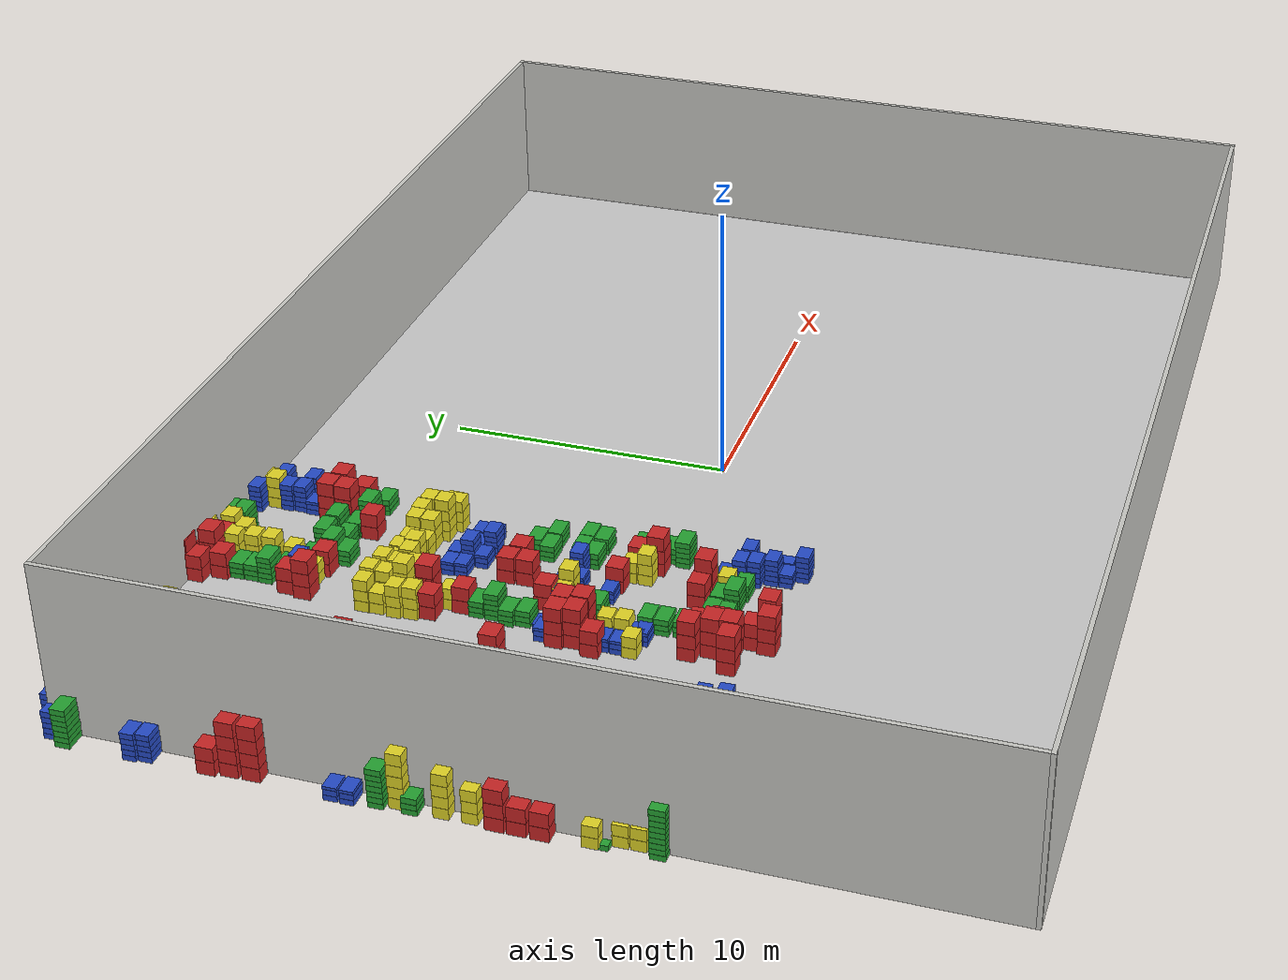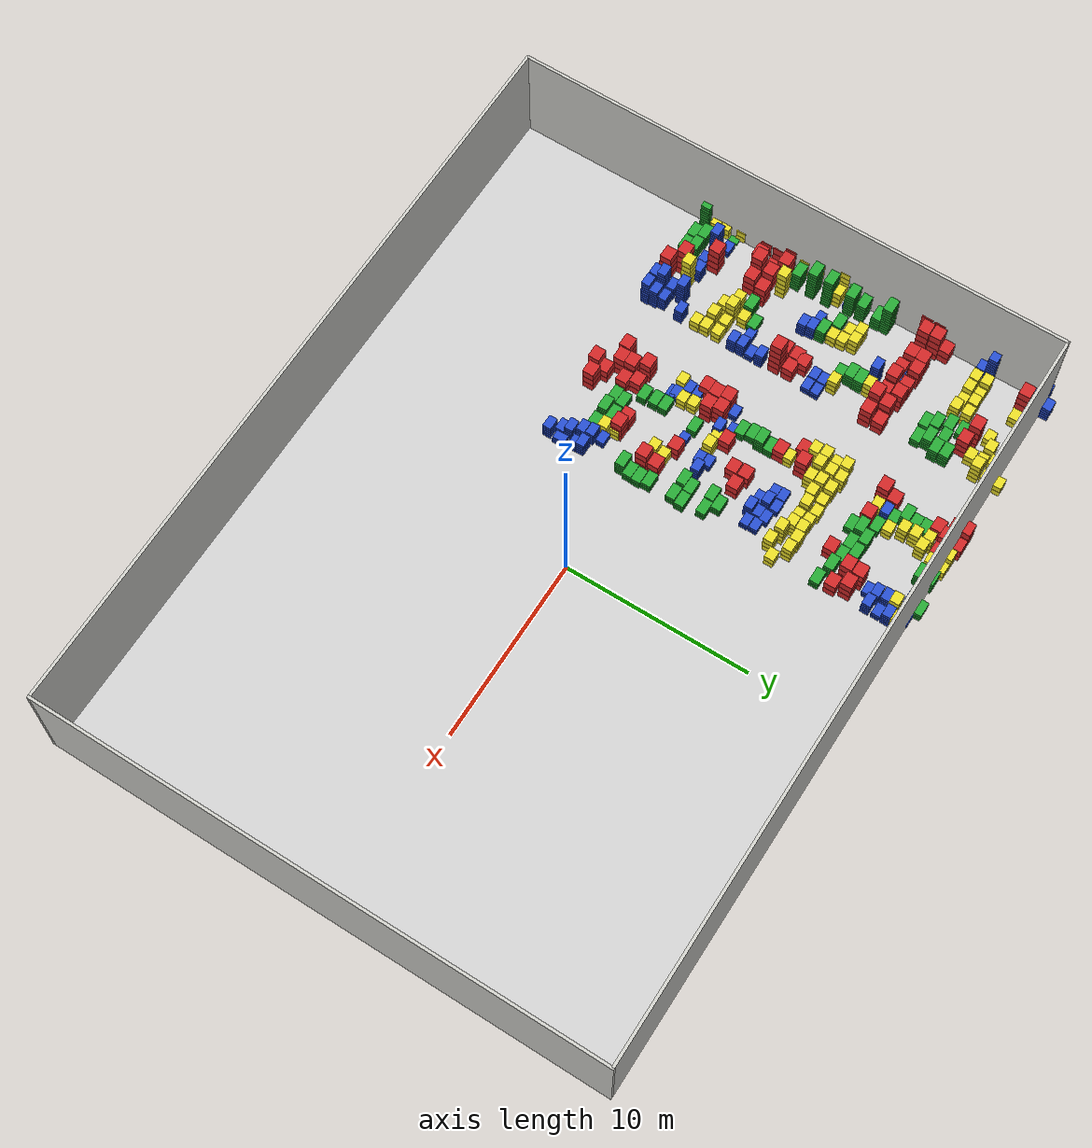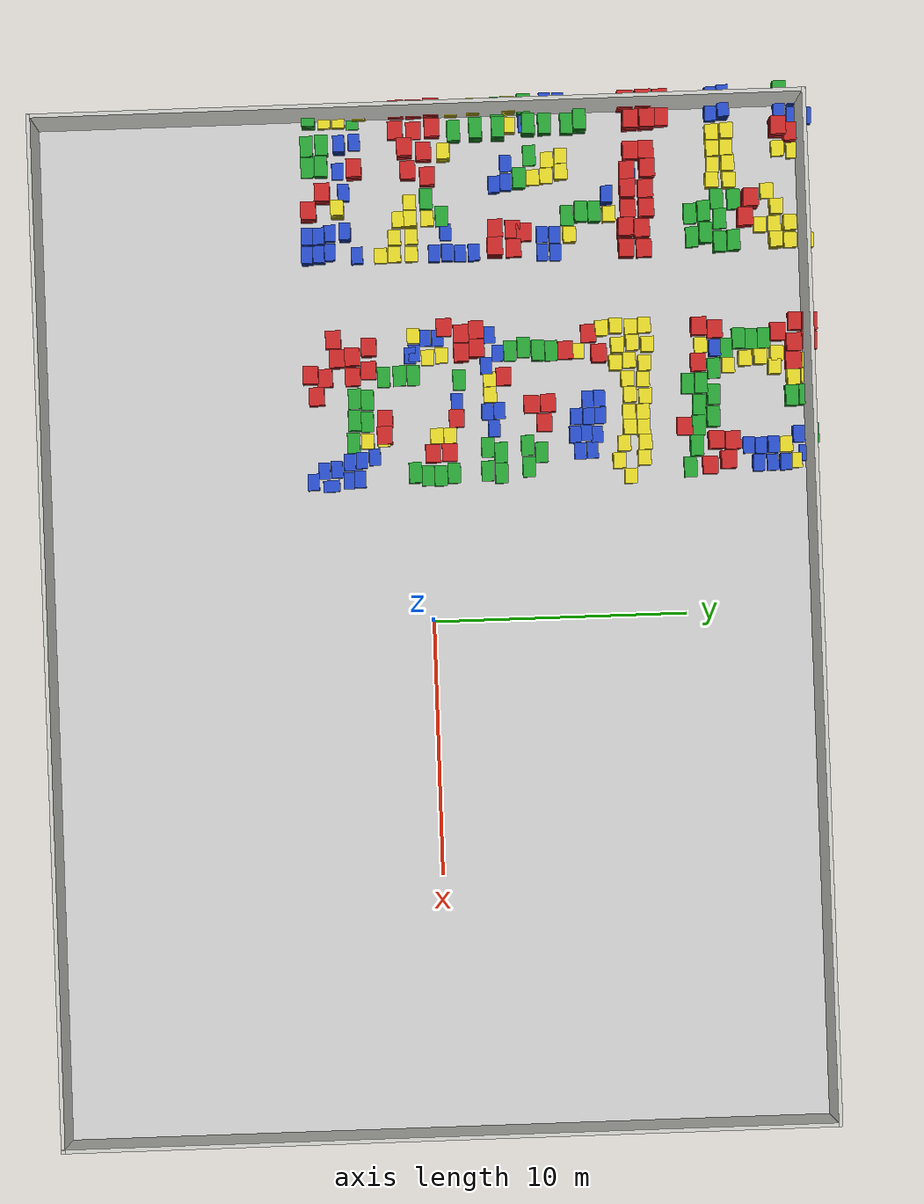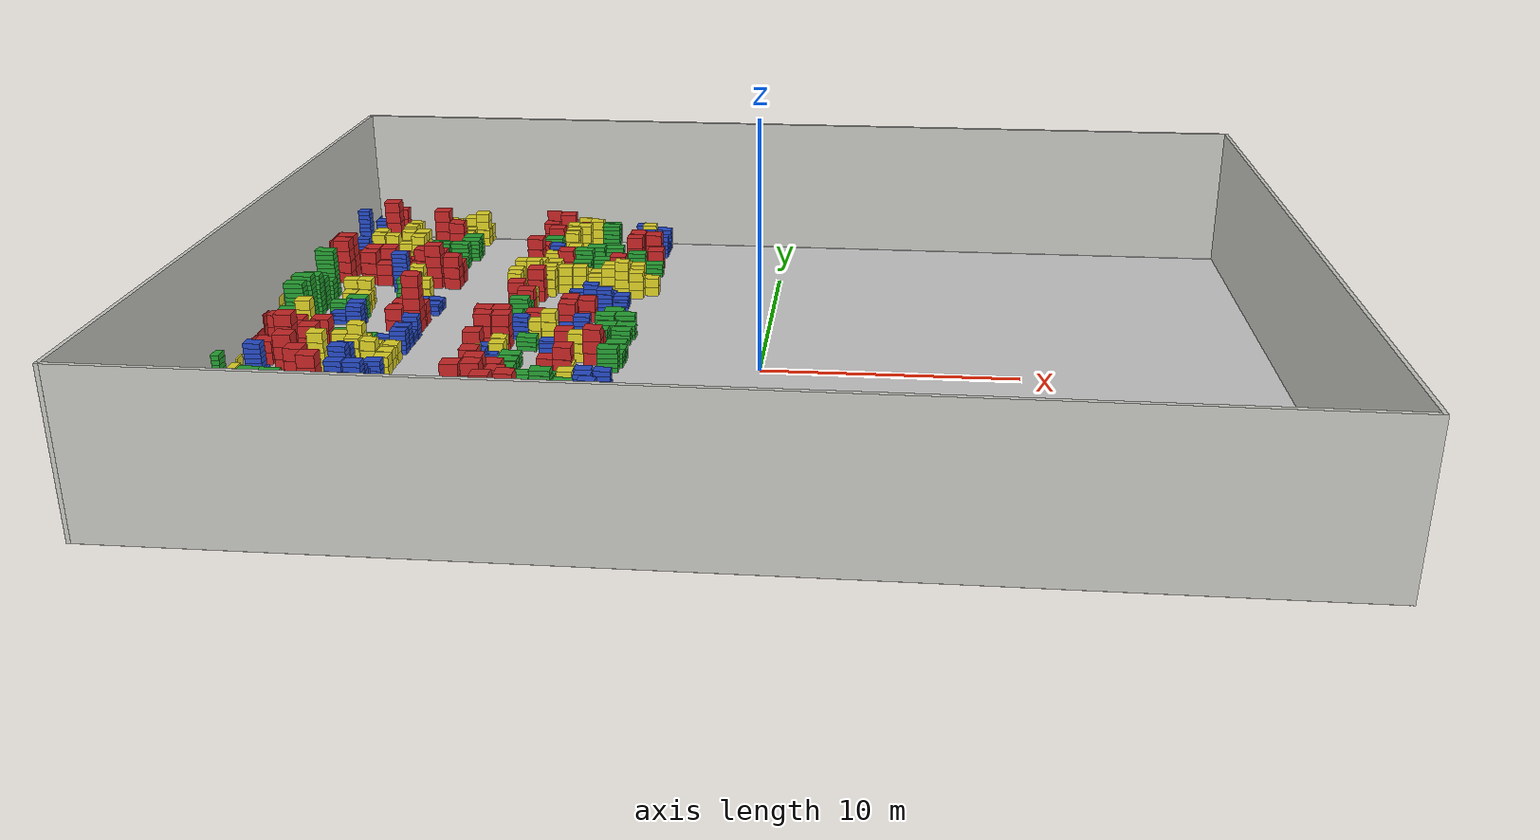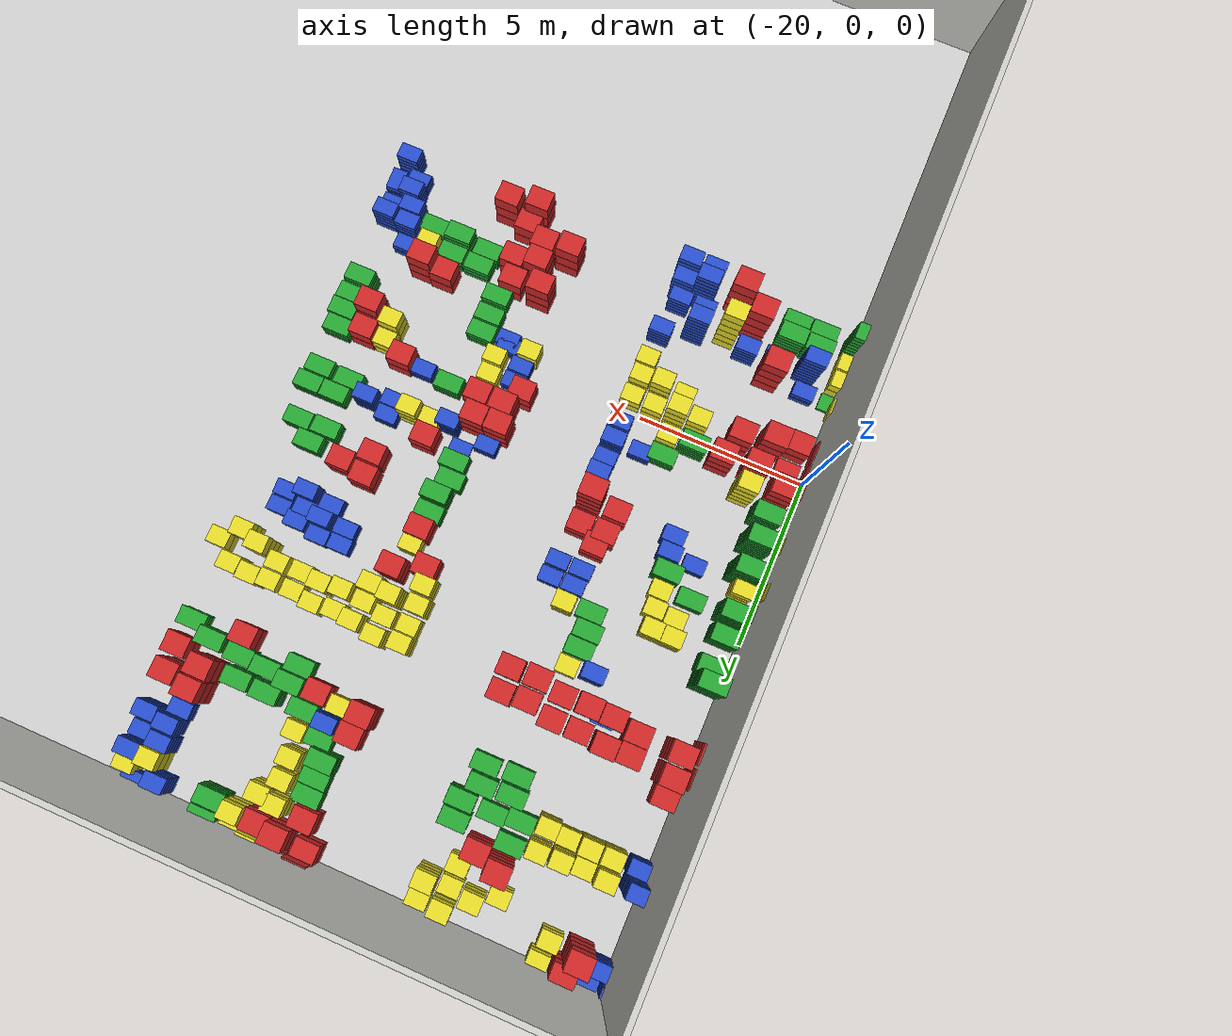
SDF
<?xml version="1.0" ?>
<sdf version="1.6">
  <world name="default">
    <include>
      <uri>model://sun</uri>
    </include>
    <include>
      <uri>model://factory_floor</uri>
    </include>
    <include>
      <uri>model://factory_outer_frame</uri>
    </include>

   <model name='baggage_B_x9'>
        <model name='baggage_B_0'>
            <static>1</static>
            <link name='link'>
            <collision name='collision'>
                <geometry>
                <box>
                    <size>0.65 0.45 0.2</size>
                </box>
                </geometry>
            </collision>
            <visual name='visual'>
                <geometry>
                <box>
                    <size>0.65 0.45 0.2</size>
                </box>
                </geometry>
                <material>
                <script>
                    <uri>file://media/materials/scripts/gazebo.material</uri>
                    <name>Gazebo/Blue</name>
                </script>
                </material>
            </visual>
            </link>
            <pose frame=''>0 0 0.1 0 -0 0</pose>
        </model>
        <model name='baggage_B_1'>
            <static>1</static>
            <link name='link'>
            <collision name='collision'>
                <geometry>
                <box>
                    <size>0.65 0.45 0.2</size>
                </box>
                </geometry>
            </collision>
            <visual name='visual'>
                <geometry>
                <box>
                    <size>0.65 0.45 0.2</size>
                </box>
                </geometry>
                <material>
                <script>
                    <uri>file://media/materials/scripts/gazebo.material</uri>
                    <name>Gazebo/Blue</name>
                </script>
                </material>
            </visual>
            </link>
            <pose frame=''>0.001 -0.0095 0.3 0 -0 0</pose>
        </model>
        <model name='baggage_B_2'>
            <static>1</static>
            <link name='link'>
            <collision name='collision'>
                <geometry>
                <box>
                    <size>0.65 0.45 0.2</size>
                </box>
                </geometry>
            </collision>
            <visual name='visual'>
                <geometry>
                <box>
                    <size>0.65 0.45 0.2</size>
                </box>
                </geometry>
                <material>
                <script>
                    <uri>file://media/materials/scripts/gazebo.material</uri>
                    <name>Gazebo/Blue</name>
                </script>
                </material>
            </visual>
            </link>
            <pose frame=''>0.0028 -0.0029 0.5 0 -0 0</pose>
        </model>
        <model name='baggage_B_3'>
            <static>1</static>
            <link name='link'>
            <collision name='collision'>
                <geometry>
                <box>
                    <size>0.65 0.45 0.2</size>
                </box>
                </geometry>
            </collision>
            <visual name='visual'>
                <geometry>
                <box>
                    <size>0.65 0.45 0.2</size>
                </box>
                </geometry>
                <material>
                <script>
                    <uri>file://media/materials/scripts/gazebo.material</uri>
                    <name>Gazebo/Blue</name>
                </script>
                </material>
            </visual>
            </link>
            <pose frame=''>-0.0004 -0.0089 0.7 0 -0 0</pose>
        </model>
        <model name='baggage_B_4'>
            <static>1</static>
            <link name='link'>
            <collision name='collision'>
                <geometry>
                <box>
                    <size>0.65 0.45 0.2</size>
                </box>
                </geometry>
            </collision>
            <visual name='visual'>
                <geometry>
                <box>
                    <size>0.65 0.45 0.2</size>
                </box>
                </geometry>
                <material>
                <script>
                    <uri>file://media/materials/scripts/gazebo.material</uri>
                    <name>Gazebo/Blue</name>
                </script>
                </material>
            </visual>
            </link>
            <pose frame=''>0.0034 -0.0062 0.9 0 -0 0</pose>
        </model>
        <model name='baggage_B_5'>
            <static>1</static>
            <link name='link'>
            <collision name='collision'>
                <geometry>
                <box>
                    <size>0.65 0.45 0.2</size>
                </box>
                </geometry>
            </collision>
            <visual name='visual'>
                <geometry>
                <box>
                    <size>0.65 0.45 0.2</size>
                </box>
                </geometry>
                <material>
                <script>
                    <uri>file://media/materials/scripts/gazebo.material</uri>
                    <name>Gazebo/Blue</name>
                </script>
                </material>
            </visual>
            </link>
            <pose frame=''>0.0037 -0.0012 1.1 0 -0 0</pose>
        </model>
        <model name='baggage_B_6'>
            <static>1</static>
            <link name='link'>
            <collision name='collision'>
                <geometry>
                <box>
                    <size>0.65 0.45 0.2</size>
                </box>
                </geometry>
            </collision>
            <visual name='visual'>
                <geometry>
                <box>
                    <size>0.65 0.45 0.2</size>
                </box>
                </geometry>
                <material>
                <script>
                    <uri>file://media/materials/scripts/gazebo.material</uri>
                    <name>Gazebo/Blue</name>
                </script>
                </material>
            </visual>
            </link>
            <pose frame=''>0 -0.0018 1.3 0 -0 0</pose>
        </model>
        <model name='baggage_B_7'>
            <static>1</static>
            <link name='link'>
            <collision name='collision'>
                <geometry>
                <box>
                    <size>0.65 0.45 0.2</size>
                </box>
                </geometry>
            </collision>
            <visual name='visual'>
                <geometry>
                <box>
                    <size>0.65 0.45 0.2</size>
                </box>
                </geometry>
                <material>
                <script>
                    <uri>file://media/materials/scripts/gazebo.material</uri>
                    <name>Gazebo/Blue</name>
                </script>
                </material>
            </visual>
            </link>
            <pose frame=''>-0.0036 -0.0074 1.5 0 -0 0</pose>
        </model>
        <model name='baggage_B_8'>
            <static>1</static>
            <link name='link'>
            <collision name='collision'>
                <geometry>
                <box>
                    <size>0.65 0.45 0.2</size>
                </box>
                </geometry>
            </collision>
            <visual name='visual'>
                <geometry>
                <box>
                    <size>0.65 0.45 0.2</size>
                </box>
                </geometry>
                <material>
                <script>
                    <uri>file://media/materials/scripts/gazebo.material</uri>
                    <name>Gazebo/Blue</name>
                </script>
                </material>
            </visual>
            </link>
            <pose frame=''>-0.0068 -0.0081 1.7 0 -0 0</pose>
        </model>
        <pose frame=''>-14.554 -4.46821 0 0 -0 0</pose>
        </model>
        <model name='baggage_B_x7'>
        <model name='baggage_B_0'>
            <static>1</static>
            <link name='link'>
            <collision name='collision'>
                <geometry>
                <box>
                    <size>0.65 0.45 0.2</size>
                </box>
                </geometry>
            </collision>
            <visual name='visual'>
                <geometry>
                <box>
                    <size>0.65 0.45 0.2</size>
                </box>
                </geometry>
                <material>
                <script>
                    <uri>file://media/materials/scripts/gazebo.material</uri>
                    <name>Gazebo/Blue</name>
                </script>
                </material>
            </visual>
            </link>
            <pose frame=''>0 0 0.1 0 -0 0</pose>
        </model>
        <model name='baggage_B_1'>
            <static>1</static>
            <link name='link'>
            <collision name='collision'>
                <geometry>
                <box>
                    <size>0.65 0.45 0.2</size>
                </box>
                </geometry>
            </collision>
            <visual name='visual'>
                <geometry>
                <box>
                    <size>0.65 0.45 0.2</size>
                </box>
                </geometry>
                <material>
                <script>
                    <uri>file://media/materials/scripts/gazebo.material</uri>
                    <name>Gazebo/Blue</name>
                </script>
                </material>
            </visual>
            </link>
            <pose frame=''>-0.0094 -0.006 0.3 0 -0 0</pose>
        </model>
        <model name='baggage_B_2'>
            <static>1</static>
            <link name='link'>
            <collision name='collision'>
                <geometry>
                <box>
                    <size>0.65 0.45 0.2</size>
                </box>
                </geometry>
            </collision>
            <visual name='visual'>
                <geometry>
                <box>
                    <size>0.65 0.45 0.2</size>
                </box>
                </geometry>
                <material>
                <script>
                    <uri>file://media/materials/scripts/gazebo.material</uri>
                    <name>Gazebo/Blue</name>
                </script>
                </material>
            </visual>
            </link>
            <pose frame=''>-0.0099 -0.0073 0.5 0 -0 0</pose>
        </model>
        <model name='baggage_B_3'>
            <static>1</static>
            <link name='link'>
            <collision name='collision'>
                <geometry>
                <box>
                    <size>0.65 0.45 0.2</size>
                </box>
                </geometry>
            </collision>
            <visual name='visual'>
                <geometry>
                <box>
                    <size>0.65 0.45 0.2</size>
                </box>
                </geometry>
                <material>
                <script>
                    <uri>file://media/materials/scripts/gazebo.material</uri>
                    <name>Gazebo/Blue</name>
                </script>
                </material>
            </visual>
            </link>
            <pose frame=''>-0.0063 0.0078 0.7 0 -0 0</pose>
        </model>
        <model name='baggage_B_4'>
            <static>1</static>
            <link name='link'>
            <collision name='collision'>
                <geometry>
                <box>
                    <size>0.65 0.45 0.2</size>
                </box>
                </geometry>
            </collision>
            <visual name='visual'>
                <geometry>
                <box>
                    <size>0.65 0.45 0.2</size>
                </box>
                </geometry>
                <material>
                <script>
                    <uri>file://media/materials/scripts/gazebo.material</uri>
                    <name>Gazebo/Blue</name>
                </script>
                </material>
            </visual>
            </link>
            <pose frame=''>0.0002 0.0059 0.9 0 -0 0</pose>
        </model>
        <model name='baggage_B_5'>
            <static>1</static>
            <link name='link'>
            <collision name='collision'>
                <geometry>
                <box>
                    <size>0.65 0.45 0.2</size>
                </box>
                </geometry>
            </collision>
            <visual name='visual'>
                <geometry>
                <box>
                    <size>0.65 0.45 0.2</size>
                </box>
                </geometry>
                <material>
                <script>
                    <uri>file://media/materials/scripts/gazebo.material</uri>
                    <name>Gazebo/Blue</name>
                </script>
                </material>
            </visual>
            </link>
            <pose frame=''>0.0073 -0.0061 1.1 0 -0 0</pose>
        </model>
        <model name='baggage_B_6'>
            <static>1</static>
            <link name='link'>
            <collision name='collision'>
                <geometry>
                <box>
                    <size>0.65 0.45 0.2</size>
                </box>
                </geometry>
            </collision>
            <visual name='visual'>
                <geometry>
                <box>
                    <size>0.65 0.45 0.2</size>
                </box>
                </geometry>
                <material>
                <script>
                    <uri>file://media/materials/scripts/gazebo.material</uri>
                    <name>Gazebo/Blue</name>
                </script>
                </material>
            </visual>
            </link>
            <pose frame=''>0.0019 -0.0096 1.3 0 -0 0</pose>
        </model>
        <pose frame=''>-14.5975 -4.0182 0 0 -0 0</pose>
        </model>
        <model name='baggage_B_x11'>
        <model name='baggage_B_0'>
            <static>1</static>
            <link name='link'>
            <collision name='collision'>
                <geometry>
                <box>
                    <size>0.65 0.45 0.2</size>
                </box>
                </geometry>
            </collision>
            <visual name='visual'>
                <geometry>
                <box>
                    <size>0.65 0.45 0.2</size>
                </box>
                </geometry>
                <material>
                <script>
                    <uri>file://media/materials/scripts/gazebo.material</uri>
                    <name>Gazebo/Blue</name>
                </script>
                </material>
            </visual>
            </link>
            <pose frame=''>0 0 0.1 0 -0 0</pose>
        </model>
        <model name='baggage_B_1'>
            <static>1</static>
            <link name='link'>
            <collision name='collision'>
                <geometry>
                <box>
                    <size>0.65 0.45 0.2</size>
                </box>
                </geometry>
            </collision>
            <visual name='visual'>
                <geometry>
                <box>
                    <size>0.65 0.45 0.2</size>
                </box>
                </geometry>
                <material>
                <script>
                    <uri>file://media/materials/scripts/gazebo.material</uri>
                    <name>Gazebo/Blue</name>
                </script>
                </material>
            </visual>
            </link>
            <pose frame=''>0.0088 0.0038 0.3 0 -0 0</pose>
        </model>
        <model name='baggage_B_2'>
            <static>1</static>
            <link name='link'>
            <collision name='collision'>
                <geometry>
                <box>
                    <size>0.65 0.45 0.2</size>
                </box>
                </geometry>
            </collision>
            <visual name='visual'>
                <geometry>
                <box>
                    <size>0.65 0.45 0.2</size>
                </box>
                </geometry>
                <material>
                <script>
                    <uri>file://media/materials/scripts/gazebo.material</uri>
                    <name>Gazebo/Blue</name>
                </script>
                </material>
            </visual>
            </link>
            <pose frame=''>0.0099 0.0013 0.5 0 -0 0</pose>
        </model>
        <model name='baggage_B_3'>
            <static>1</static>
            <link name='link'>
            <collision name='collision'>
                <geometry>
                <box>
                    <size>0.65 0.45 0.2</size>
                </box>
                </geometry>
            </collision>
            <visual name='visual'>
                <geometry>
                <box>
                    <size>0.65 0.45 0.2</size>
                </box>
                </geometry>
                <material>
                <script>
                    <uri>file://media/materials/scripts/gazebo.material</uri>
                    <name>Gazebo/Blue</name>
                </script>
                </material>
            </visual>
            </link>
            <pose frame=''>0.0022 -0.0084 0.7 0 -0 0</pose>
        </model>
        <model name='baggage_B_4'>
            <static>1</static>
            <link name='link'>
            <collision name='collision'>
                <geometry>
                <box>
                    <size>0.65 0.45 0.2</size>
                </box>
                </geometry>
            </collision>
            <visual name='visual'>
                <geometry>
                <box>
                    <size>0.65 0.45 0.2</size>
                </box>
                </geometry>
                <material>
                <script>
                    <uri>file://media/materials/scripts/gazebo.material</uri>
                    <name>Gazebo/Blue</name>
                </script>
                </material>
            </visual>
            </link>
            <pose frame=''>-0.0036 0.0023 0.9 0 -0 0</pose>
        </model>
        <model name='baggage_B_5'>
            <static>1</static>
            <link name='link'>
            <collision name='collision'>
                <geometry>
                <box>
                    <size>0.65 0.45 0.2</size>
                </box>
                </geometry>
            </collision>
            <visual name='visual'>
                <geometry>
                <box>
                    <size>0.65 0.45 0.2</size>
                </box>
                </geometry>
                <material>
                <script>
                    <uri>file://media/materials/scripts/gazebo.material</uri>
                    <name>Gazebo/Blue</name>
                </script>
                </material>
            </visual>
            </link>
            <pose frame=''>0.0085 -0.0016 1.1 0 -0 0</pose>
        </model>
        <model name='baggage_B_6'>
            <static>1</static>
            <link name='link'>
            <collision name='collision'>
                <geometry>
                <box>
                    <size>0.65 0.45 0.2</size>
                </box>
                </geometry>
            </collision>
            <visual name='visual'>
                <geometry>
                <box>
                    <size>0.65 0.45 0.2</size>
                </box>
                </geometry>
                <material>
                <script>
                    <uri>file://media/materials/scripts/gazebo.material</uri>
                    <name>Gazebo/Blue</name>
                </script>
                </material>
            </visual>
            </link>
            <pose frame=''>-0.0066 0.0086 1.3 0 -0 0</pose>
        </model>
        <model name='baggage_B_7'>
            <static>1</static>
            <link name='link'>
            <collision name='collision'>
                <geometry>
                <box>
                    <size>0.65 0.45 0.2</size>
                </box>
                </geometry>
            </collision>
            <visual name='visual'>
                <geometry>
                <box>
                    <size>0.65 0.45 0.2</size>
                </box>
                </geometry>
                <material>
                <script>
                    <uri>file://media/materials/scripts/gazebo.material</uri>
                    <name>Gazebo/Blue</name>
                </script>
                </material>
            </visual>
            </link>
            <pose frame=''>0.0096 -0.0061 1.5 0 -0 0</pose>
        </model>
        <model name='baggage_B_8'>
            <static>1</static>
            <link name='link'>
            <collision name='collision'>
                <geometry>
                <box>
                    <size>0.65 0.45 0.2</size>
                </box>
                </geometry>
            </collision>
            <visual name='visual'>
                <geometry>
                <box>
                    <size>0.65 0.45 0.2</size>
                </box>
                </geometry>
                <material>
                <script>
                    <uri>file://media/materials/scripts/gazebo.material</uri>
                    <name>Gazebo/Blue</name>
                </script>
                </material>
            </visual>
            </link>
            <pose frame=''>0.0048 0.0081 1.7 0 -0 0</pose>
        </model>
        <model name='baggage_B_9'>
            <static>1</static>
            <link name='link'>
            <collision name='collision'>
                <geometry>
                <box>
                    <size>0.65 0.45 0.2</size>
                </box>
                </geometry>
            </collision>
            <visual name='visual'>
                <geometry>
                <box>
                    <size>0.65 0.45 0.2</size>
                </box>
                </geometry>
                <material>
                <script>
                    <uri>file://media/materials/scripts/gazebo.material</uri>
                    <name>Gazebo/Blue</name>
                </script>
                </material>
            </visual>
            </link>
            <pose frame=''>0.009 0.0009 1.9 0 -0 0</pose>
        </model>
        <model name='baggage_B_10'>
            <static>1</static>
            <link name='link'>
            <collision name='collision'>
                <geometry>
                <box>
                    <size>0.65 0.45 0.2</size>
                </box>
                </geometry>
            </collision>
            <visual name='visual'>
                <geometry>
                <box>
                    <size>0.65 0.45 0.2</size>
                </box>
                </geometry>
                <material>
                <script>
                    <uri>file://media/materials/scripts/gazebo.material</uri>
                    <name>Gazebo/Blue</name>
                </script>
                </material>
            </visual>
            </link>
            <pose frame=''>0.0028 0.0021 2.1 0 -0 0</pose>
        </model>
        <pose frame=''>-15.252 -4.00278 0 0 -0 0</pose>
        </model>
        <model name='baggage_B_x9_0'>
        <model name='baggage_B_0'>
            <static>1</static>
            <link name='link'>
            <collision name='collision'>
                <geometry>
                <box>
                    <size>0.65 0.45 0.2</size>
                </box>
                </geometry>
            </collision>
            <visual name='visual'>
                <geometry>
                <box>
                    <size>0.65 0.45 0.2</size>
                </box>
                </geometry>
                <material>
                <script>
                    <uri>file://media/materials/scripts/gazebo.material</uri>
                    <name>Gazebo/Blue</name>
                </script>
                </material>
            </visual>
            </link>
            <pose frame=''>0 0 0.1 0 -0 0</pose>
        </model>
        <model name='baggage_B_1'>
            <static>1</static>
            <link name='link'>
            <collision name='collision'>
                <geometry>
                <box>
                    <size>0.65 0.45 0.2</size>
                </box>
                </geometry>
            </collision>
            <visual name='visual'>
                <geometry>
                <box>
                    <size>0.65 0.45 0.2</size>
                </box>
                </geometry>
                <material>
                <script>
                    <uri>file://media/materials/scripts/gazebo.material</uri>
                    <name>Gazebo/Blue</name>
                </script>
                </material>
            </visual>
            </link>
            <pose frame=''>0.001 -0.0095 0.3 0 -0 0</pose>
        </model>
        <model name='baggage_B_2'>
            <static>1</static>
            <link name='link'>
            <collision name='collision'>
                <geometry>
                <box>
                    <size>0.65 0.45 0.2</size>
                </box>
                </geometry>
            </collision>
            <visual name='visual'>
                <geometry>
                <box>
                    <size>0.65 0.45 0.2</size>
                </box>
                </geometry>
                <material>
                <script>
                    <uri>file://media/materials/scripts/gazebo.material</uri>
                    <name>Gazebo/Blue</name>
                </script>
                </material>
            </visual>
            </link>
            <pose frame=''>0.0028 -0.0029 0.5 0 -0 0</pose>
        </model>
        <model name='baggage_B_3'>
            <static>1</static>
            <link name='link'>
            <collision name='collision'>
                <geometry>
                <box>
                    <size>0.65 0.45 0.2</size>
                </box>
                </geometry>
            </collision>
            <visual name='visual'>
                <geometry>
                <box>
                    <size>0.65 0.45 0.2</size>
                </box>
                </geometry>
                <material>
                <script>
                    <uri>file://media/materials/scripts/gazebo.material</uri>
                    <name>Gazebo/Blue</name>
                </script>
                </material>
            </visual>
            </link>
            <pose frame=''>-0.0004 -0.0089 0.7 0 -0 0</pose>
        </model>
        <model name='baggage_B_4'>
            <static>1</static>
            <link name='link'>
            <collision name='collision'>
                <geometry>
                <box>
                    <size>0.65 0.45 0.2</size>
                </box>
                </geometry>
            </collision>
            <visual name='visual'>
                <geometry>
                <box>
                    <size>0.65 0.45 0.2</size>
                </box>
                </geometry>
                <material>
                <script>
                    <uri>file://media/materials/scripts/gazebo.material</uri>
                    <name>Gazebo/Blue</name>
                </script>
                </material>
            </visual>
            </link>
            <pose frame=''>0.0034 -0.0062 0.9 0 -0 0</pose>
        </model>
        <model name='baggage_B_5'>
            <static>1</static>
            <link name='link'>
            <collision name='collision'>
                <geometry>
                <box>
                    <size>0.65 0.45 0.2</size>
                </box>
                </geometry>
            </collision>
            <visual name='visual'>
                <geometry>
                <box>
                    <size>0.65 0.45 0.2</size>
                </box>
                </geometry>
                <material>
                <script>
                    <uri>file://media/materials/scripts/gazebo.material</uri>
                    <name>Gazebo/Blue</name>
                </script>
                </material>
            </visual>
            </link>
            <pose frame=''>0.0037 -0.0012 1.1 0 -0 0</pose>
        </model>
        <model name='baggage_B_6'>
            <static>1</static>
            <link name='link'>
            <collision name='collision'>
                <geometry>
                <box>
                    <size>0.65 0.45 0.2</size>
                </box>
                </geometry>
            </collision>
            <visual name='visual'>
                <geometry>
                <box>
                    <size>0.65 0.45 0.2</size>
                </box>
                </geometry>
                <material>
                <script>
                    <uri>file://media/materials/scripts/gazebo.material</uri>
                    <name>Gazebo/Blue</name>
                </script>
                </material>
            </visual>
            </link>
            <pose frame=''>0 -0.0018 1.3 0 -0 0</pose>
        </model>
        <model name='baggage_B_7'>
            <static>1</static>
            <link name='link'>
            <collision name='collision'>
                <geometry>
                <box>
                    <size>0.65 0.45 0.2</size>
                </box>
                </geometry>
            </collision>
            <visual name='visual'>
                <geometry>
                <box>
                    <size>0.65 0.45 0.2</size>
                </box>
                </geometry>
                <material>
                <script>
                    <uri>file://media/materials/scripts/gazebo.material</uri>
                    <name>Gazebo/Blue</name>
                </script>
                </material>
            </visual>
            </link>
            <pose frame=''>-0.0036 -0.0074 1.5 0 -0 0</pose>
        </model>
        <model name='baggage_B_8'>
            <static>1</static>
            <link name='link'>
            <collision name='collision'>
                <geometry>
                <box>
                    <size>0.65 0.45 0.2</size>
                </box>
                </geometry>
            </collision>
            <visual name='visual'>
                <geometry>
                <box>
                    <size>0.65 0.45 0.2</size>
                </box>
                </geometry>
                <material>
                <script>
                    <uri>file://media/materials/scripts/gazebo.material</uri>
                    <name>Gazebo/Blue</name>
                </script>
                </material>
            </visual>
            </link>
            <pose frame=''>-0.0068 -0.0081 1.7 0 -0 0</pose>
        </model>
        <pose frame=''>-15.2703 -4.44925 0 0 -0 0</pose>
        </model>
        <model name='baggage_A_x4'>
        <model name='baggage_A_0'>
            <static>1</static>
            <link name='link'>
            <collision name='collision'>
                <geometry>
                <box>
                    <size>0.7 0.6 0.5</size>
                </box>
                </geometry>
            </collision>
            <visual name='visual'>
                <geometry>
                <box>
                    <size>0.7 0.6 0.5</size>
                </box>
                </geometry>
                <material>
                <script>
                    <uri>file://media/materials/scripts/gazebo.material</uri>
                    <name>Gazebo/Red</name>
                </script>
                </material>
            </visual>
            </link>
            <pose frame=''>0 0 0.25 0 -0 0</pose>
        </model>
        <model name='baggage_A_1'>
            <static>1</static>
            <link name='link'>
            <collision name='collision'>
                <geometry>
                <box>
                    <size>0.7 0.6 0.5</size>
                </box>
                </geometry>
            </collision>
            <visual name='visual'>
                <geometry>
                <box>
                    <size>0.7 0.6 0.5</size>
                </box>
                </geometry>
                <material>
                <script>
                    <uri>file://media/materials/scripts/gazebo.material</uri>
                    <name>Gazebo/Red</name>
                </script>
                </material>
            </visual>
            </link>
            <pose frame=''>0.0053 0.0033 0.75 0 -0 0</pose>
        </model>
        <model name='baggage_A_2'>
            <static>1</static>
            <link name='link'>
            <collision name='collision'>
                <geometry>
                <box>
                    <size>0.7 0.6 0.5</size>
                </box>
                </geometry>
            </collision>
            <visual name='visual'>
                <geometry>
                <box>
                    <size>0.7 0.6 0.5</size>
                </box>
                </geometry>
                <material>
                <script>
                    <uri>file://media/materials/scripts/gazebo.material</uri>
                    <name>Gazebo/Red</name>
                </script>
                </material>
            </visual>
            </link>
            <pose frame=''>-0.0056 -0.0003 1.25 0 -0 0</pose>
        </model>
        <model name='baggage_A_3'>
            <static>1</static>
            <link name='link'>
            <collision name='collision'>
                <geometry>
                <box>
                    <size>0.7 0.6 0.5</size>
                </box>
                </geometry>
            </collision>
            <visual name='visual'>
                <geometry>
                <box>
                    <size>0.7 0.6 0.5</size>
                </box>
                </geometry>
                <material>
                <script>
                    <uri>file://media/materials/scripts/gazebo.material</uri>
                    <name>Gazebo/Red</name>
                </script>
                </material>
            </visual>
            </link>
            <pose frame=''>-0.0098 0.0065 1.75 0 -0 0</pose>
        </model>
        <pose frame=''>-16.2769 -4.37446 0 0 -0 0</pose>
        </model>
        <model name='baggage_A_x4_0'>
        <model name='baggage_A_0'>
            <static>1</static>
            <link name='link'>
            <collision name='collision'>
                <geometry>
                <box>
                    <size>0.7 0.6 0.5</size>
                </box>
                </geometry>
            </collision>
            <visual name='visual'>
                <geometry>
                <box>
                    <size>0.7 0.6 0.5</size>
                </box>
                </geometry>
                <material>
                <script>
                    <uri>file://media/materials/scripts/gazebo.material</uri>
                    <name>Gazebo/Red</name>
                </script>
                </material>
            </visual>
            </link>
            <pose frame=''>0 0 0.25 0 -0 0</pose>
        </model>
        <model name='baggage_A_1'>
            <static>1</static>
            <link name='link'>
            <collision name='collision'>
                <geometry>
                <box>
                    <size>0.7 0.6 0.5</size>
                </box>
                </geometry>
            </collision>
            <visual name='visual'>
                <geometry>
                <box>
                    <size>0.7 0.6 0.5</size>
                </box>
                </geometry>
                <material>
                <script>
                    <uri>file://media/materials/scripts/gazebo.material</uri>
                    <name>Gazebo/Red</name>
                </script>
                </material>
            </visual>
            </link>
            <pose frame=''>0.0053 0.0033 0.75 0 -0 0</pose>
        </model>
        <model name='baggage_A_2'>
            <static>1</static>
            <link name='link'>
            <collision name='collision'>
                <geometry>
                <box>
                    <size>0.7 0.6 0.5</size>
                </box>
                </geometry>
            </collision>
            <visual name='visual'>
                <geometry>
                <box>
                    <size>0.7 0.6 0.5</size>
                </box>
                </geometry>
                <material>
                <script>
                    <uri>file://media/materials/scripts/gazebo.material</uri>
                    <name>Gazebo/Red</name>
                </script>
                </material>
            </visual>
            </link>
            <pose frame=''>-0.0056 -0.0003 1.25 0 -0 0</pose>
        </model>
        <model name='baggage_A_3'>
            <static>1</static>
            <link name='link'>
            <collision name='collision'>
                <geometry>
                <box>
                    <size>0.7 0.6 0.5</size>
                </box>
                </geometry>
            </collision>
            <visual name='visual'>
                <geometry>
                <box>
                    <size>0.7 0.6 0.5</size>
                </box>
                </geometry>
                <material>
                <script>
                    <uri>file://media/materials/scripts/gazebo.material</uri>
                    <name>Gazebo/Red</name>
                </script>
                </material>
            </visual>
            </link>
            <pose frame=''>-0.0098 0.0065 1.75 0 -0 0</pose>
        </model>
        <pose frame=''>-16.9839 -3.81262 0 0 -0 0</pose>
        </model>
        <model name='baggage_D_x3'>
        <model name='baggage_D_0'>
            <static>1</static>
            <link name='link'>
            <collision name='collision'>
                <geometry>
                <box>
                    <size>0.8 0.5 0.2</size>
                </box>
                </geometry>
            </collision>
            <visual name='visual'>
                <geometry>
                <box>
                    <size>0.8 0.5 0.2</size>
                </box>
                </geometry>
                <material>
                <script>
                    <uri>file://media/materials/scripts/gazebo.material</uri>
                    <name>Gazebo/Green</name>
                </script>
                </material>
            </visual>
            </link>
            <pose frame=''>0 0 0.1 0 -0 0</pose>
        </model>
        <model name='baggage_D_1'>
            <static>1</static>
            <link name='link'>
            <collision name='collision'>
                <geometry>
                <box>
                    <size>0.8 0.5 0.2</size>
                </box>
                </geometry>
            </collision>
            <visual name='visual'>
                <geometry>
                <box>
                    <size>0.8 0.5 0.2</size>
                </box>
                </geometry>
                <material>
                <script>
                    <uri>file://media/materials/scripts/gazebo.material</uri>
                    <name>Gazebo/Green</name>
                </script>
                </material>
            </visual>
            </link>
            <pose frame=''>-0.0056 0.0083 0.3 0 -0 0</pose>
        </model>
        <model name='baggage_D_2'>
            <static>1</static>
            <link name='link'>
            <collision name='collision'>
                <geometry>
                <box>
                    <size>0.8 0.5 0.2</size>
                </box>
                </geometry>
            </collision>
            <visual name='visual'>
                <geometry>
                <box>
                    <size>0.8 0.5 0.2</size>
                </box>
                </geometry>
                <material>
                <script>
                    <uri>file://media/materials/scripts/gazebo.material</uri>
                    <name>Gazebo/Green</name>
                </script>
                </material>
            </visual>
            </link>
            <pose frame=''>0.0053 0.0057 0.5 0 -0 0</pose>
        </model>
        <pose frame=''>-18.0931 -4.38096 0 0 -0 0</pose>
        </model>
        <model name='baggage_D_x5'>
        <model name='baggage_D_0'>
            <static>1</static>
            <link name='link'>
            <collision name='collision'>
                <geometry>
                <box>
                    <size>0.8 0.5 0.2</size>
                </box>
                </geometry>
            </collision>
            <visual name='visual'>
                <geometry>
                <box>
                    <size>0.8 0.5 0.2</size>
                </box>
                </geometry>
                <material>
                <script>
                    <uri>file://media/materials/scripts/gazebo.material</uri>
                    <name>Gazebo/Green</name>
                </script>
                </material>
            </visual>
            </link>
            <pose frame=''>0 0 0.1 0 -0 0</pose>
        </model>
        <model name='baggage_D_1'>
            <static>1</static>
            <link name='link'>
            <collision name='collision'>
                <geometry>
                <box>
                    <size>0.8 0.5 0.2</size>
                </box>
                </geometry>
            </collision>
            <visual name='visual'>
                <geometry>
                <box>
                    <size>0.8 0.5 0.2</size>
                </box>
                </geometry>
                <material>
                <script>
                    <uri>file://media/materials/scripts/gazebo.material</uri>
                    <name>Gazebo/Green</name>
                </script>
                </material>
            </visual>
            </link>
            <pose frame=''>-0.0065 -0.0092 0.3 0 -0 0</pose>
        </model>
        <model name='baggage_D_2'>
            <static>1</static>
            <link name='link'>
            <collision name='collision'>
                <geometry>
                <box>
                    <size>0.8 0.5 0.2</size>
                </box>
                </geometry>
            </collision>
            <visual name='visual'>
                <geometry>
                <box>
                    <size>0.8 0.5 0.2</size>
                </box>
                </geometry>
                <material>
                <script>
                    <uri>file://media/materials/scripts/gazebo.material</uri>
                    <name>Gazebo/Green</name>
                </script>
                </material>
            </visual>
            </link>
            <pose frame=''>0.005 -0.0052 0.5 0 -0 0</pose>
        </model>
        <model name='baggage_D_3'>
            <static>1</static>
            <link name='link'>
            <collision name='collision'>
                <geometry>
                <box>
                    <size>0.8 0.5 0.2</size>
                </box>
                </geometry>
            </collision>
            <visual name='visual'>
                <geometry>
                <box>
                    <size>0.8 0.5 0.2</size>
                </box>
                </geometry>
                <material>
                <script>
                    <uri>file://media/materials/scripts/gazebo.material</uri>
                    <name>Gazebo/Green</name>
                </script>
                </material>
            </visual>
            </link>
            <pose frame=''>0.0074 0.0002 0.7 0 -0 0</pose>
        </model>
        <model name='baggage_D_4'>
            <static>1</static>
            <link name='link'>
            <collision name='collision'>
                <geometry>
                <box>
                    <size>0.8 0.5 0.2</size>
                </box>
                </geometry>
            </collision>
            <visual name='visual'>
                <geometry>
                <box>
                    <size>0.8 0.5 0.2</size>
                </box>
                </geometry>
                <material>
                <script>
                    <uri>file://media/materials/scripts/gazebo.material</uri>
                    <name>Gazebo/Green</name>
                </script>
                </material>
            </visual>
            </link>
            <pose frame=''>-0.006 0.0081 0.9 0 -0 0</pose>
        </model>
        <pose frame=''>-18.083 -3.83282 0 0 -0 0</pose>
        </model>
        <model name='baggage_D_x5_0'>
        <model name='baggage_D_0'>
            <static>1</static>
            <link name='link'>
            <collision name='collision'>
                <geometry>
                <box>
                    <size>0.8 0.5 0.2</size>
                </box>
                </geometry>
            </collision>
            <visual name='visual'>
                <geometry>
                <box>
                    <size>0.8 0.5 0.2</size>
                </box>
                </geometry>
                <material>
                <script>
                    <uri>file://media/materials/scripts/gazebo.material</uri>
                    <name>Gazebo/Green</name>
                </script>
                </material>
            </visual>
            </link>
            <pose frame=''>0 0 0.1 0 -0 0</pose>
        </model>
        <model name='baggage_D_1'>
            <static>1</static>
            <link name='link'>
            <collision name='collision'>
                <geometry>
                <box>
                    <size>0.8 0.5 0.2</size>
                </box>
                </geometry>
            </collision>
            <visual name='visual'>
                <geometry>
                <box>
                    <size>0.8 0.5 0.2</size>
                </box>
                </geometry>
                <material>
                <script>
                    <uri>file://media/materials/scripts/gazebo.material</uri>
                    <name>Gazebo/Green</name>
                </script>
                </material>
            </visual>
            </link>
            <pose frame=''>-0.0065 -0.0092 0.3 0 -0 0</pose>
        </model>
        <model name='baggage_D_2'>
            <static>1</static>
            <link name='link'>
            <collision name='collision'>
                <geometry>
                <box>
                    <size>0.8 0.5 0.2</size>
                </box>
                </geometry>
            </collision>
            <visual name='visual'>
                <geometry>
                <box>
                    <size>0.8 0.5 0.2</size>
                </box>
                </geometry>
                <material>
                <script>
                    <uri>file://media/materials/scripts/gazebo.material</uri>
                    <name>Gazebo/Green</name>
                </script>
                </material>
            </visual>
            </link>
            <pose frame=''>0.005 -0.0052 0.5 0 -0 0</pose>
        </model>
        <model name='baggage_D_3'>
            <static>1</static>
            <link name='link'>
            <collision name='collision'>
                <geometry>
                <box>
                    <size>0.8 0.5 0.2</size>
                </box>
                </geometry>
            </collision>
            <visual name='visual'>
                <geometry>
                <box>
                    <size>0.8 0.5 0.2</size>
                </box>
                </geometry>
                <material>
                <script>
                    <uri>file://media/materials/scripts/gazebo.material</uri>
                    <name>Gazebo/Green</name>
                </script>
                </material>
            </visual>
            </link>
            <pose frame=''>0.0074 0.0002 0.7 0 -0 0</pose>
        </model>
        <model name='baggage_D_4'>
            <static>1</static>
            <link name='link'>
            <collision name='collision'>
                <geometry>
                <box>
                    <size>0.8 0.5 0.2</size>
                </box>
                </geometry>
            </collision>
            <visual name='visual'>
                <geometry>
                <box>
                    <size>0.8 0.5 0.2</size>
                </box>
                </geometry>
                <material>
                <script>
                    <uri>file://media/materials/scripts/gazebo.material</uri>
                    <name>Gazebo/Green</name>
                </script>
                </material>
            </visual>
            </link>
            <pose frame=''>-0.006 0.0081 0.9 0 -0 0</pose>
        </model>
        <pose frame=''>-18.9113 -3.78783 0 0 -0 0</pose>
        </model>
        <model name='baggage_D_x3_0'>
        <model name='baggage_D_0'>
            <static>1</static>
            <link name='link'>
            <collision name='collision'>
                <geometry>
                <box>
                    <size>0.8 0.5 0.2</size>
                </box>
                </geometry>
            </collision>
            <visual name='visual'>
                <geometry>
                <box>
                    <size>0.8 0.5 0.2</size>
                </box>
                </geometry>
                <material>
                <script>
                    <uri>file://media/materials/scripts/gazebo.material</uri>
                    <name>Gazebo/Green</name>
                </script>
                </material>
            </visual>
            </link>
            <pose frame=''>0 0 0.1 0 -0 0</pose>
        </model>
        <model name='baggage_D_1'>
            <static>1</static>
            <link name='link'>
            <collision name='collision'>
                <geometry>
                <box>
                    <size>0.8 0.5 0.2</size>
                </box>
                </geometry>
            </collision>
            <visual name='visual'>
                <geometry>
                <box>
                    <size>0.8 0.5 0.2</size>
                </box>
                </geometry>
                <material>
                <script>
                    <uri>file://media/materials/scripts/gazebo.material</uri>
                    <name>Gazebo/Green</name>
                </script>
                </material>
            </visual>
            </link>
            <pose frame=''>-0.0056 0.0083 0.3 0 -0 0</pose>
        </model>
        <model name='baggage_D_2'>
            <static>1</static>
            <link name='link'>
            <collision name='collision'>
                <geometry>
                <box>
                    <size>0.8 0.5 0.2</size>
                </box>
                </geometry>
            </collision>
            <visual name='visual'>
                <geometry>
                <box>
                    <size>0.8 0.5 0.2</size>
                </box>
                </geometry>
                <material>
                <script>
                    <uri>file://media/materials/scripts/gazebo.material</uri>
                    <name>Gazebo/Green</name>
                </script>
                </material>
            </visual>
            </link>
            <pose frame=''>0.0053 0.0057 0.5 0 -0 0</pose>
        </model>
        <pose frame=''>-18.9298 -4.38377 0 0 -0 0</pose>
        </model>
        <model name='baggage_D_x9'>
        <model name='baggage_D_0'>
            <static>1</static>
            <link name='link'>
            <collision name='collision'>
                <geometry>
                <box>
                    <size>0.8 0.5 0.2</size>
                </box>
                </geometry>
            </collision>
            <visual name='visual'>
                <geometry>
                <box>
                    <size>0.8 0.5 0.2</size>
                </box>
                </geometry>
                <material>
                <script>
                    <uri>file://media/materials/scripts/gazebo.material</uri>
                    <name>Gazebo/Green</name>
                </script>
                </material>
            </visual>
            </link>
            <pose frame=''>0 0 0.1 0 -0 0</pose>
        </model>
        <model name='baggage_D_1'>
            <static>1</static>
            <link name='link'>
            <collision name='collision'>
                <geometry>
                <box>
                    <size>0.8 0.5 0.2</size>
                </box>
                </geometry>
            </collision>
            <visual name='visual'>
                <geometry>
                <box>
                    <size>0.8 0.5 0.2</size>
                </box>
                </geometry>
                <material>
                <script>
                    <uri>file://media/materials/scripts/gazebo.material</uri>
                    <name>Gazebo/Green</name>
                </script>
                </material>
            </visual>
            </link>
            <pose frame=''>0.0092 0.0098 0.3 0 -0 0</pose>
        </model>
        <model name='baggage_D_2'>
            <static>1</static>
            <link name='link'>
            <collision name='collision'>
                <geometry>
                <box>
                    <size>0.8 0.5 0.2</size>
                </box>
                </geometry>
            </collision>
            <visual name='visual'>
                <geometry>
                <box>
                    <size>0.8 0.5 0.2</size>
                </box>
                </geometry>
                <material>
                <script>
                    <uri>file://media/materials/scripts/gazebo.material</uri>
                    <name>Gazebo/Green</name>
                </script>
                </material>
            </visual>
            </link>
            <pose frame=''>-0.0038 0.0073 0.5 0 -0 0</pose>
        </model>
        <model name='baggage_D_3'>
            <static>1</static>
            <link name='link'>
            <collision name='collision'>
                <geometry>
                <box>
                    <size>0.8 0.5 0.2</size>
                </box>
                </geometry>
            </collision>
            <visual name='visual'>
                <geometry>
                <box>
                    <size>0.8 0.5 0.2</size>
                </box>
                </geometry>
                <material>
                <script>
                    <uri>file://media/materials/scripts/gazebo.material</uri>
                    <name>Gazebo/Green</name>
                </script>
                </material>
            </visual>
            </link>
            <pose frame=''>0.0044 0.0085 0.7 0 -0 0</pose>
        </model>
        <model name='baggage_D_4'>
            <static>1</static>
            <link name='link'>
            <collision name='collision'>
                <geometry>
                <box>
                    <size>0.8 0.5 0.2</size>
                </box>
                </geometry>
            </collision>
            <visual name='visual'>
                <geometry>
                <box>
                    <size>0.8 0.5 0.2</size>
                </box>
                </geometry>
                <material>
                <script>
                    <uri>file://media/materials/scripts/gazebo.material</uri>
                    <name>Gazebo/Green</name>
                </script>
                </material>
            </visual>
            </link>
            <pose frame=''>-0.0044 0.0075 0.9 0 -0 0</pose>
        </model>
        <model name='baggage_D_5'>
            <static>1</static>
            <link name='link'>
            <collision name='collision'>
                <geometry>
                <box>
                    <size>0.8 0.5 0.2</size>
                </box>
                </geometry>
            </collision>
            <visual name='visual'>
                <geometry>
                <box>
                    <size>0.8 0.5 0.2</size>
                </box>
                </geometry>
                <material>
                <script>
                    <uri>file://media/materials/scripts/gazebo.material</uri>
                    <name>Gazebo/Green</name>
                </script>
                </material>
            </visual>
            </link>
            <pose frame=''>0.0002 0.0017 1.1 0 -0 0</pose>
        </model>
        <model name='baggage_D_6'>
            <static>1</static>
            <link name='link'>
            <collision name='collision'>
                <geometry>
                <box>
                    <size>0.8 0.5 0.2</size>
                </box>
                </geometry>
            </collision>
            <visual name='visual'>
                <geometry>
                <box>
                    <size>0.8 0.5 0.2</size>
                </box>
                </geometry>
                <material>
                <script>
                    <uri>file://media/materials/scripts/gazebo.material</uri>
                    <name>Gazebo/Green</name>
                </script>
                </material>
            </visual>
            </link>
            <pose frame=''>-0.0057 -0.0032 1.3 0 -0 0</pose>
        </model>
        <model name='baggage_D_7'>
            <static>1</static>
            <link name='link'>
            <collision name='collision'>
                <geometry>
                <box>
                    <size>0.8 0.5 0.2</size>
                </box>
                </geometry>
            </collision>
            <visual name='visual'>
                <geometry>
                <box>
                    <size>0.8 0.5 0.2</size>
                </box>
                </geometry>
                <material>
                <script>
                    <uri>file://media/materials/scripts/gazebo.material</uri>
                    <name>Gazebo/Green</name>
                </script>
                </material>
            </visual>
            </link>
            <pose frame=''>0.0039 0.0078 1.5 0 -0 0</pose>
        </model>
        <model name='baggage_D_8'>
            <static>1</static>
            <link name='link'>
            <collision name='collision'>
                <geometry>
                <box>
                    <size>0.8 0.5 0.2</size>
                </box>
                </geometry>
            </collision>
            <visual name='visual'>
                <geometry>
                <box>
                    <size>0.8 0.5 0.2</size>
                </box>
                </geometry>
                <material>
                <script>
                    <uri>file://media/materials/scripts/gazebo.material</uri>
                    <name>Gazebo/Green</name>
                </script>
                </material>
            </visual>
            </link>
            <pose frame=''>-0.006 0.0028 1.7 0 -0 0</pose>
        </model>
        <pose frame=''>-20.0133 -4.26643 0 0 -0 0</pose>
        </model>
        <model name='baggage_C_x2'>
        <model name='baggage_C_0'>
            <static>1</static>
            <link name='link'>
            <collision name='collision'>
                <geometry>
                <box>
                    <size>0.6 0.5 0.4</size>
                </box>
                </geometry>
            </collision>
            <visual name='visual'>
                <geometry>
                <box>
                    <size>0.6 0.5 0.4</size>
                </box>
                </geometry>
                <material>
                <script>
                    <uri>file://media/materials/scripts/gazebo.material</uri>
                    <name>Gazebo/Yellow</name>
                </script>
                </material>
            </visual>
            </link>
            <pose frame=''>0 0 0.2 0 -0 0</pose>
        </model>
        <model name='baggage_C_1'>
            <static>1</static>
            <link name='link'>
            <collision name='collision'>
                <geometry>
                <box>
                    <size>0.6 0.5 0.4</size>
                </box>
                </geometry>
            </collision>
            <visual name='visual'>
                <geometry>
                <box>
                    <size>0.6 0.5 0.4</size>
                </box>
                </geometry>
                <material>
                <script>
                    <uri>file://media/materials/scripts/gazebo.material</uri>
                    <name>Gazebo/Yellow</name>
                </script>
                </material>
            </visual>
            </link>
            <pose frame=''>0.0093 -0.002 0.6 0 -0 0</pose>
        </model>
        <pose frame=''>-19.9011 -3.63896 0 0 -0 0</pose>
        </model>
        <model name='baggage_C_x2_0'>
        <model name='baggage_C_0'>
            <static>1</static>
            <link name='link'>
            <collision name='collision'>
                <geometry>
                <box>
                    <size>0.6 0.5 0.4</size>
                </box>
                </geometry>
            </collision>
            <visual name='visual'>
                <geometry>
                <box>
                    <size>0.6 0.5 0.4</size>
                </box>
                </geometry>
                <material>
                <script>
                    <uri>file://media/materials/scripts/gazebo.material</uri>
                    <name>Gazebo/Yellow</name>
                </script>
                </material>
            </visual>
            </link>
            <pose frame=''>0 0 0.2 0 -0 0</pose>
        </model>
        <model name='baggage_C_1'>
            <static>1</static>
            <link name='link'>
            <collision name='collision'>
                <geometry>
                <box>
                    <size>0.6 0.5 0.4</size>
                </box>
                </geometry>
            </collision>
            <visual name='visual'>
                <geometry>
                <box>
                    <size>0.6 0.5 0.4</size>
                </box>
                </geometry>
                <material>
                <script>
                    <uri>file://media/materials/scripts/gazebo.material</uri>
                    <name>Gazebo/Yellow</name>
                </script>
                </material>
            </visual>
            </link>
            <pose frame=''>0.0093 -0.002 0.6 0 -0 0</pose>
        </model>
        <pose frame=''>-19.908 -3.08806 0 0 -0 0</pose>
        </model>
        <model name='baggage_C_x2_1'>
        <model name='baggage_C_0'>
            <static>1</static>
            <link name='link'>
            <collision name='collision'>
                <geometry>
                <box>
                    <size>0.6 0.5 0.4</size>
                </box>
                </geometry>
            </collision>
            <visual name='visual'>
                <geometry>
                <box>
                    <size>0.6 0.5 0.4</size>
                </box>
                </geometry>
                <material>
                <script>
                    <uri>file://media/materials/scripts/gazebo.material</uri>
                    <name>Gazebo/Yellow</name>
                </script>
                </material>
            </visual>
            </link>
            <pose frame=''>0 0 0.2 0 -0 0</pose>
        </model>
        <model name='baggage_C_1'>
            <static>1</static>
            <link name='link'>
            <collision name='collision'>
                <geometry>
                <box>
                    <size>0.6 0.5 0.4</size>
                </box>
                </geometry>
            </collision>
            <visual name='visual'>
                <geometry>
                <box>
                    <size>0.6 0.5 0.4</size>
                </box>
                </geometry>
                <material>
                <script>
                    <uri>file://media/materials/scripts/gazebo.material</uri>
                    <name>Gazebo/Yellow</name>
                </script>
                </material>
            </visual>
            </link>
            <pose frame=''>0.0093 -0.002 0.6 0 -0 0</pose>
        </model>
        <pose frame=''>-20.1836 -2.27258 0 0 -0 0</pose>
        </model>
        <model name='baggage_B_x9_1'>
        <model name='baggage_B_0'>
            <static>1</static>
            <link name='link'>
            <collision name='collision'>
                <geometry>
                <box>
                    <size>0.65 0.45 0.2</size>
                </box>
                </geometry>
            </collision>
            <visual name='visual'>
                <geometry>
                <box>
                    <size>0.65 0.45 0.2</size>
                </box>
                </geometry>
                <material>
                <script>
                    <uri>file://media/materials/scripts/gazebo.material</uri>
                    <name>Gazebo/Blue</name>
                </script>
                </material>
            </visual>
            </link>
            <pose frame=''>0 0 0.1 0 -0 0</pose>
        </model>
        <model name='baggage_B_1'>
            <static>1</static>
            <link name='link'>
            <collision name='collision'>
                <geometry>
                <box>
                    <size>0.65 0.45 0.2</size>
                </box>
                </geometry>
            </collision>
            <visual name='visual'>
                <geometry>
                <box>
                    <size>0.65 0.45 0.2</size>
                </box>
                </geometry>
                <material>
                <script>
                    <uri>file://media/materials/scripts/gazebo.material</uri>
                    <name>Gazebo/Blue</name>
                </script>
                </material>
            </visual>
            </link>
            <pose frame=''>0.001 -0.0095 0.3 0 -0 0</pose>
        </model>
        <model name='baggage_B_2'>
            <static>1</static>
            <link name='link'>
            <collision name='collision'>
                <geometry>
                <box>
                    <size>0.65 0.45 0.2</size>
                </box>
                </geometry>
            </collision>
            <visual name='visual'>
                <geometry>
                <box>
                    <size>0.65 0.45 0.2</size>
                </box>
                </geometry>
                <material>
                <script>
                    <uri>file://media/materials/scripts/gazebo.material</uri>
                    <name>Gazebo/Blue</name>
                </script>
                </material>
            </visual>
            </link>
            <pose frame=''>0.0028 -0.0029 0.5 0 -0 0</pose>
        </model>
        <model name='baggage_B_3'>
            <static>1</static>
            <link name='link'>
            <collision name='collision'>
                <geometry>
                <box>
                    <size>0.65 0.45 0.2</size>
                </box>
                </geometry>
            </collision>
            <visual name='visual'>
                <geometry>
                <box>
                    <size>0.65 0.45 0.2</size>
                </box>
                </geometry>
                <material>
                <script>
                    <uri>file://media/materials/scripts/gazebo.material</uri>
                    <name>Gazebo/Blue</name>
                </script>
                </material>
            </visual>
            </link>
            <pose frame=''>-0.0004 -0.0089 0.7 0 -0 0</pose>
        </model>
        <model name='baggage_B_4'>
            <static>1</static>
            <link name='link'>
            <collision name='collision'>
                <geometry>
                <box>
                    <size>0.65 0.45 0.2</size>
                </box>
                </geometry>
            </collision>
            <visual name='visual'>
                <geometry>
                <box>
                    <size>0.65 0.45 0.2</size>
                </box>
                </geometry>
                <material>
                <script>
                    <uri>file://media/materials/scripts/gazebo.material</uri>
                    <name>Gazebo/Blue</name>
                </script>
                </material>
            </visual>
            </link>
            <pose frame=''>0.0034 -0.0062 0.9 0 -0 0</pose>
        </model>
        <model name='baggage_B_5'>
            <static>1</static>
            <link name='link'>
            <collision name='collision'>
                <geometry>
                <box>
                    <size>0.65 0.45 0.2</size>
                </box>
                </geometry>
            </collision>
            <visual name='visual'>
                <geometry>
                <box>
                    <size>0.65 0.45 0.2</size>
                </box>
                </geometry>
                <material>
                <script>
                    <uri>file://media/materials/scripts/gazebo.material</uri>
                    <name>Gazebo/Blue</name>
                </script>
                </material>
            </visual>
            </link>
            <pose frame=''>0.0037 -0.0012 1.1 0 -0 0</pose>
        </model>
        <model name='baggage_B_6'>
            <static>1</static>
            <link name='link'>
            <collision name='collision'>
                <geometry>
                <box>
                    <size>0.65 0.45 0.2</size>
                </box>
                </geometry>
            </collision>
            <visual name='visual'>
                <geometry>
                <box>
                    <size>0.65 0.45 0.2</size>
                </box>
                </geometry>
                <material>
                <script>
                    <uri>file://media/materials/scripts/gazebo.material</uri>
                    <name>Gazebo/Blue</name>
                </script>
                </material>
            </visual>
            </link>
            <pose frame=''>0 -0.0018 1.3 0 -0 0</pose>
        </model>
        <model name='baggage_B_7'>
            <static>1</static>
            <link name='link'>
            <collision name='collision'>
                <geometry>
                <box>
                    <size>0.65 0.45 0.2</size>
                </box>
                </geometry>
            </collision>
            <visual name='visual'>
                <geometry>
                <box>
                    <size>0.65 0.45 0.2</size>
                </box>
                </geometry>
                <material>
                <script>
                    <uri>file://media/materials/scripts/gazebo.material</uri>
                    <name>Gazebo/Blue</name>
                </script>
                </material>
            </visual>
            </link>
            <pose frame=''>-0.0036 -0.0074 1.5 0 -0 0</pose>
        </model>
        <model name='baggage_B_8'>
            <static>1</static>
            <link name='link'>
            <collision name='collision'>
                <geometry>
                <box>
                    <size>0.65 0.45 0.2</size>
                </box>
                </geometry>
            </collision>
            <visual name='visual'>
                <geometry>
                <box>
                    <size>0.65 0.45 0.2</size>
                </box>
                </geometry>
                <material>
                <script>
                    <uri>file://media/materials/scripts/gazebo.material</uri>
                    <name>Gazebo/Blue</name>
                </script>
                </material>
            </visual>
            </link>
            <pose frame=''>-0.0068 -0.0081 1.7 0 -0 0</pose>
        </model>
        <pose frame=''>-18.8789 -3.08703 0 0 -0 0</pose>
        </model>
        <model name='baggage_B_x3'>
        <model name='baggage_B_0'>
            <static>1</static>
            <link name='link'>
            <collision name='collision'>
                <geometry>
                <box>
                    <size>0.65 0.45 0.2</size>
                </box>
                </geometry>
            </collision>
            <visual name='visual'>
                <geometry>
                <box>
                    <size>0.65 0.45 0.2</size>
                </box>
                </geometry>
                <material>
                <script>
                    <uri>file://media/materials/scripts/gazebo.material</uri>
                    <name>Gazebo/Blue</name>
                </script>
                </material>
            </visual>
            </link>
            <pose frame=''>0 0 0.1 0 -0 0</pose>
        </model>
        <model name='baggage_B_1'>
            <static>1</static>
            <link name='link'>
            <collision name='collision'>
                <geometry>
                <box>
                    <size>0.65 0.45 0.2</size>
                </box>
                </geometry>
            </collision>
            <visual name='visual'>
                <geometry>
                <box>
                    <size>0.65 0.45 0.2</size>
                </box>
                </geometry>
                <material>
                <script>
                    <uri>file://media/materials/scripts/gazebo.material</uri>
                    <name>Gazebo/Blue</name>
                </script>
                </material>
            </visual>
            </link>
            <pose frame=''>0.0028 -0.0086 0.3 0 -0 0</pose>
        </model>
        <model name='baggage_B_2'>
            <static>1</static>
            <link name='link'>
            <collision name='collision'>
                <geometry>
                <box>
                    <size>0.65 0.45 0.2</size>
                </box>
                </geometry>
            </collision>
            <visual name='visual'>
                <geometry>
                <box>
                    <size>0.65 0.45 0.2</size>
                </box>
                </geometry>
                <material>
                <script>
                    <uri>file://media/materials/scripts/gazebo.material</uri>
                    <name>Gazebo/Blue</name>
                </script>
                </material>
            </visual>
            </link>
            <pose frame=''>0.0092 0.006 0.4 0 -0 0</pose>
        </model>
        <pose frame=''>-17.9041 -3.18018 0 0 -0 0</pose>
        </model>
        <model name='baggage_C_x6'>
        <model name='baggage_C_0'>
            <static>1</static>
            <link name='link'>
            <collision name='collision'>
                <geometry>
                <box>
                    <size>0.6 0.5 0.4</size>
                </box>
                </geometry>
            </collision>
            <visual name='visual'>
                <geometry>
                <box>
                    <size>0.6 0.5 0.4</size>
                </box>
                </geometry>
                <material>
                <script>
                    <uri>file://media/materials/scripts/gazebo.material</uri>
                    <name>Gazebo/Yellow</name>
                </script>
                </material>
            </visual>
            </link>
            <pose frame=''>0 0 0.2 0 -0 0</pose>
        </model>
        <model name='baggage_C_1'>
            <static>1</static>
            <link name='link'>
            <collision name='collision'>
                <geometry>
                <box>
                    <size>0.6 0.5 0.4</size>
                </box>
                </geometry>
            </collision>
            <visual name='visual'>
                <geometry>
                <box>
                    <size>0.6 0.5 0.4</size>
                </box>
                </geometry>
                <material>
                <script>
                    <uri>file://media/materials/scripts/gazebo.material</uri>
                    <name>Gazebo/Yellow</name>
                </script>
                </material>
            </visual>
            </link>
            <pose frame=''>-0.0071 -0.0068 0.6 0 -0 0</pose>
        </model>
        <model name='baggage_C_2'>
            <static>1</static>
            <link name='link'>
            <collision name='collision'>
                <geometry>
                <box>
                    <size>0.6 0.5 0.4</size>
                </box>
                </geometry>
            </collision>
            <visual name='visual'>
                <geometry>
                <box>
                    <size>0.6 0.5 0.4</size>
                </box>
                </geometry>
                <material>
                <script>
                    <uri>file://media/materials/scripts/gazebo.material</uri>
                    <name>Gazebo/Yellow</name>
                </script>
                </material>
            </visual>
            </link>
            <pose frame=''>-0.0044 0.0019 1 0 -0 0</pose>
        </model>
        <model name='baggage_C_3'>
            <static>1</static>
            <link name='link'>
            <collision name='collision'>
                <geometry>
                <box>
                    <size>0.6 0.5 0.4</size>
                </box>
                </geometry>
            </collision>
            <visual name='visual'>
                <geometry>
                <box>
                    <size>0.6 0.5 0.4</size>
                </box>
                </geometry>
                <material>
                <script>
                    <uri>file://media/materials/scripts/gazebo.material</uri>
                    <name>Gazebo/Yellow</name>
                </script>
                </material>
            </visual>
            </link>
            <pose frame=''>0.0037 0.0086 1.4 0 -0 0</pose>
        </model>
        <model name='baggage_C_4'>
            <static>1</static>
            <link name='link'>
            <collision name='collision'>
                <geometry>
                <box>
                    <size>0.6 0.5 0.4</size>
                </box>
                </geometry>
            </collision>
            <visual name='visual'>
                <geometry>
                <box>
                    <size>0.6 0.5 0.4</size>
                </box>
                </geometry>
                <material>
                <script>
                    <uri>file://media/materials/scripts/gazebo.material</uri>
                    <name>Gazebo/Yellow</name>
                </script>
                </material>
            </visual>
            </link>
            <pose frame=''>-0.0088 0.001 1.8 0 -0 0</pose>
        </model>
        <model name='baggage_C_5'>
            <static>1</static>
            <link name='link'>
            <collision name='collision'>
                <geometry>
                <box>
                    <size>0.6 0.5 0.4</size>
                </box>
                </geometry>
            </collision>
            <visual name='visual'>
                <geometry>
                <box>
                    <size>0.6 0.5 0.4</size>
                </box>
                </geometry>
                <material>
                <script>
                    <uri>file://media/materials/scripts/gazebo.material</uri>
                    <name>Gazebo/Yellow</name>
                </script>
                </material>
            </visual>
            </link>
            <pose frame=''>-0.0069 -0.0007 2.2 0 -0 0</pose>
        </model>
        <pose frame=''>-16.318 -3.23433 0 0 -0 0</pose>
        </model>
        <model name='baggage_D'>
        <static>1</static>
        <link name='link'>
            <collision name='collision'>
            <geometry>
                <box>
                <size>0.8 0.5 0.2</size>
                </box>
            </geometry>
            <max_contacts>10</max_contacts>
            <surface>
                <contact>
                <ode/>
                </contact>
                <bounce/>
                <friction>
                <torsional>
                    <ode/>
                </torsional>
                <ode/>
                </friction>
            </surface>
            </collision>
            <visual name='visual'>
            <geometry>
                <box>
                <size>0.8 0.5 0.2</size>
                </box>
            </geometry>
            <material>
                <script>
                <uri>file://media/materials/scripts/gazebo.material</uri>
                <name>Gazebo/Green</name>
                </script>
            </material>
            </visual>
        </link>
        <pose frame=''>-19.9589 -2.53745 0 0 -0 0</pose>
        </model>
        <model name='baggage_B_x3_0'>
        <model name='baggage_B_0'>
            <static>1</static>
            <link name='link'>
            <collision name='collision'>
                <geometry>
                <box>
                    <size>0.65 0.45 0.2</size>
                </box>
                </geometry>
            </collision>
            <visual name='visual'>
                <geometry>
                <box>
                    <size>0.65 0.45 0.2</size>
                </box>
                </geometry>
                <material>
                <script>
                    <uri>file://media/materials/scripts/gazebo.material</uri>
                    <name>Gazebo/Blue</name>
                </script>
                </material>
            </visual>
            </link>
            <pose frame=''>0 0 0.1 0 -0 0</pose>
        </model>
        <model name='baggage_B_1'>
            <static>1</static>
            <link name='link'>
            <collision name='collision'>
                <geometry>
                <box>
                    <size>0.65 0.45 0.2</size>
                </box>
                </geometry>
            </collision>
            <visual name='visual'>
                <geometry>
                <box>
                    <size>0.65 0.45 0.2</size>
                </box>
                </geometry>
                <material>
                <script>
                    <uri>file://media/materials/scripts/gazebo.material</uri>
                    <name>Gazebo/Blue</name>
                </script>
                </material>
            </visual>
            </link>
            <pose frame=''>0.0028 -0.0086 0.3 0 -0 0</pose>
        </model>
        <model name='baggage_B_2'>
            <static>1</static>
            <link name='link'>
            <collision name='collision'>
                <geometry>
                <box>
                    <size>0.65 0.45 0.2</size>
                </box>
                </geometry>
            </collision>
            <visual name='visual'>
                <geometry>
                <box>
                    <size>0.65 0.45 0.2</size>
                </box>
                </geometry>
                <material>
                <script>
                    <uri>file://media/materials/scripts/gazebo.material</uri>
                    <name>Gazebo/Blue</name>
                </script>
                </material>
            </visual>
            </link>
            <pose frame=''>0.0092 0.006 0.4 0 -0 0</pose>
        </model>
        <pose frame=''>-19.0322 -2.49703 0 0 -0 0</pose>
        </model>
        <model name='baggage_A_x4_1'>
        <model name='baggage_A_0'>
            <static>1</static>
            <link name='link'>
            <collision name='collision'>
                <geometry>
                <box>
                    <size>0.7 0.6 0.5</size>
                </box>
                </geometry>
            </collision>
            <visual name='visual'>
                <geometry>
                <box>
                    <size>0.7 0.6 0.5</size>
                </box>
                </geometry>
                <material>
                <script>
                    <uri>file://media/materials/scripts/gazebo.material</uri>
                    <name>Gazebo/Red</name>
                </script>
                </material>
            </visual>
            </link>
            <pose frame=''>0 0 0.25 0 -0 0</pose>
        </model>
        <model name='baggage_A_1'>
            <static>1</static>
            <link name='link'>
            <collision name='collision'>
                <geometry>
                <box>
                    <size>0.7 0.6 0.5</size>
                </box>
                </geometry>
            </collision>
            <visual name='visual'>
                <geometry>
                <box>
                    <size>0.7 0.6 0.5</size>
                </box>
                </geometry>
                <material>
                <script>
                    <uri>file://media/materials/scripts/gazebo.material</uri>
                    <name>Gazebo/Red</name>
                </script>
                </material>
            </visual>
            </link>
            <pose frame=''>0.0053 0.0033 0.75 0 -0 0</pose>
        </model>
        <model name='baggage_A_2'>
            <static>1</static>
            <link name='link'>
            <collision name='collision'>
                <geometry>
                <box>
                    <size>0.7 0.6 0.5</size>
                </box>
                </geometry>
            </collision>
            <visual name='visual'>
                <geometry>
                <box>
                    <size>0.7 0.6 0.5</size>
                </box>
                </geometry>
                <material>
                <script>
                    <uri>file://media/materials/scripts/gazebo.material</uri>
                    <name>Gazebo/Red</name>
                </script>
                </material>
            </visual>
            </link>
            <pose frame=''>-0.0056 -0.0003 1.25 0 -0 0</pose>
        </model>
        <model name='baggage_A_3'>
            <static>1</static>
            <link name='link'>
            <collision name='collision'>
                <geometry>
                <box>
                    <size>0.7 0.6 0.5</size>
                </box>
                </geometry>
            </collision>
            <visual name='visual'>
                <geometry>
                <box>
                    <size>0.7 0.6 0.5</size>
                </box>
                </geometry>
                <material>
                <script>
                    <uri>file://media/materials/scripts/gazebo.material</uri>
                    <name>Gazebo/Red</name>
                </script>
                </material>
            </visual>
            </link>
            <pose frame=''>-0.0098 0.0065 1.75 0 -0 0</pose>
        </model>
        <pose frame=''>-17.8916 -2.53612 0 0 -0 0</pose>
        </model>
        <model name='baggage_B_x5'>
        <model name='baggage_B_0'>
            <static>1</static>
            <link name='link'>
            <collision name='collision'>
                <geometry>
                <box>
                    <size>0.65 0.45 0.2</size>
                </box>
                </geometry>
            </collision>
            <visual name='visual'>
                <geometry>
                <box>
                    <size>0.65 0.45 0.2</size>
                </box>
                </geometry>
                <material>
                <script>
                    <uri>file://media/materials/scripts/gazebo.material</uri>
                    <name>Gazebo/Blue</name>
                </script>
                </material>
            </visual>
            </link>
            <pose frame=''>0 0 0.1 0 -0 0</pose>
        </model>
        <model name='baggage_B_1'>
            <static>1</static>
            <link name='link'>
            <collision name='collision'>
                <geometry>
                <box>
                    <size>0.65 0.45 0.2</size>
                </box>
                </geometry>
            </collision>
            <visual name='visual'>
                <geometry>
                <box>
                    <size>0.65 0.45 0.2</size>
                </box>
                </geometry>
                <material>
                <script>
                    <uri>file://media/materials/scripts/gazebo.material</uri>
                    <name>Gazebo/Blue</name>
                </script>
                </material>
            </visual>
            </link>
            <pose frame=''>-0.0014 -0.0091 0.3 0 -0 0</pose>
        </model>
        <model name='baggage_B_2'>
            <static>1</static>
            <link name='link'>
            <collision name='collision'>
                <geometry>
                <box>
                    <size>0.65 0.45 0.2</size>
                </box>
                </geometry>
            </collision>
            <visual name='visual'>
                <geometry>
                <box>
                    <size>0.65 0.45 0.2</size>
                </box>
                </geometry>
                <material>
                <script>
                    <uri>file://media/materials/scripts/gazebo.material</uri>
                    <name>Gazebo/Blue</name>
                </script>
                </material>
            </visual>
            </link>
            <pose frame=''>0.0076 -0.0066 0.5 0 -0 0</pose>
        </model>
        <model name='baggage_B_3'>
            <static>1</static>
            <link name='link'>
            <collision name='collision'>
                <geometry>
                <box>
                    <size>0.65 0.45 0.2</size>
                </box>
                </geometry>
            </collision>
            <visual name='visual'>
                <geometry>
                <box>
                    <size>0.65 0.45 0.2</size>
                </box>
                </geometry>
                <material>
                <script>
                    <uri>file://media/materials/scripts/gazebo.material</uri>
                    <name>Gazebo/Blue</name>
                </script>
                </material>
            </visual>
            </link>
            <pose frame=''>0 -0.0032 0.7 0 -0 0</pose>
        </model>
        <model name='baggage_B_4'>
            <static>1</static>
            <link name='link'>
            <collision name='collision'>
                <geometry>
                <box>
                    <size>0.65 0.45 0.2</size>
                </box>
                </geometry>
            </collision>
            <visual name='visual'>
                <geometry>
                <box>
                    <size>0.65 0.45 0.2</size>
                </box>
                </geometry>
                <material>
                <script>
                    <uri>file://media/materials/scripts/gazebo.material</uri>
                    <name>Gazebo/Blue</name>
                </script>
                </material>
            </visual>
            </link>
            <pose frame=''>0.0023 0.0073 0.9 0 -0 0</pose>
        </model>
        <pose frame=''>-14.6937 -3.60498 0 0 -0 0</pose>
        </model>
        <model name='baggage_B_x5_0'>
        <model name='baggage_B_0'>
            <static>1</static>
            <link name='link'>
            <collision name='collision'>
                <geometry>
                <box>
                    <size>0.65 0.45 0.2</size>
                </box>
                </geometry>
            </collision>
            <visual name='visual'>
                <geometry>
                <box>
                    <size>0.65 0.45 0.2</size>
                </box>
                </geometry>
                <material>
                <script>
                    <uri>file://media/materials/scripts/gazebo.material</uri>
                    <name>Gazebo/Blue</name>
                </script>
                </material>
            </visual>
            </link>
            <pose frame=''>0 0 0.1 0 -0 0</pose>
        </model>
        <model name='baggage_B_1'>
            <static>1</static>
            <link name='link'>
            <collision name='collision'>
                <geometry>
                <box>
                    <size>0.65 0.45 0.2</size>
                </box>
                </geometry>
            </collision>
            <visual name='visual'>
                <geometry>
                <box>
                    <size>0.65 0.45 0.2</size>
                </box>
                </geometry>
                <material>
                <script>
                    <uri>file://media/materials/scripts/gazebo.material</uri>
                    <name>Gazebo/Blue</name>
                </script>
                </material>
            </visual>
            </link>
            <pose frame=''>-0.0014 -0.0091 0.3 0 -0 0</pose>
        </model>
        <model name='baggage_B_2'>
            <static>1</static>
            <link name='link'>
            <collision name='collision'>
                <geometry>
                <box>
                    <size>0.65 0.45 0.2</size>
                </box>
                </geometry>
            </collision>
            <visual name='visual'>
                <geometry>
                <box>
                    <size>0.65 0.45 0.2</size>
                </box>
                </geometry>
                <material>
                <script>
                    <uri>file://media/materials/scripts/gazebo.material</uri>
                    <name>Gazebo/Blue</name>
                </script>
                </material>
            </visual>
            </link>
            <pose frame=''>0.0076 -0.0066 0.5 0 -0 0</pose>
        </model>
        <model name='baggage_B_3'>
            <static>1</static>
            <link name='link'>
            <collision name='collision'>
                <geometry>
                <box>
                    <size>0.65 0.45 0.2</size>
                </box>
                </geometry>
            </collision>
            <visual name='visual'>
                <geometry>
                <box>
                    <size>0.65 0.45 0.2</size>
                </box>
                </geometry>
                <material>
                <script>
                    <uri>file://media/materials/scripts/gazebo.material</uri>
                    <name>Gazebo/Blue</name>
                </script>
                </material>
            </visual>
            </link>
            <pose frame=''>0 -0.0032 0.7 0 -0 0</pose>
        </model>
        <model name='baggage_B_4'>
            <static>1</static>
            <link name='link'>
            <collision name='collision'>
                <geometry>
                <box>
                    <size>0.65 0.45 0.2</size>
                </box>
                </geometry>
            </collision>
            <visual name='visual'>
                <geometry>
                <box>
                    <size>0.65 0.45 0.2</size>
                </box>
                </geometry>
                <material>
                <script>
                    <uri>file://media/materials/scripts/gazebo.material</uri>
                    <name>Gazebo/Blue</name>
                </script>
                </material>
            </visual>
            </link>
            <pose frame=''>0.0023 0.0073 0.9 0 -0 0</pose>
        </model>
        <pose frame=''>-15.4338 -3.57378 0 0 -0 0</pose>
        </model>
        <model name='baggage_B_x5_1'>
        <model name='baggage_B_0'>
            <static>1</static>
            <link name='link'>
            <collision name='collision'>
                <geometry>
                <box>
                    <size>0.65 0.45 0.2</size>
                </box>
                </geometry>
            </collision>
            <visual name='visual'>
                <geometry>
                <box>
                    <size>0.65 0.45 0.2</size>
                </box>
                </geometry>
                <material>
                <script>
                    <uri>file://media/materials/scripts/gazebo.material</uri>
                    <name>Gazebo/Blue</name>
                </script>
                </material>
            </visual>
            </link>
            <pose frame=''>0 0 0.1 0 -0 0</pose>
        </model>
        <model name='baggage_B_1'>
            <static>1</static>
            <link name='link'>
            <collision name='collision'>
                <geometry>
                <box>
                    <size>0.65 0.45 0.2</size>
                </box>
                </geometry>
            </collision>
            <visual name='visual'>
                <geometry>
                <box>
                    <size>0.65 0.45 0.2</size>
                </box>
                </geometry>
                <material>
                <script>
                    <uri>file://media/materials/scripts/gazebo.material</uri>
                    <name>Gazebo/Blue</name>
                </script>
                </material>
            </visual>
            </link>
            <pose frame=''>-0.0014 -0.0091 0.3 0 -0 0</pose>
        </model>
        <model name='baggage_B_2'>
            <static>1</static>
            <link name='link'>
            <collision name='collision'>
                <geometry>
                <box>
                    <size>0.65 0.45 0.2</size>
                </box>
                </geometry>
            </collision>
            <visual name='visual'>
                <geometry>
                <box>
                    <size>0.65 0.45 0.2</size>
                </box>
                </geometry>
                <material>
                <script>
                    <uri>file://media/materials/scripts/gazebo.material</uri>
                    <name>Gazebo/Blue</name>
                </script>
                </material>
            </visual>
            </link>
            <pose frame=''>0.0076 -0.0066 0.5 0 -0 0</pose>
        </model>
        <model name='baggage_B_3'>
            <static>1</static>
            <link name='link'>
            <collision name='collision'>
                <geometry>
                <box>
                    <size>0.65 0.45 0.2</size>
                </box>
                </geometry>
            </collision>
            <visual name='visual'>
                <geometry>
                <box>
                    <size>0.65 0.45 0.2</size>
                </box>
                </geometry>
                <material>
                <script>
                    <uri>file://media/materials/scripts/gazebo.material</uri>
                    <name>Gazebo/Blue</name>
                </script>
                </material>
            </visual>
            </link>
            <pose frame=''>0 -0.0032 0.7 0 -0 0</pose>
        </model>
        <model name='baggage_B_4'>
            <static>1</static>
            <link name='link'>
            <collision name='collision'>
                <geometry>
                <box>
                    <size>0.65 0.45 0.2</size>
                </box>
                </geometry>
            </collision>
            <visual name='visual'>
                <geometry>
                <box>
                    <size>0.65 0.45 0.2</size>
                </box>
                </geometry>
                <material>
                <script>
                    <uri>file://media/materials/scripts/gazebo.material</uri>
                    <name>Gazebo/Blue</name>
                </script>
                </material>
            </visual>
            </link>
            <pose frame=''>0.0023 0.0073 0.9 0 -0 0</pose>
        </model>
        <pose frame=''>-17.0203 -2.97574 0 0 -0 0</pose>
        </model>
        <model name='baggage_A_x2'>
        <model name='baggage_A_0'>
            <static>1</static>
            <link name='link'>
            <collision name='collision'>
                <geometry>
                <box>
                    <size>0.7 0.6 0.5</size>
                </box>
                </geometry>
            </collision>
            <visual name='visual'>
                <geometry>
                <box>
                    <size>0.7 0.6 0.5</size>
                </box>
                </geometry>
                <material>
                <script>
                    <uri>file://media/materials/scripts/gazebo.material</uri>
                    <name>Gazebo/Red</name>
                </script>
                </material>
            </visual>
            </link>
            <pose frame=''>0 0 0.25 0 -0 0</pose>
        </model>
        <model name='baggage_A_1'>
            <static>1</static>
            <link name='link'>
            <collision name='collision'>
                <geometry>
                <box>
                    <size>0.7 0.6 0.5</size>
                </box>
                </geometry>
            </collision>
            <visual name='visual'>
                <geometry>
                <box>
                    <size>0.7 0.6 0.5</size>
                </box>
                </geometry>
                <material>
                <script>
                    <uri>file://media/materials/scripts/gazebo.material</uri>
                    <name>Gazebo/Red</name>
                </script>
                </material>
            </visual>
            </link>
            <pose frame=''>0.0063 -0.0062 0.75 0 -0 0</pose>
        </model>
        <pose frame=''>-20.2468 -0.800341 0 0 -0 0</pose>
        </model>
        <model name='baggage_A_x2_0'>
        <model name='baggage_A_0'>
            <static>1</static>
            <link name='link'>
            <collision name='collision'>
                <geometry>
                <box>
                    <size>0.7 0.6 0.5</size>
                </box>
                </geometry>
            </collision>
            <visual name='visual'>
                <geometry>
                <box>
                    <size>0.7 0.6 0.5</size>
                </box>
                </geometry>
                <material>
                <script>
                    <uri>file://media/materials/scripts/gazebo.material</uri>
                    <name>Gazebo/Red</name>
                </script>
                </material>
            </visual>
            </link>
            <pose frame=''>0 0 0.25 0 -0 0</pose>
        </model>
        <model name='baggage_A_1'>
            <static>1</static>
            <link name='link'>
            <collision name='collision'>
                <geometry>
                <box>
                    <size>0.7 0.6 0.5</size>
                </box>
                </geometry>
            </collision>
            <visual name='visual'>
                <geometry>
                <box>
                    <size>0.7 0.6 0.5</size>
                </box>
                </geometry>
                <material>
                <script>
                    <uri>file://media/materials/scripts/gazebo.material</uri>
                    <name>Gazebo/Red</name>
                </script>
                </material>
            </visual>
            </link>
            <pose frame=''>0.0063 -0.0062 0.75 0 -0 0</pose>
        </model>
        <pose frame=''>-20.2435 -0.098319 0 0 -0 0</pose>
        </model>
        <model name='baggage_A_x2_1'>
        <model name='baggage_A_0'>
            <static>1</static>
            <link name='link'>
            <collision name='collision'>
                <geometry>
                <box>
                    <size>0.7 0.6 0.5</size>
                </box>
                </geometry>
            </collision>
            <visual name='visual'>
                <geometry>
                <box>
                    <size>0.7 0.6 0.5</size>
                </box>
                </geometry>
                <material>
                <script>
                    <uri>file://media/materials/scripts/gazebo.material</uri>
                    <name>Gazebo/Red</name>
                </script>
                </material>
            </visual>
            </link>
            <pose frame=''>0 0 0.25 0 -0 0</pose>
        </model>
        <model name='baggage_A_1'>
            <static>1</static>
            <link name='link'>
            <collision name='collision'>
                <geometry>
                <box>
                    <size>0.7 0.6 0.5</size>
                </box>
                </geometry>
            </collision>
            <visual name='visual'>
                <geometry>
                <box>
                    <size>0.7 0.6 0.5</size>
                </box>
                </geometry>
                <material>
                <script>
                    <uri>file://media/materials/scripts/gazebo.material</uri>
                    <name>Gazebo/Red</name>
                </script>
                </material>
            </visual>
            </link>
            <pose frame=''>0.0063 -0.0062 0.75 0 -0 0</pose>
        </model>
        <pose frame=''>-19.4219 -0.855272 0 0 -0 0</pose>
        </model>
        <model name='baggage_A'>
        <static>1</static>
        <link name='link'>
            <collision name='collision'>
            <geometry>
                <box>
                <size>0.7 0.6 0.5</size>
                </box>
            </geometry>
            <max_contacts>10</max_contacts>
            <surface>
                <contact>
                <ode/>
                </contact>
                <bounce/>
                <friction>
                <torsional>
                    <ode/>
                </torsional>
                <ode/>
                </friction>
            </surface>
            </collision>
            <visual name='visual'>
            <geometry>
                <box>
                <size>0.7 0.6 0.5</size>
                </box>
            </geometry>
            <material>
                <script>
                <uri>file://media/materials/scripts/gazebo.material</uri>
                <name>Gazebo/Red</name>
                </script>
            </material>
            </visual>
        </link>
        <pose frame=''>-19.4231 -0.139676 0 0 -0 0</pose>
        </model>
        <model name='baggage_C_x2_2'>
        <model name='baggage_C_0'>
            <static>1</static>
            <link name='link'>
            <collision name='collision'>
                <geometry>
                <box>
                    <size>0.6 0.5 0.4</size>
                </box>
                </geometry>
            </collision>
            <visual name='visual'>
                <geometry>
                <box>
                    <size>0.6 0.5 0.4</size>
                </box>
                </geometry>
                <material>
                <script>
                    <uri>file://media/materials/scripts/gazebo.material</uri>
                    <name>Gazebo/Yellow</name>
                </script>
                </material>
            </visual>
            </link>
            <pose frame=''>0 0 0.2 0 -0 0</pose>
        </model>
        <model name='baggage_C_1'>
            <static>1</static>
            <link name='link'>
            <collision name='collision'>
                <geometry>
                <box>
                    <size>0.6 0.5 0.4</size>
                </box>
                </geometry>
            </collision>
            <visual name='visual'>
                <geometry>
                <box>
                    <size>0.6 0.5 0.4</size>
                </box>
                </geometry>
                <material>
                <script>
                    <uri>file://media/materials/scripts/gazebo.material</uri>
                    <name>Gazebo/Yellow</name>
                </script>
                </material>
            </visual>
            </link>
            <pose frame=''>0.0093 -0.002 0.6 0 -0 0</pose>
        </model>
        <pose frame=''>-14.5334 -1.04358 0 0 -0 0</pose>
        </model>
        <model name='baggage_C_x3'>
        <model name='baggage_C_0'>
            <static>1</static>
            <link name='link'>
            <collision name='collision'>
                <geometry>
                <box>
                    <size>0.6 0.5 0.4</size>
                </box>
                </geometry>
            </collision>
            <visual name='visual'>
                <geometry>
                <box>
                    <size>0.6 0.5 0.4</size>
                </box>
                </geometry>
                <material>
                <script>
                    <uri>file://media/materials/scripts/gazebo.material</uri>
                    <name>Gazebo/Yellow</name>
                </script>
                </material>
            </visual>
            </link>
            <pose frame=''>0 0 0.2 0 -0 0</pose>
        </model>
        <model name='baggage_C_1'>
            <static>1</static>
            <link name='link'>
            <collision name='collision'>
                <geometry>
                <box>
                    <size>0.6 0.5 0.4</size>
                </box>
                </geometry>
            </collision>
            <visual name='visual'>
                <geometry>
                <box>
                    <size>0.6 0.5 0.4</size>
                </box>
                </geometry>
                <material>
                <script>
                    <uri>file://media/materials/scripts/gazebo.material</uri>
                    <name>Gazebo/Yellow</name>
                </script>
                </material>
            </visual>
            </link>
            <pose frame=''>0.0062 -0.0069 0.6 0 -0 0</pose>
        </model>
        <model name='baggage_C_2'>
            <static>1</static>
            <link name='link'>
            <collision name='collision'>
                <geometry>
                <box>
                    <size>0.6 0.5 0.4</size>
                </box>
                </geometry>
            </collision>
            <visual name='visual'>
                <geometry>
                <box>
                    <size>0.6 0.5 0.4</size>
                </box>
                </geometry>
                <material>
                <script>
                    <uri>file://media/materials/scripts/gazebo.material</uri>
                    <name>Gazebo/Yellow</name>
                </script>
                </material>
            </visual>
            </link>
            <pose frame=''>0.0089 0.0083 1 0 -0 0</pose>
        </model>
        <pose frame=''>-15.1785 -1.03056 0 0 -0 0</pose>
        </model>
        <model name='baggage_C_x2_3'>
        <model name='baggage_C_0'>
            <static>1</static>
            <link name='link'>
            <collision name='collision'>
                <geometry>
                <box>
                    <size>0.6 0.5 0.4</size>
                </box>
                </geometry>
            </collision>
            <visual name='visual'>
                <geometry>
                <box>
                    <size>0.6 0.5 0.4</size>
                </box>
                </geometry>
                <material>
                <script>
                    <uri>file://media/materials/scripts/gazebo.material</uri>
                    <name>Gazebo/Yellow</name>
                </script>
                </material>
            </visual>
            </link>
            <pose frame=''>0 0 0.2 0 -0 0</pose>
        </model>
        <model name='baggage_C_1'>
            <static>1</static>
            <link name='link'>
            <collision name='collision'>
                <geometry>
                <box>
                    <size>0.6 0.5 0.4</size>
                </box>
                </geometry>
            </collision>
            <visual name='visual'>
                <geometry>
                <box>
                    <size>0.6 0.5 0.4</size>
                </box>
                </geometry>
                <material>
                <script>
                    <uri>file://media/materials/scripts/gazebo.material</uri>
                    <name>Gazebo/Yellow</name>
                </script>
                </material>
            </visual>
            </link>
            <pose frame=''>0.0093 -0.002 0.6 0 -0 0</pose>
        </model>
        <pose frame=''>-15.2116 -0.361325 0 0 -0 0</pose>
        </model>
        <model name='baggage_C_x2_4'>
        <model name='baggage_C_0'>
            <static>1</static>
            <link name='link'>
            <collision name='collision'>
                <geometry>
                <box>
                    <size>0.6 0.5 0.4</size>
                </box>
                </geometry>
            </collision>
            <visual name='visual'>
                <geometry>
                <box>
                    <size>0.6 0.5 0.4</size>
                </box>
                </geometry>
                <material>
                <script>
                    <uri>file://media/materials/scripts/gazebo.material</uri>
                    <name>Gazebo/Yellow</name>
                </script>
                </material>
            </visual>
            </link>
            <pose frame=''>0 0 0.2 0 -0 0</pose>
        </model>
        <model name='baggage_C_1'>
            <static>1</static>
            <link name='link'>
            <collision name='collision'>
                <geometry>
                <box>
                    <size>0.6 0.5 0.4</size>
                </box>
                </geometry>
            </collision>
            <visual name='visual'>
                <geometry>
                <box>
                    <size>0.6 0.5 0.4</size>
                </box>
                </geometry>
                <material>
                <script>
                    <uri>file://media/materials/scripts/gazebo.material</uri>
                    <name>Gazebo/Yellow</name>
                </script>
                </material>
            </visual>
            </link>
            <pose frame=''>0.0093 -0.002 0.6 0 -0 0</pose>
        </model>
        <pose frame=''>-14.5232 -0.375322 0 0 -0 0</pose>
        </model>
        <model name='baggage_C_x4'>
        <model name='baggage_C_0'>
            <static>1</static>
            <link name='link'>
            <collision name='collision'>
                <geometry>
                <box>
                    <size>0.6 0.5 0.4</size>
                </box>
                </geometry>
            </collision>
            <visual name='visual'>
                <geometry>
                <box>
                    <size>0.6 0.5 0.4</size>
                </box>
                </geometry>
                <material>
                <script>
                    <uri>file://media/materials/scripts/gazebo.material</uri>
                    <name>Gazebo/Yellow</name>
                </script>
                </material>
            </visual>
            </link>
            <pose frame=''>0 0 0.2 0 -0 0</pose>
        </model>
        <model name='baggage_C_1'>
            <static>1</static>
            <link name='link'>
            <collision name='collision'>
                <geometry>
                <box>
                    <size>0.6 0.5 0.4</size>
                </box>
                </geometry>
            </collision>
            <visual name='visual'>
                <geometry>
                <box>
                    <size>0.6 0.5 0.4</size>
                </box>
                </geometry>
                <material>
                <script>
                    <uri>file://media/materials/scripts/gazebo.material</uri>
                    <name>Gazebo/Yellow</name>
                </script>
                </material>
            </visual>
            </link>
            <pose frame=''>0.0008 -0.0083 0.6 0 -0 0</pose>
        </model>
        <model name='baggage_C_2'>
            <static>1</static>
            <link name='link'>
            <collision name='collision'>
                <geometry>
                <box>
                    <size>0.6 0.5 0.4</size>
                </box>
                </geometry>
            </collision>
            <visual name='visual'>
                <geometry>
                <box>
                    <size>0.6 0.5 0.4</size>
                </box>
                </geometry>
                <material>
                <script>
                    <uri>file://media/materials/scripts/gazebo.material</uri>
                    <name>Gazebo/Yellow</name>
                </script>
                </material>
            </visual>
            </link>
            <pose frame=''>0.0001 0.0014 1 0 -0 0</pose>
        </model>
        <model name='baggage_C_3'>
            <static>1</static>
            <link name='link'>
            <collision name='collision'>
                <geometry>
                <box>
                    <size>0.6 0.5 0.4</size>
                </box>
                </geometry>
            </collision>
            <visual name='visual'>
                <geometry>
                <box>
                    <size>0.6 0.5 0.4</size>
                </box>
                </geometry>
                <material>
                <script>
                    <uri>file://media/materials/scripts/gazebo.material</uri>
                    <name>Gazebo/Yellow</name>
                </script>
                </material>
            </visual>
            </link>
            <pose frame=''>0.007 -0.0089 1.4 0 -0 0</pose>
        </model>
        <pose frame=''>-15.8734 -0.374442 0 0 -0 0</pose>
        </model>
        <model name='baggage_C_x3_0'>
        <model name='baggage_C_0'>
            <static>1</static>
            <link name='link'>
            <collision name='collision'>
                <geometry>
                <box>
                    <size>0.6 0.5 0.4</size>
                </box>
                </geometry>
            </collision>
            <visual name='visual'>
                <geometry>
                <box>
                    <size>0.6 0.5 0.4</size>
                </box>
                </geometry>
                <material>
                <script>
                    <uri>file://media/materials/scripts/gazebo.material</uri>
                    <name>Gazebo/Yellow</name>
                </script>
                </material>
            </visual>
            </link>
            <pose frame=''>0 0 0.2 0 -0 0</pose>
        </model>
        <model name='baggage_C_1'>
            <static>1</static>
            <link name='link'>
            <collision name='collision'>
                <geometry>
                <box>
                    <size>0.6 0.5 0.4</size>
                </box>
                </geometry>
            </collision>
            <visual name='visual'>
                <geometry>
                <box>
                    <size>0.6 0.5 0.4</size>
                </box>
                </geometry>
                <material>
                <script>
                    <uri>file://media/materials/scripts/gazebo.material</uri>
                    <name>Gazebo/Yellow</name>
                </script>
                </material>
            </visual>
            </link>
            <pose frame=''>0.0062 -0.0069 0.6 0 -0 0</pose>
        </model>
        <model name='baggage_C_2'>
            <static>1</static>
            <link name='link'>
            <collision name='collision'>
                <geometry>
                <box>
                    <size>0.6 0.5 0.4</size>
                </box>
                </geometry>
            </collision>
            <visual name='visual'>
                <geometry>
                <box>
                    <size>0.6 0.5 0.4</size>
                </box>
                </geometry>
                <material>
                <script>
                    <uri>file://media/materials/scripts/gazebo.material</uri>
                    <name>Gazebo/Yellow</name>
                </script>
                </material>
            </visual>
            </link>
            <pose frame=''>0.0089 0.0083 1 0 -0 0</pose>
        </model>
        <pose frame=''>-15.8831 -0.850413 0 0 -0 0</pose>
        </model>
        <model name='baggage_C_x2_5'>
        <model name='baggage_C_0'>
            <static>1</static>
            <link name='link'>
            <collision name='collision'>
                <geometry>
                <box>
                    <size>0.6 0.5 0.4</size>
                </box>
                </geometry>
            </collision>
            <visual name='visual'>
                <geometry>
                <box>
                    <size>0.6 0.5 0.4</size>
                </box>
                </geometry>
                <material>
                <script>
                    <uri>file://media/materials/scripts/gazebo.material</uri>
                    <name>Gazebo/Yellow</name>
                </script>
                </material>
            </visual>
            </link>
            <pose frame=''>0 0 0.2 0 -0 0</pose>
        </model>
        <model name='baggage_C_1'>
            <static>1</static>
            <link name='link'>
            <collision name='collision'>
                <geometry>
                <box>
                    <size>0.6 0.5 0.4</size>
                </box>
                </geometry>
            </collision>
            <visual name='visual'>
                <geometry>
                <box>
                    <size>0.6 0.5 0.4</size>
                </box>
                </geometry>
                <material>
                <script>
                    <uri>file://media/materials/scripts/gazebo.material</uri>
                    <name>Gazebo/Yellow</name>
                </script>
                </material>
            </visual>
            </link>
            <pose frame=''>0.0093 -0.002 0.6 0 -0 0</pose>
        </model>
        <pose frame=''>-15.9123 0.292883 0 0 -0 0</pose>
        </model>
        <model name='baggage_C_x3_1'>
        <model name='baggage_C_0'>
            <static>1</static>
            <link name='link'>
            <collision name='collision'>
                <geometry>
                <box>
                    <size>0.6 0.5 0.4</size>
                </box>
                </geometry>
            </collision>
            <visual name='visual'>
                <geometry>
                <box>
                    <size>0.6 0.5 0.4</size>
                </box>
                </geometry>
                <material>
                <script>
                    <uri>file://media/materials/scripts/gazebo.material</uri>
                    <name>Gazebo/Yellow</name>
                </script>
                </material>
            </visual>
            </link>
            <pose frame=''>0 0 0.2 0 -0 0</pose>
        </model>
        <model name='baggage_C_1'>
            <static>1</static>
            <link name='link'>
            <collision name='collision'>
                <geometry>
                <box>
                    <size>0.6 0.5 0.4</size>
                </box>
                </geometry>
            </collision>
            <visual name='visual'>
                <geometry>
                <box>
                    <size>0.6 0.5 0.4</size>
                </box>
                </geometry>
                <material>
                <script>
                    <uri>file://media/materials/scripts/gazebo.material</uri>
                    <name>Gazebo/Yellow</name>
                </script>
                </material>
            </visual>
            </link>
            <pose frame=''>0.0062 -0.0069 0.6 0 -0 0</pose>
        </model>
        <model name='baggage_C_2'>
            <static>1</static>
            <link name='link'>
            <collision name='collision'>
                <geometry>
                <box>
                    <size>0.6 0.5 0.4</size>
                </box>
                </geometry>
            </collision>
            <visual name='visual'>
                <geometry>
                <box>
                    <size>0.6 0.5 0.4</size>
                </box>
                </geometry>
                <material>
                <script>
                    <uri>file://media/materials/scripts/gazebo.material</uri>
                    <name>Gazebo/Yellow</name>
                </script>
                </material>
            </visual>
            </link>
            <pose frame=''>0.0089 0.0083 1 0 -0 0</pose>
        </model>
        <pose frame=''>-16.5394 -0.394414 0 0 -0 0</pose>
        </model>
        <model name='baggage_D_x5_1'>
        <model name='baggage_D_0'>
            <static>1</static>
            <link name='link'>
            <collision name='collision'>
                <geometry>
                <box>
                    <size>0.8 0.5 0.2</size>
                </box>
                </geometry>
            </collision>
            <visual name='visual'>
                <geometry>
                <box>
                    <size>0.8 0.5 0.2</size>
                </box>
                </geometry>
                <material>
                <script>
                    <uri>file://media/materials/scripts/gazebo.material</uri>
                    <name>Gazebo/Green</name>
                </script>
                </material>
            </visual>
            </link>
            <pose frame=''>0 0 0.1 0 -0 0</pose>
        </model>
        <model name='baggage_D_1'>
            <static>1</static>
            <link name='link'>
            <collision name='collision'>
                <geometry>
                <box>
                    <size>0.8 0.5 0.2</size>
                </box>
                </geometry>
            </collision>
            <visual name='visual'>
                <geometry>
                <box>
                    <size>0.8 0.5 0.2</size>
                </box>
                </geometry>
                <material>
                <script>
                    <uri>file://media/materials/scripts/gazebo.material</uri>
                    <name>Gazebo/Green</name>
                </script>
                </material>
            </visual>
            </link>
            <pose frame=''>-0.0065 -0.0092 0.3 0 -0 0</pose>
        </model>
        <model name='baggage_D_2'>
            <static>1</static>
            <link name='link'>
            <collision name='collision'>
                <geometry>
                <box>
                    <size>0.8 0.5 0.2</size>
                </box>
                </geometry>
            </collision>
            <visual name='visual'>
                <geometry>
                <box>
                    <size>0.8 0.5 0.2</size>
                </box>
                </geometry>
                <material>
                <script>
                    <uri>file://media/materials/scripts/gazebo.material</uri>
                    <name>Gazebo/Green</name>
                </script>
                </material>
            </visual>
            </link>
            <pose frame=''>0.005 -0.0052 0.5 0 -0 0</pose>
        </model>
        <model name='baggage_D_3'>
            <static>1</static>
            <link name='link'>
            <collision name='collision'>
                <geometry>
                <box>
                    <size>0.8 0.5 0.2</size>
                </box>
                </geometry>
            </collision>
            <visual name='visual'>
                <geometry>
                <box>
                    <size>0.8 0.5 0.2</size>
                </box>
                </geometry>
                <material>
                <script>
                    <uri>file://media/materials/scripts/gazebo.material</uri>
                    <name>Gazebo/Green</name>
                </script>
                </material>
            </visual>
            </link>
            <pose frame=''>0.0074 0.0002 0.7 0 -0 0</pose>
        </model>
        <model name='baggage_D_4'>
            <static>1</static>
            <link name='link'>
            <collision name='collision'>
                <geometry>
                <box>
                    <size>0.8 0.5 0.2</size>
                </box>
                </geometry>
            </collision>
            <visual name='visual'>
                <geometry>
                <box>
                    <size>0.8 0.5 0.2</size>
                </box>
                </geometry>
                <material>
                <script>
                    <uri>file://media/materials/scripts/gazebo.material</uri>
                    <name>Gazebo/Green</name>
                </script>
                </material>
            </visual>
            </link>
            <pose frame=''>-0.006 0.0081 0.9 0 -0 0</pose>
        </model>
        <pose frame=''>-16.658 0.267608 0 0 -0 0</pose>
        </model>
        <model name='baggage_B_x5_2'>
        <model name='baggage_B_0'>
            <static>1</static>
            <link name='link'>
            <collision name='collision'>
                <geometry>
                <box>
                    <size>0.65 0.45 0.2</size>
                </box>
                </geometry>
            </collision>
            <visual name='visual'>
                <geometry>
                <box>
                    <size>0.65 0.45 0.2</size>
                </box>
                </geometry>
                <material>
                <script>
                    <uri>file://media/materials/scripts/gazebo.material</uri>
                    <name>Gazebo/Blue</name>
                </script>
                </material>
            </visual>
            </link>
            <pose frame=''>0 0 0.1 0 -0 0</pose>
        </model>
        <model name='baggage_B_1'>
            <static>1</static>
            <link name='link'>
            <collision name='collision'>
                <geometry>
                <box>
                    <size>0.65 0.45 0.2</size>
                </box>
                </geometry>
            </collision>
            <visual name='visual'>
                <geometry>
                <box>
                    <size>0.65 0.45 0.2</size>
                </box>
                </geometry>
                <material>
                <script>
                    <uri>file://media/materials/scripts/gazebo.material</uri>
                    <name>Gazebo/Blue</name>
                </script>
                </material>
            </visual>
            </link>
            <pose frame=''>-0.0014 -0.0091 0.3 0 -0 0</pose>
        </model>
        <model name='baggage_B_2'>
            <static>1</static>
            <link name='link'>
            <collision name='collision'>
                <geometry>
                <box>
                    <size>0.65 0.45 0.2</size>
                </box>
                </geometry>
            </collision>
            <visual name='visual'>
                <geometry>
                <box>
                    <size>0.65 0.45 0.2</size>
                </box>
                </geometry>
                <material>
                <script>
                    <uri>file://media/materials/scripts/gazebo.material</uri>
                    <name>Gazebo/Blue</name>
                </script>
                </material>
            </visual>
            </link>
            <pose frame=''>0.0076 -0.0066 0.5 0 -0 0</pose>
        </model>
        <model name='baggage_B_3'>
            <static>1</static>
            <link name='link'>
            <collision name='collision'>
                <geometry>
                <box>
                    <size>0.65 0.45 0.2</size>
                </box>
                </geometry>
            </collision>
            <visual name='visual'>
                <geometry>
                <box>
                    <size>0.65 0.45 0.2</size>
                </box>
                </geometry>
                <material>
                <script>
                    <uri>file://media/materials/scripts/gazebo.material</uri>
                    <name>Gazebo/Blue</name>
                </script>
                </material>
            </visual>
            </link>
            <pose frame=''>0 -0.0032 0.7 0 -0 0</pose>
        </model>
        <model name='baggage_B_4'>
            <static>1</static>
            <link name='link'>
            <collision name='collision'>
                <geometry>
                <box>
                    <size>0.65 0.45 0.2</size>
                </box>
                </geometry>
            </collision>
            <visual name='visual'>
                <geometry>
                <box>
                    <size>0.65 0.45 0.2</size>
                </box>
                </geometry>
                <material>
                <script>
                    <uri>file://media/materials/scripts/gazebo.material</uri>
                    <name>Gazebo/Blue</name>
                </script>
                </material>
            </visual>
            </link>
            <pose frame=''>0.0023 0.0073 0.9 0 -0 0</pose>
        </model>
        <pose frame=''>-14.5046 0.525029 0 0 -0 0</pose>
        </model>
        <model name='baggage_B_x5_3'>
        <model name='baggage_B_0'>
            <static>1</static>
            <link name='link'>
            <collision name='collision'>
                <geometry>
                <box>
                    <size>0.65 0.45 0.2</size>
                </box>
                </geometry>
            </collision>
            <visual name='visual'>
                <geometry>
                <box>
                    <size>0.65 0.45 0.2</size>
                </box>
                </geometry>
                <material>
                <script>
                    <uri>file://media/materials/scripts/gazebo.material</uri>
                    <name>Gazebo/Blue</name>
                </script>
                </material>
            </visual>
            </link>
            <pose frame=''>0 0 0.1 0 -0 0</pose>
        </model>
        <model name='baggage_B_1'>
            <static>1</static>
            <link name='link'>
            <collision name='collision'>
                <geometry>
                <box>
                    <size>0.65 0.45 0.2</size>
                </box>
                </geometry>
            </collision>
            <visual name='visual'>
                <geometry>
                <box>
                    <size>0.65 0.45 0.2</size>
                </box>
                </geometry>
                <material>
                <script>
                    <uri>file://media/materials/scripts/gazebo.material</uri>
                    <name>Gazebo/Blue</name>
                </script>
                </material>
            </visual>
            </link>
            <pose frame=''>-0.0014 -0.0091 0.3 0 -0 0</pose>
        </model>
        <model name='baggage_B_2'>
            <static>1</static>
            <link name='link'>
            <collision name='collision'>
                <geometry>
                <box>
                    <size>0.65 0.45 0.2</size>
                </box>
                </geometry>
            </collision>
            <visual name='visual'>
                <geometry>
                <box>
                    <size>0.65 0.45 0.2</size>
                </box>
                </geometry>
                <material>
                <script>
                    <uri>file://media/materials/scripts/gazebo.material</uri>
                    <name>Gazebo/Blue</name>
                </script>
                </material>
            </visual>
            </link>
            <pose frame=''>0.0076 -0.0066 0.5 0 -0 0</pose>
        </model>
        <model name='baggage_B_3'>
            <static>1</static>
            <link name='link'>
            <collision name='collision'>
                <geometry>
                <box>
                    <size>0.65 0.45 0.2</size>
                </box>
                </geometry>
            </collision>
            <visual name='visual'>
                <geometry>
                <box>
                    <size>0.65 0.45 0.2</size>
                </box>
                </geometry>
                <material>
                <script>
                    <uri>file://media/materials/scripts/gazebo.material</uri>
                    <name>Gazebo/Blue</name>
                </script>
                </material>
            </visual>
            </link>
            <pose frame=''>0 -0.0032 0.7 0 -0 0</pose>
        </model>
        <model name='baggage_B_4'>
            <static>1</static>
            <link name='link'>
            <collision name='collision'>
                <geometry>
                <box>
                    <size>0.65 0.45 0.2</size>
                </box>
                </geometry>
            </collision>
            <visual name='visual'>
                <geometry>
                <box>
                    <size>0.65 0.45 0.2</size>
                </box>
                </geometry>
                <material>
                <script>
                    <uri>file://media/materials/scripts/gazebo.material</uri>
                    <name>Gazebo/Blue</name>
                </script>
                </material>
            </visual>
            </link>
            <pose frame=''>0.0023 0.0073 0.9 0 -0 0</pose>
        </model>
        <pose frame=''>-14.5224 1.03384 0 0 -0 0</pose>
        </model>
        <model name='baggage_B_x3_1'>
        <model name='baggage_B_0'>
            <static>1</static>
            <link name='link'>
            <collision name='collision'>
                <geometry>
                <box>
                    <size>0.65 0.45 0.2</size>
                </box>
                </geometry>
            </collision>
            <visual name='visual'>
                <geometry>
                <box>
                    <size>0.65 0.45 0.2</size>
                </box>
                </geometry>
                <material>
                <script>
                    <uri>file://media/materials/scripts/gazebo.material</uri>
                    <name>Gazebo/Blue</name>
                </script>
                </material>
            </visual>
            </link>
            <pose frame=''>0 0 0.1 0 -0 0</pose>
        </model>
        <model name='baggage_B_1'>
            <static>1</static>
            <link name='link'>
            <collision name='collision'>
                <geometry>
                <box>
                    <size>0.65 0.45 0.2</size>
                </box>
                </geometry>
            </collision>
            <visual name='visual'>
                <geometry>
                <box>
                    <size>0.65 0.45 0.2</size>
                </box>
                </geometry>
                <material>
                <script>
                    <uri>file://media/materials/scripts/gazebo.material</uri>
                    <name>Gazebo/Blue</name>
                </script>
                </material>
            </visual>
            </link>
            <pose frame=''>0.0028 -0.0086 0.3 0 -0 0</pose>
        </model>
        <model name='baggage_B_2'>
            <static>1</static>
            <link name='link'>
            <collision name='collision'>
                <geometry>
                <box>
                    <size>0.65 0.45 0.2</size>
                </box>
                </geometry>
            </collision>
            <visual name='visual'>
                <geometry>
                <box>
                    <size>0.65 0.45 0.2</size>
                </box>
                </geometry>
                <material>
                <script>
                    <uri>file://media/materials/scripts/gazebo.material</uri>
                    <name>Gazebo/Blue</name>
                </script>
                </material>
            </visual>
            </link>
            <pose frame=''>0.0092 0.006 0.4 0 -0 0</pose>
        </model>
        <pose frame=''>-15.3624 0.991484 0 0 -0 0</pose>
        </model>
        <model name='baggage_B_x3_2'>
        <model name='baggage_B_0'>
            <static>1</static>
            <link name='link'>
            <collision name='collision'>
                <geometry>
                <box>
                    <size>0.65 0.45 0.2</size>
                </box>
                </geometry>
            </collision>
            <visual name='visual'>
                <geometry>
                <box>
                    <size>0.65 0.45 0.2</size>
                </box>
                </geometry>
                <material>
                <script>
                    <uri>file://media/materials/scripts/gazebo.material</uri>
                    <name>Gazebo/Blue</name>
                </script>
                </material>
            </visual>
            </link>
            <pose frame=''>0 0 0.1 0 -0 0</pose>
        </model>
        <model name='baggage_B_1'>
            <static>1</static>
            <link name='link'>
            <collision name='collision'>
                <geometry>
                <box>
                    <size>0.65 0.45 0.2</size>
                </box>
                </geometry>
            </collision>
            <visual name='visual'>
                <geometry>
                <box>
                    <size>0.65 0.45 0.2</size>
                </box>
                </geometry>
                <material>
                <script>
                    <uri>file://media/materials/scripts/gazebo.material</uri>
                    <name>Gazebo/Blue</name>
                </script>
                </material>
            </visual>
            </link>
            <pose frame=''>0.0028 -0.0086 0.3 0 -0 0</pose>
        </model>
        <model name='baggage_B_2'>
            <static>1</static>
            <link name='link'>
            <collision name='collision'>
                <geometry>
                <box>
                    <size>0.65 0.45 0.2</size>
                </box>
                </geometry>
            </collision>
            <visual name='visual'>
                <geometry>
                <box>
                    <size>0.65 0.45 0.2</size>
                </box>
                </geometry>
                <material>
                <script>
                    <uri>file://media/materials/scripts/gazebo.material</uri>
                    <name>Gazebo/Blue</name>
                </script>
                </material>
            </visual>
            </link>
            <pose frame=''>0.0092 0.006 0.4 0 -0 0</pose>
        </model>
        <pose frame=''>-14.5084 1.54815 0 0 -0 0</pose>
        </model>
        <model name='baggage_B_x5_4'>
        <model name='baggage_B_0'>
            <static>1</static>
            <link name='link'>
            <collision name='collision'>
                <geometry>
                <box>
                    <size>0.65 0.45 0.2</size>
                </box>
                </geometry>
            </collision>
            <visual name='visual'>
                <geometry>
                <box>
                    <size>0.65 0.45 0.2</size>
                </box>
                </geometry>
                <material>
                <script>
                    <uri>file://media/materials/scripts/gazebo.material</uri>
                    <name>Gazebo/Blue</name>
                </script>
                </material>
            </visual>
            </link>
            <pose frame=''>0 0 0.1 0 -0 0</pose>
        </model>
        <model name='baggage_B_1'>
            <static>1</static>
            <link name='link'>
            <collision name='collision'>
                <geometry>
                <box>
                    <size>0.65 0.45 0.2</size>
                </box>
                </geometry>
            </collision>
            <visual name='visual'>
                <geometry>
                <box>
                    <size>0.65 0.45 0.2</size>
                </box>
                </geometry>
                <material>
                <script>
                    <uri>file://media/materials/scripts/gazebo.material</uri>
                    <name>Gazebo/Blue</name>
                </script>
                </material>
            </visual>
            </link>
            <pose frame=''>-0.0014 -0.0091 0.3 0 -0 0</pose>
        </model>
        <model name='baggage_B_2'>
            <static>1</static>
            <link name='link'>
            <collision name='collision'>
                <geometry>
                <box>
                    <size>0.65 0.45 0.2</size>
                </box>
                </geometry>
            </collision>
            <visual name='visual'>
                <geometry>
                <box>
                    <size>0.65 0.45 0.2</size>
                </box>
                </geometry>
                <material>
                <script>
                    <uri>file://media/materials/scripts/gazebo.material</uri>
                    <name>Gazebo/Blue</name>
                </script>
                </material>
            </visual>
            </link>
            <pose frame=''>0.0076 -0.0066 0.5 0 -0 0</pose>
        </model>
        <model name='baggage_B_3'>
            <static>1</static>
            <link name='link'>
            <collision name='collision'>
                <geometry>
                <box>
                    <size>0.65 0.45 0.2</size>
                </box>
                </geometry>
            </collision>
            <visual name='visual'>
                <geometry>
                <box>
                    <size>0.65 0.45 0.2</size>
                </box>
                </geometry>
                <material>
                <script>
                    <uri>file://media/materials/scripts/gazebo.material</uri>
                    <name>Gazebo/Blue</name>
                </script>
                </material>
            </visual>
            </link>
            <pose frame=''>0 -0.0032 0.7 0 -0 0</pose>
        </model>
        <model name='baggage_B_4'>
            <static>1</static>
            <link name='link'>
            <collision name='collision'>
                <geometry>
                <box>
                    <size>0.65 0.45 0.2</size>
                </box>
                </geometry>
            </collision>
            <visual name='visual'>
                <geometry>
                <box>
                    <size>0.65 0.45 0.2</size>
                </box>
                </geometry>
                <material>
                <script>
                    <uri>file://media/materials/scripts/gazebo.material</uri>
                    <name>Gazebo/Blue</name>
                </script>
                </material>
            </visual>
            </link>
            <pose frame=''>0.0023 0.0073 0.9 0 -0 0</pose>
        </model>
        <pose frame=''>-14.4977 2.09001 0 0 -0 0</pose>
        </model>
        <model name='baggage_B_x9_2'>
        <model name='baggage_B_0'>
            <static>1</static>
            <link name='link'>
            <collision name='collision'>
                <geometry>
                <box>
                    <size>0.65 0.45 0.2</size>
                </box>
                </geometry>
            </collision>
            <visual name='visual'>
                <geometry>
                <box>
                    <size>0.65 0.45 0.2</size>
                </box>
                </geometry>
                <material>
                <script>
                    <uri>file://media/materials/scripts/gazebo.material</uri>
                    <name>Gazebo/Blue</name>
                </script>
                </material>
            </visual>
            </link>
            <pose frame=''>0 0 0.1 0 -0 0</pose>
        </model>
        <model name='baggage_B_1'>
            <static>1</static>
            <link name='link'>
            <collision name='collision'>
                <geometry>
                <box>
                    <size>0.65 0.45 0.2</size>
                </box>
                </geometry>
            </collision>
            <visual name='visual'>
                <geometry>
                <box>
                    <size>0.65 0.45 0.2</size>
                </box>
                </geometry>
                <material>
                <script>
                    <uri>file://media/materials/scripts/gazebo.material</uri>
                    <name>Gazebo/Blue</name>
                </script>
                </material>
            </visual>
            </link>
            <pose frame=''>0.001 -0.0095 0.3 0 -0 0</pose>
        </model>
        <model name='baggage_B_2'>
            <static>1</static>
            <link name='link'>
            <collision name='collision'>
                <geometry>
                <box>
                    <size>0.65 0.45 0.2</size>
                </box>
                </geometry>
            </collision>
            <visual name='visual'>
                <geometry>
                <box>
                    <size>0.65 0.45 0.2</size>
                </box>
                </geometry>
                <material>
                <script>
                    <uri>file://media/materials/scripts/gazebo.material</uri>
                    <name>Gazebo/Blue</name>
                </script>
                </material>
            </visual>
            </link>
            <pose frame=''>0.0028 -0.0029 0.5 0 -0 0</pose>
        </model>
        <model name='baggage_B_3'>
            <static>1</static>
            <link name='link'>
            <collision name='collision'>
                <geometry>
                <box>
                    <size>0.65 0.45 0.2</size>
                </box>
                </geometry>
            </collision>
            <visual name='visual'>
                <geometry>
                <box>
                    <size>0.65 0.45 0.2</size>
                </box>
                </geometry>
                <material>
                <script>
                    <uri>file://media/materials/scripts/gazebo.material</uri>
                    <name>Gazebo/Blue</name>
                </script>
                </material>
            </visual>
            </link>
            <pose frame=''>-0.0004 -0.0089 0.7 0 -0 0</pose>
        </model>
        <model name='baggage_B_4'>
            <static>1</static>
            <link name='link'>
            <collision name='collision'>
                <geometry>
                <box>
                    <size>0.65 0.45 0.2</size>
                </box>
                </geometry>
            </collision>
            <visual name='visual'>
                <geometry>
                <box>
                    <size>0.65 0.45 0.2</size>
                </box>
                </geometry>
                <material>
                <script>
                    <uri>file://media/materials/scripts/gazebo.material</uri>
                    <name>Gazebo/Blue</name>
                </script>
                </material>
            </visual>
            </link>
            <pose frame=''>0.0034 -0.0062 0.9 0 -0 0</pose>
        </model>
        <model name='baggage_B_5'>
            <static>1</static>
            <link name='link'>
            <collision name='collision'>
                <geometry>
                <box>
                    <size>0.65 0.45 0.2</size>
                </box>
                </geometry>
            </collision>
            <visual name='visual'>
                <geometry>
                <box>
                    <size>0.65 0.45 0.2</size>
                </box>
                </geometry>
                <material>
                <script>
                    <uri>file://media/materials/scripts/gazebo.material</uri>
                    <name>Gazebo/Blue</name>
                </script>
                </material>
            </visual>
            </link>
            <pose frame=''>0.0037 -0.0012 1.1 0 -0 0</pose>
        </model>
        <model name='baggage_B_6'>
            <static>1</static>
            <link name='link'>
            <collision name='collision'>
                <geometry>
                <box>
                    <size>0.65 0.45 0.2</size>
                </box>
                </geometry>
            </collision>
            <visual name='visual'>
                <geometry>
                <box>
                    <size>0.65 0.45 0.2</size>
                </box>
                </geometry>
                <material>
                <script>
                    <uri>file://media/materials/scripts/gazebo.material</uri>
                    <name>Gazebo/Blue</name>
                </script>
                </material>
            </visual>
            </link>
            <pose frame=''>0 -0.0018 1.3 0 -0 0</pose>
        </model>
        <model name='baggage_B_7'>
            <static>1</static>
            <link name='link'>
            <collision name='collision'>
                <geometry>
                <box>
                    <size>0.65 0.45 0.2</size>
                </box>
                </geometry>
            </collision>
            <visual name='visual'>
                <geometry>
                <box>
                    <size>0.65 0.45 0.2</size>
                </box>
                </geometry>
                <material>
                <script>
                    <uri>file://media/materials/scripts/gazebo.material</uri>
                    <name>Gazebo/Blue</name>
                </script>
                </material>
            </visual>
            </link>
            <pose frame=''>-0.0036 -0.0074 1.5 0 -0 0</pose>
        </model>
        <model name='baggage_B_8'>
            <static>1</static>
            <link name='link'>
            <collision name='collision'>
                <geometry>
                <box>
                    <size>0.65 0.45 0.2</size>
                </box>
                </geometry>
            </collision>
            <visual name='visual'>
                <geometry>
                <box>
                    <size>0.65 0.45 0.2</size>
                </box>
                </geometry>
                <material>
                <script>
                    <uri>file://media/materials/scripts/gazebo.material</uri>
                    <name>Gazebo/Blue</name>
                </script>
                </material>
            </visual>
            </link>
            <pose frame=''>-0.0068 -0.0081 1.7 0 -0 0</pose>
        </model>
        <pose frame=''>-15.436 -2.96206 0 0 -0 0</pose>
        </model>
        <model name='baggage_B_x5_5'>
        <model name='baggage_B_0'>
            <static>1</static>
            <link name='link'>
            <collision name='collision'>
                <geometry>
                <box>
                    <size>0.65 0.45 0.2</size>
                </box>
                </geometry>
            </collision>
            <visual name='visual'>
                <geometry>
                <box>
                    <size>0.65 0.45 0.2</size>
                </box>
                </geometry>
                <material>
                <script>
                    <uri>file://media/materials/scripts/gazebo.material</uri>
                    <name>Gazebo/Blue</name>
                </script>
                </material>
            </visual>
            </link>
            <pose frame=''>0 0 0.1 0 -0 0</pose>
        </model>
        <model name='baggage_B_1'>
            <static>1</static>
            <link name='link'>
            <collision name='collision'>
                <geometry>
                <box>
                    <size>0.65 0.45 0.2</size>
                </box>
                </geometry>
            </collision>
            <visual name='visual'>
                <geometry>
                <box>
                    <size>0.65 0.45 0.2</size>
                </box>
                </geometry>
                <material>
                <script>
                    <uri>file://media/materials/scripts/gazebo.material</uri>
                    <name>Gazebo/Blue</name>
                </script>
                </material>
            </visual>
            </link>
            <pose frame=''>-0.0014 -0.0091 0.3 0 -0 0</pose>
        </model>
        <model name='baggage_B_2'>
            <static>1</static>
            <link name='link'>
            <collision name='collision'>
                <geometry>
                <box>
                    <size>0.65 0.45 0.2</size>
                </box>
                </geometry>
            </collision>
            <visual name='visual'>
                <geometry>
                <box>
                    <size>0.65 0.45 0.2</size>
                </box>
                </geometry>
                <material>
                <script>
                    <uri>file://media/materials/scripts/gazebo.material</uri>
                    <name>Gazebo/Blue</name>
                </script>
                </material>
            </visual>
            </link>
            <pose frame=''>0.0076 -0.0066 0.5 0 -0 0</pose>
        </model>
        <model name='baggage_B_3'>
            <static>1</static>
            <link name='link'>
            <collision name='collision'>
                <geometry>
                <box>
                    <size>0.65 0.45 0.2</size>
                </box>
                </geometry>
            </collision>
            <visual name='visual'>
                <geometry>
                <box>
                    <size>0.65 0.45 0.2</size>
                </box>
                </geometry>
                <material>
                <script>
                    <uri>file://media/materials/scripts/gazebo.material</uri>
                    <name>Gazebo/Blue</name>
                </script>
                </material>
            </visual>
            </link>
            <pose frame=''>0 -0.0032 0.7 0 -0 0</pose>
        </model>
        <model name='baggage_B_4'>
            <static>1</static>
            <link name='link'>
            <collision name='collision'>
                <geometry>
                <box>
                    <size>0.65 0.45 0.2</size>
                </box>
                </geometry>
            </collision>
            <visual name='visual'>
                <geometry>
                <box>
                    <size>0.65 0.45 0.2</size>
                </box>
                </geometry>
                <material>
                <script>
                    <uri>file://media/materials/scripts/gazebo.material</uri>
                    <name>Gazebo/Blue</name>
                </script>
                </material>
            </visual>
            </link>
            <pose frame=''>0.0023 0.0073 0.9 0 -0 0</pose>
        </model>
        <pose frame=''>-14.5261 -2.51938 0 0 -0 0</pose>
        </model>
        <model name='baggage_C_x2_6'>
        <model name='baggage_C_0'>
            <static>1</static>
            <link name='link'>
            <collision name='collision'>
                <geometry>
                <box>
                    <size>0.6 0.5 0.4</size>
                </box>
                </geometry>
            </collision>
            <visual name='visual'>
                <geometry>
                <box>
                    <size>0.6 0.5 0.4</size>
                </box>
                </geometry>
                <material>
                <script>
                    <uri>file://media/materials/scripts/gazebo.material</uri>
                    <name>Gazebo/Yellow</name>
                </script>
                </material>
            </visual>
            </link>
            <pose frame=''>0 0 0.2 0 -0 0</pose>
        </model>
        <model name='baggage_C_1'>
            <static>1</static>
            <link name='link'>
            <collision name='collision'>
                <geometry>
                <box>
                    <size>0.6 0.5 0.4</size>
                </box>
                </geometry>
            </collision>
            <visual name='visual'>
                <geometry>
                <box>
                    <size>0.6 0.5 0.4</size>
                </box>
                </geometry>
                <material>
                <script>
                    <uri>file://media/materials/scripts/gazebo.material</uri>
                    <name>Gazebo/Yellow</name>
                </script>
                </material>
            </visual>
            </link>
            <pose frame=''>0.0093 -0.002 0.6 0 -0 0</pose>
        </model>
        <pose frame=''>-14.5053 -1.58962 0 0 -0 0</pose>
        </model>
        <model name='baggage_A_x3'>
        <model name='baggage_A_0'>
            <static>1</static>
            <link name='link'>
            <collision name='collision'>
                <geometry>
                <box>
                    <size>0.7 0.6 0.5</size>
                </box>
                </geometry>
            </collision>
            <visual name='visual'>
                <geometry>
                <box>
                    <size>0.7 0.6 0.5</size>
                </box>
                </geometry>
                <material>
                <script>
                    <uri>file://media/materials/scripts/gazebo.material</uri>
                    <name>Gazebo/Red</name>
                </script>
                </material>
            </visual>
            </link>
            <pose frame=''>0 0 0.25 0 -0 0</pose>
        </model>
        <model name='baggage_A_1'>
            <static>1</static>
            <link name='link'>
            <collision name='collision'>
                <geometry>
                <box>
                    <size>0.7 0.6 0.5</size>
                </box>
                </geometry>
            </collision>
            <visual name='visual'>
                <geometry>
                <box>
                    <size>0.7 0.6 0.5</size>
                </box>
                </geometry>
                <material>
                <script>
                    <uri>file://media/materials/scripts/gazebo.material</uri>
                    <name>Gazebo/Red</name>
                </script>
                </material>
            </visual>
            </link>
            <pose frame=''>-0.006 -0.0077 0.75 0 -0 0</pose>
        </model>
        <model name='baggage_A_2'>
            <static>1</static>
            <link name='link'>
            <collision name='collision'>
                <geometry>
                <box>
                    <size>0.7 0.6 0.5</size>
                </box>
                </geometry>
            </collision>
            <visual name='visual'>
                <geometry>
                <box>
                    <size>0.7 0.6 0.5</size>
                </box>
                </geometry>
                <material>
                <script>
                    <uri>file://media/materials/scripts/gazebo.material</uri>
                    <name>Gazebo/Red</name>
                </script>
                </material>
            </visual>
            </link>
            <pose frame=''>0.0045 0.0005 1.25 0 -0 0</pose>
        </model>
        <pose frame=''>-20.2424 0.578684 0 0 -0 0</pose>
        </model>
        <model name='baggage_A_x3_0'>
        <model name='baggage_A_0'>
            <static>1</static>
            <link name='link'>
            <collision name='collision'>
                <geometry>
                <box>
                    <size>0.7 0.6 0.5</size>
                </box>
                </geometry>
            </collision>
            <visual name='visual'>
                <geometry>
                <box>
                    <size>0.7 0.6 0.5</size>
                </box>
                </geometry>
                <material>
                <script>
                    <uri>file://media/materials/scripts/gazebo.material</uri>
                    <name>Gazebo/Red</name>
                </script>
                </material>
            </visual>
            </link>
            <pose frame=''>0 0 0.25 0 -0 0</pose>
        </model>
        <model name='baggage_A_1'>
            <static>1</static>
            <link name='link'>
            <collision name='collision'>
                <geometry>
                <box>
                    <size>0.7 0.6 0.5</size>
                </box>
                </geometry>
            </collision>
            <visual name='visual'>
                <geometry>
                <box>
                    <size>0.7 0.6 0.5</size>
                </box>
                </geometry>
                <material>
                <script>
                    <uri>file://media/materials/scripts/gazebo.material</uri>
                    <name>Gazebo/Red</name>
                </script>
                </material>
            </visual>
            </link>
            <pose frame=''>-0.006 -0.0077 0.75 0 -0 0</pose>
        </model>
        <model name='baggage_A_2'>
            <static>1</static>
            <link name='link'>
            <collision name='collision'>
                <geometry>
                <box>
                    <size>0.7 0.6 0.5</size>
                </box>
                </geometry>
            </collision>
            <visual name='visual'>
                <geometry>
                <box>
                    <size>0.7 0.6 0.5</size>
                </box>
                </geometry>
                <material>
                <script>
                    <uri>file://media/materials/scripts/gazebo.material</uri>
                    <name>Gazebo/Red</name>
                </script>
                </material>
            </visual>
            </link>
            <pose frame=''>0.0045 0.0005 1.25 0 -0 0</pose>
        </model>
        <pose frame=''>-19.4303 0.595638 0 0 -0 0</pose>
        </model>
        <model name='baggage_D_x3_1'>
        <model name='baggage_D_0'>
            <static>1</static>
            <link name='link'>
            <collision name='collision'>
                <geometry>
                <box>
                    <size>0.8 0.5 0.2</size>
                </box>
                </geometry>
            </collision>
            <visual name='visual'>
                <geometry>
                <box>
                    <size>0.8 0.5 0.2</size>
                </box>
                </geometry>
                <material>
                <script>
                    <uri>file://media/materials/scripts/gazebo.material</uri>
                    <name>Gazebo/Green</name>
                </script>
                </material>
            </visual>
            </link>
            <pose frame=''>0 0 0.1 0 -0 0</pose>
        </model>
        <model name='baggage_D_1'>
            <static>1</static>
            <link name='link'>
            <collision name='collision'>
                <geometry>
                <box>
                    <size>0.8 0.5 0.2</size>
                </box>
                </geometry>
            </collision>
            <visual name='visual'>
                <geometry>
                <box>
                    <size>0.8 0.5 0.2</size>
                </box>
                </geometry>
                <material>
                <script>
                    <uri>file://media/materials/scripts/gazebo.material</uri>
                    <name>Gazebo/Green</name>
                </script>
                </material>
            </visual>
            </link>
            <pose frame=''>-0.0056 0.0083 0.3 0 -0 0</pose>
        </model>
        <model name='baggage_D_2'>
            <static>1</static>
            <link name='link'>
            <collision name='collision'>
                <geometry>
                <box>
                    <size>0.8 0.5 0.2</size>
                </box>
                </geometry>
            </collision>
            <visual name='visual'>
                <geometry>
                <box>
                    <size>0.8 0.5 0.2</size>
                </box>
                </geometry>
                <material>
                <script>
                    <uri>file://media/materials/scripts/gazebo.material</uri>
                    <name>Gazebo/Green</name>
                </script>
                </material>
            </visual>
            </link>
            <pose frame=''>0.0053 0.0057 0.5 0 -0 0</pose>
        </model>
        <pose frame=''>-15.982 0.860262 0 0 -0 0</pose>
        </model>
        <model name='baggage_C_x3_2'>
        <model name='baggage_C_0'>
            <static>1</static>
            <link name='link'>
            <collision name='collision'>
                <geometry>
                <box>
                    <size>0.6 0.5 0.4</size>
                </box>
                </geometry>
            </collision>
            <visual name='visual'>
                <geometry>
                <box>
                    <size>0.6 0.5 0.4</size>
                </box>
                </geometry>
                <material>
                <script>
                    <uri>file://media/materials/scripts/gazebo.material</uri>
                    <name>Gazebo/Yellow</name>
                </script>
                </material>
            </visual>
            </link>
            <pose frame=''>0 0 0.2 0 -0 0</pose>
        </model>
        <model name='baggage_C_1'>
            <static>1</static>
            <link name='link'>
            <collision name='collision'>
                <geometry>
                <box>
                    <size>0.6 0.5 0.4</size>
                </box>
                </geometry>
            </collision>
            <visual name='visual'>
                <geometry>
                <box>
                    <size>0.6 0.5 0.4</size>
                </box>
                </geometry>
                <material>
                <script>
                    <uri>file://media/materials/scripts/gazebo.material</uri>
                    <name>Gazebo/Yellow</name>
                </script>
                </material>
            </visual>
            </link>
            <pose frame=''>0.0062 -0.0069 0.6 0 -0 0</pose>
        </model>
        <model name='baggage_C_2'>
            <static>1</static>
            <link name='link'>
            <collision name='collision'>
                <geometry>
                <box>
                    <size>0.6 0.5 0.4</size>
                </box>
                </geometry>
            </collision>
            <visual name='visual'>
                <geometry>
                <box>
                    <size>0.6 0.5 0.4</size>
                </box>
                </geometry>
                <material>
                <script>
                    <uri>file://media/materials/scripts/gazebo.material</uri>
                    <name>Gazebo/Yellow</name>
                </script>
                </material>
            </visual>
            </link>
            <pose frame=''>0.0089 0.0083 1 0 -0 0</pose>
        </model>
        <pose frame=''>-20.1926 1.35849 0 0 -0 0</pose>
        </model>
        <model name='baggage_C_x4_0'>
        <model name='baggage_C_0'>
            <static>1</static>
            <link name='link'>
            <collision name='collision'>
                <geometry>
                <box>
                    <size>0.6 0.5 0.4</size>
                </box>
                </geometry>
            </collision>
            <visual name='visual'>
                <geometry>
                <box>
                    <size>0.6 0.5 0.4</size>
                </box>
                </geometry>
                <material>
                <script>
                    <uri>file://media/materials/scripts/gazebo.material</uri>
                    <name>Gazebo/Yellow</name>
                </script>
                </material>
            </visual>
            </link>
            <pose frame=''>0 0 0.2 0 -0 0</pose>
        </model>
        <model name='baggage_C_1'>
            <static>1</static>
            <link name='link'>
            <collision name='collision'>
                <geometry>
                <box>
                    <size>0.6 0.5 0.4</size>
                </box>
                </geometry>
            </collision>
            <visual name='visual'>
                <geometry>
                <box>
                    <size>0.6 0.5 0.4</size>
                </box>
                </geometry>
                <material>
                <script>
                    <uri>file://media/materials/scripts/gazebo.material</uri>
                    <name>Gazebo/Yellow</name>
                </script>
                </material>
            </visual>
            </link>
            <pose frame=''>0.0008 -0.0083 0.6 0 -0 0</pose>
        </model>
        <model name='baggage_C_2'>
            <static>1</static>
            <link name='link'>
            <collision name='collision'>
                <geometry>
                <box>
                    <size>0.6 0.5 0.4</size>
                </box>
                </geometry>
            </collision>
            <visual name='visual'>
                <geometry>
                <box>
                    <size>0.6 0.5 0.4</size>
                </box>
                </geometry>
                <material>
                <script>
                    <uri>file://media/materials/scripts/gazebo.material</uri>
                    <name>Gazebo/Yellow</name>
                </script>
                </material>
            </visual>
            </link>
            <pose frame=''>0.0001 0.0014 1 0 -0 0</pose>
        </model>
        <model name='baggage_C_3'>
            <static>1</static>
            <link name='link'>
            <collision name='collision'>
                <geometry>
                <box>
                    <size>0.6 0.5 0.4</size>
                </box>
                </geometry>
            </collision>
            <visual name='visual'>
                <geometry>
                <box>
                    <size>0.6 0.5 0.4</size>
                </box>
                </geometry>
                <material>
                <script>
                    <uri>file://media/materials/scripts/gazebo.material</uri>
                    <name>Gazebo/Yellow</name>
                </script>
                </material>
            </visual>
            </link>
            <pose frame=''>0.007 -0.0089 1.4 0 -0 0</pose>
        </model>
        <pose frame=''>-20.2232 2.23903 0 0 -0 0</pose>
        </model>
        <model name='baggage_D_x11'>
        <model name='baggage_D_0'>
            <static>1</static>
            <link name='link'>
            <collision name='collision'>
                <geometry>
                <box>
                    <size>0.8 0.5 0.2</size>
                </box>
                </geometry>
            </collision>
            <visual name='visual'>
                <geometry>
                <box>
                    <size>0.8 0.5 0.2</size>
                </box>
                </geometry>
                <material>
                <script>
                    <uri>file://media/materials/scripts/gazebo.material</uri>
                    <name>Gazebo/Green</name>
                </script>
                </material>
            </visual>
            </link>
            <pose frame=''>0 0 0.1 0 -0 0</pose>
        </model>
        <model name='baggage_D_1'>
            <static>1</static>
            <link name='link'>
            <collision name='collision'>
                <geometry>
                <box>
                    <size>0.8 0.5 0.2</size>
                </box>
                </geometry>
            </collision>
            <visual name='visual'>
                <geometry>
                <box>
                    <size>0.8 0.5 0.2</size>
                </box>
                </geometry>
                <material>
                <script>
                    <uri>file://media/materials/scripts/gazebo.material</uri>
                    <name>Gazebo/Green</name>
                </script>
                </material>
            </visual>
            </link>
            <pose frame=''>0.0069 0.0078 0.3 0 -0 0</pose>
        </model>
        <model name='baggage_D_2'>
            <static>1</static>
            <link name='link'>
            <collision name='collision'>
                <geometry>
                <box>
                    <size>0.8 0.5 0.2</size>
                </box>
                </geometry>
            </collision>
            <visual name='visual'>
                <geometry>
                <box>
                    <size>0.8 0.5 0.2</size>
                </box>
                </geometry>
                <material>
                <script>
                    <uri>file://media/materials/scripts/gazebo.material</uri>
                    <name>Gazebo/Green</name>
                </script>
                </material>
            </visual>
            </link>
            <pose frame=''>0.0035 0.01 0.5 0 -0 0</pose>
        </model>
        <model name='baggage_D_3'>
            <static>1</static>
            <link name='link'>
            <collision name='collision'>
                <geometry>
                <box>
                    <size>0.8 0.5 0.2</size>
                </box>
                </geometry>
            </collision>
            <visual name='visual'>
                <geometry>
                <box>
                    <size>0.8 0.5 0.2</size>
                </box>
                </geometry>
                <material>
                <script>
                    <uri>file://media/materials/scripts/gazebo.material</uri>
                    <name>Gazebo/Green</name>
                </script>
                </material>
            </visual>
            </link>
            <pose frame=''>0.0009 0.0056 0.7 0 -0 0</pose>
        </model>
        <model name='baggage_D_4'>
            <static>1</static>
            <link name='link'>
            <collision name='collision'>
                <geometry>
                <box>
                    <size>0.8 0.5 0.2</size>
                </box>
                </geometry>
            </collision>
            <visual name='visual'>
                <geometry>
                <box>
                    <size>0.8 0.5 0.2</size>
                </box>
                </geometry>
                <material>
                <script>
                    <uri>file://media/materials/scripts/gazebo.material</uri>
                    <name>Gazebo/Green</name>
                </script>
                </material>
            </visual>
            </link>
            <pose frame=''>-0.0074 -0.0079 0.9 0 -0 0</pose>
        </model>
        <model name='baggage_D_5'>
            <static>1</static>
            <link name='link'>
            <collision name='collision'>
                <geometry>
                <box>
                    <size>0.8 0.5 0.2</size>
                </box>
                </geometry>
            </collision>
            <visual name='visual'>
                <geometry>
                <box>
                    <size>0.8 0.5 0.2</size>
                </box>
                </geometry>
                <material>
                <script>
                    <uri>file://media/materials/scripts/gazebo.material</uri>
                    <name>Gazebo/Green</name>
                </script>
                </material>
            </visual>
            </link>
            <pose frame=''>0.0011 0.0099 1.1 0 -0 0</pose>
        </model>
        <model name='baggage_D_6'>
            <static>1</static>
            <link name='link'>
            <collision name='collision'>
                <geometry>
                <box>
                    <size>0.8 0.5 0.2</size>
                </box>
                </geometry>
            </collision>
            <visual name='visual'>
                <geometry>
                <box>
                    <size>0.8 0.5 0.2</size>
                </box>
                </geometry>
                <material>
                <script>
                    <uri>file://media/materials/scripts/gazebo.material</uri>
                    <name>Gazebo/Green</name>
                </script>
                </material>
            </visual>
            </link>
            <pose frame=''>-0.0009 0.0022 1.3 0 -0 0</pose>
        </model>
        <model name='baggage_D_7'>
            <static>1</static>
            <link name='link'>
            <collision name='collision'>
                <geometry>
                <box>
                    <size>0.8 0.5 0.2</size>
                </box>
                </geometry>
            </collision>
            <visual name='visual'>
                <geometry>
                <box>
                    <size>0.8 0.5 0.2</size>
                </box>
                </geometry>
                <material>
                <script>
                    <uri>file://media/materials/scripts/gazebo.material</uri>
                    <name>Gazebo/Green</name>
                </script>
                </material>
            </visual>
            </link>
            <pose frame=''>0.0046 0.0014 1.5 0 -0 0</pose>
        </model>
        <model name='baggage_D_8'>
            <static>1</static>
            <link name='link'>
            <collision name='collision'>
                <geometry>
                <box>
                    <size>0.8 0.5 0.2</size>
                </box>
                </geometry>
            </collision>
            <visual name='visual'>
                <geometry>
                <box>
                    <size>0.8 0.5 0.2</size>
                </box>
                </geometry>
                <material>
                <script>
                    <uri>file://media/materials/scripts/gazebo.material</uri>
                    <name>Gazebo/Green</name>
                </script>
                </material>
            </visual>
            </link>
            <pose frame=''>0.0052 0.0021 1.7 0 -0 0</pose>
        </model>
        <model name='baggage_D_9'>
            <static>1</static>
            <link name='link'>
            <collision name='collision'>
                <geometry>
                <box>
                    <size>0.8 0.5 0.2</size>
                </box>
                </geometry>
            </collision>
            <visual name='visual'>
                <geometry>
                <box>
                    <size>0.8 0.5 0.2</size>
                </box>
                </geometry>
                <material>
                <script>
                    <uri>file://media/materials/scripts/gazebo.material</uri>
                    <name>Gazebo/Green</name>
                </script>
                </material>
            </visual>
            </link>
            <pose frame=''>-0.0068 -0.0054 1.9 0 -0 0</pose>
        </model>
        <model name='baggage_D_10'>
            <static>1</static>
            <link name='link'>
            <collision name='collision'>
                <geometry>
                <box>
                    <size>0.8 0.5 0.2</size>
                </box>
                </geometry>
            </collision>
            <visual name='visual'>
                <geometry>
                <box>
                    <size>0.8 0.5 0.2</size>
                </box>
                </geometry>
                <material>
                <script>
                    <uri>file://media/materials/scripts/gazebo.material</uri>
                    <name>Gazebo/Green</name>
                </script>
                </material>
            </visual>
            </link>
            <pose frame=''>-0.0064 -0.0067 2.1 0 -0 0</pose>
        </model>
        <pose frame=''>-19.2962 2.30348 0 0 -0 0</pose>
        </model>
        <model name='baggage_D_x7'>
        <model name='baggage_D_0'>
            <static>1</static>
            <link name='link'>
            <collision name='collision'>
                <geometry>
                <box>
                    <size>0.8 0.5 0.2</size>
                </box>
                </geometry>
            </collision>
            <visual name='visual'>
                <geometry>
                <box>
                    <size>0.8 0.5 0.2</size>
                </box>
                </geometry>
                <material>
                <script>
                    <uri>file://media/materials/scripts/gazebo.material</uri>
                    <name>Gazebo/Green</name>
                </script>
                </material>
            </visual>
            </link>
            <pose frame=''>0 0 0.1 0 -0 0</pose>
        </model>
        <model name='baggage_D_1'>
            <static>1</static>
            <link name='link'>
            <collision name='collision'>
                <geometry>
                <box>
                    <size>0.8 0.5 0.2</size>
                </box>
                </geometry>
            </collision>
            <visual name='visual'>
                <geometry>
                <box>
                    <size>0.8 0.5 0.2</size>
                </box>
                </geometry>
                <material>
                <script>
                    <uri>file://media/materials/scripts/gazebo.material</uri>
                    <name>Gazebo/Green</name>
                </script>
                </material>
            </visual>
            </link>
            <pose frame=''>0.0009 0.0063 0.3 0 -0 0</pose>
        </model>
        <model name='baggage_D_2'>
            <static>1</static>
            <link name='link'>
            <collision name='collision'>
                <geometry>
                <box>
                    <size>0.8 0.5 0.2</size>
                </box>
                </geometry>
            </collision>
            <visual name='visual'>
                <geometry>
                <box>
                    <size>0.8 0.5 0.2</size>
                </box>
                </geometry>
                <material>
                <script>
                    <uri>file://media/materials/scripts/gazebo.material</uri>
                    <name>Gazebo/Green</name>
                </script>
                </material>
            </visual>
            </link>
            <pose frame=''>0.0011 -0.0098 0.5 0 -0 0</pose>
        </model>
        <model name='baggage_D_3'>
            <static>1</static>
            <link name='link'>
            <collision name='collision'>
                <geometry>
                <box>
                    <size>0.8 0.5 0.2</size>
                </box>
                </geometry>
            </collision>
            <visual name='visual'>
                <geometry>
                <box>
                    <size>0.8 0.5 0.2</size>
                </box>
                </geometry>
                <material>
                <script>
                    <uri>file://media/materials/scripts/gazebo.material</uri>
                    <name>Gazebo/Green</name>
                </script>
                </material>
            </visual>
            </link>
            <pose frame=''>0.0089 0.0055 0.7 0 -0 0</pose>
        </model>
        <model name='baggage_D_4'>
            <static>1</static>
            <link name='link'>
            <collision name='collision'>
                <geometry>
                <box>
                    <size>0.8 0.5 0.2</size>
                </box>
                </geometry>
            </collision>
            <visual name='visual'>
                <geometry>
                <box>
                    <size>0.8 0.5 0.2</size>
                </box>
                </geometry>
                <material>
                <script>
                    <uri>file://media/materials/scripts/gazebo.material</uri>
                    <name>Gazebo/Green</name>
                </script>
                </material>
            </visual>
            </link>
            <pose frame=''>0.009 -0.0056 0.9 0 -0 0</pose>
        </model>
        <model name='baggage_D_5'>
            <static>1</static>
            <link name='link'>
            <collision name='collision'>
                <geometry>
                <box>
                    <size>0.8 0.5 0.2</size>
                </box>
                </geometry>
            </collision>
            <visual name='visual'>
                <geometry>
                <box>
                    <size>0.8 0.5 0.2</size>
                </box>
                </geometry>
                <material>
                <script>
                    <uri>file://media/materials/scripts/gazebo.material</uri>
                    <name>Gazebo/Green</name>
                </script>
                </material>
            </visual>
            </link>
            <pose frame=''>0.0001 0.0013 1.1 0 -0 0</pose>
        </model>
        <model name='baggage_D_6'>
            <static>1</static>
            <link name='link'>
            <collision name='collision'>
                <geometry>
                <box>
                    <size>0.8 0.5 0.2</size>
                </box>
                </geometry>
            </collision>
            <visual name='visual'>
                <geometry>
                <box>
                    <size>0.8 0.5 0.2</size>
                </box>
                </geometry>
                <material>
                <script>
                    <uri>file://media/materials/scripts/gazebo.material</uri>
                    <name>Gazebo/Green</name>
                </script>
                </material>
            </visual>
            </link>
            <pose frame=''>0.0019 0.009 1.3 0 -0 0</pose>
        </model>
        <pose frame=''>-19.284 1.43551 0 0 -0 0</pose>
        </model>
        <model name='baggage_D_x3_2'>
        <model name='baggage_D_0'>
            <static>1</static>
            <link name='link'>
            <collision name='collision'>
                <geometry>
                <box>
                    <size>0.8 0.5 0.2</size>
                </box>
                </geometry>
            </collision>
            <visual name='visual'>
                <geometry>
                <box>
                    <size>0.8 0.5 0.2</size>
                </box>
                </geometry>
                <material>
                <script>
                    <uri>file://media/materials/scripts/gazebo.material</uri>
                    <name>Gazebo/Green</name>
                </script>
                </material>
            </visual>
            </link>
            <pose frame=''>0 0 0.1 0 -0 0</pose>
        </model>
        <model name='baggage_D_1'>
            <static>1</static>
            <link name='link'>
            <collision name='collision'>
                <geometry>
                <box>
                    <size>0.8 0.5 0.2</size>
                </box>
                </geometry>
            </collision>
            <visual name='visual'>
                <geometry>
                <box>
                    <size>0.8 0.5 0.2</size>
                </box>
                </geometry>
                <material>
                <script>
                    <uri>file://media/materials/scripts/gazebo.material</uri>
                    <name>Gazebo/Green</name>
                </script>
                </material>
            </visual>
            </link>
            <pose frame=''>-0.0056 0.0083 0.3 0 -0 0</pose>
        </model>
        <model name='baggage_D_2'>
            <static>1</static>
            <link name='link'>
            <collision name='collision'>
                <geometry>
                <box>
                    <size>0.8 0.5 0.2</size>
                </box>
                </geometry>
            </collision>
            <visual name='visual'>
                <geometry>
                <box>
                    <size>0.8 0.5 0.2</size>
                </box>
                </geometry>
                <material>
                <script>
                    <uri>file://media/materials/scripts/gazebo.material</uri>
                    <name>Gazebo/Green</name>
                </script>
                </material>
            </visual>
            </link>
            <pose frame=''>0.0053 0.0057 0.5 0 -0 0</pose>
        </model>
        <pose frame=''>-20.2273 3.1731 0 0 -0 0</pose>
        </model>
        <model name='baggage_D_x11_0'>
        <model name='baggage_D_0'>
            <static>1</static>
            <link name='link'>
            <collision name='collision'>
                <geometry>
                <box>
                    <size>0.8 0.5 0.2</size>
                </box>
                </geometry>
            </collision>
            <visual name='visual'>
                <geometry>
                <box>
                    <size>0.8 0.5 0.2</size>
                </box>
                </geometry>
                <material>
                <script>
                    <uri>file://media/materials/scripts/gazebo.material</uri>
                    <name>Gazebo/Green</name>
                </script>
                </material>
            </visual>
            </link>
            <pose frame=''>0 0 0.1 0 -0 0</pose>
        </model>
        <model name='baggage_D_1'>
            <static>1</static>
            <link name='link'>
            <collision name='collision'>
                <geometry>
                <box>
                    <size>0.8 0.5 0.2</size>
                </box>
                </geometry>
            </collision>
            <visual name='visual'>
                <geometry>
                <box>
                    <size>0.8 0.5 0.2</size>
                </box>
                </geometry>
                <material>
                <script>
                    <uri>file://media/materials/scripts/gazebo.material</uri>
                    <name>Gazebo/Green</name>
                </script>
                </material>
            </visual>
            </link>
            <pose frame=''>0.0069 0.0078 0.3 0 -0 0</pose>
        </model>
        <model name='baggage_D_2'>
            <static>1</static>
            <link name='link'>
            <collision name='collision'>
                <geometry>
                <box>
                    <size>0.8 0.5 0.2</size>
                </box>
                </geometry>
            </collision>
            <visual name='visual'>
                <geometry>
                <box>
                    <size>0.8 0.5 0.2</size>
                </box>
                </geometry>
                <material>
                <script>
                    <uri>file://media/materials/scripts/gazebo.material</uri>
                    <name>Gazebo/Green</name>
                </script>
                </material>
            </visual>
            </link>
            <pose frame=''>0.0035 0.01 0.5 0 -0 0</pose>
        </model>
        <model name='baggage_D_3'>
            <static>1</static>
            <link name='link'>
            <collision name='collision'>
                <geometry>
                <box>
                    <size>0.8 0.5 0.2</size>
                </box>
                </geometry>
            </collision>
            <visual name='visual'>
                <geometry>
                <box>
                    <size>0.8 0.5 0.2</size>
                </box>
                </geometry>
                <material>
                <script>
                    <uri>file://media/materials/scripts/gazebo.material</uri>
                    <name>Gazebo/Green</name>
                </script>
                </material>
            </visual>
            </link>
            <pose frame=''>0.0009 0.0056 0.7 0 -0 0</pose>
        </model>
        <model name='baggage_D_4'>
            <static>1</static>
            <link name='link'>
            <collision name='collision'>
                <geometry>
                <box>
                    <size>0.8 0.5 0.2</size>
                </box>
                </geometry>
            </collision>
            <visual name='visual'>
                <geometry>
                <box>
                    <size>0.8 0.5 0.2</size>
                </box>
                </geometry>
                <material>
                <script>
                    <uri>file://media/materials/scripts/gazebo.material</uri>
                    <name>Gazebo/Green</name>
                </script>
                </material>
            </visual>
            </link>
            <pose frame=''>-0.0074 -0.0079 0.9 0 -0 0</pose>
        </model>
        <model name='baggage_D_5'>
            <static>1</static>
            <link name='link'>
            <collision name='collision'>
                <geometry>
                <box>
                    <size>0.8 0.5 0.2</size>
                </box>
                </geometry>
            </collision>
            <visual name='visual'>
                <geometry>
                <box>
                    <size>0.8 0.5 0.2</size>
                </box>
                </geometry>
                <material>
                <script>
                    <uri>file://media/materials/scripts/gazebo.material</uri>
                    <name>Gazebo/Green</name>
                </script>
                </material>
            </visual>
            </link>
            <pose frame=''>0.0011 0.0099 1.1 0 -0 0</pose>
        </model>
        <model name='baggage_D_6'>
            <static>1</static>
            <link name='link'>
            <collision name='collision'>
                <geometry>
                <box>
                    <size>0.8 0.5 0.2</size>
                </box>
                </geometry>
            </collision>
            <visual name='visual'>
                <geometry>
                <box>
                    <size>0.8 0.5 0.2</size>
                </box>
                </geometry>
                <material>
                <script>
                    <uri>file://media/materials/scripts/gazebo.material</uri>
                    <name>Gazebo/Green</name>
                </script>
                </material>
            </visual>
            </link>
            <pose frame=''>-0.0009 0.0022 1.3 0 -0 0</pose>
        </model>
        <model name='baggage_D_7'>
            <static>1</static>
            <link name='link'>
            <collision name='collision'>
                <geometry>
                <box>
                    <size>0.8 0.5 0.2</size>
                </box>
                </geometry>
            </collision>
            <visual name='visual'>
                <geometry>
                <box>
                    <size>0.8 0.5 0.2</size>
                </box>
                </geometry>
                <material>
                <script>
                    <uri>file://media/materials/scripts/gazebo.material</uri>
                    <name>Gazebo/Green</name>
                </script>
                </material>
            </visual>
            </link>
            <pose frame=''>0.0046 0.0014 1.5 0 -0 0</pose>
        </model>
        <model name='baggage_D_8'>
            <static>1</static>
            <link name='link'>
            <collision name='collision'>
                <geometry>
                <box>
                    <size>0.8 0.5 0.2</size>
                </box>
                </geometry>
            </collision>
            <visual name='visual'>
                <geometry>
                <box>
                    <size>0.8 0.5 0.2</size>
                </box>
                </geometry>
                <material>
                <script>
                    <uri>file://media/materials/scripts/gazebo.material</uri>
                    <name>Gazebo/Green</name>
                </script>
                </material>
            </visual>
            </link>
            <pose frame=''>0.0052 0.0021 1.7 0 -0 0</pose>
        </model>
        <model name='baggage_D_9'>
            <static>1</static>
            <link name='link'>
            <collision name='collision'>
                <geometry>
                <box>
                    <size>0.8 0.5 0.2</size>
                </box>
                </geometry>
            </collision>
            <visual name='visual'>
                <geometry>
                <box>
                    <size>0.8 0.5 0.2</size>
                </box>
                </geometry>
                <material>
                <script>
                    <uri>file://media/materials/scripts/gazebo.material</uri>
                    <name>Gazebo/Green</name>
                </script>
                </material>
            </visual>
            </link>
            <pose frame=''>-0.0068 -0.0054 1.9 0 -0 0</pose>
        </model>
        <model name='baggage_D_10'>
            <static>1</static>
            <link name='link'>
            <collision name='collision'>
                <geometry>
                <box>
                    <size>0.8 0.5 0.2</size>
                </box>
                </geometry>
            </collision>
            <visual name='visual'>
                <geometry>
                <box>
                    <size>0.8 0.5 0.2</size>
                </box>
                </geometry>
                <material>
                <script>
                    <uri>file://media/materials/scripts/gazebo.material</uri>
                    <name>Gazebo/Green</name>
                </script>
                </material>
            </visual>
            </link>
            <pose frame=''>-0.0064 -0.0067 2.1 0 -0 0</pose>
        </model>
        <pose frame=''>-19.2952 3.1927 0 0 -0 0</pose>
        </model>
        <model name='baggage_C_x5'>
        <model name='baggage_C_0'>
            <static>1</static>
            <link name='link'>
            <collision name='collision'>
                <geometry>
                <box>
                    <size>0.6 0.5 0.4</size>
                </box>
                </geometry>
            </collision>
            <visual name='visual'>
                <geometry>
                <box>
                    <size>0.6 0.5 0.4</size>
                </box>
                </geometry>
                <material>
                <script>
                    <uri>file://media/materials/scripts/gazebo.material</uri>
                    <name>Gazebo/Yellow</name>
                </script>
                </material>
            </visual>
            </link>
            <pose frame=''>0 0 0.2 0 -0 0</pose>
        </model>
        <model name='baggage_C_1'>
            <static>1</static>
            <link name='link'>
            <collision name='collision'>
                <geometry>
                <box>
                    <size>0.6 0.5 0.4</size>
                </box>
                </geometry>
            </collision>
            <visual name='visual'>
                <geometry>
                <box>
                    <size>0.6 0.5 0.4</size>
                </box>
                </geometry>
                <material>
                <script>
                    <uri>file://media/materials/scripts/gazebo.material</uri>
                    <name>Gazebo/Yellow</name>
                </script>
                </material>
            </visual>
            </link>
            <pose frame=''>0.0004 -0.0065 0.6 0 -0 0</pose>
        </model>
        <model name='baggage_C_2'>
            <static>1</static>
            <link name='link'>
            <collision name='collision'>
                <geometry>
                <box>
                    <size>0.6 0.5 0.4</size>
                </box>
                </geometry>
            </collision>
            <visual name='visual'>
                <geometry>
                <box>
                    <size>0.6 0.5 0.4</size>
                </box>
                </geometry>
                <material>
                <script>
                    <uri>file://media/materials/scripts/gazebo.material</uri>
                    <name>Gazebo/Yellow</name>
                </script>
                </material>
            </visual>
            </link>
            <pose frame=''>-0.0097 0.0061 1 0 -0 0</pose>
        </model>
        <model name='baggage_C_3'>
            <static>1</static>
            <link name='link'>
            <collision name='collision'>
                <geometry>
                <box>
                    <size>0.6 0.5 0.4</size>
                </box>
                </geometry>
            </collision>
            <visual name='visual'>
                <geometry>
                <box>
                    <size>0.6 0.5 0.4</size>
                </box>
                </geometry>
                <material>
                <script>
                    <uri>file://media/materials/scripts/gazebo.material</uri>
                    <name>Gazebo/Yellow</name>
                </script>
                </material>
            </visual>
            </link>
            <pose frame=''>0.0039 0.0077 1.4 0 -0 0</pose>
        </model>
        <model name='baggage_C_4'>
            <static>1</static>
            <link name='link'>
            <collision name='collision'>
                <geometry>
                <box>
                    <size>0.6 0.5 0.4</size>
                </box>
                </geometry>
            </collision>
            <visual name='visual'>
                <geometry>
                <box>
                    <size>0.6 0.5 0.4</size>
                </box>
                </geometry>
                <material>
                <script>
                    <uri>file://media/materials/scripts/gazebo.material</uri>
                    <name>Gazebo/Yellow</name>
                </script>
                </material>
            </visual>
            </link>
            <pose frame=''>-0.0001 -0.0044 1.8 0 -0 0</pose>
        </model>
        <pose frame=''>-20.2035 3.62128 0 0 -0 0</pose>
        </model>
        <model name='baggage_C_x3_3'>
        <model name='baggage_C_0'>
            <static>1</static>
            <link name='link'>
            <collision name='collision'>
                <geometry>
                <box>
                    <size>0.6 0.5 0.4</size>
                </box>
                </geometry>
            </collision>
            <visual name='visual'>
                <geometry>
                <box>
                    <size>0.6 0.5 0.4</size>
                </box>
                </geometry>
                <material>
                <script>
                    <uri>file://media/materials/scripts/gazebo.material</uri>
                    <name>Gazebo/Yellow</name>
                </script>
                </material>
            </visual>
            </link>
            <pose frame=''>0 0 0.2 0 -0 0</pose>
        </model>
        <model name='baggage_C_1'>
            <static>1</static>
            <link name='link'>
            <collision name='collision'>
                <geometry>
                <box>
                    <size>0.6 0.5 0.4</size>
                </box>
                </geometry>
            </collision>
            <visual name='visual'>
                <geometry>
                <box>
                    <size>0.6 0.5 0.4</size>
                </box>
                </geometry>
                <material>
                <script>
                    <uri>file://media/materials/scripts/gazebo.material</uri>
                    <name>Gazebo/Yellow</name>
                </script>
                </material>
            </visual>
            </link>
            <pose frame=''>0.0062 -0.0069 0.6 0 -0 0</pose>
        </model>
        <model name='baggage_C_2'>
            <static>1</static>
            <link name='link'>
            <collision name='collision'>
                <geometry>
                <box>
                    <size>0.6 0.5 0.4</size>
                </box>
                </geometry>
            </collision>
            <visual name='visual'>
                <geometry>
                <box>
                    <size>0.6 0.5 0.4</size>
                </box>
                </geometry>
                <material>
                <script>
                    <uri>file://media/materials/scripts/gazebo.material</uri>
                    <name>Gazebo/Yellow</name>
                </script>
                </material>
            </visual>
            </link>
            <pose frame=''>0.0089 0.0083 1 0 -0 0</pose>
        </model>
        <pose frame=''>-19.4527 3.60719 0 0 -0 0</pose>
        </model>
        <model name='baggage_B_x5_6'>
        <model name='baggage_B_0'>
            <static>1</static>
            <link name='link'>
            <collision name='collision'>
                <geometry>
                <box>
                    <size>0.65 0.45 0.2</size>
                </box>
                </geometry>
            </collision>
            <visual name='visual'>
                <geometry>
                <box>
                    <size>0.65 0.45 0.2</size>
                </box>
                </geometry>
                <material>
                <script>
                    <uri>file://media/materials/scripts/gazebo.material</uri>
                    <name>Gazebo/Blue</name>
                </script>
                </material>
            </visual>
            </link>
            <pose frame=''>0 0 0.1 0 -0 0</pose>
        </model>
        <model name='baggage_B_1'>
            <static>1</static>
            <link name='link'>
            <collision name='collision'>
                <geometry>
                <box>
                    <size>0.65 0.45 0.2</size>
                </box>
                </geometry>
            </collision>
            <visual name='visual'>
                <geometry>
                <box>
                    <size>0.65 0.45 0.2</size>
                </box>
                </geometry>
                <material>
                <script>
                    <uri>file://media/materials/scripts/gazebo.material</uri>
                    <name>Gazebo/Blue</name>
                </script>
                </material>
            </visual>
            </link>
            <pose frame=''>-0.0014 -0.0091 0.3 0 -0 0</pose>
        </model>
        <model name='baggage_B_2'>
            <static>1</static>
            <link name='link'>
            <collision name='collision'>
                <geometry>
                <box>
                    <size>0.65 0.45 0.2</size>
                </box>
                </geometry>
            </collision>
            <visual name='visual'>
                <geometry>
                <box>
                    <size>0.65 0.45 0.2</size>
                </box>
                </geometry>
                <material>
                <script>
                    <uri>file://media/materials/scripts/gazebo.material</uri>
                    <name>Gazebo/Blue</name>
                </script>
                </material>
            </visual>
            </link>
            <pose frame=''>0.0076 -0.0066 0.5 0 -0 0</pose>
        </model>
        <model name='baggage_B_3'>
            <static>1</static>
            <link name='link'>
            <collision name='collision'>
                <geometry>
                <box>
                    <size>0.65 0.45 0.2</size>
                </box>
                </geometry>
            </collision>
            <visual name='visual'>
                <geometry>
                <box>
                    <size>0.65 0.45 0.2</size>
                </box>
                </geometry>
                <material>
                <script>
                    <uri>file://media/materials/scripts/gazebo.material</uri>
                    <name>Gazebo/Blue</name>
                </script>
                </material>
            </visual>
            </link>
            <pose frame=''>0 -0.0032 0.7 0 -0 0</pose>
        </model>
        <model name='baggage_B_4'>
            <static>1</static>
            <link name='link'>
            <collision name='collision'>
                <geometry>
                <box>
                    <size>0.65 0.45 0.2</size>
                </box>
                </geometry>
            </collision>
            <visual name='visual'>
                <geometry>
                <box>
                    <size>0.65 0.45 0.2</size>
                </box>
                </geometry>
                <material>
                <script>
                    <uri>file://media/materials/scripts/gazebo.material</uri>
                    <name>Gazebo/Blue</name>
                </script>
                </material>
            </visual>
            </link>
            <pose frame=''>0.0023 0.0073 0.9 0 -0 0</pose>
        </model>
        <pose frame=''>-20.2671 4.22693 0 0 -0 0</pose>
        </model>
        <model name='baggage_B_x3_3'>
        <model name='baggage_B_0'>
            <static>1</static>
            <link name='link'>
            <collision name='collision'>
                <geometry>
                <box>
                    <size>0.65 0.45 0.2</size>
                </box>
                </geometry>
            </collision>
            <visual name='visual'>
                <geometry>
                <box>
                    <size>0.65 0.45 0.2</size>
                </box>
                </geometry>
                <material>
                <script>
                    <uri>file://media/materials/scripts/gazebo.material</uri>
                    <name>Gazebo/Blue</name>
                </script>
                </material>
            </visual>
            </link>
            <pose frame=''>0 0 0.1 0 -0 0</pose>
        </model>
        <model name='baggage_B_1'>
            <static>1</static>
            <link name='link'>
            <collision name='collision'>
                <geometry>
                <box>
                    <size>0.65 0.45 0.2</size>
                </box>
                </geometry>
            </collision>
            <visual name='visual'>
                <geometry>
                <box>
                    <size>0.65 0.45 0.2</size>
                </box>
                </geometry>
                <material>
                <script>
                    <uri>file://media/materials/scripts/gazebo.material</uri>
                    <name>Gazebo/Blue</name>
                </script>
                </material>
            </visual>
            </link>
            <pose frame=''>0.0028 -0.0086 0.3 0 -0 0</pose>
        </model>
        <model name='baggage_B_2'>
            <static>1</static>
            <link name='link'>
            <collision name='collision'>
                <geometry>
                <box>
                    <size>0.65 0.45 0.2</size>
                </box>
                </geometry>
            </collision>
            <visual name='visual'>
                <geometry>
                <box>
                    <size>0.65 0.45 0.2</size>
                </box>
                </geometry>
                <material>
                <script>
                    <uri>file://media/materials/scripts/gazebo.material</uri>
                    <name>Gazebo/Blue</name>
                </script>
                </material>
            </visual>
            </link>
            <pose frame=''>0.0092 0.006 0.4 0 -0 0</pose>
        </model>
        <pose frame=''>-19.537 4.23713 0 0 -0 0</pose>
        </model>
        <model name='baggage_A_x4_3'>
        <model name='baggage_A_0'>
            <static>1</static>
            <link name='link'>
            <collision name='collision'>
                <geometry>
                <box>
                    <size>0.7 0.6 0.5</size>
                </box>
                </geometry>
            </collision>
            <visual name='visual'>
                <geometry>
                <box>
                    <size>0.7 0.6 0.5</size>
                </box>
                </geometry>
                <material>
                <script>
                    <uri>file://media/materials/scripts/gazebo.material</uri>
                    <name>Gazebo/Red</name>
                </script>
                </material>
            </visual>
            </link>
            <pose frame=''>0 0 0.25 0 -0 0</pose>
        </model>
        <model name='baggage_A_1'>
            <static>1</static>
            <link name='link'>
            <collision name='collision'>
                <geometry>
                <box>
                    <size>0.7 0.6 0.5</size>
                </box>
                </geometry>
            </collision>
            <visual name='visual'>
                <geometry>
                <box>
                    <size>0.7 0.6 0.5</size>
                </box>
                </geometry>
                <material>
                <script>
                    <uri>file://media/materials/scripts/gazebo.material</uri>
                    <name>Gazebo/Red</name>
                </script>
                </material>
            </visual>
            </link>
            <pose frame=''>0.0053 0.0033 0.75 0 -0 0</pose>
        </model>
        <model name='baggage_A_2'>
            <static>1</static>
            <link name='link'>
            <collision name='collision'>
                <geometry>
                <box>
                    <size>0.7 0.6 0.5</size>
                </box>
                </geometry>
            </collision>
            <visual name='visual'>
                <geometry>
                <box>
                    <size>0.7 0.6 0.5</size>
                </box>
                </geometry>
                <material>
                <script>
                    <uri>file://media/materials/scripts/gazebo.material</uri>
                    <name>Gazebo/Red</name>
                </script>
                </material>
            </visual>
            </link>
            <pose frame=''>-0.0056 -0.0003 1.25 0 -0 0</pose>
        </model>
        <model name='baggage_A_3'>
            <static>1</static>
            <link name='link'>
            <collision name='collision'>
                <geometry>
                <box>
                    <size>0.7 0.6 0.5</size>
                </box>
                </geometry>
            </collision>
            <visual name='visual'>
                <geometry>
                <box>
                    <size>0.7 0.6 0.5</size>
                </box>
                </geometry>
                <material>
                <script>
                    <uri>file://media/materials/scripts/gazebo.material</uri>
                    <name>Gazebo/Red</name>
                </script>
                </material>
            </visual>
            </link>
            <pose frame=''>-0.0098 0.0065 1.75 0 -0 0</pose>
        </model>
        <pose frame=''>-18.6524 -0.522669 0 0 -0 0</pose>
        </model>
        <model name='baggage_A_x3_1'>
        <model name='baggage_A_0'>
            <static>1</static>
            <link name='link'>
            <collision name='collision'>
                <geometry>
                <box>
                    <size>0.7 0.6 0.5</size>
                </box>
                </geometry>
            </collision>
            <visual name='visual'>
                <geometry>
                <box>
                    <size>0.7 0.6 0.5</size>
                </box>
                </geometry>
                <material>
                <script>
                    <uri>file://media/materials/scripts/gazebo.material</uri>
                    <name>Gazebo/Red</name>
                </script>
                </material>
            </visual>
            </link>
            <pose frame=''>0 0 0.25 0 -0 0</pose>
        </model>
        <model name='baggage_A_1'>
            <static>1</static>
            <link name='link'>
            <collision name='collision'>
                <geometry>
                <box>
                    <size>0.7 0.6 0.5</size>
                </box>
                </geometry>
            </collision>
            <visual name='visual'>
                <geometry>
                <box>
                    <size>0.7 0.6 0.5</size>
                </box>
                </geometry>
                <material>
                <script>
                    <uri>file://media/materials/scripts/gazebo.material</uri>
                    <name>Gazebo/Red</name>
                </script>
                </material>
            </visual>
            </link>
            <pose frame=''>-0.006 -0.0077 0.75 0 -0 0</pose>
        </model>
        <model name='baggage_A_2'>
            <static>1</static>
            <link name='link'>
            <collision name='collision'>
                <geometry>
                <box>
                    <size>0.7 0.6 0.5</size>
                </box>
                </geometry>
            </collision>
            <visual name='visual'>
                <geometry>
                <box>
                    <size>0.7 0.6 0.5</size>
                </box>
                </geometry>
                <material>
                <script>
                    <uri>file://media/materials/scripts/gazebo.material</uri>
                    <name>Gazebo/Red</name>
                </script>
                </material>
            </visual>
            </link>
            <pose frame=''>0.0045 0.0005 1.25 0 -0 0</pose>
        </model>
        <pose frame=''>-18.5091 0.233973 0 0 -0 0</pose>
        </model>
        <model name='baggage_A_x3_2'>
        <model name='baggage_A_0'>
            <static>1</static>
            <link name='link'>
            <collision name='collision'>
                <geometry>
                <box>
                    <size>0.7 0.6 0.5</size>
                </box>
                </geometry>
            </collision>
            <visual name='visual'>
                <geometry>
                <box>
                    <size>0.7 0.6 0.5</size>
                </box>
                </geometry>
                <material>
                <script>
                    <uri>file://media/materials/scripts/gazebo.material</uri>
                    <name>Gazebo/Red</name>
                </script>
                </material>
            </visual>
            </link>
            <pose frame=''>0 0 0.25 0 -0 0</pose>
        </model>
        <model name='baggage_A_1'>
            <static>1</static>
            <link name='link'>
            <collision name='collision'>
                <geometry>
                <box>
                    <size>0.7 0.6 0.5</size>
                </box>
                </geometry>
            </collision>
            <visual name='visual'>
                <geometry>
                <box>
                    <size>0.7 0.6 0.5</size>
                </box>
                </geometry>
                <material>
                <script>
                    <uri>file://media/materials/scripts/gazebo.material</uri>
                    <name>Gazebo/Red</name>
                </script>
                </material>
            </visual>
            </link>
            <pose frame=''>-0.006 -0.0077 0.75 0 -0 0</pose>
        </model>
        <model name='baggage_A_2'>
            <static>1</static>
            <link name='link'>
            <collision name='collision'>
                <geometry>
                <box>
                    <size>0.7 0.6 0.5</size>
                </box>
                </geometry>
            </collision>
            <visual name='visual'>
                <geometry>
                <box>
                    <size>0.7 0.6 0.5</size>
                </box>
                </geometry>
                <material>
                <script>
                    <uri>file://media/materials/scripts/gazebo.material</uri>
                    <name>Gazebo/Red</name>
                </script>
                </material>
            </visual>
            </link>
            <pose frame=''>0.0045 0.0005 1.25 0 -0 0</pose>
        </model>
        <pose frame=''>-17.794 -0.412178 0 0 -0 0</pose>
        </model>
        <model name='baggage_A_x3_3'>
        <model name='baggage_A_0'>
            <static>1</static>
            <link name='link'>
            <collision name='collision'>
                <geometry>
                <box>
                    <size>0.7 0.6 0.5</size>
                </box>
                </geometry>
            </collision>
            <visual name='visual'>
                <geometry>
                <box>
                    <size>0.7 0.6 0.5</size>
                </box>
                </geometry>
                <material>
                <script>
                    <uri>file://media/materials/scripts/gazebo.material</uri>
                    <name>Gazebo/Red</name>
                </script>
                </material>
            </visual>
            </link>
            <pose frame=''>0 0 0.25 0 -0 0</pose>
        </model>
        <model name='baggage_A_1'>
            <static>1</static>
            <link name='link'>
            <collision name='collision'>
                <geometry>
                <box>
                    <size>0.7 0.6 0.5</size>
                </box>
                </geometry>
            </collision>
            <visual name='visual'>
                <geometry>
                <box>
                    <size>0.7 0.6 0.5</size>
                </box>
                </geometry>
                <material>
                <script>
                    <uri>file://media/materials/scripts/gazebo.material</uri>
                    <name>Gazebo/Red</name>
                </script>
                </material>
            </visual>
            </link>
            <pose frame=''>-0.006 -0.0077 0.75 0 -0 0</pose>
        </model>
        <model name='baggage_A_2'>
            <static>1</static>
            <link name='link'>
            <collision name='collision'>
                <geometry>
                <box>
                    <size>0.7 0.6 0.5</size>
                </box>
                </geometry>
            </collision>
            <visual name='visual'>
                <geometry>
                <box>
                    <size>0.7 0.6 0.5</size>
                </box>
                </geometry>
                <material>
                <script>
                    <uri>file://media/materials/scripts/gazebo.material</uri>
                    <name>Gazebo/Red</name>
                </script>
                </material>
            </visual>
            </link>
            <pose frame=''>0.0045 0.0005 1.25 0 -0 0</pose>
        </model>
        <pose frame=''>-17.5277 0.351507 0 0 -0 0</pose>
        </model>
        <model name='baggage_A_x5_0'>
        <model name='baggage_A_0'>
            <static>1</static>
            <link name='link'>
            <collision name='collision'>
                <geometry>
                <box>
                    <size>0.7 0.6 0.5</size>
                </box>
                </geometry>
            </collision>
            <visual name='visual'>
                <geometry>
                <box>
                    <size>0.7 0.6 0.5</size>
                </box>
                </geometry>
                <material>
                <script>
                    <uri>file://media/materials/scripts/gazebo.material</uri>
                    <name>Gazebo/Red</name>
                </script>
                </material>
            </visual>
            </link>
            <pose frame=''>0 0 0.25 0 -0 0</pose>
        </model>
        <model name='baggage_A_1'>
            <static>1</static>
            <link name='link'>
            <collision name='collision'>
                <geometry>
                <box>
                    <size>0.7 0.6 0.5</size>
                </box>
                </geometry>
            </collision>
            <visual name='visual'>
                <geometry>
                <box>
                    <size>0.7 0.6 0.5</size>
                </box>
                </geometry>
                <material>
                <script>
                    <uri>file://media/materials/scripts/gazebo.material</uri>
                    <name>Gazebo/Red</name>
                </script>
                </material>
            </visual>
            </link>
            <pose frame=''>-0.0046 -0.0065 0.75 0 -0 0</pose>
        </model>
        <model name='baggage_A_2'>
            <static>1</static>
            <link name='link'>
            <collision name='collision'>
                <geometry>
                <box>
                    <size>0.7 0.6 0.5</size>
                </box>
                </geometry>
            </collision>
            <visual name='visual'>
                <geometry>
                <box>
                    <size>0.7 0.6 0.5</size>
                </box>
                </geometry>
                <material>
                <script>
                    <uri>file://media/materials/scripts/gazebo.material</uri>
                    <name>Gazebo/Red</name>
                </script>
                </material>
            </visual>
            </link>
            <pose frame=''>-0.0064 -0.0011 1.25 0 -0 0</pose>
        </model>
        <model name='baggage_A_3'>
            <static>1</static>
            <link name='link'>
            <collision name='collision'>
                <geometry>
                <box>
                    <size>0.7 0.6 0.5</size>
                </box>
                </geometry>
            </collision>
            <visual name='visual'>
                <geometry>
                <box>
                    <size>0.7 0.6 0.5</size>
                </box>
                </geometry>
                <material>
                <script>
                    <uri>file://media/materials/scripts/gazebo.material</uri>
                    <name>Gazebo/Red</name>
                </script>
                </material>
            </visual>
            </link>
            <pose frame=''>-0.0044 -0.0061 1.75 0 -0 0</pose>
        </model>
        <model name='baggage_A_4'>
            <static>1</static>
            <link name='link'>
            <collision name='collision'>
                <geometry>
                <box>
                    <size>0.7 0.6 0.5</size>
                </box>
                </geometry>
            </collision>
            <visual name='visual'>
                <geometry>
                <box>
                    <size>0.7 0.6 0.5</size>
                </box>
                </geometry>
                <material>
                <script>
                    <uri>file://media/materials/scripts/gazebo.material</uri>
                    <name>Gazebo/Red</name>
                </script>
                </material>
            </visual>
            </link>
            <pose frame=''>-0.0013 -0.0026 2.25 0 -0 0</pose>
        </model>
        <pose frame=''>-14.6127 2.91654 0 0 -0 0</pose>
        </model>
        <model name='baggage_A_x2_2'>
        <model name='baggage_A_0'>
            <static>1</static>
            <link name='link'>
            <collision name='collision'>
                <geometry>
                <box>
                    <size>0.7 0.6 0.5</size>
                </box>
                </geometry>
            </collision>
            <visual name='visual'>
                <geometry>
                <box>
                    <size>0.7 0.6 0.5</size>
                </box>
                </geometry>
                <material>
                <script>
                    <uri>file://media/materials/scripts/gazebo.material</uri>
                    <name>Gazebo/Red</name>
                </script>
                </material>
            </visual>
            </link>
            <pose frame=''>0 0 0.25 0 -0 0</pose>
        </model>
        <model name='baggage_A_1'>
            <static>1</static>
            <link name='link'>
            <collision name='collision'>
                <geometry>
                <box>
                    <size>0.7 0.6 0.5</size>
                </box>
                </geometry>
            </collision>
            <visual name='visual'>
                <geometry>
                <box>
                    <size>0.7 0.6 0.5</size>
                </box>
                </geometry>
                <material>
                <script>
                    <uri>file://media/materials/scripts/gazebo.material</uri>
                    <name>Gazebo/Red</name>
                </script>
                </material>
            </visual>
            </link>
            <pose frame=''>0.0063 -0.0062 0.75 0 -0 0</pose>
        </model>
        <pose frame=''>-15.4256 2.96278 0 0 -0 0</pose>
        </model>
        <model name='baggage_A_x2_3'>
        <model name='baggage_A_0'>
            <static>1</static>
            <link name='link'>
            <collision name='collision'>
                <geometry>
                <box>
                    <size>0.7 0.6 0.5</size>
                </box>
                </geometry>
            </collision>
            <visual name='visual'>
                <geometry>
                <box>
                    <size>0.7 0.6 0.5</size>
                </box>
                </geometry>
                <material>
                <script>
                    <uri>file://media/materials/scripts/gazebo.material</uri>
                    <name>Gazebo/Red</name>
                </script>
                </material>
            </visual>
            </link>
            <pose frame=''>0 0 0.25 0 -0 0</pose>
        </model>
        <model name='baggage_A_1'>
            <static>1</static>
            <link name='link'>
            <collision name='collision'>
                <geometry>
                <box>
                    <size>0.7 0.6 0.5</size>
                </box>
                </geometry>
            </collision>
            <visual name='visual'>
                <geometry>
                <box>
                    <size>0.7 0.6 0.5</size>
                </box>
                </geometry>
                <material>
                <script>
                    <uri>file://media/materials/scripts/gazebo.material</uri>
                    <name>Gazebo/Red</name>
                </script>
                </material>
            </visual>
            </link>
            <pose frame=''>0.0063 -0.0062 0.75 0 -0 0</pose>
        </model>
        <pose frame=''>-14.6118 3.66384 0 0 -0 0</pose>
        </model>
        <model name='baggage_A_x2_4'>
        <model name='baggage_A_0'>
            <static>1</static>
            <link name='link'>
            <collision name='collision'>
                <geometry>
                <box>
                    <size>0.7 0.6 0.5</size>
                </box>
                </geometry>
            </collision>
            <visual name='visual'>
                <geometry>
                <box>
                    <size>0.7 0.6 0.5</size>
                </box>
                </geometry>
                <material>
                <script>
                    <uri>file://media/materials/scripts/gazebo.material</uri>
                    <name>Gazebo/Red</name>
                </script>
                </material>
            </visual>
            </link>
            <pose frame=''>0 0 0.25 0 -0 0</pose>
        </model>
        <model name='baggage_A_1'>
            <static>1</static>
            <link name='link'>
            <collision name='collision'>
                <geometry>
                <box>
                    <size>0.7 0.6 0.5</size>
                </box>
                </geometry>
            </collision>
            <visual name='visual'>
                <geometry>
                <box>
                    <size>0.7 0.6 0.5</size>
                </box>
                </geometry>
                <material>
                <script>
                    <uri>file://media/materials/scripts/gazebo.material</uri>
                    <name>Gazebo/Red</name>
                </script>
                </material>
            </visual>
            </link>
            <pose frame=''>0.0063 -0.0062 0.75 0 -0 0</pose>
        </model>
        <pose frame=''>-15.3543 3.64845 0 0 -0 0</pose>
        </model>
        <model name='baggage_B_x3_4'>
        <model name='baggage_B_0'>
            <static>1</static>
            <link name='link'>
            <collision name='collision'>
                <geometry>
                <box>
                    <size>0.65 0.45 0.2</size>
                </box>
                </geometry>
            </collision>
            <visual name='visual'>
                <geometry>
                <box>
                    <size>0.65 0.45 0.2</size>
                </box>
                </geometry>
                <material>
                <script>
                    <uri>file://media/materials/scripts/gazebo.material</uri>
                    <name>Gazebo/Blue</name>
                </script>
                </material>
            </visual>
            </link>
            <pose frame=''>0 0 0.1 0 -0 0</pose>
        </model>
        <model name='baggage_B_1'>
            <static>1</static>
            <link name='link'>
            <collision name='collision'>
                <geometry>
                <box>
                    <size>0.65 0.45 0.2</size>
                </box>
                </geometry>
            </collision>
            <visual name='visual'>
                <geometry>
                <box>
                    <size>0.65 0.45 0.2</size>
                </box>
                </geometry>
                <material>
                <script>
                    <uri>file://media/materials/scripts/gazebo.material</uri>
                    <name>Gazebo/Blue</name>
                </script>
                </material>
            </visual>
            </link>
            <pose frame=''>0.0028 -0.0086 0.3 0 -0 0</pose>
        </model>
        <model name='baggage_B_2'>
            <static>1</static>
            <link name='link'>
            <collision name='collision'>
                <geometry>
                <box>
                    <size>0.65 0.45 0.2</size>
                </box>
                </geometry>
            </collision>
            <visual name='visual'>
                <geometry>
                <box>
                    <size>0.65 0.45 0.2</size>
                </box>
                </geometry>
                <material>
                <script>
                    <uri>file://media/materials/scripts/gazebo.material</uri>
                    <name>Gazebo/Blue</name>
                </script>
                </material>
            </visual>
            </link>
            <pose frame=''>0.0092 0.006 0.4 0 -0 0</pose>
        </model>
        <pose frame=''>-14.4313 4.80251 0 0 -0 0</pose>
        </model>
        <model name='baggage_B_x3_5'>
        <model name='baggage_B_0'>
            <static>1</static>
            <link name='link'>
            <collision name='collision'>
                <geometry>
                <box>
                    <size>0.65 0.45 0.2</size>
                </box>
                </geometry>
            </collision>
            <visual name='visual'>
                <geometry>
                <box>
                    <size>0.65 0.45 0.2</size>
                </box>
                </geometry>
                <material>
                <script>
                    <uri>file://media/materials/scripts/gazebo.material</uri>
                    <name>Gazebo/Blue</name>
                </script>
                </material>
            </visual>
            </link>
            <pose frame=''>0 0 0.1 0 -0 0</pose>
        </model>
        <model name='baggage_B_1'>
            <static>1</static>
            <link name='link'>
            <collision name='collision'>
                <geometry>
                <box>
                    <size>0.65 0.45 0.2</size>
                </box>
                </geometry>
            </collision>
            <visual name='visual'>
                <geometry>
                <box>
                    <size>0.65 0.45 0.2</size>
                </box>
                </geometry>
                <material>
                <script>
                    <uri>file://media/materials/scripts/gazebo.material</uri>
                    <name>Gazebo/Blue</name>
                </script>
                </material>
            </visual>
            </link>
            <pose frame=''>0.0028 -0.0086 0.3 0 -0 0</pose>
        </model>
        <model name='baggage_B_2'>
            <static>1</static>
            <link name='link'>
            <collision name='collision'>
                <geometry>
                <box>
                    <size>0.65 0.45 0.2</size>
                </box>
                </geometry>
            </collision>
            <visual name='visual'>
                <geometry>
                <box>
                    <size>0.65 0.45 0.2</size>
                </box>
                </geometry>
                <material>
                <script>
                    <uri>file://media/materials/scripts/gazebo.material</uri>
                    <name>Gazebo/Blue</name>
                </script>
                </material>
            </visual>
            </link>
            <pose frame=''>0.0092 0.006 0.4 0 -0 0</pose>
        </model>
        <pose frame=''>-15.1399 4.80526 0 0 -0 0</pose>
        </model>
        <model name='baggage_B_x3_6'>
        <model name='baggage_B_0'>
            <static>1</static>
            <link name='link'>
            <collision name='collision'>
                <geometry>
                <box>
                    <size>0.65 0.45 0.2</size>
                </box>
                </geometry>
            </collision>
            <visual name='visual'>
                <geometry>
                <box>
                    <size>0.65 0.45 0.2</size>
                </box>
                </geometry>
                <material>
                <script>
                    <uri>file://media/materials/scripts/gazebo.material</uri>
                    <name>Gazebo/Blue</name>
                </script>
                </material>
            </visual>
            </link>
            <pose frame=''>0 0 0.1 0 -0 0</pose>
        </model>
        <model name='baggage_B_1'>
            <static>1</static>
            <link name='link'>
            <collision name='collision'>
                <geometry>
                <box>
                    <size>0.65 0.45 0.2</size>
                </box>
                </geometry>
            </collision>
            <visual name='visual'>
                <geometry>
                <box>
                    <size>0.65 0.45 0.2</size>
                </box>
                </geometry>
                <material>
                <script>
                    <uri>file://media/materials/scripts/gazebo.material</uri>
                    <name>Gazebo/Blue</name>
                </script>
                </material>
            </visual>
            </link>
            <pose frame=''>0.0028 -0.0086 0.3 0 -0 0</pose>
        </model>
        <model name='baggage_B_2'>
            <static>1</static>
            <link name='link'>
            <collision name='collision'>
                <geometry>
                <box>
                    <size>0.65 0.45 0.2</size>
                </box>
                </geometry>
            </collision>
            <visual name='visual'>
                <geometry>
                <box>
                    <size>0.65 0.45 0.2</size>
                </box>
                </geometry>
                <material>
                <script>
                    <uri>file://media/materials/scripts/gazebo.material</uri>
                    <name>Gazebo/Blue</name>
                </script>
                </material>
            </visual>
            </link>
            <pose frame=''>0.0092 0.006 0.4 0 -0 0</pose>
        </model>
        <pose frame=''>-15.1067 5.2972 0 0 -0 0</pose>
        </model>
        <model name='baggage_B_x3_7'>
        <model name='baggage_B_0'>
            <static>1</static>
            <link name='link'>
            <collision name='collision'>
                <geometry>
                <box>
                    <size>0.65 0.45 0.2</size>
                </box>
                </geometry>
            </collision>
            <visual name='visual'>
                <geometry>
                <box>
                    <size>0.65 0.45 0.2</size>
                </box>
                </geometry>
                <material>
                <script>
                    <uri>file://media/materials/scripts/gazebo.material</uri>
                    <name>Gazebo/Blue</name>
                </script>
                </material>
            </visual>
            </link>
            <pose frame=''>0 0 0.1 0 -0 0</pose>
        </model>
        <model name='baggage_B_1'>
            <static>1</static>
            <link name='link'>
            <collision name='collision'>
                <geometry>
                <box>
                    <size>0.65 0.45 0.2</size>
                </box>
                </geometry>
            </collision>
            <visual name='visual'>
                <geometry>
                <box>
                    <size>0.65 0.45 0.2</size>
                </box>
                </geometry>
                <material>
                <script>
                    <uri>file://media/materials/scripts/gazebo.material</uri>
                    <name>Gazebo/Blue</name>
                </script>
                </material>
            </visual>
            </link>
            <pose frame=''>0.0028 -0.0086 0.3 0 -0 0</pose>
        </model>
        <model name='baggage_B_2'>
            <static>1</static>
            <link name='link'>
            <collision name='collision'>
                <geometry>
                <box>
                    <size>0.65 0.45 0.2</size>
                </box>
                </geometry>
            </collision>
            <visual name='visual'>
                <geometry>
                <box>
                    <size>0.65 0.45 0.2</size>
                </box>
                </geometry>
                <material>
                <script>
                    <uri>file://media/materials/scripts/gazebo.material</uri>
                    <name>Gazebo/Blue</name>
                </script>
                </material>
            </visual>
            </link>
            <pose frame=''>0.0092 0.006 0.4 0 -0 0</pose>
        </model>
        <pose frame=''>-14.4126 5.3135 0 0 -0 0</pose>
        </model>
        <model name='baggage_D_x3_3'>
        <model name='baggage_D_0'>
            <static>1</static>
            <link name='link'>
            <collision name='collision'>
                <geometry>
                <box>
                    <size>0.8 0.5 0.2</size>
                </box>
                </geometry>
            </collision>
            <visual name='visual'>
                <geometry>
                <box>
                    <size>0.8 0.5 0.2</size>
                </box>
                </geometry>
                <material>
                <script>
                    <uri>file://media/materials/scripts/gazebo.material</uri>
                    <name>Gazebo/Green</name>
                </script>
                </material>
            </visual>
            </link>
            <pose frame=''>0 0 0.1 0 -0 0</pose>
        </model>
        <model name='baggage_D_1'>
            <static>1</static>
            <link name='link'>
            <collision name='collision'>
                <geometry>
                <box>
                    <size>0.8 0.5 0.2</size>
                </box>
                </geometry>
            </collision>
            <visual name='visual'>
                <geometry>
                <box>
                    <size>0.8 0.5 0.2</size>
                </box>
                </geometry>
                <material>
                <script>
                    <uri>file://media/materials/scripts/gazebo.material</uri>
                    <name>Gazebo/Green</name>
                </script>
                </material>
            </visual>
            </link>
            <pose frame=''>-0.0056 0.0083 0.3 0 -0 0</pose>
        </model>
        <model name='baggage_D_2'>
            <static>1</static>
            <link name='link'>
            <collision name='collision'>
                <geometry>
                <box>
                    <size>0.8 0.5 0.2</size>
                </box>
                </geometry>
            </collision>
            <visual name='visual'>
                <geometry>
                <box>
                    <size>0.8 0.5 0.2</size>
                </box>
                </geometry>
                <material>
                <script>
                    <uri>file://media/materials/scripts/gazebo.material</uri>
                    <name>Gazebo/Green</name>
                </script>
                </material>
            </visual>
            </link>
            <pose frame=''>0.0053 0.0057 0.5 0 -0 0</pose>
        </model>
        <pose frame=''>-15.8439 5.80478 0 0 -0 0</pose>
        </model>
        <model name='baggage_D_x5_2'>
        <model name='baggage_D_0'>
            <static>1</static>
            <link name='link'>
            <collision name='collision'>
                <geometry>
                <box>
                    <size>0.8 0.5 0.2</size>
                </box>
                </geometry>
            </collision>
            <visual name='visual'>
                <geometry>
                <box>
                    <size>0.8 0.5 0.2</size>
                </box>
                </geometry>
                <material>
                <script>
                    <uri>file://media/materials/scripts/gazebo.material</uri>
                    <name>Gazebo/Green</name>
                </script>
                </material>
            </visual>
            </link>
            <pose frame=''>0 0 0.1 0 -0 0</pose>
        </model>
        <model name='baggage_D_1'>
            <static>1</static>
            <link name='link'>
            <collision name='collision'>
                <geometry>
                <box>
                    <size>0.8 0.5 0.2</size>
                </box>
                </geometry>
            </collision>
            <visual name='visual'>
                <geometry>
                <box>
                    <size>0.8 0.5 0.2</size>
                </box>
                </geometry>
                <material>
                <script>
                    <uri>file://media/materials/scripts/gazebo.material</uri>
                    <name>Gazebo/Green</name>
                </script>
                </material>
            </visual>
            </link>
            <pose frame=''>-0.0065 -0.0092 0.3 0 -0 0</pose>
        </model>
        <model name='baggage_D_2'>
            <static>1</static>
            <link name='link'>
            <collision name='collision'>
                <geometry>
                <box>
                    <size>0.8 0.5 0.2</size>
                </box>
                </geometry>
            </collision>
            <visual name='visual'>
                <geometry>
                <box>
                    <size>0.8 0.5 0.2</size>
                </box>
                </geometry>
                <material>
                <script>
                    <uri>file://media/materials/scripts/gazebo.material</uri>
                    <name>Gazebo/Green</name>
                </script>
                </material>
            </visual>
            </link>
            <pose frame=''>0.005 -0.0052 0.5 0 -0 0</pose>
        </model>
        <model name='baggage_D_3'>
            <static>1</static>
            <link name='link'>
            <collision name='collision'>
                <geometry>
                <box>
                    <size>0.8 0.5 0.2</size>
                </box>
                </geometry>
            </collision>
            <visual name='visual'>
                <geometry>
                <box>
                    <size>0.8 0.5 0.2</size>
                </box>
                </geometry>
                <material>
                <script>
                    <uri>file://media/materials/scripts/gazebo.material</uri>
                    <name>Gazebo/Green</name>
                </script>
                </material>
            </visual>
            </link>
            <pose frame=''>0.0074 0.0002 0.7 0 -0 0</pose>
        </model>
        <model name='baggage_D_4'>
            <static>1</static>
            <link name='link'>
            <collision name='collision'>
                <geometry>
                <box>
                    <size>0.8 0.5 0.2</size>
                </box>
                </geometry>
            </collision>
            <visual name='visual'>
                <geometry>
                <box>
                    <size>0.8 0.5 0.2</size>
                </box>
                </geometry>
                <material>
                <script>
                    <uri>file://media/materials/scripts/gazebo.material</uri>
                    <name>Gazebo/Green</name>
                </script>
                </material>
            </visual>
            </link>
            <pose frame=''>-0.006 0.0081 0.9 0 -0 0</pose>
        </model>
        <pose frame=''>-15.9594 6.35522 0 0 -0 0</pose>
        </model>
        <model name='baggage_D_x5_3'>
        <model name='baggage_D_0'>
            <static>1</static>
            <link name='link'>
            <collision name='collision'>
                <geometry>
                <box>
                    <size>0.8 0.5 0.2</size>
                </box>
                </geometry>
            </collision>
            <visual name='visual'>
                <geometry>
                <box>
                    <size>0.8 0.5 0.2</size>
                </box>
                </geometry>
                <material>
                <script>
                    <uri>file://media/materials/scripts/gazebo.material</uri>
                    <name>Gazebo/Green</name>
                </script>
                </material>
            </visual>
            </link>
            <pose frame=''>0 0 0.1 0 -0 0</pose>
        </model>
        <model name='baggage_D_1'>
            <static>1</static>
            <link name='link'>
            <collision name='collision'>
                <geometry>
                <box>
                    <size>0.8 0.5 0.2</size>
                </box>
                </geometry>
            </collision>
            <visual name='visual'>
                <geometry>
                <box>
                    <size>0.8 0.5 0.2</size>
                </box>
                </geometry>
                <material>
                <script>
                    <uri>file://media/materials/scripts/gazebo.material</uri>
                    <name>Gazebo/Green</name>
                </script>
                </material>
            </visual>
            </link>
            <pose frame=''>-0.0065 -0.0092 0.3 0 -0 0</pose>
        </model>
        <model name='baggage_D_2'>
            <static>1</static>
            <link name='link'>
            <collision name='collision'>
                <geometry>
                <box>
                    <size>0.8 0.5 0.2</size>
                </box>
                </geometry>
            </collision>
            <visual name='visual'>
                <geometry>
                <box>
                    <size>0.8 0.5 0.2</size>
                </box>
                </geometry>
                <material>
                <script>
                    <uri>file://media/materials/scripts/gazebo.material</uri>
                    <name>Gazebo/Green</name>
                </script>
                </material>
            </visual>
            </link>
            <pose frame=''>0.005 -0.0052 0.5 0 -0 0</pose>
        </model>
        <model name='baggage_D_3'>
            <static>1</static>
            <link name='link'>
            <collision name='collision'>
                <geometry>
                <box>
                    <size>0.8 0.5 0.2</size>
                </box>
                </geometry>
            </collision>
            <visual name='visual'>
                <geometry>
                <box>
                    <size>0.8 0.5 0.2</size>
                </box>
                </geometry>
                <material>
                <script>
                    <uri>file://media/materials/scripts/gazebo.material</uri>
                    <name>Gazebo/Green</name>
                </script>
                </material>
            </visual>
            </link>
            <pose frame=''>0.0074 0.0002 0.7 0 -0 0</pose>
        </model>
        <model name='baggage_D_4'>
            <static>1</static>
            <link name='link'>
            <collision name='collision'>
                <geometry>
                <box>
                    <size>0.8 0.5 0.2</size>
                </box>
                </geometry>
            </collision>
            <visual name='visual'>
                <geometry>
                <box>
                    <size>0.8 0.5 0.2</size>
                </box>
                </geometry>
                <material>
                <script>
                    <uri>file://media/materials/scripts/gazebo.material</uri>
                    <name>Gazebo/Green</name>
                </script>
                </material>
            </visual>
            </link>
            <pose frame=''>-0.006 0.0081 0.9 0 -0 0</pose>
        </model>
        <pose frame=''>-15.9296 6.87587 0 0 -0 0</pose>
        </model>
        <model name='baggage_C_x3_4'>
        <model name='baggage_C_0'>
            <static>1</static>
            <link name='link'>
            <collision name='collision'>
                <geometry>
                <box>
                    <size>0.6 0.5 0.4</size>
                </box>
                </geometry>
            </collision>
            <visual name='visual'>
                <geometry>
                <box>
                    <size>0.6 0.5 0.4</size>
                </box>
                </geometry>
                <material>
                <script>
                    <uri>file://media/materials/scripts/gazebo.material</uri>
                    <name>Gazebo/Yellow</name>
                </script>
                </material>
            </visual>
            </link>
            <pose frame=''>0 0 0.2 0 -0 0</pose>
        </model>
        <model name='baggage_C_1'>
            <static>1</static>
            <link name='link'>
            <collision name='collision'>
                <geometry>
                <box>
                    <size>0.6 0.5 0.4</size>
                </box>
                </geometry>
            </collision>
            <visual name='visual'>
                <geometry>
                <box>
                    <size>0.6 0.5 0.4</size>
                </box>
                </geometry>
                <material>
                <script>
                    <uri>file://media/materials/scripts/gazebo.material</uri>
                    <name>Gazebo/Yellow</name>
                </script>
                </material>
            </visual>
            </link>
            <pose frame=''>0.0062 -0.0069 0.6 0 -0 0</pose>
        </model>
        <model name='baggage_C_2'>
            <static>1</static>
            <link name='link'>
            <collision name='collision'>
                <geometry>
                <box>
                    <size>0.6 0.5 0.4</size>
                </box>
                </geometry>
            </collision>
            <visual name='visual'>
                <geometry>
                <box>
                    <size>0.6 0.5 0.4</size>
                </box>
                </geometry>
                <material>
                <script>
                    <uri>file://media/materials/scripts/gazebo.material</uri>
                    <name>Gazebo/Yellow</name>
                </script>
                </material>
            </visual>
            </link>
            <pose frame=''>0.0089 0.0083 1 0 -0 0</pose>
        </model>
        <pose frame=''>-15.8229 7.44258 0 0 -0 0</pose>
        </model>
        <model name='baggage_C_x3_5'>
        <model name='baggage_C_0'>
            <static>1</static>
            <link name='link'>
            <collision name='collision'>
                <geometry>
                <box>
                    <size>0.6 0.5 0.4</size>
                </box>
                </geometry>
            </collision>
            <visual name='visual'>
                <geometry>
                <box>
                    <size>0.6 0.5 0.4</size>
                </box>
                </geometry>
                <material>
                <script>
                    <uri>file://media/materials/scripts/gazebo.material</uri>
                    <name>Gazebo/Yellow</name>
                </script>
                </material>
            </visual>
            </link>
            <pose frame=''>0 0 0.2 0 -0 0</pose>
        </model>
        <model name='baggage_C_1'>
            <static>1</static>
            <link name='link'>
            <collision name='collision'>
                <geometry>
                <box>
                    <size>0.6 0.5 0.4</size>
                </box>
                </geometry>
            </collision>
            <visual name='visual'>
                <geometry>
                <box>
                    <size>0.6 0.5 0.4</size>
                </box>
                </geometry>
                <material>
                <script>
                    <uri>file://media/materials/scripts/gazebo.material</uri>
                    <name>Gazebo/Yellow</name>
                </script>
                </material>
            </visual>
            </link>
            <pose frame=''>0.0062 -0.0069 0.6 0 -0 0</pose>
        </model>
        <model name='baggage_C_2'>
            <static>1</static>
            <link name='link'>
            <collision name='collision'>
                <geometry>
                <box>
                    <size>0.6 0.5 0.4</size>
                </box>
                </geometry>
            </collision>
            <visual name='visual'>
                <geometry>
                <box>
                    <size>0.6 0.5 0.4</size>
                </box>
                </geometry>
                <material>
                <script>
                    <uri>file://media/materials/scripts/gazebo.material</uri>
                    <name>Gazebo/Yellow</name>
                </script>
                </material>
            </visual>
            </link>
            <pose frame=''>0.0089 0.0083 1 0 -0 0</pose>
        </model>
        <pose frame=''>-15.0595 5.8716 0 0 -0 0</pose>
        </model>
        <model name='baggage_A_x4_4'>
        <model name='baggage_A_0'>
            <static>1</static>
            <link name='link'>
            <collision name='collision'>
                <geometry>
                <box>
                    <size>0.7 0.6 0.5</size>
                </box>
                </geometry>
            </collision>
            <visual name='visual'>
                <geometry>
                <box>
                    <size>0.7 0.6 0.5</size>
                </box>
                </geometry>
                <material>
                <script>
                    <uri>file://media/materials/scripts/gazebo.material</uri>
                    <name>Gazebo/Red</name>
                </script>
                </material>
            </visual>
            </link>
            <pose frame=''>0 0 0.25 0 -0 0</pose>
        </model>
        <model name='baggage_A_1'>
            <static>1</static>
            <link name='link'>
            <collision name='collision'>
                <geometry>
                <box>
                    <size>0.7 0.6 0.5</size>
                </box>
                </geometry>
            </collision>
            <visual name='visual'>
                <geometry>
                <box>
                    <size>0.7 0.6 0.5</size>
                </box>
                </geometry>
                <material>
                <script>
                    <uri>file://media/materials/scripts/gazebo.material</uri>
                    <name>Gazebo/Red</name>
                </script>
                </material>
            </visual>
            </link>
            <pose frame=''>0.0053 0.0033 0.75 0 -0 0</pose>
        </model>
        <model name='baggage_A_2'>
            <static>1</static>
            <link name='link'>
            <collision name='collision'>
                <geometry>
                <box>
                    <size>0.7 0.6 0.5</size>
                </box>
                </geometry>
            </collision>
            <visual name='visual'>
                <geometry>
                <box>
                    <size>0.7 0.6 0.5</size>
                </box>
                </geometry>
                <material>
                <script>
                    <uri>file://media/materials/scripts/gazebo.material</uri>
                    <name>Gazebo/Red</name>
                </script>
                </material>
            </visual>
            </link>
            <pose frame=''>-0.0056 -0.0003 1.25 0 -0 0</pose>
        </model>
        <model name='baggage_A_3'>
            <static>1</static>
            <link name='link'>
            <collision name='collision'>
                <geometry>
                <box>
                    <size>0.7 0.6 0.5</size>
                </box>
                </geometry>
            </collision>
            <visual name='visual'>
                <geometry>
                <box>
                    <size>0.7 0.6 0.5</size>
                </box>
                </geometry>
                <material>
                <script>
                    <uri>file://media/materials/scripts/gazebo.material</uri>
                    <name>Gazebo/Red</name>
                </script>
                </material>
            </visual>
            </link>
            <pose frame=''>-0.0098 0.0065 1.75 0 -0 0</pose>
        </model>
        <pose frame=''>-15.2258 8.07394 0 0 -0 0</pose>
        </model>
        <model name='baggage_A_x3_4'>
        <model name='baggage_A_0'>
            <static>1</static>
            <link name='link'>
            <collision name='collision'>
                <geometry>
                <box>
                    <size>0.7 0.6 0.5</size>
                </box>
                </geometry>
            </collision>
            <visual name='visual'>
                <geometry>
                <box>
                    <size>0.7 0.6 0.5</size>
                </box>
                </geometry>
                <material>
                <script>
                    <uri>file://media/materials/scripts/gazebo.material</uri>
                    <name>Gazebo/Red</name>
                </script>
                </material>
            </visual>
            </link>
            <pose frame=''>0 0 0.25 0 -0 0</pose>
        </model>
        <model name='baggage_A_1'>
            <static>1</static>
            <link name='link'>
            <collision name='collision'>
                <geometry>
                <box>
                    <size>0.7 0.6 0.5</size>
                </box>
                </geometry>
            </collision>
            <visual name='visual'>
                <geometry>
                <box>
                    <size>0.7 0.6 0.5</size>
                </box>
                </geometry>
                <material>
                <script>
                    <uri>file://media/materials/scripts/gazebo.material</uri>
                    <name>Gazebo/Red</name>
                </script>
                </material>
            </visual>
            </link>
            <pose frame=''>-0.006 -0.0077 0.75 0 -0 0</pose>
        </model>
        <model name='baggage_A_2'>
            <static>1</static>
            <link name='link'>
            <collision name='collision'>
                <geometry>
                <box>
                    <size>0.7 0.6 0.5</size>
                </box>
                </geometry>
            </collision>
            <visual name='visual'>
                <geometry>
                <box>
                    <size>0.7 0.6 0.5</size>
                </box>
                </geometry>
                <material>
                <script>
                    <uri>file://media/materials/scripts/gazebo.material</uri>
                    <name>Gazebo/Red</name>
                </script>
                </material>
            </visual>
            </link>
            <pose frame=''>0.0045 0.0005 1.25 0 -0 0</pose>
        </model>
        <pose frame=''>-14.4326 8.09505 0 0 -0 0</pose>
        </model>
        <model name='baggage_A_x3_5'>
        <model name='baggage_A_0'>
            <static>1</static>
            <link name='link'>
            <collision name='collision'>
                <geometry>
                <box>
                    <size>0.7 0.6 0.5</size>
                </box>
                </geometry>
            </collision>
            <visual name='visual'>
                <geometry>
                <box>
                    <size>0.7 0.6 0.5</size>
                </box>
                </geometry>
                <material>
                <script>
                    <uri>file://media/materials/scripts/gazebo.material</uri>
                    <name>Gazebo/Red</name>
                </script>
                </material>
            </visual>
            </link>
            <pose frame=''>0 0 0.25 0 -0 0</pose>
        </model>
        <model name='baggage_A_1'>
            <static>1</static>
            <link name='link'>
            <collision name='collision'>
                <geometry>
                <box>
                    <size>0.7 0.6 0.5</size>
                </box>
                </geometry>
            </collision>
            <visual name='visual'>
                <geometry>
                <box>
                    <size>0.7 0.6 0.5</size>
                </box>
                </geometry>
                <material>
                <script>
                    <uri>file://media/materials/scripts/gazebo.material</uri>
                    <name>Gazebo/Red</name>
                </script>
                </material>
            </visual>
            </link>
            <pose frame=''>-0.006 -0.0077 0.75 0 -0 0</pose>
        </model>
        <model name='baggage_A_2'>
            <static>1</static>
            <link name='link'>
            <collision name='collision'>
                <geometry>
                <box>
                    <size>0.7 0.6 0.5</size>
                </box>
                </geometry>
            </collision>
            <visual name='visual'>
                <geometry>
                <box>
                    <size>0.7 0.6 0.5</size>
                </box>
                </geometry>
                <material>
                <script>
                    <uri>file://media/materials/scripts/gazebo.material</uri>
                    <name>Gazebo/Red</name>
                </script>
                </material>
            </visual>
            </link>
            <pose frame=''>0.0045 0.0005 1.25 0 -0 0</pose>
        </model>
        <pose frame=''>-15.1941 8.72762 0 0 -0 0</pose>
        </model>
        <model name='baggage_A_x2_5'>
        <model name='baggage_A_0'>
            <static>1</static>
            <link name='link'>
            <collision name='collision'>
                <geometry>
                <box>
                    <size>0.7 0.6 0.5</size>
                </box>
                </geometry>
            </collision>
            <visual name='visual'>
                <geometry>
                <box>
                    <size>0.7 0.6 0.5</size>
                </box>
                </geometry>
                <material>
                <script>
                    <uri>file://media/materials/scripts/gazebo.material</uri>
                    <name>Gazebo/Red</name>
                </script>
                </material>
            </visual>
            </link>
            <pose frame=''>0 0 0.25 0 -0 0</pose>
        </model>
        <model name='baggage_A_1'>
            <static>1</static>
            <link name='link'>
            <collision name='collision'>
                <geometry>
                <box>
                    <size>0.7 0.6 0.5</size>
                </box>
                </geometry>
            </collision>
            <visual name='visual'>
                <geometry>
                <box>
                    <size>0.7 0.6 0.5</size>
                </box>
                </geometry>
                <material>
                <script>
                    <uri>file://media/materials/scripts/gazebo.material</uri>
                    <name>Gazebo/Red</name>
                </script>
                </material>
            </visual>
            </link>
            <pose frame=''>0.0063 -0.0062 0.75 0 -0 0</pose>
        </model>
        <pose frame=''>-14.4327 8.8006 0 0 -0 0</pose>
        </model>
        <model name='baggage_C_x5_0'>
        <model name='baggage_C_0'>
            <static>1</static>
            <link name='link'>
            <collision name='collision'>
                <geometry>
                <box>
                    <size>0.6 0.5 0.4</size>
                </box>
                </geometry>
            </collision>
            <visual name='visual'>
                <geometry>
                <box>
                    <size>0.6 0.5 0.4</size>
                </box>
                </geometry>
                <material>
                <script>
                    <uri>file://media/materials/scripts/gazebo.material</uri>
                    <name>Gazebo/Yellow</name>
                </script>
                </material>
            </visual>
            </link>
            <pose frame=''>0 0 0.2 0 -0 0</pose>
        </model>
        <model name='baggage_C_1'>
            <static>1</static>
            <link name='link'>
            <collision name='collision'>
                <geometry>
                <box>
                    <size>0.6 0.5 0.4</size>
                </box>
                </geometry>
            </collision>
            <visual name='visual'>
                <geometry>
                <box>
                    <size>0.6 0.5 0.4</size>
                </box>
                </geometry>
                <material>
                <script>
                    <uri>file://media/materials/scripts/gazebo.material</uri>
                    <name>Gazebo/Yellow</name>
                </script>
                </material>
            </visual>
            </link>
            <pose frame=''>0.0004 -0.0065 0.6 0 -0 0</pose>
        </model>
        <model name='baggage_C_2'>
            <static>1</static>
            <link name='link'>
            <collision name='collision'>
                <geometry>
                <box>
                    <size>0.6 0.5 0.4</size>
                </box>
                </geometry>
            </collision>
            <visual name='visual'>
                <geometry>
                <box>
                    <size>0.6 0.5 0.4</size>
                </box>
                </geometry>
                <material>
                <script>
                    <uri>file://media/materials/scripts/gazebo.material</uri>
                    <name>Gazebo/Yellow</name>
                </script>
                </material>
            </visual>
            </link>
            <pose frame=''>-0.0097 0.0061 1 0 -0 0</pose>
        </model>
        <model name='baggage_C_3'>
            <static>1</static>
            <link name='link'>
            <collision name='collision'>
                <geometry>
                <box>
                    <size>0.6 0.5 0.4</size>
                </box>
                </geometry>
            </collision>
            <visual name='visual'>
                <geometry>
                <box>
                    <size>0.6 0.5 0.4</size>
                </box>
                </geometry>
                <material>
                <script>
                    <uri>file://media/materials/scripts/gazebo.material</uri>
                    <name>Gazebo/Yellow</name>
                </script>
                </material>
            </visual>
            </link>
            <pose frame=''>0.0039 0.0077 1.4 0 -0 0</pose>
        </model>
        <model name='baggage_C_4'>
            <static>1</static>
            <link name='link'>
            <collision name='collision'>
                <geometry>
                <box>
                    <size>0.6 0.5 0.4</size>
                </box>
                </geometry>
            </collision>
            <visual name='visual'>
                <geometry>
                <box>
                    <size>0.6 0.5 0.4</size>
                </box>
                </geometry>
                <material>
                <script>
                    <uri>file://media/materials/scripts/gazebo.material</uri>
                    <name>Gazebo/Yellow</name>
                </script>
                </material>
            </visual>
            </link>
            <pose frame=''>-0.0001 -0.0044 1.8 0 -0 0</pose>
        </model>
        <pose frame=''>-18.4438 1.00507 0 0 -0 0</pose>
        </model>
        <model name='baggage_D_x7_0'>
        <model name='baggage_D_0'>
            <static>1</static>
            <link name='link'>
            <collision name='collision'>
                <geometry>
                <box>
                    <size>0.8 0.5 0.2</size>
                </box>
                </geometry>
            </collision>
            <visual name='visual'>
                <geometry>
                <box>
                    <size>0.8 0.5 0.2</size>
                </box>
                </geometry>
                <material>
                <script>
                    <uri>file://media/materials/scripts/gazebo.material</uri>
                    <name>Gazebo/Green</name>
                </script>
                </material>
            </visual>
            </link>
            <pose frame=''>0 0 0.1 0 -0 0</pose>
        </model>
        <model name='baggage_D_1'>
            <static>1</static>
            <link name='link'>
            <collision name='collision'>
                <geometry>
                <box>
                    <size>0.8 0.5 0.2</size>
                </box>
                </geometry>
            </collision>
            <visual name='visual'>
                <geometry>
                <box>
                    <size>0.8 0.5 0.2</size>
                </box>
                </geometry>
                <material>
                <script>
                    <uri>file://media/materials/scripts/gazebo.material</uri>
                    <name>Gazebo/Green</name>
                </script>
                </material>
            </visual>
            </link>
            <pose frame=''>0.0009 0.0063 0.3 0 -0 0</pose>
        </model>
        <model name='baggage_D_2'>
            <static>1</static>
            <link name='link'>
            <collision name='collision'>
                <geometry>
                <box>
                    <size>0.8 0.5 0.2</size>
                </box>
                </geometry>
            </collision>
            <visual name='visual'>
                <geometry>
                <box>
                    <size>0.8 0.5 0.2</size>
                </box>
                </geometry>
                <material>
                <script>
                    <uri>file://media/materials/scripts/gazebo.material</uri>
                    <name>Gazebo/Green</name>
                </script>
                </material>
            </visual>
            </link>
            <pose frame=''>0.0011 -0.0098 0.5 0 -0 0</pose>
        </model>
        <model name='baggage_D_3'>
            <static>1</static>
            <link name='link'>
            <collision name='collision'>
                <geometry>
                <box>
                    <size>0.8 0.5 0.2</size>
                </box>
                </geometry>
            </collision>
            <visual name='visual'>
                <geometry>
                <box>
                    <size>0.8 0.5 0.2</size>
                </box>
                </geometry>
                <material>
                <script>
                    <uri>file://media/materials/scripts/gazebo.material</uri>
                    <name>Gazebo/Green</name>
                </script>
                </material>
            </visual>
            </link>
            <pose frame=''>0.0089 0.0055 0.7 0 -0 0</pose>
        </model>
        <model name='baggage_D_4'>
            <static>1</static>
            <link name='link'>
            <collision name='collision'>
                <geometry>
                <box>
                    <size>0.8 0.5 0.2</size>
                </box>
                </geometry>
            </collision>
            <visual name='visual'>
                <geometry>
                <box>
                    <size>0.8 0.5 0.2</size>
                </box>
                </geometry>
                <material>
                <script>
                    <uri>file://media/materials/scripts/gazebo.material</uri>
                    <name>Gazebo/Green</name>
                </script>
                </material>
            </visual>
            </link>
            <pose frame=''>0.009 -0.0056 0.9 0 -0 0</pose>
        </model>
        <model name='baggage_D_5'>
            <static>1</static>
            <link name='link'>
            <collision name='collision'>
                <geometry>
                <box>
                    <size>0.8 0.5 0.2</size>
                </box>
                </geometry>
            </collision>
            <visual name='visual'>
                <geometry>
                <box>
                    <size>0.8 0.5 0.2</size>
                </box>
                </geometry>
                <material>
                <script>
                    <uri>file://media/materials/scripts/gazebo.material</uri>
                    <name>Gazebo/Green</name>
                </script>
                </material>
            </visual>
            </link>
            <pose frame=''>0.0001 0.0013 1.1 0 -0 0</pose>
        </model>
        <model name='baggage_D_6'>
            <static>1</static>
            <link name='link'>
            <collision name='collision'>
                <geometry>
                <box>
                    <size>0.8 0.5 0.2</size>
                </box>
                </geometry>
            </collision>
            <visual name='visual'>
                <geometry>
                <box>
                    <size>0.8 0.5 0.2</size>
                </box>
                </geometry>
                <material>
                <script>
                    <uri>file://media/materials/scripts/gazebo.material</uri>
                    <name>Gazebo/Green</name>
                </script>
                </material>
            </visual>
            </link>
            <pose frame=''>0.0019 0.009 1.3 0 -0 0</pose>
        </model>
        <pose frame=''>-20.2436 4.22297 0 0 -0 0</pose>
        </model>
        <model name='baggage_D_x9_0'>
        <model name='baggage_D_0'>
            <static>1</static>
            <link name='link'>
            <collision name='collision'>
                <geometry>
                <box>
                    <size>0.8 0.5 0.2</size>
                </box>
                </geometry>
            </collision>
            <visual name='visual'>
                <geometry>
                <box>
                    <size>0.8 0.5 0.2</size>
                </box>
                </geometry>
                <material>
                <script>
                    <uri>file://media/materials/scripts/gazebo.material</uri>
                    <name>Gazebo/Green</name>
                </script>
                </material>
            </visual>
            </link>
            <pose frame=''>0 0 0.1 0 -0 0</pose>
        </model>
        <model name='baggage_D_1'>
            <static>1</static>
            <link name='link'>
            <collision name='collision'>
                <geometry>
                <box>
                    <size>0.8 0.5 0.2</size>
                </box>
                </geometry>
            </collision>
            <visual name='visual'>
                <geometry>
                <box>
                    <size>0.8 0.5 0.2</size>
                </box>
                </geometry>
                <material>
                <script>
                    <uri>file://media/materials/scripts/gazebo.material</uri>
                    <name>Gazebo/Green</name>
                </script>
                </material>
            </visual>
            </link>
            <pose frame=''>0.0092 0.0098 0.3 0 -0 0</pose>
        </model>
        <model name='baggage_D_2'>
            <static>1</static>
            <link name='link'>
            <collision name='collision'>
                <geometry>
                <box>
                    <size>0.8 0.5 0.2</size>
                </box>
                </geometry>
            </collision>
            <visual name='visual'>
                <geometry>
                <box>
                    <size>0.8 0.5 0.2</size>
                </box>
                </geometry>
                <material>
                <script>
                    <uri>file://media/materials/scripts/gazebo.material</uri>
                    <name>Gazebo/Green</name>
                </script>
                </material>
            </visual>
            </link>
            <pose frame=''>-0.0038 0.0073 0.5 0 -0 0</pose>
        </model>
        <model name='baggage_D_3'>
            <static>1</static>
            <link name='link'>
            <collision name='collision'>
                <geometry>
                <box>
                    <size>0.8 0.5 0.2</size>
                </box>
                </geometry>
            </collision>
            <visual name='visual'>
                <geometry>
                <box>
                    <size>0.8 0.5 0.2</size>
                </box>
                </geometry>
                <material>
                <script>
                    <uri>file://media/materials/scripts/gazebo.material</uri>
                    <name>Gazebo/Green</name>
                </script>
                </material>
            </visual>
            </link>
            <pose frame=''>0.0044 0.0085 0.7 0 -0 0</pose>
        </model>
        <model name='baggage_D_4'>
            <static>1</static>
            <link name='link'>
            <collision name='collision'>
                <geometry>
                <box>
                    <size>0.8 0.5 0.2</size>
                </box>
                </geometry>
            </collision>
            <visual name='visual'>
                <geometry>
                <box>
                    <size>0.8 0.5 0.2</size>
                </box>
                </geometry>
                <material>
                <script>
                    <uri>file://media/materials/scripts/gazebo.material</uri>
                    <name>Gazebo/Green</name>
                </script>
                </material>
            </visual>
            </link>
            <pose frame=''>-0.0044 0.0075 0.9 0 -0 0</pose>
        </model>
        <model name='baggage_D_5'>
            <static>1</static>
            <link name='link'>
            <collision name='collision'>
                <geometry>
                <box>
                    <size>0.8 0.5 0.2</size>
                </box>
                </geometry>
            </collision>
            <visual name='visual'>
                <geometry>
                <box>
                    <size>0.8 0.5 0.2</size>
                </box>
                </geometry>
                <material>
                <script>
                    <uri>file://media/materials/scripts/gazebo.material</uri>
                    <name>Gazebo/Green</name>
                </script>
                </material>
            </visual>
            </link>
            <pose frame=''>0.0002 0.0017 1.1 0 -0 0</pose>
        </model>
        <model name='baggage_D_6'>
            <static>1</static>
            <link name='link'>
            <collision name='collision'>
                <geometry>
                <box>
                    <size>0.8 0.5 0.2</size>
                </box>
                </geometry>
            </collision>
            <visual name='visual'>
                <geometry>
                <box>
                    <size>0.8 0.5 0.2</size>
                </box>
                </geometry>
                <material>
                <script>
                    <uri>file://media/materials/scripts/gazebo.material</uri>
                    <name>Gazebo/Green</name>
                </script>
                </material>
            </visual>
            </link>
            <pose frame=''>-0.0057 -0.0032 1.3 0 -0 0</pose>
        </model>
        <model name='baggage_D_7'>
            <static>1</static>
            <link name='link'>
            <collision name='collision'>
                <geometry>
                <box>
                    <size>0.8 0.5 0.2</size>
                </box>
                </geometry>
            </collision>
            <visual name='visual'>
                <geometry>
                <box>
                    <size>0.8 0.5 0.2</size>
                </box>
                </geometry>
                <material>
                <script>
                    <uri>file://media/materials/scripts/gazebo.material</uri>
                    <name>Gazebo/Green</name>
                </script>
                </material>
            </visual>
            </link>
            <pose frame=''>0.0039 0.0078 1.5 0 -0 0</pose>
        </model>
        <model name='baggage_D_8'>
            <static>1</static>
            <link name='link'>
            <collision name='collision'>
                <geometry>
                <box>
                    <size>0.8 0.5 0.2</size>
                </box>
                </geometry>
            </collision>
            <visual name='visual'>
                <geometry>
                <box>
                    <size>0.8 0.5 0.2</size>
                </box>
                </geometry>
                <material>
                <script>
                    <uri>file://media/materials/scripts/gazebo.material</uri>
                    <name>Gazebo/Green</name>
                </script>
                </material>
            </visual>
            </link>
            <pose frame=''>-0.006 0.0028 1.7 0 -0 0</pose>
        </model>
        <pose frame=''>-19.4232 4.38361 0 0 -0 0</pose>
        </model>
        <model name='baggage_D_x7_1'>
        <model name='baggage_D_0'>
            <static>1</static>
            <link name='link'>
            <collision name='collision'>
                <geometry>
                <box>
                    <size>0.8 0.5 0.2</size>
                </box>
                </geometry>
            </collision>
            <visual name='visual'>
                <geometry>
                <box>
                    <size>0.8 0.5 0.2</size>
                </box>
                </geometry>
                <material>
                <script>
                    <uri>file://media/materials/scripts/gazebo.material</uri>
                    <name>Gazebo/Green</name>
                </script>
                </material>
            </visual>
            </link>
            <pose frame=''>0 0 0.1 0 -0 0</pose>
        </model>
        <model name='baggage_D_1'>
            <static>1</static>
            <link name='link'>
            <collision name='collision'>
                <geometry>
                <box>
                    <size>0.8 0.5 0.2</size>
                </box>
                </geometry>
            </collision>
            <visual name='visual'>
                <geometry>
                <box>
                    <size>0.8 0.5 0.2</size>
                </box>
                </geometry>
                <material>
                <script>
                    <uri>file://media/materials/scripts/gazebo.material</uri>
                    <name>Gazebo/Green</name>
                </script>
                </material>
            </visual>
            </link>
            <pose frame=''>0.0009 0.0063 0.3 0 -0 0</pose>
        </model>
        <model name='baggage_D_2'>
            <static>1</static>
            <link name='link'>
            <collision name='collision'>
                <geometry>
                <box>
                    <size>0.8 0.5 0.2</size>
                </box>
                </geometry>
            </collision>
            <visual name='visual'>
                <geometry>
                <box>
                    <size>0.8 0.5 0.2</size>
                </box>
                </geometry>
                <material>
                <script>
                    <uri>file://media/materials/scripts/gazebo.material</uri>
                    <name>Gazebo/Green</name>
                </script>
                </material>
            </visual>
            </link>
            <pose frame=''>0.0011 -0.0098 0.5 0 -0 0</pose>
        </model>
        <model name='baggage_D_3'>
            <static>1</static>
            <link name='link'>
            <collision name='collision'>
                <geometry>
                <box>
                    <size>0.8 0.5 0.2</size>
                </box>
                </geometry>
            </collision>
            <visual name='visual'>
                <geometry>
                <box>
                    <size>0.8 0.5 0.2</size>
                </box>
                </geometry>
                <material>
                <script>
                    <uri>file://media/materials/scripts/gazebo.material</uri>
                    <name>Gazebo/Green</name>
                </script>
                </material>
            </visual>
            </link>
            <pose frame=''>0.0089 0.0055 0.7 0 -0 0</pose>
        </model>
        <model name='baggage_D_4'>
            <static>1</static>
            <link name='link'>
            <collision name='collision'>
                <geometry>
                <box>
                    <size>0.8 0.5 0.2</size>
                </box>
                </geometry>
            </collision>
            <visual name='visual'>
                <geometry>
                <box>
                    <size>0.8 0.5 0.2</size>
                </box>
                </geometry>
                <material>
                <script>
                    <uri>file://media/materials/scripts/gazebo.material</uri>
                    <name>Gazebo/Green</name>
                </script>
                </material>
            </visual>
            </link>
            <pose frame=''>0.009 -0.0056 0.9 0 -0 0</pose>
        </model>
        <model name='baggage_D_5'>
            <static>1</static>
            <link name='link'>
            <collision name='collision'>
                <geometry>
                <box>
                    <size>0.8 0.5 0.2</size>
                </box>
                </geometry>
            </collision>
            <visual name='visual'>
                <geometry>
                <box>
                    <size>0.8 0.5 0.2</size>
                </box>
                </geometry>
                <material>
                <script>
                    <uri>file://media/materials/scripts/gazebo.material</uri>
                    <name>Gazebo/Green</name>
                </script>
                </material>
            </visual>
            </link>
            <pose frame=''>0.0001 0.0013 1.1 0 -0 0</pose>
        </model>
        <model name='baggage_D_6'>
            <static>1</static>
            <link name='link'>
            <collision name='collision'>
                <geometry>
                <box>
                    <size>0.8 0.5 0.2</size>
                </box>
                </geometry>
            </collision>
            <visual name='visual'>
                <geometry>
                <box>
                    <size>0.8 0.5 0.2</size>
                </box>
                </geometry>
                <material>
                <script>
                    <uri>file://media/materials/scripts/gazebo.material</uri>
                    <name>Gazebo/Green</name>
                </script>
                </material>
            </visual>
            </link>
            <pose frame=''>0.0019 0.009 1.3 0 -0 0</pose>
        </model>
        <pose frame=''>-19.453 5.02846 0 0 -0 0</pose>
        </model>
        <model name='baggage_D_x5_4'>
        <model name='baggage_D_0'>
            <static>1</static>
            <link name='link'>
            <collision name='collision'>
                <geometry>
                <box>
                    <size>0.8 0.5 0.2</size>
                </box>
                </geometry>
            </collision>
            <visual name='visual'>
                <geometry>
                <box>
                    <size>0.8 0.5 0.2</size>
                </box>
                </geometry>
                <material>
                <script>
                    <uri>file://media/materials/scripts/gazebo.material</uri>
                    <name>Gazebo/Green</name>
                </script>
                </material>
            </visual>
            </link>
            <pose frame=''>0 0 0.1 0 -0 0</pose>
        </model>
        <model name='baggage_D_1'>
            <static>1</static>
            <link name='link'>
            <collision name='collision'>
                <geometry>
                <box>
                    <size>0.8 0.5 0.2</size>
                </box>
                </geometry>
            </collision>
            <visual name='visual'>
                <geometry>
                <box>
                    <size>0.8 0.5 0.2</size>
                </box>
                </geometry>
                <material>
                <script>
                    <uri>file://media/materials/scripts/gazebo.material</uri>
                    <name>Gazebo/Green</name>
                </script>
                </material>
            </visual>
            </link>
            <pose frame=''>-0.0065 -0.0092 0.3 0 -0 0</pose>
        </model>
        <model name='baggage_D_2'>
            <static>1</static>
            <link name='link'>
            <collision name='collision'>
                <geometry>
                <box>
                    <size>0.8 0.5 0.2</size>
                </box>
                </geometry>
            </collision>
            <visual name='visual'>
                <geometry>
                <box>
                    <size>0.8 0.5 0.2</size>
                </box>
                </geometry>
                <material>
                <script>
                    <uri>file://media/materials/scripts/gazebo.material</uri>
                    <name>Gazebo/Green</name>
                </script>
                </material>
            </visual>
            </link>
            <pose frame=''>0.005 -0.0052 0.5 0 -0 0</pose>
        </model>
        <model name='baggage_D_3'>
            <static>1</static>
            <link name='link'>
            <collision name='collision'>
                <geometry>
                <box>
                    <size>0.8 0.5 0.2</size>
                </box>
                </geometry>
            </collision>
            <visual name='visual'>
                <geometry>
                <box>
                    <size>0.8 0.5 0.2</size>
                </box>
                </geometry>
                <material>
                <script>
                    <uri>file://media/materials/scripts/gazebo.material</uri>
                    <name>Gazebo/Green</name>
                </script>
                </material>
            </visual>
            </link>
            <pose frame=''>0.0074 0.0002 0.7 0 -0 0</pose>
        </model>
        <model name='baggage_D_4'>
            <static>1</static>
            <link name='link'>
            <collision name='collision'>
                <geometry>
                <box>
                    <size>0.8 0.5 0.2</size>
                </box>
                </geometry>
            </collision>
            <visual name='visual'>
                <geometry>
                <box>
                    <size>0.8 0.5 0.2</size>
                </box>
                </geometry>
                <material>
                <script>
                    <uri>file://media/materials/scripts/gazebo.material</uri>
                    <name>Gazebo/Green</name>
                </script>
                </material>
            </visual>
            </link>
            <pose frame=''>-0.006 0.0081 0.9 0 -0 0</pose>
        </model>
        <pose frame=''>-19.4459 5.90571 0 0 -0 0</pose>
        </model>
        <model name='baggage_D_x11_1'>
        <model name='baggage_D_0'>
            <static>1</static>
            <link name='link'>
            <collision name='collision'>
                <geometry>
                <box>
                    <size>0.8 0.5 0.2</size>
                </box>
                </geometry>
            </collision>
            <visual name='visual'>
                <geometry>
                <box>
                    <size>0.8 0.5 0.2</size>
                </box>
                </geometry>
                <material>
                <script>
                    <uri>file://media/materials/scripts/gazebo.material</uri>
                    <name>Gazebo/Green</name>
                </script>
                </material>
            </visual>
            </link>
            <pose frame=''>0 0 0.1 0 -0 0</pose>
        </model>
        <model name='baggage_D_1'>
            <static>1</static>
            <link name='link'>
            <collision name='collision'>
                <geometry>
                <box>
                    <size>0.8 0.5 0.2</size>
                </box>
                </geometry>
            </collision>
            <visual name='visual'>
                <geometry>
                <box>
                    <size>0.8 0.5 0.2</size>
                </box>
                </geometry>
                <material>
                <script>
                    <uri>file://media/materials/scripts/gazebo.material</uri>
                    <name>Gazebo/Green</name>
                </script>
                </material>
            </visual>
            </link>
            <pose frame=''>0.0069 0.0078 0.3 0 -0 0</pose>
        </model>
        <model name='baggage_D_2'>
            <static>1</static>
            <link name='link'>
            <collision name='collision'>
                <geometry>
                <box>
                    <size>0.8 0.5 0.2</size>
                </box>
                </geometry>
            </collision>
            <visual name='visual'>
                <geometry>
                <box>
                    <size>0.8 0.5 0.2</size>
                </box>
                </geometry>
                <material>
                <script>
                    <uri>file://media/materials/scripts/gazebo.material</uri>
                    <name>Gazebo/Green</name>
                </script>
                </material>
            </visual>
            </link>
            <pose frame=''>0.0035 0.01 0.5 0 -0 0</pose>
        </model>
        <model name='baggage_D_3'>
            <static>1</static>
            <link name='link'>
            <collision name='collision'>
                <geometry>
                <box>
                    <size>0.8 0.5 0.2</size>
                </box>
                </geometry>
            </collision>
            <visual name='visual'>
                <geometry>
                <box>
                    <size>0.8 0.5 0.2</size>
                </box>
                </geometry>
                <material>
                <script>
                    <uri>file://media/materials/scripts/gazebo.material</uri>
                    <name>Gazebo/Green</name>
                </script>
                </material>
            </visual>
            </link>
            <pose frame=''>0.0009 0.0056 0.7 0 -0 0</pose>
        </model>
        <model name='baggage_D_4'>
            <static>1</static>
            <link name='link'>
            <collision name='collision'>
                <geometry>
                <box>
                    <size>0.8 0.5 0.2</size>
                </box>
                </geometry>
            </collision>
            <visual name='visual'>
                <geometry>
                <box>
                    <size>0.8 0.5 0.2</size>
                </box>
                </geometry>
                <material>
                <script>
                    <uri>file://media/materials/scripts/gazebo.material</uri>
                    <name>Gazebo/Green</name>
                </script>
                </material>
            </visual>
            </link>
            <pose frame=''>-0.0074 -0.0079 0.9 0 -0 0</pose>
        </model>
        <model name='baggage_D_5'>
            <static>1</static>
            <link name='link'>
            <collision name='collision'>
                <geometry>
                <box>
                    <size>0.8 0.5 0.2</size>
                </box>
                </geometry>
            </collision>
            <visual name='visual'>
                <geometry>
                <box>
                    <size>0.8 0.5 0.2</size>
                </box>
                </geometry>
                <material>
                <script>
                    <uri>file://media/materials/scripts/gazebo.material</uri>
                    <name>Gazebo/Green</name>
                </script>
                </material>
            </visual>
            </link>
            <pose frame=''>0.0011 0.0099 1.1 0 -0 0</pose>
        </model>
        <model name='baggage_D_6'>
            <static>1</static>
            <link name='link'>
            <collision name='collision'>
                <geometry>
                <box>
                    <size>0.8 0.5 0.2</size>
                </box>
                </geometry>
            </collision>
            <visual name='visual'>
                <geometry>
                <box>
                    <size>0.8 0.5 0.2</size>
                </box>
                </geometry>
                <material>
                <script>
                    <uri>file://media/materials/scripts/gazebo.material</uri>
                    <name>Gazebo/Green</name>
                </script>
                </material>
            </visual>
            </link>
            <pose frame=''>-0.0009 0.0022 1.3 0 -0 0</pose>
        </model>
        <model name='baggage_D_7'>
            <static>1</static>
            <link name='link'>
            <collision name='collision'>
                <geometry>
                <box>
                    <size>0.8 0.5 0.2</size>
                </box>
                </geometry>
            </collision>
            <visual name='visual'>
                <geometry>
                <box>
                    <size>0.8 0.5 0.2</size>
                </box>
                </geometry>
                <material>
                <script>
                    <uri>file://media/materials/scripts/gazebo.material</uri>
                    <name>Gazebo/Green</name>
                </script>
                </material>
            </visual>
            </link>
            <pose frame=''>0.0046 0.0014 1.5 0 -0 0</pose>
        </model>
        <model name='baggage_D_8'>
            <static>1</static>
            <link name='link'>
            <collision name='collision'>
                <geometry>
                <box>
                    <size>0.8 0.5 0.2</size>
                </box>
                </geometry>
            </collision>
            <visual name='visual'>
                <geometry>
                <box>
                    <size>0.8 0.5 0.2</size>
                </box>
                </geometry>
                <material>
                <script>
                    <uri>file://media/materials/scripts/gazebo.material</uri>
                    <name>Gazebo/Green</name>
                </script>
                </material>
            </visual>
            </link>
            <pose frame=''>0.0052 0.0021 1.7 0 -0 0</pose>
        </model>
        <model name='baggage_D_9'>
            <static>1</static>
            <link name='link'>
            <collision name='collision'>
                <geometry>
                <box>
                    <size>0.8 0.5 0.2</size>
                </box>
                </geometry>
            </collision>
            <visual name='visual'>
                <geometry>
                <box>
                    <size>0.8 0.5 0.2</size>
                </box>
                </geometry>
                <material>
                <script>
                    <uri>file://media/materials/scripts/gazebo.material</uri>
                    <name>Gazebo/Green</name>
                </script>
                </material>
            </visual>
            </link>
            <pose frame=''>-0.0068 -0.0054 1.9 0 -0 0</pose>
        </model>
        <model name='baggage_D_10'>
            <static>1</static>
            <link name='link'>
            <collision name='collision'>
                <geometry>
                <box>
                    <size>0.8 0.5 0.2</size>
                </box>
                </geometry>
            </collision>
            <visual name='visual'>
                <geometry>
                <box>
                    <size>0.8 0.5 0.2</size>
                </box>
                </geometry>
                <material>
                <script>
                    <uri>file://media/materials/scripts/gazebo.material</uri>
                    <name>Gazebo/Green</name>
                </script>
                </material>
            </visual>
            </link>
            <pose frame=''>-0.0064 -0.0067 2.1 0 -0 0</pose>
        </model>
        <pose frame=''>-19.4962 6.40029 0 0 -0 0</pose>
        </model>
        <model name='baggage_B_x3_8'>
        <model name='baggage_B_0'>
            <static>1</static>
            <link name='link'>
            <collision name='collision'>
                <geometry>
                <box>
                    <size>0.65 0.45 0.2</size>
                </box>
                </geometry>
            </collision>
            <visual name='visual'>
                <geometry>
                <box>
                    <size>0.65 0.45 0.2</size>
                </box>
                </geometry>
                <material>
                <script>
                    <uri>file://media/materials/scripts/gazebo.material</uri>
                    <name>Gazebo/Blue</name>
                </script>
                </material>
            </visual>
            </link>
            <pose frame=''>0 0 0.1 0 -0 0</pose>
        </model>
        <model name='baggage_B_1'>
            <static>1</static>
            <link name='link'>
            <collision name='collision'>
                <geometry>
                <box>
                    <size>0.65 0.45 0.2</size>
                </box>
                </geometry>
            </collision>
            <visual name='visual'>
                <geometry>
                <box>
                    <size>0.65 0.45 0.2</size>
                </box>
                </geometry>
                <material>
                <script>
                    <uri>file://media/materials/scripts/gazebo.material</uri>
                    <name>Gazebo/Blue</name>
                </script>
                </material>
            </visual>
            </link>
            <pose frame=''>0.0028 -0.0086 0.3 0 -0 0</pose>
        </model>
        <model name='baggage_B_2'>
            <static>1</static>
            <link name='link'>
            <collision name='collision'>
                <geometry>
                <box>
                    <size>0.65 0.45 0.2</size>
                </box>
                </geometry>
            </collision>
            <visual name='visual'>
                <geometry>
                <box>
                    <size>0.65 0.45 0.2</size>
                </box>
                </geometry>
                <material>
                <script>
                    <uri>file://media/materials/scripts/gazebo.material</uri>
                    <name>Gazebo/Blue</name>
                </script>
                </material>
            </visual>
            </link>
            <pose frame=''>0.0092 0.006 0.4 0 -0 0</pose>
        </model>
        <pose frame=''>-20.4083 5.08323 0 0 -0 0</pose>
        </model>
        <model name='baggage_B_x3_9'>
        <model name='baggage_B_0'>
            <static>1</static>
            <link name='link'>
            <collision name='collision'>
                <geometry>
                <box>
                    <size>0.65 0.45 0.2</size>
                </box>
                </geometry>
            </collision>
            <visual name='visual'>
                <geometry>
                <box>
                    <size>0.65 0.45 0.2</size>
                </box>
                </geometry>
                <material>
                <script>
                    <uri>file://media/materials/scripts/gazebo.material</uri>
                    <name>Gazebo/Blue</name>
                </script>
                </material>
            </visual>
            </link>
            <pose frame=''>0 0 0.1 0 -0 0</pose>
        </model>
        <model name='baggage_B_1'>
            <static>1</static>
            <link name='link'>
            <collision name='collision'>
                <geometry>
                <box>
                    <size>0.65 0.45 0.2</size>
                </box>
                </geometry>
            </collision>
            <visual name='visual'>
                <geometry>
                <box>
                    <size>0.65 0.45 0.2</size>
                </box>
                </geometry>
                <material>
                <script>
                    <uri>file://media/materials/scripts/gazebo.material</uri>
                    <name>Gazebo/Blue</name>
                </script>
                </material>
            </visual>
            </link>
            <pose frame=''>0.0028 -0.0086 0.3 0 -0 0</pose>
        </model>
        <model name='baggage_B_2'>
            <static>1</static>
            <link name='link'>
            <collision name='collision'>
                <geometry>
                <box>
                    <size>0.65 0.45 0.2</size>
                </box>
                </geometry>
            </collision>
            <visual name='visual'>
                <geometry>
                <box>
                    <size>0.65 0.45 0.2</size>
                </box>
                </geometry>
                <material>
                <script>
                    <uri>file://media/materials/scripts/gazebo.material</uri>
                    <name>Gazebo/Blue</name>
                </script>
                </material>
            </visual>
            </link>
            <pose frame=''>0.0092 0.006 0.4 0 -0 0</pose>
        </model>
        <pose frame=''>-20.3981 5.61061 0 0 -0 0</pose>
        </model>
        <model name='baggage_A_x4_5'>
        <model name='baggage_A_0'>
            <static>1</static>
            <link name='link'>
            <collision name='collision'>
                <geometry>
                <box>
                    <size>0.7 0.6 0.5</size>
                </box>
                </geometry>
            </collision>
            <visual name='visual'>
                <geometry>
                <box>
                    <size>0.7 0.6 0.5</size>
                </box>
                </geometry>
                <material>
                <script>
                    <uri>file://media/materials/scripts/gazebo.material</uri>
                    <name>Gazebo/Red</name>
                </script>
                </material>
            </visual>
            </link>
            <pose frame=''>0 0 0.25 0 -0 0</pose>
        </model>
        <model name='baggage_A_1'>
            <static>1</static>
            <link name='link'>
            <collision name='collision'>
                <geometry>
                <box>
                    <size>0.7 0.6 0.5</size>
                </box>
                </geometry>
            </collision>
            <visual name='visual'>
                <geometry>
                <box>
                    <size>0.7 0.6 0.5</size>
                </box>
                </geometry>
                <material>
                <script>
                    <uri>file://media/materials/scripts/gazebo.material</uri>
                    <name>Gazebo/Red</name>
                </script>
                </material>
            </visual>
            </link>
            <pose frame=''>0.0053 0.0033 0.75 0 -0 0</pose>
        </model>
        <model name='baggage_A_2'>
            <static>1</static>
            <link name='link'>
            <collision name='collision'>
                <geometry>
                <box>
                    <size>0.7 0.6 0.5</size>
                </box>
                </geometry>
            </collision>
            <visual name='visual'>
                <geometry>
                <box>
                    <size>0.7 0.6 0.5</size>
                </box>
                </geometry>
                <material>
                <script>
                    <uri>file://media/materials/scripts/gazebo.material</uri>
                    <name>Gazebo/Red</name>
                </script>
                </material>
            </visual>
            </link>
            <pose frame=''>-0.0056 -0.0003 1.25 0 -0 0</pose>
        </model>
        <model name='baggage_A_3'>
            <static>1</static>
            <link name='link'>
            <collision name='collision'>
                <geometry>
                <box>
                    <size>0.7 0.6 0.5</size>
                </box>
                </geometry>
            </collision>
            <visual name='visual'>
                <geometry>
                <box>
                    <size>0.7 0.6 0.5</size>
                </box>
                </geometry>
                <material>
                <script>
                    <uri>file://media/materials/scripts/gazebo.material</uri>
                    <name>Gazebo/Red</name>
                </script>
                </material>
            </visual>
            </link>
            <pose frame=''>-0.0098 0.0065 1.75 0 -0 0</pose>
        </model>
        <pose frame=''>-20.2142 8.20869 0 0 -0 0</pose>
        </model>
        <model name='baggage_A_x4_6'>
        <model name='baggage_A_0'>
            <static>1</static>
            <link name='link'>
            <collision name='collision'>
                <geometry>
                <box>
                    <size>0.7 0.6 0.5</size>
                </box>
                </geometry>
            </collision>
            <visual name='visual'>
                <geometry>
                <box>
                    <size>0.7 0.6 0.5</size>
                </box>
                </geometry>
                <material>
                <script>
                    <uri>file://media/materials/scripts/gazebo.material</uri>
                    <name>Gazebo/Red</name>
                </script>
                </material>
            </visual>
            </link>
            <pose frame=''>0 0 0.25 0 -0 0</pose>
        </model>
        <model name='baggage_A_1'>
            <static>1</static>
            <link name='link'>
            <collision name='collision'>
                <geometry>
                <box>
                    <size>0.7 0.6 0.5</size>
                </box>
                </geometry>
            </collision>
            <visual name='visual'>
                <geometry>
                <box>
                    <size>0.7 0.6 0.5</size>
                </box>
                </geometry>
                <material>
                <script>
                    <uri>file://media/materials/scripts/gazebo.material</uri>
                    <name>Gazebo/Red</name>
                </script>
                </material>
            </visual>
            </link>
            <pose frame=''>0.0053 0.0033 0.75 0 -0 0</pose>
        </model>
        <model name='baggage_A_2'>
            <static>1</static>
            <link name='link'>
            <collision name='collision'>
                <geometry>
                <box>
                    <size>0.7 0.6 0.5</size>
                </box>
                </geometry>
            </collision>
            <visual name='visual'>
                <geometry>
                <box>
                    <size>0.7 0.6 0.5</size>
                </box>
                </geometry>
                <material>
                <script>
                    <uri>file://media/materials/scripts/gazebo.material</uri>
                    <name>Gazebo/Red</name>
                </script>
                </material>
            </visual>
            </link>
            <pose frame=''>-0.0056 -0.0003 1.25 0 -0 0</pose>
        </model>
        <model name='baggage_A_3'>
            <static>1</static>
            <link name='link'>
            <collision name='collision'>
                <geometry>
                <box>
                    <size>0.7 0.6 0.5</size>
                </box>
                </geometry>
            </collision>
            <visual name='visual'>
                <geometry>
                <box>
                    <size>0.7 0.6 0.5</size>
                </box>
                </geometry>
                <material>
                <script>
                    <uri>file://media/materials/scripts/gazebo.material</uri>
                    <name>Gazebo/Red</name>
                </script>
                </material>
            </visual>
            </link>
            <pose frame=''>-0.0098 0.0065 1.75 0 -0 0</pose>
        </model>
        <pose frame=''>-19.4592 8.39699 0 0 -0 0</pose>
        </model>
        <model name='baggage_A_x4_7'>
        <model name='baggage_A_0'>
            <static>1</static>
            <link name='link'>
            <collision name='collision'>
                <geometry>
                <box>
                    <size>0.7 0.6 0.5</size>
                </box>
                </geometry>
            </collision>
            <visual name='visual'>
                <geometry>
                <box>
                    <size>0.7 0.6 0.5</size>
                </box>
                </geometry>
                <material>
                <script>
                    <uri>file://media/materials/scripts/gazebo.material</uri>
                    <name>Gazebo/Red</name>
                </script>
                </material>
            </visual>
            </link>
            <pose frame=''>0 0 0.25 0 -0 0</pose>
        </model>
        <model name='baggage_A_1'>
            <static>1</static>
            <link name='link'>
            <collision name='collision'>
                <geometry>
                <box>
                    <size>0.7 0.6 0.5</size>
                </box>
                </geometry>
            </collision>
            <visual name='visual'>
                <geometry>
                <box>
                    <size>0.7 0.6 0.5</size>
                </box>
                </geometry>
                <material>
                <script>
                    <uri>file://media/materials/scripts/gazebo.material</uri>
                    <name>Gazebo/Red</name>
                </script>
                </material>
            </visual>
            </link>
            <pose frame=''>0.0053 0.0033 0.75 0 -0 0</pose>
        </model>
        <model name='baggage_A_2'>
            <static>1</static>
            <link name='link'>
            <collision name='collision'>
                <geometry>
                <box>
                    <size>0.7 0.6 0.5</size>
                </box>
                </geometry>
            </collision>
            <visual name='visual'>
                <geometry>
                <box>
                    <size>0.7 0.6 0.5</size>
                </box>
                </geometry>
                <material>
                <script>
                    <uri>file://media/materials/scripts/gazebo.material</uri>
                    <name>Gazebo/Red</name>
                </script>
                </material>
            </visual>
            </link>
            <pose frame=''>-0.0056 -0.0003 1.25 0 -0 0</pose>
        </model>
        <model name='baggage_A_3'>
            <static>1</static>
            <link name='link'>
            <collision name='collision'>
                <geometry>
                <box>
                    <size>0.7 0.6 0.5</size>
                </box>
                </geometry>
            </collision>
            <visual name='visual'>
                <geometry>
                <box>
                    <size>0.7 0.6 0.5</size>
                </box>
                </geometry>
                <material>
                <script>
                    <uri>file://media/materials/scripts/gazebo.material</uri>
                    <name>Gazebo/Red</name>
                </script>
                </material>
            </visual>
            </link>
            <pose frame=''>-0.0098 0.0065 1.75 0 -0 0</pose>
        </model>
        <pose frame=''>-19.4743 9.04443 0 0 -0 0</pose>
        </model>
        <model name='baggage_A_x4_8'>
        <model name='baggage_A_0'>
            <static>1</static>
            <link name='link'>
            <collision name='collision'>
                <geometry>
                <box>
                    <size>0.7 0.6 0.5</size>
                </box>
                </geometry>
            </collision>
            <visual name='visual'>
                <geometry>
                <box>
                    <size>0.7 0.6 0.5</size>
                </box>
                </geometry>
                <material>
                <script>
                    <uri>file://media/materials/scripts/gazebo.material</uri>
                    <name>Gazebo/Red</name>
                </script>
                </material>
            </visual>
            </link>
            <pose frame=''>0 0 0.25 0 -0 0</pose>
        </model>
        <model name='baggage_A_1'>
            <static>1</static>
            <link name='link'>
            <collision name='collision'>
                <geometry>
                <box>
                    <size>0.7 0.6 0.5</size>
                </box>
                </geometry>
            </collision>
            <visual name='visual'>
                <geometry>
                <box>
                    <size>0.7 0.6 0.5</size>
                </box>
                </geometry>
                <material>
                <script>
                    <uri>file://media/materials/scripts/gazebo.material</uri>
                    <name>Gazebo/Red</name>
                </script>
                </material>
            </visual>
            </link>
            <pose frame=''>0.0053 0.0033 0.75 0 -0 0</pose>
        </model>
        <model name='baggage_A_2'>
            <static>1</static>
            <link name='link'>
            <collision name='collision'>
                <geometry>
                <box>
                    <size>0.7 0.6 0.5</size>
                </box>
                </geometry>
            </collision>
            <visual name='visual'>
                <geometry>
                <box>
                    <size>0.7 0.6 0.5</size>
                </box>
                </geometry>
                <material>
                <script>
                    <uri>file://media/materials/scripts/gazebo.material</uri>
                    <name>Gazebo/Red</name>
                </script>
                </material>
            </visual>
            </link>
            <pose frame=''>-0.0056 -0.0003 1.25 0 -0 0</pose>
        </model>
        <model name='baggage_A_3'>
            <static>1</static>
            <link name='link'>
            <collision name='collision'>
                <geometry>
                <box>
                    <size>0.7 0.6 0.5</size>
                </box>
                </geometry>
            </collision>
            <visual name='visual'>
                <geometry>
                <box>
                    <size>0.7 0.6 0.5</size>
                </box>
                </geometry>
                <material>
                <script>
                    <uri>file://media/materials/scripts/gazebo.material</uri>
                    <name>Gazebo/Red</name>
                </script>
                </material>
            </visual>
            </link>
            <pose frame=''>-0.0098 0.0065 1.75 0 -0 0</pose>
        </model>
        <pose frame=''>-20.2342 8.90723 0 0 -0 0</pose>
        </model>
        <model name='baggage_A_x2_6'>
        <model name='baggage_A_0'>
            <static>1</static>
            <link name='link'>
            <collision name='collision'>
                <geometry>
                <box>
                    <size>0.7 0.6 0.5</size>
                </box>
                </geometry>
            </collision>
            <visual name='visual'>
                <geometry>
                <box>
                    <size>0.7 0.6 0.5</size>
                </box>
                </geometry>
                <material>
                <script>
                    <uri>file://media/materials/scripts/gazebo.material</uri>
                    <name>Gazebo/Red</name>
                </script>
                </material>
            </visual>
            </link>
            <pose frame=''>0 0 0.25 0 -0 0</pose>
        </model>
        <model name='baggage_A_1'>
            <static>1</static>
            <link name='link'>
            <collision name='collision'>
                <geometry>
                <box>
                    <size>0.7 0.6 0.5</size>
                </box>
                </geometry>
            </collision>
            <visual name='visual'>
                <geometry>
                <box>
                    <size>0.7 0.6 0.5</size>
                </box>
                </geometry>
                <material>
                <script>
                    <uri>file://media/materials/scripts/gazebo.material</uri>
                    <name>Gazebo/Red</name>
                </script>
                </material>
            </visual>
            </link>
            <pose frame=''>0.0063 -0.0062 0.75 0 -0 0</pose>
        </model>
        <pose frame=''>-20.3334 9.61634 0 0 -0 0</pose>
        </model>
        <model name='baggage_A_x2_7'>
        <model name='baggage_A_0'>
            <static>1</static>
            <link name='link'>
            <collision name='collision'>
                <geometry>
                <box>
                    <size>0.7 0.6 0.5</size>
                </box>
                </geometry>
            </collision>
            <visual name='visual'>
                <geometry>
                <box>
                    <size>0.7 0.6 0.5</size>
                </box>
                </geometry>
                <material>
                <script>
                    <uri>file://media/materials/scripts/gazebo.material</uri>
                    <name>Gazebo/Red</name>
                </script>
                </material>
            </visual>
            </link>
            <pose frame=''>0 0 0.25 0 -0 0</pose>
        </model>
        <model name='baggage_A_1'>
            <static>1</static>
            <link name='link'>
            <collision name='collision'>
                <geometry>
                <box>
                    <size>0.7 0.6 0.5</size>
                </box>
                </geometry>
            </collision>
            <visual name='visual'>
                <geometry>
                <box>
                    <size>0.7 0.6 0.5</size>
                </box>
                </geometry>
                <material>
                <script>
                    <uri>file://media/materials/scripts/gazebo.material</uri>
                    <name>Gazebo/Red</name>
                </script>
                </material>
            </visual>
            </link>
            <pose frame=''>0.0063 -0.0062 0.75 0 -0 0</pose>
        </model>
        <pose frame=''>-19.582 9.62279 0 0 -0 0</pose>
        </model>
        <model name='baggage_B_x9_3'>
        <model name='baggage_B_0'>
            <static>1</static>
            <link name='link'>
            <collision name='collision'>
                <geometry>
                <box>
                    <size>0.65 0.45 0.2</size>
                </box>
                </geometry>
            </collision>
            <visual name='visual'>
                <geometry>
                <box>
                    <size>0.65 0.45 0.2</size>
                </box>
                </geometry>
                <material>
                <script>
                    <uri>file://media/materials/scripts/gazebo.material</uri>
                    <name>Gazebo/Blue</name>
                </script>
                </material>
            </visual>
            </link>
            <pose frame=''>0 0 0.1 0 -0 0</pose>
        </model>
        <model name='baggage_B_1'>
            <static>1</static>
            <link name='link'>
            <collision name='collision'>
                <geometry>
                <box>
                    <size>0.65 0.45 0.2</size>
                </box>
                </geometry>
            </collision>
            <visual name='visual'>
                <geometry>
                <box>
                    <size>0.65 0.45 0.2</size>
                </box>
                </geometry>
                <material>
                <script>
                    <uri>file://media/materials/scripts/gazebo.material</uri>
                    <name>Gazebo/Blue</name>
                </script>
                </material>
            </visual>
            </link>
            <pose frame=''>0.001 -0.0095 0.3 0 -0 0</pose>
        </model>
        <model name='baggage_B_2'>
            <static>1</static>
            <link name='link'>
            <collision name='collision'>
                <geometry>
                <box>
                    <size>0.65 0.45 0.2</size>
                </box>
                </geometry>
            </collision>
            <visual name='visual'>
                <geometry>
                <box>
                    <size>0.65 0.45 0.2</size>
                </box>
                </geometry>
                <material>
                <script>
                    <uri>file://media/materials/scripts/gazebo.material</uri>
                    <name>Gazebo/Blue</name>
                </script>
                </material>
            </visual>
            </link>
            <pose frame=''>0.0028 -0.0029 0.5 0 -0 0</pose>
        </model>
        <model name='baggage_B_3'>
            <static>1</static>
            <link name='link'>
            <collision name='collision'>
                <geometry>
                <box>
                    <size>0.65 0.45 0.2</size>
                </box>
                </geometry>
            </collision>
            <visual name='visual'>
                <geometry>
                <box>
                    <size>0.65 0.45 0.2</size>
                </box>
                </geometry>
                <material>
                <script>
                    <uri>file://media/materials/scripts/gazebo.material</uri>
                    <name>Gazebo/Blue</name>
                </script>
                </material>
            </visual>
            </link>
            <pose frame=''>-0.0004 -0.0089 0.7 0 -0 0</pose>
        </model>
        <model name='baggage_B_4'>
            <static>1</static>
            <link name='link'>
            <collision name='collision'>
                <geometry>
                <box>
                    <size>0.65 0.45 0.2</size>
                </box>
                </geometry>
            </collision>
            <visual name='visual'>
                <geometry>
                <box>
                    <size>0.65 0.45 0.2</size>
                </box>
                </geometry>
                <material>
                <script>
                    <uri>file://media/materials/scripts/gazebo.material</uri>
                    <name>Gazebo/Blue</name>
                </script>
                </material>
            </visual>
            </link>
            <pose frame=''>0.0034 -0.0062 0.9 0 -0 0</pose>
        </model>
        <model name='baggage_B_5'>
            <static>1</static>
            <link name='link'>
            <collision name='collision'>
                <geometry>
                <box>
                    <size>0.65 0.45 0.2</size>
                </box>
                </geometry>
            </collision>
            <visual name='visual'>
                <geometry>
                <box>
                    <size>0.65 0.45 0.2</size>
                </box>
                </geometry>
                <material>
                <script>
                    <uri>file://media/materials/scripts/gazebo.material</uri>
                    <name>Gazebo/Blue</name>
                </script>
                </material>
            </visual>
            </link>
            <pose frame=''>0.0037 -0.0012 1.1 0 -0 0</pose>
        </model>
        <model name='baggage_B_6'>
            <static>1</static>
            <link name='link'>
            <collision name='collision'>
                <geometry>
                <box>
                    <size>0.65 0.45 0.2</size>
                </box>
                </geometry>
            </collision>
            <visual name='visual'>
                <geometry>
                <box>
                    <size>0.65 0.45 0.2</size>
                </box>
                </geometry>
                <material>
                <script>
                    <uri>file://media/materials/scripts/gazebo.material</uri>
                    <name>Gazebo/Blue</name>
                </script>
                </material>
            </visual>
            </link>
            <pose frame=''>0 -0.0018 1.3 0 -0 0</pose>
        </model>
        <model name='baggage_B_7'>
            <static>1</static>
            <link name='link'>
            <collision name='collision'>
                <geometry>
                <box>
                    <size>0.65 0.45 0.2</size>
                </box>
                </geometry>
            </collision>
            <visual name='visual'>
                <geometry>
                <box>
                    <size>0.65 0.45 0.2</size>
                </box>
                </geometry>
                <material>
                <script>
                    <uri>file://media/materials/scripts/gazebo.material</uri>
                    <name>Gazebo/Blue</name>
                </script>
                </material>
            </visual>
            </link>
            <pose frame=''>-0.0036 -0.0074 1.5 0 -0 0</pose>
        </model>
        <model name='baggage_B_8'>
            <static>1</static>
            <link name='link'>
            <collision name='collision'>
                <geometry>
                <box>
                    <size>0.65 0.45 0.2</size>
                </box>
                </geometry>
            </collision>
            <visual name='visual'>
                <geometry>
                <box>
                    <size>0.65 0.45 0.2</size>
                </box>
                </geometry>
                <material>
                <script>
                    <uri>file://media/materials/scripts/gazebo.material</uri>
                    <name>Gazebo/Blue</name>
                </script>
                </material>
            </visual>
            </link>
            <pose frame=''>-0.0068 -0.0081 1.7 0 -0 0</pose>
        </model>
        <pose frame=''>-16.539 7.38351 0 0 -0 0</pose>
        </model>
        <model name='baggage_B_x3_10'>
        <model name='baggage_B_0'>
            <static>1</static>
            <link name='link'>
            <collision name='collision'>
                <geometry>
                <box>
                    <size>0.65 0.45 0.2</size>
                </box>
                </geometry>
            </collision>
            <visual name='visual'>
                <geometry>
                <box>
                    <size>0.65 0.45 0.2</size>
                </box>
                </geometry>
                <material>
                <script>
                    <uri>file://media/materials/scripts/gazebo.material</uri>
                    <name>Gazebo/Blue</name>
                </script>
                </material>
            </visual>
            </link>
            <pose frame=''>0 0 0.1 0 -0 0</pose>
        </model>
        <model name='baggage_B_1'>
            <static>1</static>
            <link name='link'>
            <collision name='collision'>
                <geometry>
                <box>
                    <size>0.65 0.45 0.2</size>
                </box>
                </geometry>
            </collision>
            <visual name='visual'>
                <geometry>
                <box>
                    <size>0.65 0.45 0.2</size>
                </box>
                </geometry>
                <material>
                <script>
                    <uri>file://media/materials/scripts/gazebo.material</uri>
                    <name>Gazebo/Blue</name>
                </script>
                </material>
            </visual>
            </link>
            <pose frame=''>0.0028 -0.0086 0.3 0 -0 0</pose>
        </model>
        <model name='baggage_B_2'>
            <static>1</static>
            <link name='link'>
            <collision name='collision'>
                <geometry>
                <box>
                    <size>0.65 0.45 0.2</size>
                </box>
                </geometry>
            </collision>
            <visual name='visual'>
                <geometry>
                <box>
                    <size>0.65 0.45 0.2</size>
                </box>
                </geometry>
                <material>
                <script>
                    <uri>file://media/materials/scripts/gazebo.material</uri>
                    <name>Gazebo/Blue</name>
                </script>
                </material>
            </visual>
            </link>
            <pose frame=''>0.0092 0.006 0.4 0 -0 0</pose>
        </model>
        <pose frame=''>-17.2936 8.3443 0 0 -0 0</pose>
        </model>
        <model name='baggage_B_x5_7'>
        <model name='baggage_B_0'>
            <static>1</static>
            <link name='link'>
            <collision name='collision'>
                <geometry>
                <box>
                    <size>0.65 0.45 0.2</size>
                </box>
                </geometry>
            </collision>
            <visual name='visual'>
                <geometry>
                <box>
                    <size>0.65 0.45 0.2</size>
                </box>
                </geometry>
                <material>
                <script>
                    <uri>file://media/materials/scripts/gazebo.material</uri>
                    <name>Gazebo/Blue</name>
                </script>
                </material>
            </visual>
            </link>
            <pose frame=''>0 0 0.1 0 -0 0</pose>
        </model>
        <model name='baggage_B_1'>
            <static>1</static>
            <link name='link'>
            <collision name='collision'>
                <geometry>
                <box>
                    <size>0.65 0.45 0.2</size>
                </box>
                </geometry>
            </collision>
            <visual name='visual'>
                <geometry>
                <box>
                    <size>0.65 0.45 0.2</size>
                </box>
                </geometry>
                <material>
                <script>
                    <uri>file://media/materials/scripts/gazebo.material</uri>
                    <name>Gazebo/Blue</name>
                </script>
                </material>
            </visual>
            </link>
            <pose frame=''>-0.0014 -0.0091 0.3 0 -0 0</pose>
        </model>
        <model name='baggage_B_2'>
            <static>1</static>
            <link name='link'>
            <collision name='collision'>
                <geometry>
                <box>
                    <size>0.65 0.45 0.2</size>
                </box>
                </geometry>
            </collision>
            <visual name='visual'>
                <geometry>
                <box>
                    <size>0.65 0.45 0.2</size>
                </box>
                </geometry>
                <material>
                <script>
                    <uri>file://media/materials/scripts/gazebo.material</uri>
                    <name>Gazebo/Blue</name>
                </script>
                </material>
            </visual>
            </link>
            <pose frame=''>0.0076 -0.0066 0.5 0 -0 0</pose>
        </model>
        <model name='baggage_B_3'>
            <static>1</static>
            <link name='link'>
            <collision name='collision'>
                <geometry>
                <box>
                    <size>0.65 0.45 0.2</size>
                </box>
                </geometry>
            </collision>
            <visual name='visual'>
                <geometry>
                <box>
                    <size>0.65 0.45 0.2</size>
                </box>
                </geometry>
                <material>
                <script>
                    <uri>file://media/materials/scripts/gazebo.material</uri>
                    <name>Gazebo/Blue</name>
                </script>
                </material>
            </visual>
            </link>
            <pose frame=''>0 -0.0032 0.7 0 -0 0</pose>
        </model>
        <model name='baggage_B_4'>
            <static>1</static>
            <link name='link'>
            <collision name='collision'>
                <geometry>
                <box>
                    <size>0.65 0.45 0.2</size>
                </box>
                </geometry>
            </collision>
            <visual name='visual'>
                <geometry>
                <box>
                    <size>0.65 0.45 0.2</size>
                </box>
                </geometry>
                <material>
                <script>
                    <uri>file://media/materials/scripts/gazebo.material</uri>
                    <name>Gazebo/Blue</name>
                </script>
                </material>
            </visual>
            </link>
            <pose frame=''>0.0023 0.0073 0.9 0 -0 0</pose>
        </model>
        <pose frame=''>-20.3574 11.6061 0 0 -0 0</pose>
        </model>
        <model name='baggage_B_x5_8'>
        <model name='baggage_B_0'>
            <static>1</static>
            <link name='link'>
            <collision name='collision'>
                <geometry>
                <box>
                    <size>0.65 0.45 0.2</size>
                </box>
                </geometry>
            </collision>
            <visual name='visual'>
                <geometry>
                <box>
                    <size>0.65 0.45 0.2</size>
                </box>
                </geometry>
                <material>
                <script>
                    <uri>file://media/materials/scripts/gazebo.material</uri>
                    <name>Gazebo/Blue</name>
                </script>
                </material>
            </visual>
            </link>
            <pose frame=''>0 0 0.1 0 -0 0</pose>
        </model>
        <model name='baggage_B_1'>
            <static>1</static>
            <link name='link'>
            <collision name='collision'>
                <geometry>
                <box>
                    <size>0.65 0.45 0.2</size>
                </box>
                </geometry>
            </collision>
            <visual name='visual'>
                <geometry>
                <box>
                    <size>0.65 0.45 0.2</size>
                </box>
                </geometry>
                <material>
                <script>
                    <uri>file://media/materials/scripts/gazebo.material</uri>
                    <name>Gazebo/Blue</name>
                </script>
                </material>
            </visual>
            </link>
            <pose frame=''>-0.0014 -0.0091 0.3 0 -0 0</pose>
        </model>
        <model name='baggage_B_2'>
            <static>1</static>
            <link name='link'>
            <collision name='collision'>
                <geometry>
                <box>
                    <size>0.65 0.45 0.2</size>
                </box>
                </geometry>
            </collision>
            <visual name='visual'>
                <geometry>
                <box>
                    <size>0.65 0.45 0.2</size>
                </box>
                </geometry>
                <material>
                <script>
                    <uri>file://media/materials/scripts/gazebo.material</uri>
                    <name>Gazebo/Blue</name>
                </script>
                </material>
            </visual>
            </link>
            <pose frame=''>0.0076 -0.0066 0.5 0 -0 0</pose>
        </model>
        <model name='baggage_B_3'>
            <static>1</static>
            <link name='link'>
            <collision name='collision'>
                <geometry>
                <box>
                    <size>0.65 0.45 0.2</size>
                </box>
                </geometry>
            </collision>
            <visual name='visual'>
                <geometry>
                <box>
                    <size>0.65 0.45 0.2</size>
                </box>
                </geometry>
                <material>
                <script>
                    <uri>file://media/materials/scripts/gazebo.material</uri>
                    <name>Gazebo/Blue</name>
                </script>
                </material>
            </visual>
            </link>
            <pose frame=''>0 -0.0032 0.7 0 -0 0</pose>
        </model>
        <model name='baggage_B_4'>
            <static>1</static>
            <link name='link'>
            <collision name='collision'>
                <geometry>
                <box>
                    <size>0.65 0.45 0.2</size>
                </box>
                </geometry>
            </collision>
            <visual name='visual'>
                <geometry>
                <box>
                    <size>0.65 0.45 0.2</size>
                </box>
                </geometry>
                <material>
                <script>
                    <uri>file://media/materials/scripts/gazebo.material</uri>
                    <name>Gazebo/Blue</name>
                </script>
                </material>
            </visual>
            </link>
            <pose frame=''>0.0023 0.0073 0.9 0 -0 0</pose>
        </model>
        <pose frame=''>-19.6809 11.58 0 0 -0 0</pose>
        </model>
        <model name='baggage_B_x11_0'>
        <model name='baggage_B_0'>
            <static>1</static>
            <link name='link'>
            <collision name='collision'>
                <geometry>
                <box>
                    <size>0.65 0.45 0.2</size>
                </box>
                </geometry>
            </collision>
            <visual name='visual'>
                <geometry>
                <box>
                    <size>0.65 0.45 0.2</size>
                </box>
                </geometry>
                <material>
                <script>
                    <uri>file://media/materials/scripts/gazebo.material</uri>
                    <name>Gazebo/Blue</name>
                </script>
                </material>
            </visual>
            </link>
            <pose frame=''>0 0 0.1 0 -0 0</pose>
        </model>
        <model name='baggage_B_1'>
            <static>1</static>
            <link name='link'>
            <collision name='collision'>
                <geometry>
                <box>
                    <size>0.65 0.45 0.2</size>
                </box>
                </geometry>
            </collision>
            <visual name='visual'>
                <geometry>
                <box>
                    <size>0.65 0.45 0.2</size>
                </box>
                </geometry>
                <material>
                <script>
                    <uri>file://media/materials/scripts/gazebo.material</uri>
                    <name>Gazebo/Blue</name>
                </script>
                </material>
            </visual>
            </link>
            <pose frame=''>0.0088 0.0038 0.3 0 -0 0</pose>
        </model>
        <model name='baggage_B_2'>
            <static>1</static>
            <link name='link'>
            <collision name='collision'>
                <geometry>
                <box>
                    <size>0.65 0.45 0.2</size>
                </box>
                </geometry>
            </collision>
            <visual name='visual'>
                <geometry>
                <box>
                    <size>0.65 0.45 0.2</size>
                </box>
                </geometry>
                <material>
                <script>
                    <uri>file://media/materials/scripts/gazebo.material</uri>
                    <name>Gazebo/Blue</name>
                </script>
                </material>
            </visual>
            </link>
            <pose frame=''>0.0099 0.0013 0.5 0 -0 0</pose>
        </model>
        <model name='baggage_B_3'>
            <static>1</static>
            <link name='link'>
            <collision name='collision'>
                <geometry>
                <box>
                    <size>0.65 0.45 0.2</size>
                </box>
                </geometry>
            </collision>
            <visual name='visual'>
                <geometry>
                <box>
                    <size>0.65 0.45 0.2</size>
                </box>
                </geometry>
                <material>
                <script>
                    <uri>file://media/materials/scripts/gazebo.material</uri>
                    <name>Gazebo/Blue</name>
                </script>
                </material>
            </visual>
            </link>
            <pose frame=''>0.0022 -0.0084 0.7 0 -0 0</pose>
        </model>
        <model name='baggage_B_4'>
            <static>1</static>
            <link name='link'>
            <collision name='collision'>
                <geometry>
                <box>
                    <size>0.65 0.45 0.2</size>
                </box>
                </geometry>
            </collision>
            <visual name='visual'>
                <geometry>
                <box>
                    <size>0.65 0.45 0.2</size>
                </box>
                </geometry>
                <material>
                <script>
                    <uri>file://media/materials/scripts/gazebo.material</uri>
                    <name>Gazebo/Blue</name>
                </script>
                </material>
            </visual>
            </link>
            <pose frame=''>-0.0036 0.0023 0.9 0 -0 0</pose>
        </model>
        <model name='baggage_B_5'>
            <static>1</static>
            <link name='link'>
            <collision name='collision'>
                <geometry>
                <box>
                    <size>0.65 0.45 0.2</size>
                </box>
                </geometry>
            </collision>
            <visual name='visual'>
                <geometry>
                <box>
                    <size>0.65 0.45 0.2</size>
                </box>
                </geometry>
                <material>
                <script>
                    <uri>file://media/materials/scripts/gazebo.material</uri>
                    <name>Gazebo/Blue</name>
                </script>
                </material>
            </visual>
            </link>
            <pose frame=''>0.0085 -0.0016 1.1 0 -0 0</pose>
        </model>
        <model name='baggage_B_6'>
            <static>1</static>
            <link name='link'>
            <collision name='collision'>
                <geometry>
                <box>
                    <size>0.65 0.45 0.2</size>
                </box>
                </geometry>
            </collision>
            <visual name='visual'>
                <geometry>
                <box>
                    <size>0.65 0.45 0.2</size>
                </box>
                </geometry>
                <material>
                <script>
                    <uri>file://media/materials/scripts/gazebo.material</uri>
                    <name>Gazebo/Blue</name>
                </script>
                </material>
            </visual>
            </link>
            <pose frame=''>-0.0066 0.0086 1.3 0 -0 0</pose>
        </model>
        <model name='baggage_B_7'>
            <static>1</static>
            <link name='link'>
            <collision name='collision'>
                <geometry>
                <box>
                    <size>0.65 0.45 0.2</size>
                </box>
                </geometry>
            </collision>
            <visual name='visual'>
                <geometry>
                <box>
                    <size>0.65 0.45 0.2</size>
                </box>
                </geometry>
                <material>
                <script>
                    <uri>file://media/materials/scripts/gazebo.material</uri>
                    <name>Gazebo/Blue</name>
                </script>
                </material>
            </visual>
            </link>
            <pose frame=''>0.0096 -0.0061 1.5 0 -0 0</pose>
        </model>
        <model name='baggage_B_8'>
            <static>1</static>
            <link name='link'>
            <collision name='collision'>
                <geometry>
                <box>
                    <size>0.65 0.45 0.2</size>
                </box>
                </geometry>
            </collision>
            <visual name='visual'>
                <geometry>
                <box>
                    <size>0.65 0.45 0.2</size>
                </box>
                </geometry>
                <material>
                <script>
                    <uri>file://media/materials/scripts/gazebo.material</uri>
                    <name>Gazebo/Blue</name>
                </script>
                </material>
            </visual>
            </link>
            <pose frame=''>0.0048 0.0081 1.7 0 -0 0</pose>
        </model>
        <model name='baggage_B_9'>
            <static>1</static>
            <link name='link'>
            <collision name='collision'>
                <geometry>
                <box>
                    <size>0.65 0.45 0.2</size>
                </box>
                </geometry>
            </collision>
            <visual name='visual'>
                <geometry>
                <box>
                    <size>0.65 0.45 0.2</size>
                </box>
                </geometry>
                <material>
                <script>
                    <uri>file://media/materials/scripts/gazebo.material</uri>
                    <name>Gazebo/Blue</name>
                </script>
                </material>
            </visual>
            </link>
            <pose frame=''>0.009 0.0009 1.9 0 -0 0</pose>
        </model>
        <model name='baggage_B_10'>
            <static>1</static>
            <link name='link'>
            <collision name='collision'>
                <geometry>
                <box>
                    <size>0.65 0.45 0.2</size>
                </box>
                </geometry>
            </collision>
            <visual name='visual'>
                <geometry>
                <box>
                    <size>0.65 0.45 0.2</size>
                </box>
                </geometry>
                <material>
                <script>
                    <uri>file://media/materials/scripts/gazebo.material</uri>
                    <name>Gazebo/Blue</name>
                </script>
                </material>
            </visual>
            </link>
            <pose frame=''>0.0028 0.0021 2.1 0 -0 0</pose>
        </model>
        <pose frame=''>-19.73 12.0439 0 0 -0 0</pose>
        </model>
        <model name='baggage_B_x5_9'>
        <model name='baggage_B_0'>
            <static>1</static>
            <link name='link'>
            <collision name='collision'>
                <geometry>
                <box>
                    <size>0.65 0.45 0.2</size>
                </box>
                </geometry>
            </collision>
            <visual name='visual'>
                <geometry>
                <box>
                    <size>0.65 0.45 0.2</size>
                </box>
                </geometry>
                <material>
                <script>
                    <uri>file://media/materials/scripts/gazebo.material</uri>
                    <name>Gazebo/Blue</name>
                </script>
                </material>
            </visual>
            </link>
            <pose frame=''>0 0 0.1 0 -0 0</pose>
        </model>
        <model name='baggage_B_1'>
            <static>1</static>
            <link name='link'>
            <collision name='collision'>
                <geometry>
                <box>
                    <size>0.65 0.45 0.2</size>
                </box>
                </geometry>
            </collision>
            <visual name='visual'>
                <geometry>
                <box>
                    <size>0.65 0.45 0.2</size>
                </box>
                </geometry>
                <material>
                <script>
                    <uri>file://media/materials/scripts/gazebo.material</uri>
                    <name>Gazebo/Blue</name>
                </script>
                </material>
            </visual>
            </link>
            <pose frame=''>-0.0014 -0.0091 0.3 0 -0 0</pose>
        </model>
        <model name='baggage_B_2'>
            <static>1</static>
            <link name='link'>
            <collision name='collision'>
                <geometry>
                <box>
                    <size>0.65 0.45 0.2</size>
                </box>
                </geometry>
            </collision>
            <visual name='visual'>
                <geometry>
                <box>
                    <size>0.65 0.45 0.2</size>
                </box>
                </geometry>
                <material>
                <script>
                    <uri>file://media/materials/scripts/gazebo.material</uri>
                    <name>Gazebo/Blue</name>
                </script>
                </material>
            </visual>
            </link>
            <pose frame=''>0.0076 -0.0066 0.5 0 -0 0</pose>
        </model>
        <model name='baggage_B_3'>
            <static>1</static>
            <link name='link'>
            <collision name='collision'>
                <geometry>
                <box>
                    <size>0.65 0.45 0.2</size>
                </box>
                </geometry>
            </collision>
            <visual name='visual'>
                <geometry>
                <box>
                    <size>0.65 0.45 0.2</size>
                </box>
                </geometry>
                <material>
                <script>
                    <uri>file://media/materials/scripts/gazebo.material</uri>
                    <name>Gazebo/Blue</name>
                </script>
                </material>
            </visual>
            </link>
            <pose frame=''>0 -0.0032 0.7 0 -0 0</pose>
        </model>
        <model name='baggage_B_4'>
            <static>1</static>
            <link name='link'>
            <collision name='collision'>
                <geometry>
                <box>
                    <size>0.65 0.45 0.2</size>
                </box>
                </geometry>
            </collision>
            <visual name='visual'>
                <geometry>
                <box>
                    <size>0.65 0.45 0.2</size>
                </box>
                </geometry>
                <material>
                <script>
                    <uri>file://media/materials/scripts/gazebo.material</uri>
                    <name>Gazebo/Blue</name>
                </script>
                </material>
            </visual>
            </link>
            <pose frame=''>0.0023 0.0073 0.9 0 -0 0</pose>
        </model>
        <pose frame=''>-20.4337 12.0898 0 0 -0 0</pose>
        </model>
        <model name='baggage_C_x2_7'>
        <model name='baggage_C_0'>
            <static>1</static>
            <link name='link'>
            <collision name='collision'>
                <geometry>
                <box>
                    <size>0.6 0.5 0.4</size>
                </box>
                </geometry>
            </collision>
            <visual name='visual'>
                <geometry>
                <box>
                    <size>0.6 0.5 0.4</size>
                </box>
                </geometry>
                <material>
                <script>
                    <uri>file://media/materials/scripts/gazebo.material</uri>
                    <name>Gazebo/Yellow</name>
                </script>
                </material>
            </visual>
            </link>
            <pose frame=''>0 0 0.2 0 -0 0</pose>
        </model>
        <model name='baggage_C_1'>
            <static>1</static>
            <link name='link'>
            <collision name='collision'>
                <geometry>
                <box>
                    <size>0.6 0.5 0.4</size>
                </box>
                </geometry>
            </collision>
            <visual name='visual'>
                <geometry>
                <box>
                    <size>0.6 0.5 0.4</size>
                </box>
                </geometry>
                <material>
                <script>
                    <uri>file://media/materials/scripts/gazebo.material</uri>
                    <name>Gazebo/Yellow</name>
                </script>
                </material>
            </visual>
            </link>
            <pose frame=''>0.0093 -0.002 0.6 0 -0 0</pose>
        </model>
        <pose frame=''>-14.5581 15.2406 0 0 -0 0</pose>
        </model>
        <model name='baggage_C_x2_8'>
        <model name='baggage_C_0'>
            <static>1</static>
            <link name='link'>
            <collision name='collision'>
                <geometry>
                <box>
                    <size>0.6 0.5 0.4</size>
                </box>
                </geometry>
            </collision>
            <visual name='visual'>
                <geometry>
                <box>
                    <size>0.6 0.5 0.4</size>
                </box>
                </geometry>
                <material>
                <script>
                    <uri>file://media/materials/scripts/gazebo.material</uri>
                    <name>Gazebo/Yellow</name>
                </script>
                </material>
            </visual>
            </link>
            <pose frame=''>0 0 0.2 0 -0 0</pose>
        </model>
        <model name='baggage_C_1'>
            <static>1</static>
            <link name='link'>
            <collision name='collision'>
                <geometry>
                <box>
                    <size>0.6 0.5 0.4</size>
                </box>
                </geometry>
            </collision>
            <visual name='visual'>
                <geometry>
                <box>
                    <size>0.6 0.5 0.4</size>
                </box>
                </geometry>
                <material>
                <script>
                    <uri>file://media/materials/scripts/gazebo.material</uri>
                    <name>Gazebo/Yellow</name>
                </script>
                </material>
            </visual>
            </link>
            <pose frame=''>0.0093 -0.002 0.6 0 -0 0</pose>
        </model>
        <pose frame=''>-14.5734 14.5828 0 0 -0 0</pose>
        </model>
        <model name='baggage_C_x3_6'>
        <model name='baggage_C_0'>
            <static>1</static>
            <link name='link'>
            <collision name='collision'>
                <geometry>
                <box>
                    <size>0.6 0.5 0.4</size>
                </box>
                </geometry>
            </collision>
            <visual name='visual'>
                <geometry>
                <box>
                    <size>0.6 0.5 0.4</size>
                </box>
                </geometry>
                <material>
                <script>
                    <uri>file://media/materials/scripts/gazebo.material</uri>
                    <name>Gazebo/Yellow</name>
                </script>
                </material>
            </visual>
            </link>
            <pose frame=''>0 0 0.2 0 -0 0</pose>
        </model>
        <model name='baggage_C_1'>
            <static>1</static>
            <link name='link'>
            <collision name='collision'>
                <geometry>
                <box>
                    <size>0.6 0.5 0.4</size>
                </box>
                </geometry>
            </collision>
            <visual name='visual'>
                <geometry>
                <box>
                    <size>0.6 0.5 0.4</size>
                </box>
                </geometry>
                <material>
                <script>
                    <uri>file://media/materials/scripts/gazebo.material</uri>
                    <name>Gazebo/Yellow</name>
                </script>
                </material>
            </visual>
            </link>
            <pose frame=''>0.0062 -0.0069 0.6 0 -0 0</pose>
        </model>
        <model name='baggage_C_2'>
            <static>1</static>
            <link name='link'>
            <collision name='collision'>
                <geometry>
                <box>
                    <size>0.6 0.5 0.4</size>
                </box>
                </geometry>
            </collision>
            <visual name='visual'>
                <geometry>
                <box>
                    <size>0.6 0.5 0.4</size>
                </box>
                </geometry>
                <material>
                <script>
                    <uri>file://media/materials/scripts/gazebo.material</uri>
                    <name>Gazebo/Yellow</name>
                </script>
                </material>
            </visual>
            </link>
            <pose frame=''>0.0089 0.0083 1 0 -0 0</pose>
        </model>
        <pose frame=''>-15.24 14.5733 0 0 -0 0</pose>
        </model>
        <model name='baggage_C_x2_9'>
        <model name='baggage_C_0'>
            <static>1</static>
            <link name='link'>
            <collision name='collision'>
                <geometry>
                <box>
                    <size>0.6 0.5 0.4</size>
                </box>
                </geometry>
            </collision>
            <visual name='visual'>
                <geometry>
                <box>
                    <size>0.6 0.5 0.4</size>
                </box>
                </geometry>
                <material>
                <script>
                    <uri>file://media/materials/scripts/gazebo.material</uri>
                    <name>Gazebo/Yellow</name>
                </script>
                </material>
            </visual>
            </link>
            <pose frame=''>0 0 0.2 0 -0 0</pose>
        </model>
        <model name='baggage_C_1'>
            <static>1</static>
            <link name='link'>
            <collision name='collision'>
                <geometry>
                <box>
                    <size>0.6 0.5 0.4</size>
                </box>
                </geometry>
            </collision>
            <visual name='visual'>
                <geometry>
                <box>
                    <size>0.6 0.5 0.4</size>
                </box>
                </geometry>
                <material>
                <script>
                    <uri>file://media/materials/scripts/gazebo.material</uri>
                    <name>Gazebo/Yellow</name>
                </script>
                </material>
            </visual>
            </link>
            <pose frame=''>0.0093 -0.002 0.6 0 -0 0</pose>
        </model>
        <pose frame=''>-15.2448 13.9715 0 0 -0 0</pose>
        </model>
        <model name='baggage_C_x3_7'>
        <model name='baggage_C_0'>
            <static>1</static>
            <link name='link'>
            <collision name='collision'>
                <geometry>
                <box>
                    <size>0.6 0.5 0.4</size>
                </box>
                </geometry>
            </collision>
            <visual name='visual'>
                <geometry>
                <box>
                    <size>0.6 0.5 0.4</size>
                </box>
                </geometry>
                <material>
                <script>
                    <uri>file://media/materials/scripts/gazebo.material</uri>
                    <name>Gazebo/Yellow</name>
                </script>
                </material>
            </visual>
            </link>
            <pose frame=''>0 0 0.2 0 -0 0</pose>
        </model>
        <model name='baggage_C_1'>
            <static>1</static>
            <link name='link'>
            <collision name='collision'>
                <geometry>
                <box>
                    <size>0.6 0.5 0.4</size>
                </box>
                </geometry>
            </collision>
            <visual name='visual'>
                <geometry>
                <box>
                    <size>0.6 0.5 0.4</size>
                </box>
                </geometry>
                <material>
                <script>
                    <uri>file://media/materials/scripts/gazebo.material</uri>
                    <name>Gazebo/Yellow</name>
                </script>
                </material>
            </visual>
            </link>
            <pose frame=''>0.0062 -0.0069 0.6 0 -0 0</pose>
        </model>
        <model name='baggage_C_2'>
            <static>1</static>
            <link name='link'>
            <collision name='collision'>
                <geometry>
                <box>
                    <size>0.6 0.5 0.4</size>
                </box>
                </geometry>
            </collision>
            <visual name='visual'>
                <geometry>
                <box>
                    <size>0.6 0.5 0.4</size>
                </box>
                </geometry>
                <material>
                <script>
                    <uri>file://media/materials/scripts/gazebo.material</uri>
                    <name>Gazebo/Yellow</name>
                </script>
                </material>
            </visual>
            </link>
            <pose frame=''>0.0089 0.0083 1 0 -0 0</pose>
        </model>
        <pose frame=''>-15.8997 14.0504 0 0 -0 0</pose>
        </model>
        <model name='baggage_C_x4_1'>
        <model name='baggage_C_0'>
            <static>1</static>
            <link name='link'>
            <collision name='collision'>
                <geometry>
                <box>
                    <size>0.6 0.5 0.4</size>
                </box>
                </geometry>
            </collision>
            <visual name='visual'>
                <geometry>
                <box>
                    <size>0.6 0.5 0.4</size>
                </box>
                </geometry>
                <material>
                <script>
                    <uri>file://media/materials/scripts/gazebo.material</uri>
                    <name>Gazebo/Yellow</name>
                </script>
                </material>
            </visual>
            </link>
            <pose frame=''>0 0 0.2 0 -0 0</pose>
        </model>
        <model name='baggage_C_1'>
            <static>1</static>
            <link name='link'>
            <collision name='collision'>
                <geometry>
                <box>
                    <size>0.6 0.5 0.4</size>
                </box>
                </geometry>
            </collision>
            <visual name='visual'>
                <geometry>
                <box>
                    <size>0.6 0.5 0.4</size>
                </box>
                </geometry>
                <material>
                <script>
                    <uri>file://media/materials/scripts/gazebo.material</uri>
                    <name>Gazebo/Yellow</name>
                </script>
                </material>
            </visual>
            </link>
            <pose frame=''>0.0008 -0.0083 0.6 0 -0 0</pose>
        </model>
        <model name='baggage_C_2'>
            <static>1</static>
            <link name='link'>
            <collision name='collision'>
                <geometry>
                <box>
                    <size>0.6 0.5 0.4</size>
                </box>
                </geometry>
            </collision>
            <visual name='visual'>
                <geometry>
                <box>
                    <size>0.6 0.5 0.4</size>
                </box>
                </geometry>
                <material>
                <script>
                    <uri>file://media/materials/scripts/gazebo.material</uri>
                    <name>Gazebo/Yellow</name>
                </script>
                </material>
            </visual>
            </link>
            <pose frame=''>0.0001 0.0014 1 0 -0 0</pose>
        </model>
        <model name='baggage_C_3'>
            <static>1</static>
            <link name='link'>
            <collision name='collision'>
                <geometry>
                <box>
                    <size>0.6 0.5 0.4</size>
                </box>
                </geometry>
            </collision>
            <visual name='visual'>
                <geometry>
                <box>
                    <size>0.6 0.5 0.4</size>
                </box>
                </geometry>
                <material>
                <script>
                    <uri>file://media/materials/scripts/gazebo.material</uri>
                    <name>Gazebo/Yellow</name>
                </script>
                </material>
            </visual>
            </link>
            <pose frame=''>0.007 -0.0089 1.4 0 -0 0</pose>
        </model>
        <pose frame=''>-14.5712 13.9995 0 0 -0 0</pose>
        </model>
        <model name='baggage_C_x2_10'>
        <model name='baggage_C_0'>
            <static>1</static>
            <link name='link'>
            <collision name='collision'>
                <geometry>
                <box>
                    <size>0.6 0.5 0.4</size>
                </box>
                </geometry>
            </collision>
            <visual name='visual'>
                <geometry>
                <box>
                    <size>0.6 0.5 0.4</size>
                </box>
                </geometry>
                <material>
                <script>
                    <uri>file://media/materials/scripts/gazebo.material</uri>
                    <name>Gazebo/Yellow</name>
                </script>
                </material>
            </visual>
            </link>
            <pose frame=''>0 0 0.2 0 -0 0</pose>
        </model>
        <model name='baggage_C_1'>
            <static>1</static>
            <link name='link'>
            <collision name='collision'>
                <geometry>
                <box>
                    <size>0.6 0.5 0.4</size>
                </box>
                </geometry>
            </collision>
            <visual name='visual'>
                <geometry>
                <box>
                    <size>0.6 0.5 0.4</size>
                </box>
                </geometry>
                <material>
                <script>
                    <uri>file://media/materials/scripts/gazebo.material</uri>
                    <name>Gazebo/Yellow</name>
                </script>
                </material>
            </visual>
            </link>
            <pose frame=''>0.0093 -0.002 0.6 0 -0 0</pose>
        </model>
        <pose frame=''>-15.2155 13.4005 0 0 -0 0</pose>
        </model>
        <model name='baggage_B_x5_10'>
        <model name='baggage_B_0'>
            <static>1</static>
            <link name='link'>
            <collision name='collision'>
                <geometry>
                <box>
                    <size>0.65 0.45 0.2</size>
                </box>
                </geometry>
            </collision>
            <visual name='visual'>
                <geometry>
                <box>
                    <size>0.65 0.45 0.2</size>
                </box>
                </geometry>
                <material>
                <script>
                    <uri>file://media/materials/scripts/gazebo.material</uri>
                    <name>Gazebo/Blue</name>
                </script>
                </material>
            </visual>
            </link>
            <pose frame=''>0 0 0.1 0 -0 0</pose>
        </model>
        <model name='baggage_B_1'>
            <static>1</static>
            <link name='link'>
            <collision name='collision'>
                <geometry>
                <box>
                    <size>0.65 0.45 0.2</size>
                </box>
                </geometry>
            </collision>
            <visual name='visual'>
                <geometry>
                <box>
                    <size>0.65 0.45 0.2</size>
                </box>
                </geometry>
                <material>
                <script>
                    <uri>file://media/materials/scripts/gazebo.material</uri>
                    <name>Gazebo/Blue</name>
                </script>
                </material>
            </visual>
            </link>
            <pose frame=''>-0.0014 -0.0091 0.3 0 -0 0</pose>
        </model>
        <model name='baggage_B_2'>
            <static>1</static>
            <link name='link'>
            <collision name='collision'>
                <geometry>
                <box>
                    <size>0.65 0.45 0.2</size>
                </box>
                </geometry>
            </collision>
            <visual name='visual'>
                <geometry>
                <box>
                    <size>0.65 0.45 0.2</size>
                </box>
                </geometry>
                <material>
                <script>
                    <uri>file://media/materials/scripts/gazebo.material</uri>
                    <name>Gazebo/Blue</name>
                </script>
                </material>
            </visual>
            </link>
            <pose frame=''>0.0076 -0.0066 0.5 0 -0 0</pose>
        </model>
        <model name='baggage_B_3'>
            <static>1</static>
            <link name='link'>
            <collision name='collision'>
                <geometry>
                <box>
                    <size>0.65 0.45 0.2</size>
                </box>
                </geometry>
            </collision>
            <visual name='visual'>
                <geometry>
                <box>
                    <size>0.65 0.45 0.2</size>
                </box>
                </geometry>
                <material>
                <script>
                    <uri>file://media/materials/scripts/gazebo.material</uri>
                    <name>Gazebo/Blue</name>
                </script>
                </material>
            </visual>
            </link>
            <pose frame=''>0 -0.0032 0.7 0 -0 0</pose>
        </model>
        <model name='baggage_B_4'>
            <static>1</static>
            <link name='link'>
            <collision name='collision'>
                <geometry>
                <box>
                    <size>0.65 0.45 0.2</size>
                </box>
                </geometry>
            </collision>
            <visual name='visual'>
                <geometry>
                <box>
                    <size>0.65 0.45 0.2</size>
                </box>
                </geometry>
                <material>
                <script>
                    <uri>file://media/materials/scripts/gazebo.material</uri>
                    <name>Gazebo/Blue</name>
                </script>
                </material>
            </visual>
            </link>
            <pose frame=''>0.0023 0.0073 0.9 0 -0 0</pose>
        </model>
        <pose frame=''>-19.436 15.3181 0 0 -0 0</pose>
        </model>
        <model name='baggage_B_x3_12'>
        <model name='baggage_B_0'>
            <static>1</static>
            <link name='link'>
            <collision name='collision'>
                <geometry>
                <box>
                    <size>0.65 0.45 0.2</size>
                </box>
                </geometry>
            </collision>
            <visual name='visual'>
                <geometry>
                <box>
                    <size>0.65 0.45 0.2</size>
                </box>
                </geometry>
                <material>
                <script>
                    <uri>file://media/materials/scripts/gazebo.material</uri>
                    <name>Gazebo/Blue</name>
                </script>
                </material>
            </visual>
            </link>
            <pose frame=''>0 0 0.1 0 -0 0</pose>
        </model>
        <model name='baggage_B_1'>
            <static>1</static>
            <link name='link'>
            <collision name='collision'>
                <geometry>
                <box>
                    <size>0.65 0.45 0.2</size>
                </box>
                </geometry>
            </collision>
            <visual name='visual'>
                <geometry>
                <box>
                    <size>0.65 0.45 0.2</size>
                </box>
                </geometry>
                <material>
                <script>
                    <uri>file://media/materials/scripts/gazebo.material</uri>
                    <name>Gazebo/Blue</name>
                </script>
                </material>
            </visual>
            </link>
            <pose frame=''>0.0028 -0.0086 0.3 0 -0 0</pose>
        </model>
        <model name='baggage_B_2'>
            <static>1</static>
            <link name='link'>
            <collision name='collision'>
                <geometry>
                <box>
                    <size>0.65 0.45 0.2</size>
                </box>
                </geometry>
            </collision>
            <visual name='visual'>
                <geometry>
                <box>
                    <size>0.65 0.45 0.2</size>
                </box>
                </geometry>
                <material>
                <script>
                    <uri>file://media/materials/scripts/gazebo.material</uri>
                    <name>Gazebo/Blue</name>
                </script>
                </material>
            </visual>
            </link>
            <pose frame=''>0.0092 0.006 0.4 0 -0 0</pose>
        </model>
        <pose frame=''>-19.5014 14.8307 0 0 -0 0</pose>
        </model>
        <model name='baggage_B_x5_11'>
        <model name='baggage_B_0'>
            <static>1</static>
            <link name='link'>
            <collision name='collision'>
                <geometry>
                <box>
                    <size>0.65 0.45 0.2</size>
                </box>
                </geometry>
            </collision>
            <visual name='visual'>
                <geometry>
                <box>
                    <size>0.65 0.45 0.2</size>
                </box>
                </geometry>
                <material>
                <script>
                    <uri>file://media/materials/scripts/gazebo.material</uri>
                    <name>Gazebo/Blue</name>
                </script>
                </material>
            </visual>
            </link>
            <pose frame=''>0 0 0.1 0 -0 0</pose>
        </model>
        <model name='baggage_B_1'>
            <static>1</static>
            <link name='link'>
            <collision name='collision'>
                <geometry>
                <box>
                    <size>0.65 0.45 0.2</size>
                </box>
                </geometry>
            </collision>
            <visual name='visual'>
                <geometry>
                <box>
                    <size>0.65 0.45 0.2</size>
                </box>
                </geometry>
                <material>
                <script>
                    <uri>file://media/materials/scripts/gazebo.material</uri>
                    <name>Gazebo/Blue</name>
                </script>
                </material>
            </visual>
            </link>
            <pose frame=''>-0.0014 -0.0091 0.3 0 -0 0</pose>
        </model>
        <model name='baggage_B_2'>
            <static>1</static>
            <link name='link'>
            <collision name='collision'>
                <geometry>
                <box>
                    <size>0.65 0.45 0.2</size>
                </box>
                </geometry>
            </collision>
            <visual name='visual'>
                <geometry>
                <box>
                    <size>0.65 0.45 0.2</size>
                </box>
                </geometry>
                <material>
                <script>
                    <uri>file://media/materials/scripts/gazebo.material</uri>
                    <name>Gazebo/Blue</name>
                </script>
                </material>
            </visual>
            </link>
            <pose frame=''>0.0076 -0.0066 0.5 0 -0 0</pose>
        </model>
        <model name='baggage_B_3'>
            <static>1</static>
            <link name='link'>
            <collision name='collision'>
                <geometry>
                <box>
                    <size>0.65 0.45 0.2</size>
                </box>
                </geometry>
            </collision>
            <visual name='visual'>
                <geometry>
                <box>
                    <size>0.65 0.45 0.2</size>
                </box>
                </geometry>
                <material>
                <script>
                    <uri>file://media/materials/scripts/gazebo.material</uri>
                    <name>Gazebo/Blue</name>
                </script>
                </material>
            </visual>
            </link>
            <pose frame=''>0 -0.0032 0.7 0 -0 0</pose>
        </model>
        <model name='baggage_B_4'>
            <static>1</static>
            <link name='link'>
            <collision name='collision'>
                <geometry>
                <box>
                    <size>0.65 0.45 0.2</size>
                </box>
                </geometry>
            </collision>
            <visual name='visual'>
                <geometry>
                <box>
                    <size>0.65 0.45 0.2</size>
                </box>
                </geometry>
                <material>
                <script>
                    <uri>file://media/materials/scripts/gazebo.material</uri>
                    <name>Gazebo/Blue</name>
                </script>
                </material>
            </visual>
            </link>
            <pose frame=''>0.0023 0.0073 0.9 0 -0 0</pose>
        </model>
        <pose frame=''>-20.2017 14.8519 0 0 -0 0</pose>
        </model>
        <model name='baggage_D_x7_2'>
        <model name='baggage_D_0'>
            <static>1</static>
            <link name='link'>
            <collision name='collision'>
                <geometry>
                <box>
                    <size>0.8 0.5 0.2</size>
                </box>
                </geometry>
            </collision>
            <visual name='visual'>
                <geometry>
                <box>
                    <size>0.8 0.5 0.2</size>
                </box>
                </geometry>
                <material>
                <script>
                    <uri>file://media/materials/scripts/gazebo.material</uri>
                    <name>Gazebo/Green</name>
                </script>
                </material>
            </visual>
            </link>
            <pose frame=''>0 0 0.1 0 -0 0</pose>
        </model>
        <model name='baggage_D_1'>
            <static>1</static>
            <link name='link'>
            <collision name='collision'>
                <geometry>
                <box>
                    <size>0.8 0.5 0.2</size>
                </box>
                </geometry>
            </collision>
            <visual name='visual'>
                <geometry>
                <box>
                    <size>0.8 0.5 0.2</size>
                </box>
                </geometry>
                <material>
                <script>
                    <uri>file://media/materials/scripts/gazebo.material</uri>
                    <name>Gazebo/Green</name>
                </script>
                </material>
            </visual>
            </link>
            <pose frame=''>0.0009 0.0063 0.3 0 -0 0</pose>
        </model>
        <model name='baggage_D_2'>
            <static>1</static>
            <link name='link'>
            <collision name='collision'>
                <geometry>
                <box>
                    <size>0.8 0.5 0.2</size>
                </box>
                </geometry>
            </collision>
            <visual name='visual'>
                <geometry>
                <box>
                    <size>0.8 0.5 0.2</size>
                </box>
                </geometry>
                <material>
                <script>
                    <uri>file://media/materials/scripts/gazebo.material</uri>
                    <name>Gazebo/Green</name>
                </script>
                </material>
            </visual>
            </link>
            <pose frame=''>0.0011 -0.0098 0.5 0 -0 0</pose>
        </model>
        <model name='baggage_D_3'>
            <static>1</static>
            <link name='link'>
            <collision name='collision'>
                <geometry>
                <box>
                    <size>0.8 0.5 0.2</size>
                </box>
                </geometry>
            </collision>
            <visual name='visual'>
                <geometry>
                <box>
                    <size>0.8 0.5 0.2</size>
                </box>
                </geometry>
                <material>
                <script>
                    <uri>file://media/materials/scripts/gazebo.material</uri>
                    <name>Gazebo/Green</name>
                </script>
                </material>
            </visual>
            </link>
            <pose frame=''>0.0089 0.0055 0.7 0 -0 0</pose>
        </model>
        <model name='baggage_D_4'>
            <static>1</static>
            <link name='link'>
            <collision name='collision'>
                <geometry>
                <box>
                    <size>0.8 0.5 0.2</size>
                </box>
                </geometry>
            </collision>
            <visual name='visual'>
                <geometry>
                <box>
                    <size>0.8 0.5 0.2</size>
                </box>
                </geometry>
                <material>
                <script>
                    <uri>file://media/materials/scripts/gazebo.material</uri>
                    <name>Gazebo/Green</name>
                </script>
                </material>
            </visual>
            </link>
            <pose frame=''>0.009 -0.0056 0.9 0 -0 0</pose>
        </model>
        <model name='baggage_D_5'>
            <static>1</static>
            <link name='link'>
            <collision name='collision'>
                <geometry>
                <box>
                    <size>0.8 0.5 0.2</size>
                </box>
                </geometry>
            </collision>
            <visual name='visual'>
                <geometry>
                <box>
                    <size>0.8 0.5 0.2</size>
                </box>
                </geometry>
                <material>
                <script>
                    <uri>file://media/materials/scripts/gazebo.material</uri>
                    <name>Gazebo/Green</name>
                </script>
                </material>
            </visual>
            </link>
            <pose frame=''>0.0001 0.0013 1.1 0 -0 0</pose>
        </model>
        <model name='baggage_D_6'>
            <static>1</static>
            <link name='link'>
            <collision name='collision'>
                <geometry>
                <box>
                    <size>0.8 0.5 0.2</size>
                </box>
                </geometry>
            </collision>
            <visual name='visual'>
                <geometry>
                <box>
                    <size>0.8 0.5 0.2</size>
                </box>
                </geometry>
                <material>
                <script>
                    <uri>file://media/materials/scripts/gazebo.material</uri>
                    <name>Gazebo/Green</name>
                </script>
                </material>
            </visual>
            </link>
            <pose frame=''>0.0019 0.009 1.3 0 -0 0</pose>
        </model>
        <pose frame=''>-20.393 14.303 0 0 -0 0</pose>
        </model>
        <model name='baggage_D_x5_5'>
        <model name='baggage_D_0'>
            <static>1</static>
            <link name='link'>
            <collision name='collision'>
                <geometry>
                <box>
                    <size>0.8 0.5 0.2</size>
                </box>
                </geometry>
            </collision>
            <visual name='visual'>
                <geometry>
                <box>
                    <size>0.8 0.5 0.2</size>
                </box>
                </geometry>
                <material>
                <script>
                    <uri>file://media/materials/scripts/gazebo.material</uri>
                    <name>Gazebo/Green</name>
                </script>
                </material>
            </visual>
            </link>
            <pose frame=''>0 0 0.1 0 -0 0</pose>
        </model>
        <model name='baggage_D_1'>
            <static>1</static>
            <link name='link'>
            <collision name='collision'>
                <geometry>
                <box>
                    <size>0.8 0.5 0.2</size>
                </box>
                </geometry>
            </collision>
            <visual name='visual'>
                <geometry>
                <box>
                    <size>0.8 0.5 0.2</size>
                </box>
                </geometry>
                <material>
                <script>
                    <uri>file://media/materials/scripts/gazebo.material</uri>
                    <name>Gazebo/Green</name>
                </script>
                </material>
            </visual>
            </link>
            <pose frame=''>-0.0065 -0.0092 0.3 0 -0 0</pose>
        </model>
        <model name='baggage_D_2'>
            <static>1</static>
            <link name='link'>
            <collision name='collision'>
                <geometry>
                <box>
                    <size>0.8 0.5 0.2</size>
                </box>
                </geometry>
            </collision>
            <visual name='visual'>
                <geometry>
                <box>
                    <size>0.8 0.5 0.2</size>
                </box>
                </geometry>
                <material>
                <script>
                    <uri>file://media/materials/scripts/gazebo.material</uri>
                    <name>Gazebo/Green</name>
                </script>
                </material>
            </visual>
            </link>
            <pose frame=''>0.005 -0.0052 0.5 0 -0 0</pose>
        </model>
        <model name='baggage_D_3'>
            <static>1</static>
            <link name='link'>
            <collision name='collision'>
                <geometry>
                <box>
                    <size>0.8 0.5 0.2</size>
                </box>
                </geometry>
            </collision>
            <visual name='visual'>
                <geometry>
                <box>
                    <size>0.8 0.5 0.2</size>
                </box>
                </geometry>
                <material>
                <script>
                    <uri>file://media/materials/scripts/gazebo.material</uri>
                    <name>Gazebo/Green</name>
                </script>
                </material>
            </visual>
            </link>
            <pose frame=''>0.0074 0.0002 0.7 0 -0 0</pose>
        </model>
        <model name='baggage_D_4'>
            <static>1</static>
            <link name='link'>
            <collision name='collision'>
                <geometry>
                <box>
                    <size>0.8 0.5 0.2</size>
                </box>
                </geometry>
            </collision>
            <visual name='visual'>
                <geometry>
                <box>
                    <size>0.8 0.5 0.2</size>
                </box>
                </geometry>
                <material>
                <script>
                    <uri>file://media/materials/scripts/gazebo.material</uri>
                    <name>Gazebo/Green</name>
                </script>
                </material>
            </visual>
            </link>
            <pose frame=''>-0.006 0.0081 0.9 0 -0 0</pose>
        </model>
        <pose frame=''>-14.6214 12.3327 0 0 -0 0</pose>
        </model>
        <model name='baggage_D_x5_6'>
        <model name='baggage_D_0'>
            <static>1</static>
            <link name='link'>
            <collision name='collision'>
                <geometry>
                <box>
                    <size>0.8 0.5 0.2</size>
                </box>
                </geometry>
            </collision>
            <visual name='visual'>
                <geometry>
                <box>
                    <size>0.8 0.5 0.2</size>
                </box>
                </geometry>
                <material>
                <script>
                    <uri>file://media/materials/scripts/gazebo.material</uri>
                    <name>Gazebo/Green</name>
                </script>
                </material>
            </visual>
            </link>
            <pose frame=''>0 0 0.1 0 -0 0</pose>
        </model>
        <model name='baggage_D_1'>
            <static>1</static>
            <link name='link'>
            <collision name='collision'>
                <geometry>
                <box>
                    <size>0.8 0.5 0.2</size>
                </box>
                </geometry>
            </collision>
            <visual name='visual'>
                <geometry>
                <box>
                    <size>0.8 0.5 0.2</size>
                </box>
                </geometry>
                <material>
                <script>
                    <uri>file://media/materials/scripts/gazebo.material</uri>
                    <name>Gazebo/Green</name>
                </script>
                </material>
            </visual>
            </link>
            <pose frame=''>-0.0065 -0.0092 0.3 0 -0 0</pose>
        </model>
        <model name='baggage_D_2'>
            <static>1</static>
            <link name='link'>
            <collision name='collision'>
                <geometry>
                <box>
                    <size>0.8 0.5 0.2</size>
                </box>
                </geometry>
            </collision>
            <visual name='visual'>
                <geometry>
                <box>
                    <size>0.8 0.5 0.2</size>
                </box>
                </geometry>
                <material>
                <script>
                    <uri>file://media/materials/scripts/gazebo.material</uri>
                    <name>Gazebo/Green</name>
                </script>
                </material>
            </visual>
            </link>
            <pose frame=''>0.005 -0.0052 0.5 0 -0 0</pose>
        </model>
        <model name='baggage_D_3'>
            <static>1</static>
            <link name='link'>
            <collision name='collision'>
                <geometry>
                <box>
                    <size>0.8 0.5 0.2</size>
                </box>
                </geometry>
            </collision>
            <visual name='visual'>
                <geometry>
                <box>
                    <size>0.8 0.5 0.2</size>
                </box>
                </geometry>
                <material>
                <script>
                    <uri>file://media/materials/scripts/gazebo.material</uri>
                    <name>Gazebo/Green</name>
                </script>
                </material>
            </visual>
            </link>
            <pose frame=''>0.0074 0.0002 0.7 0 -0 0</pose>
        </model>
        <model name='baggage_D_4'>
            <static>1</static>
            <link name='link'>
            <collision name='collision'>
                <geometry>
                <box>
                    <size>0.8 0.5 0.2</size>
                </box>
                </geometry>
            </collision>
            <visual name='visual'>
                <geometry>
                <box>
                    <size>0.8 0.5 0.2</size>
                </box>
                </geometry>
                <material>
                <script>
                    <uri>file://media/materials/scripts/gazebo.material</uri>
                    <name>Gazebo/Green</name>
                </script>
                </material>
            </visual>
            </link>
            <pose frame=''>-0.006 0.0081 0.9 0 -0 0</pose>
        </model>
        <pose frame=''>-14.5839 11.7919 0 0 -0 0</pose>
        </model>
        <model name='baggage_D_x3_4'>
        <model name='baggage_D_0'>
            <static>1</static>
            <link name='link'>
            <collision name='collision'>
                <geometry>
                <box>
                    <size>0.8 0.5 0.2</size>
                </box>
                </geometry>
            </collision>
            <visual name='visual'>
                <geometry>
                <box>
                    <size>0.8 0.5 0.2</size>
                </box>
                </geometry>
                <material>
                <script>
                    <uri>file://media/materials/scripts/gazebo.material</uri>
                    <name>Gazebo/Green</name>
                </script>
                </material>
            </visual>
            </link>
            <pose frame=''>0 0 0.1 0 -0 0</pose>
        </model>
        <model name='baggage_D_1'>
            <static>1</static>
            <link name='link'>
            <collision name='collision'>
                <geometry>
                <box>
                    <size>0.8 0.5 0.2</size>
                </box>
                </geometry>
            </collision>
            <visual name='visual'>
                <geometry>
                <box>
                    <size>0.8 0.5 0.2</size>
                </box>
                </geometry>
                <material>
                <script>
                    <uri>file://media/materials/scripts/gazebo.material</uri>
                    <name>Gazebo/Green</name>
                </script>
                </material>
            </visual>
            </link>
            <pose frame=''>-0.0056 0.0083 0.3 0 -0 0</pose>
        </model>
        <model name='baggage_D_2'>
            <static>1</static>
            <link name='link'>
            <collision name='collision'>
                <geometry>
                <box>
                    <size>0.8 0.5 0.2</size>
                </box>
                </geometry>
            </collision>
            <visual name='visual'>
                <geometry>
                <box>
                    <size>0.8 0.5 0.2</size>
                </box>
                </geometry>
                <material>
                <script>
                    <uri>file://media/materials/scripts/gazebo.material</uri>
                    <name>Gazebo/Green</name>
                </script>
                </material>
            </visual>
            </link>
            <pose frame=''>0.0053 0.0057 0.5 0 -0 0</pose>
        </model>
        <pose frame=''>-15.5143 11.8281 0 0 -0 0</pose>
        </model>
        <model name='baggage_D_x5_7'>
        <model name='baggage_D_0'>
            <static>1</static>
            <link name='link'>
            <collision name='collision'>
                <geometry>
                <box>
                    <size>0.8 0.5 0.2</size>
                </box>
                </geometry>
            </collision>
            <visual name='visual'>
                <geometry>
                <box>
                    <size>0.8 0.5 0.2</size>
                </box>
                </geometry>
                <material>
                <script>
                    <uri>file://media/materials/scripts/gazebo.material</uri>
                    <name>Gazebo/Green</name>
                </script>
                </material>
            </visual>
            </link>
            <pose frame=''>0 0 0.1 0 -0 0</pose>
        </model>
        <model name='baggage_D_1'>
            <static>1</static>
            <link name='link'>
            <collision name='collision'>
                <geometry>
                <box>
                    <size>0.8 0.5 0.2</size>
                </box>
                </geometry>
            </collision>
            <visual name='visual'>
                <geometry>
                <box>
                    <size>0.8 0.5 0.2</size>
                </box>
                </geometry>
                <material>
                <script>
                    <uri>file://media/materials/scripts/gazebo.material</uri>
                    <name>Gazebo/Green</name>
                </script>
                </material>
            </visual>
            </link>
            <pose frame=''>-0.0065 -0.0092 0.3 0 -0 0</pose>
        </model>
        <model name='baggage_D_2'>
            <static>1</static>
            <link name='link'>
            <collision name='collision'>
                <geometry>
                <box>
                    <size>0.8 0.5 0.2</size>
                </box>
                </geometry>
            </collision>
            <visual name='visual'>
                <geometry>
                <box>
                    <size>0.8 0.5 0.2</size>
                </box>
                </geometry>
                <material>
                <script>
                    <uri>file://media/materials/scripts/gazebo.material</uri>
                    <name>Gazebo/Green</name>
                </script>
                </material>
            </visual>
            </link>
            <pose frame=''>0.005 -0.0052 0.5 0 -0 0</pose>
        </model>
        <model name='baggage_D_3'>
            <static>1</static>
            <link name='link'>
            <collision name='collision'>
                <geometry>
                <box>
                    <size>0.8 0.5 0.2</size>
                </box>
                </geometry>
            </collision>
            <visual name='visual'>
                <geometry>
                <box>
                    <size>0.8 0.5 0.2</size>
                </box>
                </geometry>
                <material>
                <script>
                    <uri>file://media/materials/scripts/gazebo.material</uri>
                    <name>Gazebo/Green</name>
                </script>
                </material>
            </visual>
            </link>
            <pose frame=''>0.0074 0.0002 0.7 0 -0 0</pose>
        </model>
        <model name='baggage_D_4'>
            <static>1</static>
            <link name='link'>
            <collision name='collision'>
                <geometry>
                <box>
                    <size>0.8 0.5 0.2</size>
                </box>
                </geometry>
            </collision>
            <visual name='visual'>
                <geometry>
                <box>
                    <size>0.8 0.5 0.2</size>
                </box>
                </geometry>
                <material>
                <script>
                    <uri>file://media/materials/scripts/gazebo.material</uri>
                    <name>Gazebo/Green</name>
                </script>
                </material>
            </visual>
            </link>
            <pose frame=''>-0.006 0.0081 0.9 0 -0 0</pose>
        </model>
        <pose frame=''>-14.9459 11.2432 0 0 -0 0</pose>
        </model>
        <model name='baggage_A_x3_6'>
        <model name='baggage_A_0'>
            <static>1</static>
            <link name='link'>
            <collision name='collision'>
                <geometry>
                <box>
                    <size>0.7 0.6 0.5</size>
                </box>
                </geometry>
            </collision>
            <visual name='visual'>
                <geometry>
                <box>
                    <size>0.7 0.6 0.5</size>
                </box>
                </geometry>
                <material>
                <script>
                    <uri>file://media/materials/scripts/gazebo.material</uri>
                    <name>Gazebo/Red</name>
                </script>
                </material>
            </visual>
            </link>
            <pose frame=''>0 0 0.25 0 -0 0</pose>
        </model>
        <model name='baggage_A_1'>
            <static>1</static>
            <link name='link'>
            <collision name='collision'>
                <geometry>
                <box>
                    <size>0.7 0.6 0.5</size>
                </box>
                </geometry>
            </collision>
            <visual name='visual'>
                <geometry>
                <box>
                    <size>0.7 0.6 0.5</size>
                </box>
                </geometry>
                <material>
                <script>
                    <uri>file://media/materials/scripts/gazebo.material</uri>
                    <name>Gazebo/Red</name>
                </script>
                </material>
            </visual>
            </link>
            <pose frame=''>-0.006 -0.0077 0.75 0 -0 0</pose>
        </model>
        <model name='baggage_A_2'>
            <static>1</static>
            <link name='link'>
            <collision name='collision'>
                <geometry>
                <box>
                    <size>0.7 0.6 0.5</size>
                </box>
                </geometry>
            </collision>
            <visual name='visual'>
                <geometry>
                <box>
                    <size>0.7 0.6 0.5</size>
                </box>
                </geometry>
                <material>
                <script>
                    <uri>file://media/materials/scripts/gazebo.material</uri>
                    <name>Gazebo/Red</name>
                </script>
                </material>
            </visual>
            </link>
            <pose frame=''>0.0045 0.0005 1.25 0 -0 0</pose>
        </model>
        <pose frame=''>-15.5025 12.8173 0 0 -0 0</pose>
        </model>
        <model name='baggage_A_x2_8'>
        <model name='baggage_A_0'>
            <static>1</static>
            <link name='link'>
            <collision name='collision'>
                <geometry>
                <box>
                    <size>0.7 0.6 0.5</size>
                </box>
                </geometry>
            </collision>
            <visual name='visual'>
                <geometry>
                <box>
                    <size>0.7 0.6 0.5</size>
                </box>
                </geometry>
                <material>
                <script>
                    <uri>file://media/materials/scripts/gazebo.material</uri>
                    <name>Gazebo/Red</name>
                </script>
                </material>
            </visual>
            </link>
            <pose frame=''>0 0 0.25 0 -0 0</pose>
        </model>
        <model name='baggage_A_1'>
            <static>1</static>
            <link name='link'>
            <collision name='collision'>
                <geometry>
                <box>
                    <size>0.7 0.6 0.5</size>
                </box>
                </geometry>
            </collision>
            <visual name='visual'>
                <geometry>
                <box>
                    <size>0.7 0.6 0.5</size>
                </box>
                </geometry>
                <material>
                <script>
                    <uri>file://media/materials/scripts/gazebo.material</uri>
                    <name>Gazebo/Red</name>
                </script>
                </material>
            </visual>
            </link>
            <pose frame=''>0.0063 -0.0062 0.75 0 -0 0</pose>
        </model>
        <pose frame=''>-16.0272 8.22218 0 0 -0 0</pose>
        </model>
        <model name='baggage_A_x3_7'>
        <model name='baggage_A_0'>
            <static>1</static>
            <link name='link'>
            <collision name='collision'>
                <geometry>
                <box>
                    <size>0.7 0.6 0.5</size>
                </box>
                </geometry>
            </collision>
            <visual name='visual'>
                <geometry>
                <box>
                    <size>0.7 0.6 0.5</size>
                </box>
                </geometry>
                <material>
                <script>
                    <uri>file://media/materials/scripts/gazebo.material</uri>
                    <name>Gazebo/Red</name>
                </script>
                </material>
            </visual>
            </link>
            <pose frame=''>0 0 0.25 0 -0 0</pose>
        </model>
        <model name='baggage_A_1'>
            <static>1</static>
            <link name='link'>
            <collision name='collision'>
                <geometry>
                <box>
                    <size>0.7 0.6 0.5</size>
                </box>
                </geometry>
            </collision>
            <visual name='visual'>
                <geometry>
                <box>
                    <size>0.7 0.6 0.5</size>
                </box>
                </geometry>
                <material>
                <script>
                    <uri>file://media/materials/scripts/gazebo.material</uri>
                    <name>Gazebo/Red</name>
                </script>
                </material>
            </visual>
            </link>
            <pose frame=''>-0.006 -0.0077 0.75 0 -0 0</pose>
        </model>
        <model name='baggage_A_2'>
            <static>1</static>
            <link name='link'>
            <collision name='collision'>
                <geometry>
                <box>
                    <size>0.7 0.6 0.5</size>
                </box>
                </geometry>
            </collision>
            <visual name='visual'>
                <geometry>
                <box>
                    <size>0.7 0.6 0.5</size>
                </box>
                </geometry>
                <material>
                <script>
                    <uri>file://media/materials/scripts/gazebo.material</uri>
                    <name>Gazebo/Red</name>
                </script>
                </material>
            </visual>
            </link>
            <pose frame=''>0.0045 0.0005 1.25 0 -0 0</pose>
        </model>
        <pose frame=''>-15.991 8.92518 0 0 -0 0</pose>
        </model>
        <model name='baggage_A_x3_8'>
        <model name='baggage_A_0'>
            <static>1</static>
            <link name='link'>
            <collision name='collision'>
                <geometry>
                <box>
                    <size>0.7 0.6 0.5</size>
                </box>
                </geometry>
            </collision>
            <visual name='visual'>
                <geometry>
                <box>
                    <size>0.7 0.6 0.5</size>
                </box>
                </geometry>
                <material>
                <script>
                    <uri>file://media/materials/scripts/gazebo.material</uri>
                    <name>Gazebo/Red</name>
                </script>
                </material>
            </visual>
            </link>
            <pose frame=''>0 0 0.25 0 -0 0</pose>
        </model>
        <model name='baggage_A_1'>
            <static>1</static>
            <link name='link'>
            <collision name='collision'>
                <geometry>
                <box>
                    <size>0.7 0.6 0.5</size>
                </box>
                </geometry>
            </collision>
            <visual name='visual'>
                <geometry>
                <box>
                    <size>0.7 0.6 0.5</size>
                </box>
                </geometry>
                <material>
                <script>
                    <uri>file://media/materials/scripts/gazebo.material</uri>
                    <name>Gazebo/Red</name>
                </script>
                </material>
            </visual>
            </link>
            <pose frame=''>-0.006 -0.0077 0.75 0 -0 0</pose>
        </model>
        <model name='baggage_A_2'>
            <static>1</static>
            <link name='link'>
            <collision name='collision'>
                <geometry>
                <box>
                    <size>0.7 0.6 0.5</size>
                </box>
                </geometry>
            </collision>
            <visual name='visual'>
                <geometry>
                <box>
                    <size>0.7 0.6 0.5</size>
                </box>
                </geometry>
                <material>
                <script>
                    <uri>file://media/materials/scripts/gazebo.material</uri>
                    <name>Gazebo/Red</name>
                </script>
                </material>
            </visual>
            </link>
            <pose frame=''>0.0045 0.0005 1.25 0 -0 0</pose>
        </model>
        <pose frame=''>-16.7953 8.21034 0 0 -0 0</pose>
        </model>
        <model name='baggage_A_x2_9'>
        <model name='baggage_A_0'>
            <static>1</static>
            <link name='link'>
            <collision name='collision'>
                <geometry>
                <box>
                    <size>0.7 0.6 0.5</size>
                </box>
                </geometry>
            </collision>
            <visual name='visual'>
                <geometry>
                <box>
                    <size>0.7 0.6 0.5</size>
                </box>
                </geometry>
                <material>
                <script>
                    <uri>file://media/materials/scripts/gazebo.material</uri>
                    <name>Gazebo/Red</name>
                </script>
                </material>
            </visual>
            </link>
            <pose frame=''>0 0 0.25 0 -0 0</pose>
        </model>
        <model name='baggage_A_1'>
            <static>1</static>
            <link name='link'>
            <collision name='collision'>
                <geometry>
                <box>
                    <size>0.7 0.6 0.5</size>
                </box>
                </geometry>
            </collision>
            <visual name='visual'>
                <geometry>
                <box>
                    <size>0.7 0.6 0.5</size>
                </box>
                </geometry>
                <material>
                <script>
                    <uri>file://media/materials/scripts/gazebo.material</uri>
                    <name>Gazebo/Red</name>
                </script>
                </material>
            </visual>
            </link>
            <pose frame=''>0.0063 -0.0062 0.75 0 -0 0</pose>
        </model>
        <pose frame=''>-16.7834 8.93625 0 0 -0 0</pose>
        </model>
        <model name='baggage_A_x2_10'>
        <model name='baggage_A_0'>
            <static>1</static>
            <link name='link'>
            <collision name='collision'>
                <geometry>
                <box>
                    <size>0.7 0.6 0.5</size>
                </box>
                </geometry>
            </collision>
            <visual name='visual'>
                <geometry>
                <box>
                    <size>0.7 0.6 0.5</size>
                </box>
                </geometry>
                <material>
                <script>
                    <uri>file://media/materials/scripts/gazebo.material</uri>
                    <name>Gazebo/Red</name>
                </script>
                </material>
            </visual>
            </link>
            <pose frame=''>0 0 0.25 0 -0 0</pose>
        </model>
        <model name='baggage_A_1'>
            <static>1</static>
            <link name='link'>
            <collision name='collision'>
                <geometry>
                <box>
                    <size>0.7 0.6 0.5</size>
                </box>
                </geometry>
            </collision>
            <visual name='visual'>
                <geometry>
                <box>
                    <size>0.7 0.6 0.5</size>
                </box>
                </geometry>
                <material>
                <script>
                    <uri>file://media/materials/scripts/gazebo.material</uri>
                    <name>Gazebo/Red</name>
                </script>
                </material>
            </visual>
            </link>
            <pose frame=''>0.0063 -0.0062 0.75 0 -0 0</pose>
        </model>
        <pose frame=''>-17.5337 8.22963 0 0 -0 0</pose>
        </model>
        <model name='baggage_A_x3_9'>
        <model name='baggage_A_0'>
            <static>1</static>
            <link name='link'>
            <collision name='collision'>
                <geometry>
                <box>
                    <size>0.7 0.6 0.5</size>
                </box>
                </geometry>
            </collision>
            <visual name='visual'>
                <geometry>
                <box>
                    <size>0.7 0.6 0.5</size>
                </box>
                </geometry>
                <material>
                <script>
                    <uri>file://media/materials/scripts/gazebo.material</uri>
                    <name>Gazebo/Red</name>
                </script>
                </material>
            </visual>
            </link>
            <pose frame=''>0 0 0.25 0 -0 0</pose>
        </model>
        <model name='baggage_A_1'>
            <static>1</static>
            <link name='link'>
            <collision name='collision'>
                <geometry>
                <box>
                    <size>0.7 0.6 0.5</size>
                </box>
                </geometry>
            </collision>
            <visual name='visual'>
                <geometry>
                <box>
                    <size>0.7 0.6 0.5</size>
                </box>
                </geometry>
                <material>
                <script>
                    <uri>file://media/materials/scripts/gazebo.material</uri>
                    <name>Gazebo/Red</name>
                </script>
                </material>
            </visual>
            </link>
            <pose frame=''>-0.006 -0.0077 0.75 0 -0 0</pose>
        </model>
        <model name='baggage_A_2'>
            <static>1</static>
            <link name='link'>
            <collision name='collision'>
                <geometry>
                <box>
                    <size>0.7 0.6 0.5</size>
                </box>
                </geometry>
            </collision>
            <visual name='visual'>
                <geometry>
                <box>
                    <size>0.7 0.6 0.5</size>
                </box>
                </geometry>
                <material>
                <script>
                    <uri>file://media/materials/scripts/gazebo.material</uri>
                    <name>Gazebo/Red</name>
                </script>
                </material>
            </visual>
            </link>
            <pose frame=''>0.0045 0.0005 1.25 0 -0 0</pose>
        </model>
        <pose frame=''>-17.5663 9.01031 0 0 -0 0</pose>
        </model>
        <model name='baggage_A_x3_10'>
        <model name='baggage_A_0'>
            <static>1</static>
            <link name='link'>
            <collision name='collision'>
                <geometry>
                <box>
                    <size>0.7 0.6 0.5</size>
                </box>
                </geometry>
            </collision>
            <visual name='visual'>
                <geometry>
                <box>
                    <size>0.7 0.6 0.5</size>
                </box>
                </geometry>
                <material>
                <script>
                    <uri>file://media/materials/scripts/gazebo.material</uri>
                    <name>Gazebo/Red</name>
                </script>
                </material>
            </visual>
            </link>
            <pose frame=''>0 0 0.25 0 -0 0</pose>
        </model>
        <model name='baggage_A_1'>
            <static>1</static>
            <link name='link'>
            <collision name='collision'>
                <geometry>
                <box>
                    <size>0.7 0.6 0.5</size>
                </box>
                </geometry>
            </collision>
            <visual name='visual'>
                <geometry>
                <box>
                    <size>0.7 0.6 0.5</size>
                </box>
                </geometry>
                <material>
                <script>
                    <uri>file://media/materials/scripts/gazebo.material</uri>
                    <name>Gazebo/Red</name>
                </script>
                </material>
            </visual>
            </link>
            <pose frame=''>-0.006 -0.0077 0.75 0 -0 0</pose>
        </model>
        <model name='baggage_A_2'>
            <static>1</static>
            <link name='link'>
            <collision name='collision'>
                <geometry>
                <box>
                    <size>0.7 0.6 0.5</size>
                </box>
                </geometry>
            </collision>
            <visual name='visual'>
                <geometry>
                <box>
                    <size>0.7 0.6 0.5</size>
                </box>
                </geometry>
                <material>
                <script>
                    <uri>file://media/materials/scripts/gazebo.material</uri>
                    <name>Gazebo/Red</name>
                </script>
                </material>
            </visual>
            </link>
            <pose frame=''>0.0045 0.0005 1.25 0 -0 0</pose>
        </model>
        <pose frame=''>-18.2675 8.36978 0 0 -0 0</pose>
        </model>
        <model name='baggage_A_x3_11'>
        <model name='baggage_A_0'>
            <static>1</static>
            <link name='link'>
            <collision name='collision'>
                <geometry>
                <box>
                    <size>0.7 0.6 0.5</size>
                </box>
                </geometry>
            </collision>
            <visual name='visual'>
                <geometry>
                <box>
                    <size>0.7 0.6 0.5</size>
                </box>
                </geometry>
                <material>
                <script>
                    <uri>file://media/materials/scripts/gazebo.material</uri>
                    <name>Gazebo/Red</name>
                </script>
                </material>
            </visual>
            </link>
            <pose frame=''>0 0 0.25 0 -0 0</pose>
        </model>
        <model name='baggage_A_1'>
            <static>1</static>
            <link name='link'>
            <collision name='collision'>
                <geometry>
                <box>
                    <size>0.7 0.6 0.5</size>
                </box>
                </geometry>
            </collision>
            <visual name='visual'>
                <geometry>
                <box>
                    <size>0.7 0.6 0.5</size>
                </box>
                </geometry>
                <material>
                <script>
                    <uri>file://media/materials/scripts/gazebo.material</uri>
                    <name>Gazebo/Red</name>
                </script>
                </material>
            </visual>
            </link>
            <pose frame=''>-0.006 -0.0077 0.75 0 -0 0</pose>
        </model>
        <model name='baggage_A_2'>
            <static>1</static>
            <link name='link'>
            <collision name='collision'>
                <geometry>
                <box>
                    <size>0.7 0.6 0.5</size>
                </box>
                </geometry>
            </collision>
            <visual name='visual'>
                <geometry>
                <box>
                    <size>0.7 0.6 0.5</size>
                </box>
                </geometry>
                <material>
                <script>
                    <uri>file://media/materials/scripts/gazebo.material</uri>
                    <name>Gazebo/Red</name>
                </script>
                </material>
            </visual>
            </link>
            <pose frame=''>0.0045 0.0005 1.25 0 -0 0</pose>
        </model>
        <pose frame=''>-18.2751 8.97615 0 0 -0 0</pose>
        </model>
        <model name='baggage_D_x3_5'>
        <model name='baggage_D_0'>
            <static>1</static>
            <link name='link'>
            <collision name='collision'>
                <geometry>
                <box>
                    <size>0.8 0.5 0.2</size>
                </box>
                </geometry>
            </collision>
            <visual name='visual'>
                <geometry>
                <box>
                    <size>0.8 0.5 0.2</size>
                </box>
                </geometry>
                <material>
                <script>
                    <uri>file://media/materials/scripts/gazebo.material</uri>
                    <name>Gazebo/Green</name>
                </script>
                </material>
            </visual>
            </link>
            <pose frame=''>0 0 0.1 0 -0 0</pose>
        </model>
        <model name='baggage_D_1'>
            <static>1</static>
            <link name='link'>
            <collision name='collision'>
                <geometry>
                <box>
                    <size>0.8 0.5 0.2</size>
                </box>
                </geometry>
            </collision>
            <visual name='visual'>
                <geometry>
                <box>
                    <size>0.8 0.5 0.2</size>
                </box>
                </geometry>
                <material>
                <script>
                    <uri>file://media/materials/scripts/gazebo.material</uri>
                    <name>Gazebo/Green</name>
                </script>
                </material>
            </visual>
            </link>
            <pose frame=''>-0.0056 0.0083 0.3 0 -0 0</pose>
        </model>
        <model name='baggage_D_2'>
            <static>1</static>
            <link name='link'>
            <collision name='collision'>
                <geometry>
                <box>
                    <size>0.8 0.5 0.2</size>
                </box>
                </geometry>
            </collision>
            <visual name='visual'>
                <geometry>
                <box>
                    <size>0.8 0.5 0.2</size>
                </box>
                </geometry>
                <material>
                <script>
                    <uri>file://media/materials/scripts/gazebo.material</uri>
                    <name>Gazebo/Green</name>
                </script>
                </material>
            </visual>
            </link>
            <pose frame=''>0.0053 0.0057 0.5 0 -0 0</pose>
        </model>
        <pose frame=''>-16.2999 11.7299 0 0 -0 0</pose>
        </model>
        <model name='baggage_C_x3_8'>
        <model name='baggage_C_0'>
            <static>1</static>
            <link name='link'>
            <collision name='collision'>
                <geometry>
                <box>
                    <size>0.6 0.5 0.4</size>
                </box>
                </geometry>
            </collision>
            <visual name='visual'>
                <geometry>
                <box>
                    <size>0.6 0.5 0.4</size>
                </box>
                </geometry>
                <material>
                <script>
                    <uri>file://media/materials/scripts/gazebo.material</uri>
                    <name>Gazebo/Yellow</name>
                </script>
                </material>
            </visual>
            </link>
            <pose frame=''>0 0 0.2 0 -0 0</pose>
        </model>
        <model name='baggage_C_1'>
            <static>1</static>
            <link name='link'>
            <collision name='collision'>
                <geometry>
                <box>
                    <size>0.6 0.5 0.4</size>
                </box>
                </geometry>
            </collision>
            <visual name='visual'>
                <geometry>
                <box>
                    <size>0.6 0.5 0.4</size>
                </box>
                </geometry>
                <material>
                <script>
                    <uri>file://media/materials/scripts/gazebo.material</uri>
                    <name>Gazebo/Yellow</name>
                </script>
                </material>
            </visual>
            </link>
            <pose frame=''>0.0062 -0.0069 0.6 0 -0 0</pose>
        </model>
        <model name='baggage_C_2'>
            <static>1</static>
            <link name='link'>
            <collision name='collision'>
                <geometry>
                <box>
                    <size>0.6 0.5 0.4</size>
                </box>
                </geometry>
            </collision>
            <visual name='visual'>
                <geometry>
                <box>
                    <size>0.6 0.5 0.4</size>
                </box>
                </geometry>
                <material>
                <script>
                    <uri>file://media/materials/scripts/gazebo.material</uri>
                    <name>Gazebo/Yellow</name>
                </script>
                </material>
            </visual>
            </link>
            <pose frame=''>0.0089 0.0083 1 0 -0 0</pose>
        </model>
        <pose frame=''>-16.997 12.2151 0 0 -0 0</pose>
        </model>
        <model name='baggage_C_x3_9'>
        <model name='baggage_C_0'>
            <static>1</static>
            <link name='link'>
            <collision name='collision'>
                <geometry>
                <box>
                    <size>0.6 0.5 0.4</size>
                </box>
                </geometry>
            </collision>
            <visual name='visual'>
                <geometry>
                <box>
                    <size>0.6 0.5 0.4</size>
                </box>
                </geometry>
                <material>
                <script>
                    <uri>file://media/materials/scripts/gazebo.material</uri>
                    <name>Gazebo/Yellow</name>
                </script>
                </material>
            </visual>
            </link>
            <pose frame=''>0 0 0.2 0 -0 0</pose>
        </model>
        <model name='baggage_C_1'>
            <static>1</static>
            <link name='link'>
            <collision name='collision'>
                <geometry>
                <box>
                    <size>0.6 0.5 0.4</size>
                </box>
                </geometry>
            </collision>
            <visual name='visual'>
                <geometry>
                <box>
                    <size>0.6 0.5 0.4</size>
                </box>
                </geometry>
                <material>
                <script>
                    <uri>file://media/materials/scripts/gazebo.material</uri>
                    <name>Gazebo/Yellow</name>
                </script>
                </material>
            </visual>
            </link>
            <pose frame=''>0.0062 -0.0069 0.6 0 -0 0</pose>
        </model>
        <model name='baggage_C_2'>
            <static>1</static>
            <link name='link'>
            <collision name='collision'>
                <geometry>
                <box>
                    <size>0.6 0.5 0.4</size>
                </box>
                </geometry>
            </collision>
            <visual name='visual'>
                <geometry>
                <box>
                    <size>0.6 0.5 0.4</size>
                </box>
                </geometry>
                <material>
                <script>
                    <uri>file://media/materials/scripts/gazebo.material</uri>
                    <name>Gazebo/Yellow</name>
                </script>
                </material>
            </visual>
            </link>
            <pose frame=''>0.0089 0.0083 1 0 -0 0</pose>
        </model>
        <pose frame=''>-17.019 11.546 0 0 -0 0</pose>
        </model>
        <model name='baggage_C_x2_11'>
        <model name='baggage_C_0'>
            <static>1</static>
            <link name='link'>
            <collision name='collision'>
                <geometry>
                <box>
                    <size>0.6 0.5 0.4</size>
                </box>
                </geometry>
            </collision>
            <visual name='visual'>
                <geometry>
                <box>
                    <size>0.6 0.5 0.4</size>
                </box>
                </geometry>
                <material>
                <script>
                    <uri>file://media/materials/scripts/gazebo.material</uri>
                    <name>Gazebo/Yellow</name>
                </script>
                </material>
            </visual>
            </link>
            <pose frame=''>0 0 0.2 0 -0 0</pose>
        </model>
        <model name='baggage_C_1'>
            <static>1</static>
            <link name='link'>
            <collision name='collision'>
                <geometry>
                <box>
                    <size>0.6 0.5 0.4</size>
                </box>
                </geometry>
            </collision>
            <visual name='visual'>
                <geometry>
                <box>
                    <size>0.6 0.5 0.4</size>
                </box>
                </geometry>
                <material>
                <script>
                    <uri>file://media/materials/scripts/gazebo.material</uri>
                    <name>Gazebo/Yellow</name>
                </script>
                </material>
            </visual>
            </link>
            <pose frame=''>0.0093 -0.002 0.6 0 -0 0</pose>
        </model>
        <pose frame=''>-17.6381 11.6205 0 0 -0 0</pose>
        </model>
        <model name='baggage_C_x3_10'>
        <model name='baggage_C_0'>
            <static>1</static>
            <link name='link'>
            <collision name='collision'>
                <geometry>
                <box>
                    <size>0.6 0.5 0.4</size>
                </box>
                </geometry>
            </collision>
            <visual name='visual'>
                <geometry>
                <box>
                    <size>0.6 0.5 0.4</size>
                </box>
                </geometry>
                <material>
                <script>
                    <uri>file://media/materials/scripts/gazebo.material</uri>
                    <name>Gazebo/Yellow</name>
                </script>
                </material>
            </visual>
            </link>
            <pose frame=''>0 0 0.2 0 -0 0</pose>
        </model>
        <model name='baggage_C_1'>
            <static>1</static>
            <link name='link'>
            <collision name='collision'>
                <geometry>
                <box>
                    <size>0.6 0.5 0.4</size>
                </box>
                </geometry>
            </collision>
            <visual name='visual'>
                <geometry>
                <box>
                    <size>0.6 0.5 0.4</size>
                </box>
                </geometry>
                <material>
                <script>
                    <uri>file://media/materials/scripts/gazebo.material</uri>
                    <name>Gazebo/Yellow</name>
                </script>
                </material>
            </visual>
            </link>
            <pose frame=''>0.0062 -0.0069 0.6 0 -0 0</pose>
        </model>
        <model name='baggage_C_2'>
            <static>1</static>
            <link name='link'>
            <collision name='collision'>
                <geometry>
                <box>
                    <size>0.6 0.5 0.4</size>
                </box>
                </geometry>
            </collision>
            <visual name='visual'>
                <geometry>
                <box>
                    <size>0.6 0.5 0.4</size>
                </box>
                </geometry>
                <material>
                <script>
                    <uri>file://media/materials/scripts/gazebo.material</uri>
                    <name>Gazebo/Yellow</name>
                </script>
                </material>
            </visual>
            </link>
            <pose frame=''>0.0089 0.0083 1 0 -0 0</pose>
        </model>
        <pose frame=''>-17.6644 12.1922 0 0 -0 0</pose>
        </model>
        <model name='baggage_C_x3_11'>
        <model name='baggage_C_0'>
            <static>1</static>
            <link name='link'>
            <collision name='collision'>
                <geometry>
                <box>
                    <size>0.6 0.5 0.4</size>
                </box>
                </geometry>
            </collision>
            <visual name='visual'>
                <geometry>
                <box>
                    <size>0.6 0.5 0.4</size>
                </box>
                </geometry>
                <material>
                <script>
                    <uri>file://media/materials/scripts/gazebo.material</uri>
                    <name>Gazebo/Yellow</name>
                </script>
                </material>
            </visual>
            </link>
            <pose frame=''>0 0 0.2 0 -0 0</pose>
        </model>
        <model name='baggage_C_1'>
            <static>1</static>
            <link name='link'>
            <collision name='collision'>
                <geometry>
                <box>
                    <size>0.6 0.5 0.4</size>
                </box>
                </geometry>
            </collision>
            <visual name='visual'>
                <geometry>
                <box>
                    <size>0.6 0.5 0.4</size>
                </box>
                </geometry>
                <material>
                <script>
                    <uri>file://media/materials/scripts/gazebo.material</uri>
                    <name>Gazebo/Yellow</name>
                </script>
                </material>
            </visual>
            </link>
            <pose frame=''>0.0062 -0.0069 0.6 0 -0 0</pose>
        </model>
        <model name='baggage_C_2'>
            <static>1</static>
            <link name='link'>
            <collision name='collision'>
                <geometry>
                <box>
                    <size>0.6 0.5 0.4</size>
                </box>
                </geometry>
            </collision>
            <visual name='visual'>
                <geometry>
                <box>
                    <size>0.6 0.5 0.4</size>
                </box>
                </geometry>
                <material>
                <script>
                    <uri>file://media/materials/scripts/gazebo.material</uri>
                    <name>Gazebo/Yellow</name>
                </script>
                </material>
            </visual>
            </link>
            <pose frame=''>0.0089 0.0083 1 0 -0 0</pose>
        </model>
        <pose frame=''>-18.2581 11.6029 0 0 -0 0</pose>
        </model>
        <model name='baggage_C_x3_12'>
        <model name='baggage_C_0'>
            <static>1</static>
            <link name='link'>
            <collision name='collision'>
                <geometry>
                <box>
                    <size>0.6 0.5 0.4</size>
                </box>
                </geometry>
            </collision>
            <visual name='visual'>
                <geometry>
                <box>
                    <size>0.6 0.5 0.4</size>
                </box>
                </geometry>
                <material>
                <script>
                    <uri>file://media/materials/scripts/gazebo.material</uri>
                    <name>Gazebo/Yellow</name>
                </script>
                </material>
            </visual>
            </link>
            <pose frame=''>0 0 0.2 0 -0 0</pose>
        </model>
        <model name='baggage_C_1'>
            <static>1</static>
            <link name='link'>
            <collision name='collision'>
                <geometry>
                <box>
                    <size>0.6 0.5 0.4</size>
                </box>
                </geometry>
            </collision>
            <visual name='visual'>
                <geometry>
                <box>
                    <size>0.6 0.5 0.4</size>
                </box>
                </geometry>
                <material>
                <script>
                    <uri>file://media/materials/scripts/gazebo.material</uri>
                    <name>Gazebo/Yellow</name>
                </script>
                </material>
            </visual>
            </link>
            <pose frame=''>0.0062 -0.0069 0.6 0 -0 0</pose>
        </model>
        <model name='baggage_C_2'>
            <static>1</static>
            <link name='link'>
            <collision name='collision'>
                <geometry>
                <box>
                    <size>0.6 0.5 0.4</size>
                </box>
                </geometry>
            </collision>
            <visual name='visual'>
                <geometry>
                <box>
                    <size>0.6 0.5 0.4</size>
                </box>
                </geometry>
                <material>
                <script>
                    <uri>file://media/materials/scripts/gazebo.material</uri>
                    <name>Gazebo/Yellow</name>
                </script>
                </material>
            </visual>
            </link>
            <pose frame=''>0.0089 0.0083 1 0 -0 0</pose>
        </model>
        <pose frame=''>-18.907 11.5914 0 0 -0 0</pose>
        </model>
        <model name='baggage_C_x2_12'>
        <model name='baggage_C_0'>
            <static>1</static>
            <link name='link'>
            <collision name='collision'>
                <geometry>
                <box>
                    <size>0.6 0.5 0.4</size>
                </box>
                </geometry>
            </collision>
            <visual name='visual'>
                <geometry>
                <box>
                    <size>0.6 0.5 0.4</size>
                </box>
                </geometry>
                <material>
                <script>
                    <uri>file://media/materials/scripts/gazebo.material</uri>
                    <name>Gazebo/Yellow</name>
                </script>
                </material>
            </visual>
            </link>
            <pose frame=''>0 0 0.2 0 -0 0</pose>
        </model>
        <model name='baggage_C_1'>
            <static>1</static>
            <link name='link'>
            <collision name='collision'>
                <geometry>
                <box>
                    <size>0.6 0.5 0.4</size>
                </box>
                </geometry>
            </collision>
            <visual name='visual'>
                <geometry>
                <box>
                    <size>0.6 0.5 0.4</size>
                </box>
                </geometry>
                <material>
                <script>
                    <uri>file://media/materials/scripts/gazebo.material</uri>
                    <name>Gazebo/Yellow</name>
                </script>
                </material>
            </visual>
            </link>
            <pose frame=''>0.0093 -0.002 0.6 0 -0 0</pose>
        </model>
        <pose frame=''>-18.3115 12.1671 0 0 -0 0</pose>
        </model>
        <model name='baggage_C_x3_13'>
        <model name='baggage_C_0'>
            <static>1</static>
            <link name='link'>
            <collision name='collision'>
                <geometry>
                <box>
                    <size>0.6 0.5 0.4</size>
                </box>
                </geometry>
            </collision>
            <visual name='visual'>
                <geometry>
                <box>
                    <size>0.6 0.5 0.4</size>
                </box>
                </geometry>
                <material>
                <script>
                    <uri>file://media/materials/scripts/gazebo.material</uri>
                    <name>Gazebo/Yellow</name>
                </script>
                </material>
            </visual>
            </link>
            <pose frame=''>0 0 0.2 0 -0 0</pose>
        </model>
        <model name='baggage_C_1'>
            <static>1</static>
            <link name='link'>
            <collision name='collision'>
                <geometry>
                <box>
                    <size>0.6 0.5 0.4</size>
                </box>
                </geometry>
            </collision>
            <visual name='visual'>
                <geometry>
                <box>
                    <size>0.6 0.5 0.4</size>
                </box>
                </geometry>
                <material>
                <script>
                    <uri>file://media/materials/scripts/gazebo.material</uri>
                    <name>Gazebo/Yellow</name>
                </script>
                </material>
            </visual>
            </link>
            <pose frame=''>0.0062 -0.0069 0.6 0 -0 0</pose>
        </model>
        <model name='baggage_C_2'>
            <static>1</static>
            <link name='link'>
            <collision name='collision'>
                <geometry>
                <box>
                    <size>0.6 0.5 0.4</size>
                </box>
                </geometry>
            </collision>
            <visual name='visual'>
                <geometry>
                <box>
                    <size>0.6 0.5 0.4</size>
                </box>
                </geometry>
                <material>
                <script>
                    <uri>file://media/materials/scripts/gazebo.material</uri>
                    <name>Gazebo/Yellow</name>
                </script>
                </material>
            </visual>
            </link>
            <pose frame=''>0.0089 0.0083 1 0 -0 0</pose>
        </model>
        <pose frame=''>-18.9532 12.18 0 0 -0 0</pose>
        </model>
        <model name='baggage_D_x5_8'>
        <model name='baggage_D_0'>
            <static>1</static>
            <link name='link'>
            <collision name='collision'>
                <geometry>
                <box>
                    <size>0.8 0.5 0.2</size>
                </box>
                </geometry>
            </collision>
            <visual name='visual'>
                <geometry>
                <box>
                    <size>0.8 0.5 0.2</size>
                </box>
                </geometry>
                <material>
                <script>
                    <uri>file://media/materials/scripts/gazebo.material</uri>
                    <name>Gazebo/Green</name>
                </script>
                </material>
            </visual>
            </link>
            <pose frame=''>0 0 0.1 0 -0 0</pose>
        </model>
        <model name='baggage_D_1'>
            <static>1</static>
            <link name='link'>
            <collision name='collision'>
                <geometry>
                <box>
                    <size>0.8 0.5 0.2</size>
                </box>
                </geometry>
            </collision>
            <visual name='visual'>
                <geometry>
                <box>
                    <size>0.8 0.5 0.2</size>
                </box>
                </geometry>
                <material>
                <script>
                    <uri>file://media/materials/scripts/gazebo.material</uri>
                    <name>Gazebo/Green</name>
                </script>
                </material>
            </visual>
            </link>
            <pose frame=''>-0.0065 -0.0092 0.3 0 -0 0</pose>
        </model>
        <model name='baggage_D_2'>
            <static>1</static>
            <link name='link'>
            <collision name='collision'>
                <geometry>
                <box>
                    <size>0.8 0.5 0.2</size>
                </box>
                </geometry>
            </collision>
            <visual name='visual'>
                <geometry>
                <box>
                    <size>0.8 0.5 0.2</size>
                </box>
                </geometry>
                <material>
                <script>
                    <uri>file://media/materials/scripts/gazebo.material</uri>
                    <name>Gazebo/Green</name>
                </script>
                </material>
            </visual>
            </link>
            <pose frame=''>0.005 -0.0052 0.5 0 -0 0</pose>
        </model>
        <model name='baggage_D_3'>
            <static>1</static>
            <link name='link'>
            <collision name='collision'>
                <geometry>
                <box>
                    <size>0.8 0.5 0.2</size>
                </box>
                </geometry>
            </collision>
            <visual name='visual'>
                <geometry>
                <box>
                    <size>0.8 0.5 0.2</size>
                </box>
                </geometry>
                <material>
                <script>
                    <uri>file://media/materials/scripts/gazebo.material</uri>
                    <name>Gazebo/Green</name>
                </script>
                </material>
            </visual>
            </link>
            <pose frame=''>0.0074 0.0002 0.7 0 -0 0</pose>
        </model>
        <model name='baggage_D_4'>
            <static>1</static>
            <link name='link'>
            <collision name='collision'>
                <geometry>
                <box>
                    <size>0.8 0.5 0.2</size>
                </box>
                </geometry>
            </collision>
            <visual name='visual'>
                <geometry>
                <box>
                    <size>0.8 0.5 0.2</size>
                </box>
                </geometry>
                <material>
                <script>
                    <uri>file://media/materials/scripts/gazebo.material</uri>
                    <name>Gazebo/Green</name>
                </script>
                </material>
            </visual>
            </link>
            <pose frame=''>-0.006 0.0081 0.9 0 -0 0</pose>
        </model>
        <pose frame=''>-15.807 11.1873 0 0 -0 0</pose>
        </model>
        <model name='baggage_D_x3_6'>
        <model name='baggage_D_0'>
            <static>1</static>
            <link name='link'>
            <collision name='collision'>
                <geometry>
                <box>
                    <size>0.8 0.5 0.2</size>
                </box>
                </geometry>
            </collision>
            <visual name='visual'>
                <geometry>
                <box>
                    <size>0.8 0.5 0.2</size>
                </box>
                </geometry>
                <material>
                <script>
                    <uri>file://media/materials/scripts/gazebo.material</uri>
                    <name>Gazebo/Green</name>
                </script>
                </material>
            </visual>
            </link>
            <pose frame=''>0 0 0.1 0 -0 0</pose>
        </model>
        <model name='baggage_D_1'>
            <static>1</static>
            <link name='link'>
            <collision name='collision'>
                <geometry>
                <box>
                    <size>0.8 0.5 0.2</size>
                </box>
                </geometry>
            </collision>
            <visual name='visual'>
                <geometry>
                <box>
                    <size>0.8 0.5 0.2</size>
                </box>
                </geometry>
                <material>
                <script>
                    <uri>file://media/materials/scripts/gazebo.material</uri>
                    <name>Gazebo/Green</name>
                </script>
                </material>
            </visual>
            </link>
            <pose frame=''>-0.0056 0.0083 0.3 0 -0 0</pose>
        </model>
        <model name='baggage_D_2'>
            <static>1</static>
            <link name='link'>
            <collision name='collision'>
                <geometry>
                <box>
                    <size>0.8 0.5 0.2</size>
                </box>
                </geometry>
            </collision>
            <visual name='visual'>
                <geometry>
                <box>
                    <size>0.8 0.5 0.2</size>
                </box>
                </geometry>
                <material>
                <script>
                    <uri>file://media/materials/scripts/gazebo.material</uri>
                    <name>Gazebo/Green</name>
                </script>
                </material>
            </visual>
            </link>
            <pose frame=''>0.0053 0.0057 0.5 0 -0 0</pose>
        </model>
        <pose frame=''>-14.8247 10.7159 0 0 -0 0</pose>
        </model>
        <model name='baggage_D_x3_7'>
        <model name='baggage_D_0'>
            <static>1</static>
            <link name='link'>
            <collision name='collision'>
                <geometry>
                <box>
                    <size>0.8 0.5 0.2</size>
                </box>
                </geometry>
            </collision>
            <visual name='visual'>
                <geometry>
                <box>
                    <size>0.8 0.5 0.2</size>
                </box>
                </geometry>
                <material>
                <script>
                    <uri>file://media/materials/scripts/gazebo.material</uri>
                    <name>Gazebo/Green</name>
                </script>
                </material>
            </visual>
            </link>
            <pose frame=''>0 0 0.1 0 -0 0</pose>
        </model>
        <model name='baggage_D_1'>
            <static>1</static>
            <link name='link'>
            <collision name='collision'>
                <geometry>
                <box>
                    <size>0.8 0.5 0.2</size>
                </box>
                </geometry>
            </collision>
            <visual name='visual'>
                <geometry>
                <box>
                    <size>0.8 0.5 0.2</size>
                </box>
                </geometry>
                <material>
                <script>
                    <uri>file://media/materials/scripts/gazebo.material</uri>
                    <name>Gazebo/Green</name>
                </script>
                </material>
            </visual>
            </link>
            <pose frame=''>-0.0056 0.0083 0.3 0 -0 0</pose>
        </model>
        <model name='baggage_D_2'>
            <static>1</static>
            <link name='link'>
            <collision name='collision'>
                <geometry>
                <box>
                    <size>0.8 0.5 0.2</size>
                </box>
                </geometry>
            </collision>
            <visual name='visual'>
                <geometry>
                <box>
                    <size>0.8 0.5 0.2</size>
                </box>
                </geometry>
                <material>
                <script>
                    <uri>file://media/materials/scripts/gazebo.material</uri>
                    <name>Gazebo/Green</name>
                </script>
                </material>
            </visual>
            </link>
            <pose frame=''>0.0053 0.0057 0.5 0 -0 0</pose>
        </model>
        <pose frame=''>-15.7573 10.6621 0 0 -0 0</pose>
        </model>
        <model name='baggage_B_x5_12'>
        <model name='baggage_B_0'>
            <static>1</static>
            <link name='link'>
            <collision name='collision'>
                <geometry>
                <box>
                    <size>0.65 0.45 0.2</size>
                </box>
                </geometry>
            </collision>
            <visual name='visual'>
                <geometry>
                <box>
                    <size>0.65 0.45 0.2</size>
                </box>
                </geometry>
                <material>
                <script>
                    <uri>file://media/materials/scripts/gazebo.material</uri>
                    <name>Gazebo/Blue</name>
                </script>
                </material>
            </visual>
            </link>
            <pose frame=''>0 0 0.1 0 -0 0</pose>
        </model>
        <model name='baggage_B_1'>
            <static>1</static>
            <link name='link'>
            <collision name='collision'>
                <geometry>
                <box>
                    <size>0.65 0.45 0.2</size>
                </box>
                </geometry>
            </collision>
            <visual name='visual'>
                <geometry>
                <box>
                    <size>0.65 0.45 0.2</size>
                </box>
                </geometry>
                <material>
                <script>
                    <uri>file://media/materials/scripts/gazebo.material</uri>
                    <name>Gazebo/Blue</name>
                </script>
                </material>
            </visual>
            </link>
            <pose frame=''>-0.0014 -0.0091 0.3 0 -0 0</pose>
        </model>
        <model name='baggage_B_2'>
            <static>1</static>
            <link name='link'>
            <collision name='collision'>
                <geometry>
                <box>
                    <size>0.65 0.45 0.2</size>
                </box>
                </geometry>
            </collision>
            <visual name='visual'>
                <geometry>
                <box>
                    <size>0.65 0.45 0.2</size>
                </box>
                </geometry>
                <material>
                <script>
                    <uri>file://media/materials/scripts/gazebo.material</uri>
                    <name>Gazebo/Blue</name>
                </script>
                </material>
            </visual>
            </link>
            <pose frame=''>0.0076 -0.0066 0.5 0 -0 0</pose>
        </model>
        <model name='baggage_B_3'>
            <static>1</static>
            <link name='link'>
            <collision name='collision'>
                <geometry>
                <box>
                    <size>0.65 0.45 0.2</size>
                </box>
                </geometry>
            </collision>
            <visual name='visual'>
                <geometry>
                <box>
                    <size>0.65 0.45 0.2</size>
                </box>
                </geometry>
                <material>
                <script>
                    <uri>file://media/materials/scripts/gazebo.material</uri>
                    <name>Gazebo/Blue</name>
                </script>
                </material>
            </visual>
            </link>
            <pose frame=''>0 -0.0032 0.7 0 -0 0</pose>
        </model>
        <model name='baggage_B_4'>
            <static>1</static>
            <link name='link'>
            <collision name='collision'>
                <geometry>
                <box>
                    <size>0.65 0.45 0.2</size>
                </box>
                </geometry>
            </collision>
            <visual name='visual'>
                <geometry>
                <box>
                    <size>0.65 0.45 0.2</size>
                </box>
                </geometry>
                <material>
                <script>
                    <uri>file://media/materials/scripts/gazebo.material</uri>
                    <name>Gazebo/Blue</name>
                </script>
                </material>
            </visual>
            </link>
            <pose frame=''>0.0023 0.0073 0.9 0 -0 0</pose>
        </model>
        <pose frame=''>-19.6521 14.3048 0 0 -0 0</pose>
        </model>
        <model name='baggage_A_x4_9'>
        <model name='baggage_A_0'>
            <static>1</static>
            <link name='link'>
            <collision name='collision'>
                <geometry>
                <box>
                    <size>0.7 0.6 0.5</size>
                </box>
                </geometry>
            </collision>
            <visual name='visual'>
                <geometry>
                <box>
                    <size>0.7 0.6 0.5</size>
                </box>
                </geometry>
                <material>
                <script>
                    <uri>file://media/materials/scripts/gazebo.material</uri>
                    <name>Gazebo/Red</name>
                </script>
                </material>
            </visual>
            </link>
            <pose frame=''>0 0 0.25 0 -0 0</pose>
        </model>
        <model name='baggage_A_1'>
            <static>1</static>
            <link name='link'>
            <collision name='collision'>
                <geometry>
                <box>
                    <size>0.7 0.6 0.5</size>
                </box>
                </geometry>
            </collision>
            <visual name='visual'>
                <geometry>
                <box>
                    <size>0.7 0.6 0.5</size>
                </box>
                </geometry>
                <material>
                <script>
                    <uri>file://media/materials/scripts/gazebo.material</uri>
                    <name>Gazebo/Red</name>
                </script>
                </material>
            </visual>
            </link>
            <pose frame=''>0.0053 0.0033 0.75 0 -0 0</pose>
        </model>
        <model name='baggage_A_2'>
            <static>1</static>
            <link name='link'>
            <collision name='collision'>
                <geometry>
                <box>
                    <size>0.7 0.6 0.5</size>
                </box>
                </geometry>
            </collision>
            <visual name='visual'>
                <geometry>
                <box>
                    <size>0.7 0.6 0.5</size>
                </box>
                </geometry>
                <material>
                <script>
                    <uri>file://media/materials/scripts/gazebo.material</uri>
                    <name>Gazebo/Red</name>
                </script>
                </material>
            </visual>
            </link>
            <pose frame=''>-0.0056 -0.0003 1.25 0 -0 0</pose>
        </model>
        <model name='baggage_A_3'>
            <static>1</static>
            <link name='link'>
            <collision name='collision'>
                <geometry>
                <box>
                    <size>0.7 0.6 0.5</size>
                </box>
                </geometry>
            </collision>
            <visual name='visual'>
                <geometry>
                <box>
                    <size>0.7 0.6 0.5</size>
                </box>
                </geometry>
                <material>
                <script>
                    <uri>file://media/materials/scripts/gazebo.material</uri>
                    <name>Gazebo/Red</name>
                </script>
                </material>
            </visual>
            </link>
            <pose frame=''>-0.0098 0.0065 1.75 0 -0 0</pose>
        </model>
        <pose frame=''>-18.9973 14.1857 0 0 -0 0</pose>
        </model>
        <model name='baggage_A_x3_12'>
        <model name='baggage_A_0'>
            <static>1</static>
            <link name='link'>
            <collision name='collision'>
                <geometry>
                <box>
                    <size>0.7 0.6 0.5</size>
                </box>
                </geometry>
            </collision>
            <visual name='visual'>
                <geometry>
                <box>
                    <size>0.7 0.6 0.5</size>
                </box>
                </geometry>
                <material>
                <script>
                    <uri>file://media/materials/scripts/gazebo.material</uri>
                    <name>Gazebo/Red</name>
                </script>
                </material>
            </visual>
            </link>
            <pose frame=''>0 0 0.25 0 -0 0</pose>
        </model>
        <model name='baggage_A_1'>
            <static>1</static>
            <link name='link'>
            <collision name='collision'>
                <geometry>
                <box>
                    <size>0.7 0.6 0.5</size>
                </box>
                </geometry>
            </collision>
            <visual name='visual'>
                <geometry>
                <box>
                    <size>0.7 0.6 0.5</size>
                </box>
                </geometry>
                <material>
                <script>
                    <uri>file://media/materials/scripts/gazebo.material</uri>
                    <name>Gazebo/Red</name>
                </script>
                </material>
            </visual>
            </link>
            <pose frame=''>-0.006 -0.0077 0.75 0 -0 0</pose>
        </model>
        <model name='baggage_A_2'>
            <static>1</static>
            <link name='link'>
            <collision name='collision'>
                <geometry>
                <box>
                    <size>0.7 0.6 0.5</size>
                </box>
                </geometry>
            </collision>
            <visual name='visual'>
                <geometry>
                <box>
                    <size>0.7 0.6 0.5</size>
                </box>
                </geometry>
                <material>
                <script>
                    <uri>file://media/materials/scripts/gazebo.material</uri>
                    <name>Gazebo/Red</name>
                </script>
                </material>
            </visual>
            </link>
            <pose frame=''>0.0045 0.0005 1.25 0 -0 0</pose>
        </model>
        <pose frame=''>-18.7939 14.7382 0 0 -0 0</pose>
        </model>
        <model name='baggage_C_x2_13'>
        <model name='baggage_C_0'>
            <static>1</static>
            <link name='link'>
            <collision name='collision'>
                <geometry>
                <box>
                    <size>0.6 0.5 0.4</size>
                </box>
                </geometry>
            </collision>
            <visual name='visual'>
                <geometry>
                <box>
                    <size>0.6 0.5 0.4</size>
                </box>
                </geometry>
                <material>
                <script>
                    <uri>file://media/materials/scripts/gazebo.material</uri>
                    <name>Gazebo/Yellow</name>
                </script>
                </material>
            </visual>
            </link>
            <pose frame=''>0 0 0.2 0 -0 0</pose>
        </model>
        <model name='baggage_C_1'>
            <static>1</static>
            <link name='link'>
            <collision name='collision'>
                <geometry>
                <box>
                    <size>0.6 0.5 0.4</size>
                </box>
                </geometry>
            </collision>
            <visual name='visual'>
                <geometry>
                <box>
                    <size>0.6 0.5 0.4</size>
                </box>
                </geometry>
                <material>
                <script>
                    <uri>file://media/materials/scripts/gazebo.material</uri>
                    <name>Gazebo/Yellow</name>
                </script>
                </material>
            </visual>
            </link>
            <pose frame=''>0.0093 -0.002 0.6 0 -0 0</pose>
        </model>
        <pose frame=''>-18.1034 14.7905 0 0 -0 0</pose>
        </model>
        <model name='baggage_C_x2_14'>
        <model name='baggage_C_0'>
            <static>1</static>
            <link name='link'>
            <collision name='collision'>
                <geometry>
                <box>
                    <size>0.6 0.5 0.4</size>
                </box>
                </geometry>
            </collision>
            <visual name='visual'>
                <geometry>
                <box>
                    <size>0.6 0.5 0.4</size>
                </box>
                </geometry>
                <material>
                <script>
                    <uri>file://media/materials/scripts/gazebo.material</uri>
                    <name>Gazebo/Yellow</name>
                </script>
                </material>
            </visual>
            </link>
            <pose frame=''>0 0 0.2 0 -0 0</pose>
        </model>
        <model name='baggage_C_1'>
            <static>1</static>
            <link name='link'>
            <collision name='collision'>
                <geometry>
                <box>
                    <size>0.6 0.5 0.4</size>
                </box>
                </geometry>
            </collision>
            <visual name='visual'>
                <geometry>
                <box>
                    <size>0.6 0.5 0.4</size>
                </box>
                </geometry>
                <material>
                <script>
                    <uri>file://media/materials/scripts/gazebo.material</uri>
                    <name>Gazebo/Yellow</name>
                </script>
                </material>
            </visual>
            </link>
            <pose frame=''>0.0093 -0.002 0.6 0 -0 0</pose>
        </model>
        <pose frame=''>-18.1989 14.1994 0 0 -0 0</pose>
        </model>
        <model name='baggage_D_x3_8'>
        <model name='baggage_D_0'>
            <static>1</static>
            <link name='link'>
            <collision name='collision'>
                <geometry>
                <box>
                    <size>0.8 0.5 0.2</size>
                </box>
                </geometry>
            </collision>
            <visual name='visual'>
                <geometry>
                <box>
                    <size>0.8 0.5 0.2</size>
                </box>
                </geometry>
                <material>
                <script>
                    <uri>file://media/materials/scripts/gazebo.material</uri>
                    <name>Gazebo/Green</name>
                </script>
                </material>
            </visual>
            </link>
            <pose frame=''>0 0 0.1 0 -0 0</pose>
        </model>
        <model name='baggage_D_1'>
            <static>1</static>
            <link name='link'>
            <collision name='collision'>
                <geometry>
                <box>
                    <size>0.8 0.5 0.2</size>
                </box>
                </geometry>
            </collision>
            <visual name='visual'>
                <geometry>
                <box>
                    <size>0.8 0.5 0.2</size>
                </box>
                </geometry>
                <material>
                <script>
                    <uri>file://media/materials/scripts/gazebo.material</uri>
                    <name>Gazebo/Green</name>
                </script>
                </material>
            </visual>
            </link>
            <pose frame=''>-0.0056 0.0083 0.3 0 -0 0</pose>
        </model>
        <model name='baggage_D_2'>
            <static>1</static>
            <link name='link'>
            <collision name='collision'>
                <geometry>
                <box>
                    <size>0.8 0.5 0.2</size>
                </box>
                </geometry>
            </collision>
            <visual name='visual'>
                <geometry>
                <box>
                    <size>0.8 0.5 0.2</size>
                </box>
                </geometry>
                <material>
                <script>
                    <uri>file://media/materials/scripts/gazebo.material</uri>
                    <name>Gazebo/Green</name>
                </script>
                </material>
            </visual>
            </link>
            <pose frame=''>0.0053 0.0057 0.5 0 -0 0</pose>
        </model>
        <pose frame=''>-16.2621 12.3945 0 0 -0 0</pose>
        </model>
        <model name='baggage_A_x4_10'>
        <model name='baggage_A_0'>
            <static>1</static>
            <link name='link'>
            <collision name='collision'>
                <geometry>
                <box>
                    <size>0.7 0.6 0.5</size>
                </box>
                </geometry>
            </collision>
            <visual name='visual'>
                <geometry>
                <box>
                    <size>0.7 0.6 0.5</size>
                </box>
                </geometry>
                <material>
                <script>
                    <uri>file://media/materials/scripts/gazebo.material</uri>
                    <name>Gazebo/Red</name>
                </script>
                </material>
            </visual>
            </link>
            <pose frame=''>0 0 0.25 0 -0 0</pose>
        </model>
        <model name='baggage_A_1'>
            <static>1</static>
            <link name='link'>
            <collision name='collision'>
                <geometry>
                <box>
                    <size>0.7 0.6 0.5</size>
                </box>
                </geometry>
            </collision>
            <visual name='visual'>
                <geometry>
                <box>
                    <size>0.7 0.6 0.5</size>
                </box>
                </geometry>
                <material>
                <script>
                    <uri>file://media/materials/scripts/gazebo.material</uri>
                    <name>Gazebo/Red</name>
                </script>
                </material>
            </visual>
            </link>
            <pose frame=''>0.0053 0.0033 0.75 0 -0 0</pose>
        </model>
        <model name='baggage_A_2'>
            <static>1</static>
            <link name='link'>
            <collision name='collision'>
                <geometry>
                <box>
                    <size>0.7 0.6 0.5</size>
                </box>
                </geometry>
            </collision>
            <visual name='visual'>
                <geometry>
                <box>
                    <size>0.7 0.6 0.5</size>
                </box>
                </geometry>
                <material>
                <script>
                    <uri>file://media/materials/scripts/gazebo.material</uri>
                    <name>Gazebo/Red</name>
                </script>
                </material>
            </visual>
            </link>
            <pose frame=''>-0.0056 -0.0003 1.25 0 -0 0</pose>
        </model>
        <model name='baggage_A_3'>
            <static>1</static>
            <link name='link'>
            <collision name='collision'>
                <geometry>
                <box>
                    <size>0.7 0.6 0.5</size>
                </box>
                </geometry>
            </collision>
            <visual name='visual'>
                <geometry>
                <box>
                    <size>0.7 0.6 0.5</size>
                </box>
                </geometry>
                <material>
                <script>
                    <uri>file://media/materials/scripts/gazebo.material</uri>
                    <name>Gazebo/Red</name>
                </script>
                </material>
            </visual>
            </link>
            <pose frame=''>-0.0098 0.0065 1.75 0 -0 0</pose>
        </model>
        <pose frame=''>-16.2056 13.0189 0 0 -0 0</pose>
        </model>
        <model name='baggage_C_x2_15'>
        <model name='baggage_C_0'>
            <static>1</static>
            <link name='link'>
            <collision name='collision'>
                <geometry>
                <box>
                    <size>0.6 0.5 0.4</size>
                </box>
                </geometry>
            </collision>
            <visual name='visual'>
                <geometry>
                <box>
                    <size>0.6 0.5 0.4</size>
                </box>
                </geometry>
                <material>
                <script>
                    <uri>file://media/materials/scripts/gazebo.material</uri>
                    <name>Gazebo/Yellow</name>
                </script>
                </material>
            </visual>
            </link>
            <pose frame=''>0 0 0.2 0 -0 0</pose>
        </model>
        <model name='baggage_C_1'>
            <static>1</static>
            <link name='link'>
            <collision name='collision'>
                <geometry>
                <box>
                    <size>0.6 0.5 0.4</size>
                </box>
                </geometry>
            </collision>
            <visual name='visual'>
                <geometry>
                <box>
                    <size>0.6 0.5 0.4</size>
                </box>
                </geometry>
                <material>
                <script>
                    <uri>file://media/materials/scripts/gazebo.material</uri>
                    <name>Gazebo/Yellow</name>
                </script>
                </material>
            </visual>
            </link>
            <pose frame=''>0.0093 -0.002 0.6 0 -0 0</pose>
        </model>
        <pose frame=''>-16.5432 13.717 0 0 -0 0</pose>
        </model>
        <model name='baggage_C_x3_14'>
        <model name='baggage_C_0'>
            <static>1</static>
            <link name='link'>
            <collision name='collision'>
                <geometry>
                <box>
                    <size>0.6 0.5 0.4</size>
                </box>
                </geometry>
            </collision>
            <visual name='visual'>
                <geometry>
                <box>
                    <size>0.6 0.5 0.4</size>
                </box>
                </geometry>
                <material>
                <script>
                    <uri>file://media/materials/scripts/gazebo.material</uri>
                    <name>Gazebo/Yellow</name>
                </script>
                </material>
            </visual>
            </link>
            <pose frame=''>0 0 0.2 0 -0 0</pose>
        </model>
        <model name='baggage_C_1'>
            <static>1</static>
            <link name='link'>
            <collision name='collision'>
                <geometry>
                <box>
                    <size>0.6 0.5 0.4</size>
                </box>
                </geometry>
            </collision>
            <visual name='visual'>
                <geometry>
                <box>
                    <size>0.6 0.5 0.4</size>
                </box>
                </geometry>
                <material>
                <script>
                    <uri>file://media/materials/scripts/gazebo.material</uri>
                    <name>Gazebo/Yellow</name>
                </script>
                </material>
            </visual>
            </link>
            <pose frame=''>0.0062 -0.0069 0.6 0 -0 0</pose>
        </model>
        <model name='baggage_C_2'>
            <static>1</static>
            <link name='link'>
            <collision name='collision'>
                <geometry>
                <box>
                    <size>0.6 0.5 0.4</size>
                </box>
                </geometry>
            </collision>
            <visual name='visual'>
                <geometry>
                <box>
                    <size>0.6 0.5 0.4</size>
                </box>
                </geometry>
                <material>
                <script>
                    <uri>file://media/materials/scripts/gazebo.material</uri>
                    <name>Gazebo/Yellow</name>
                </script>
                </material>
            </visual>
            </link>
            <pose frame=''>0.0089 0.0083 1 0 -0 0</pose>
        </model>
        <pose frame=''>-17.555 5.60953 0 0 -0 0</pose>
        </model>
        <model name='baggage_C_x2_16'>
        <model name='baggage_C_0'>
            <static>1</static>
            <link name='link'>
            <collision name='collision'>
                <geometry>
                <box>
                    <size>0.6 0.5 0.4</size>
                </box>
                </geometry>
            </collision>
            <visual name='visual'>
                <geometry>
                <box>
                    <size>0.6 0.5 0.4</size>
                </box>
                </geometry>
                <material>
                <script>
                    <uri>file://media/materials/scripts/gazebo.material</uri>
                    <name>Gazebo/Yellow</name>
                </script>
                </material>
            </visual>
            </link>
            <pose frame=''>0 0 0.2 0 -0 0</pose>
        </model>
        <model name='baggage_C_1'>
            <static>1</static>
            <link name='link'>
            <collision name='collision'>
                <geometry>
                <box>
                    <size>0.6 0.5 0.4</size>
                </box>
                </geometry>
            </collision>
            <visual name='visual'>
                <geometry>
                <box>
                    <size>0.6 0.5 0.4</size>
                </box>
                </geometry>
                <material>
                <script>
                    <uri>file://media/materials/scripts/gazebo.material</uri>
                    <name>Gazebo/Yellow</name>
                </script>
                </material>
            </visual>
            </link>
            <pose frame=''>0.0093 -0.002 0.6 0 -0 0</pose>
        </model>
        <pose frame=''>-17.4373 5.03981 0 0 -0 0</pose>
        </model>
        <model name='baggage_C_x2_17'>
        <model name='baggage_C_0'>
            <static>1</static>
            <link name='link'>
            <collision name='collision'>
                <geometry>
                <box>
                    <size>0.6 0.5 0.4</size>
                </box>
                </geometry>
            </collision>
            <visual name='visual'>
                <geometry>
                <box>
                    <size>0.6 0.5 0.4</size>
                </box>
                </geometry>
                <material>
                <script>
                    <uri>file://media/materials/scripts/gazebo.material</uri>
                    <name>Gazebo/Yellow</name>
                </script>
                </material>
            </visual>
            </link>
            <pose frame=''>0 0 0.2 0 -0 0</pose>
        </model>
        <model name='baggage_C_1'>
            <static>1</static>
            <link name='link'>
            <collision name='collision'>
                <geometry>
                <box>
                    <size>0.6 0.5 0.4</size>
                </box>
                </geometry>
            </collision>
            <visual name='visual'>
                <geometry>
                <box>
                    <size>0.6 0.5 0.4</size>
                </box>
                </geometry>
                <material>
                <script>
                    <uri>file://media/materials/scripts/gazebo.material</uri>
                    <name>Gazebo/Yellow</name>
                </script>
                </material>
            </visual>
            </link>
            <pose frame=''>0.0093 -0.002 0.6 0 -0 0</pose>
        </model>
        <pose frame=''>-17.3873 4.51277 0 0 -0 0</pose>
        </model>
        <model name='baggage_C_x3_15'>
        <model name='baggage_C_0'>
            <static>1</static>
            <link name='link'>
            <collision name='collision'>
                <geometry>
                <box>
                    <size>0.6 0.5 0.4</size>
                </box>
                </geometry>
            </collision>
            <visual name='visual'>
                <geometry>
                <box>
                    <size>0.6 0.5 0.4</size>
                </box>
                </geometry>
                <material>
                <script>
                    <uri>file://media/materials/scripts/gazebo.material</uri>
                    <name>Gazebo/Yellow</name>
                </script>
                </material>
            </visual>
            </link>
            <pose frame=''>0 0 0.2 0 -0 0</pose>
        </model>
        <model name='baggage_C_1'>
            <static>1</static>
            <link name='link'>
            <collision name='collision'>
                <geometry>
                <box>
                    <size>0.6 0.5 0.4</size>
                </box>
                </geometry>
            </collision>
            <visual name='visual'>
                <geometry>
                <box>
                    <size>0.6 0.5 0.4</size>
                </box>
                </geometry>
                <material>
                <script>
                    <uri>file://media/materials/scripts/gazebo.material</uri>
                    <name>Gazebo/Yellow</name>
                </script>
                </material>
            </visual>
            </link>
            <pose frame=''>0.0062 -0.0069 0.6 0 -0 0</pose>
        </model>
        <model name='baggage_C_2'>
            <static>1</static>
            <link name='link'>
            <collision name='collision'>
                <geometry>
                <box>
                    <size>0.6 0.5 0.4</size>
                </box>
                </geometry>
            </collision>
            <visual name='visual'>
                <geometry>
                <box>
                    <size>0.6 0.5 0.4</size>
                </box>
                </geometry>
                <material>
                <script>
                    <uri>file://media/materials/scripts/gazebo.material</uri>
                    <name>Gazebo/Yellow</name>
                </script>
                </material>
            </visual>
            </link>
            <pose frame=''>0.0089 0.0083 1 0 -0 0</pose>
        </model>
        <pose frame=''>-18.1617 5.61801 0 0 -0 0</pose>
        </model>
        <model name='baggage_C_x2_18'>
        <model name='baggage_C_0'>
            <static>1</static>
            <link name='link'>
            <collision name='collision'>
                <geometry>
                <box>
                    <size>0.6 0.5 0.4</size>
                </box>
                </geometry>
            </collision>
            <visual name='visual'>
                <geometry>
                <box>
                    <size>0.6 0.5 0.4</size>
                </box>
                </geometry>
                <material>
                <script>
                    <uri>file://media/materials/scripts/gazebo.material</uri>
                    <name>Gazebo/Yellow</name>
                </script>
                </material>
            </visual>
            </link>
            <pose frame=''>0 0 0.2 0 -0 0</pose>
        </model>
        <model name='baggage_C_1'>
            <static>1</static>
            <link name='link'>
            <collision name='collision'>
                <geometry>
                <box>
                    <size>0.6 0.5 0.4</size>
                </box>
                </geometry>
            </collision>
            <visual name='visual'>
                <geometry>
                <box>
                    <size>0.6 0.5 0.4</size>
                </box>
                </geometry>
                <material>
                <script>
                    <uri>file://media/materials/scripts/gazebo.material</uri>
                    <name>Gazebo/Yellow</name>
                </script>
                </material>
            </visual>
            </link>
            <pose frame=''>0.0093 -0.002 0.6 0 -0 0</pose>
        </model>
        <pose frame=''>-18.0643 5.09016 0 0 -0 0</pose>
        </model>
        <model name='baggage_A_x2_11'>
        <model name='baggage_A_0'>
            <static>1</static>
            <link name='link'>
            <collision name='collision'>
                <geometry>
                <box>
                    <size>0.7 0.6 0.5</size>
                </box>
                </geometry>
            </collision>
            <visual name='visual'>
                <geometry>
                <box>
                    <size>0.7 0.6 0.5</size>
                </box>
                </geometry>
                <material>
                <script>
                    <uri>file://media/materials/scripts/gazebo.material</uri>
                    <name>Gazebo/Red</name>
                </script>
                </material>
            </visual>
            </link>
            <pose frame=''>0 0 0.25 0 -0 0</pose>
        </model>
        <model name='baggage_A_1'>
            <static>1</static>
            <link name='link'>
            <collision name='collision'>
                <geometry>
                <box>
                    <size>0.7 0.6 0.5</size>
                </box>
                </geometry>
            </collision>
            <visual name='visual'>
                <geometry>
                <box>
                    <size>0.7 0.6 0.5</size>
                </box>
                </geometry>
                <material>
                <script>
                    <uri>file://media/materials/scripts/gazebo.material</uri>
                    <name>Gazebo/Red</name>
                </script>
                </material>
            </visual>
            </link>
            <pose frame=''>0.0063 -0.0062 0.75 0 -0 0</pose>
        </model>
        <pose frame=''>-15.221 4.08627 0 0 -0 0</pose>
        </model>
        <model name='baggage_D_x5_9'>
        <model name='baggage_D_0'>
            <static>1</static>
            <link name='link'>
            <collision name='collision'>
                <geometry>
                <box>
                    <size>0.8 0.5 0.2</size>
                </box>
                </geometry>
            </collision>
            <visual name='visual'>
                <geometry>
                <box>
                    <size>0.8 0.5 0.2</size>
                </box>
                </geometry>
                <material>
                <script>
                    <uri>file://media/materials/scripts/gazebo.material</uri>
                    <name>Gazebo/Green</name>
                </script>
                </material>
            </visual>
            </link>
            <pose frame=''>0 0 0.1 0 -0 0</pose>
        </model>
        <model name='baggage_D_1'>
            <static>1</static>
            <link name='link'>
            <collision name='collision'>
                <geometry>
                <box>
                    <size>0.8 0.5 0.2</size>
                </box>
                </geometry>
            </collision>
            <visual name='visual'>
                <geometry>
                <box>
                    <size>0.8 0.5 0.2</size>
                </box>
                </geometry>
                <material>
                <script>
                    <uri>file://media/materials/scripts/gazebo.material</uri>
                    <name>Gazebo/Green</name>
                </script>
                </material>
            </visual>
            </link>
            <pose frame=''>-0.0065 -0.0092 0.3 0 -0 0</pose>
        </model>
        <model name='baggage_D_2'>
            <static>1</static>
            <link name='link'>
            <collision name='collision'>
                <geometry>
                <box>
                    <size>0.8 0.5 0.2</size>
                </box>
                </geometry>
            </collision>
            <visual name='visual'>
                <geometry>
                <box>
                    <size>0.8 0.5 0.2</size>
                </box>
                </geometry>
                <material>
                <script>
                    <uri>file://media/materials/scripts/gazebo.material</uri>
                    <name>Gazebo/Green</name>
                </script>
                </material>
            </visual>
            </link>
            <pose frame=''>0.005 -0.0052 0.5 0 -0 0</pose>
        </model>
        <model name='baggage_D_3'>
            <static>1</static>
            <link name='link'>
            <collision name='collision'>
                <geometry>
                <box>
                    <size>0.8 0.5 0.2</size>
                </box>
                </geometry>
            </collision>
            <visual name='visual'>
                <geometry>
                <box>
                    <size>0.8 0.5 0.2</size>
                </box>
                </geometry>
                <material>
                <script>
                    <uri>file://media/materials/scripts/gazebo.material</uri>
                    <name>Gazebo/Green</name>
                </script>
                </material>
            </visual>
            </link>
            <pose frame=''>0.0074 0.0002 0.7 0 -0 0</pose>
        </model>
        <model name='baggage_D_4'>
            <static>1</static>
            <link name='link'>
            <collision name='collision'>
                <geometry>
                <box>
                    <size>0.8 0.5 0.2</size>
                </box>
                </geometry>
            </collision>
            <visual name='visual'>
                <geometry>
                <box>
                    <size>0.8 0.5 0.2</size>
                </box>
                </geometry>
                <material>
                <script>
                    <uri>file://media/materials/scripts/gazebo.material</uri>
                    <name>Gazebo/Green</name>
                </script>
                </material>
            </visual>
            </link>
            <pose frame=''>-0.006 0.0081 0.9 0 -0 0</pose>
        </model>
        <pose frame=''>-17.3569 3.95598 0 0 -0 0</pose>
        </model>
        <model name='baggage_D_x3_9'>
        <model name='baggage_D_0'>
            <static>1</static>
            <link name='link'>
            <collision name='collision'>
                <geometry>
                <box>
                    <size>0.8 0.5 0.2</size>
                </box>
                </geometry>
            </collision>
            <visual name='visual'>
                <geometry>
                <box>
                    <size>0.8 0.5 0.2</size>
                </box>
                </geometry>
                <material>
                <script>
                    <uri>file://media/materials/scripts/gazebo.material</uri>
                    <name>Gazebo/Green</name>
                </script>
                </material>
            </visual>
            </link>
            <pose frame=''>0 0 0.1 0 -0 0</pose>
        </model>
        <model name='baggage_D_1'>
            <static>1</static>
            <link name='link'>
            <collision name='collision'>
                <geometry>
                <box>
                    <size>0.8 0.5 0.2</size>
                </box>
                </geometry>
            </collision>
            <visual name='visual'>
                <geometry>
                <box>
                    <size>0.8 0.5 0.2</size>
                </box>
                </geometry>
                <material>
                <script>
                    <uri>file://media/materials/scripts/gazebo.material</uri>
                    <name>Gazebo/Green</name>
                </script>
                </material>
            </visual>
            </link>
            <pose frame=''>-0.0056 0.0083 0.3 0 -0 0</pose>
        </model>
        <model name='baggage_D_2'>
            <static>1</static>
            <link name='link'>
            <collision name='collision'>
                <geometry>
                <box>
                    <size>0.8 0.5 0.2</size>
                </box>
                </geometry>
            </collision>
            <visual name='visual'>
                <geometry>
                <box>
                    <size>0.8 0.5 0.2</size>
                </box>
                </geometry>
                <material>
                <script>
                    <uri>file://media/materials/scripts/gazebo.material</uri>
                    <name>Gazebo/Green</name>
                </script>
                </material>
            </visual>
            </link>
            <pose frame=''>0.0053 0.0057 0.5 0 -0 0</pose>
        </model>
        <pose frame=''>-18.273 4.3947 0 0 -0 0</pose>
        </model>
        <model name='baggage_B_x5_13'>
        <model name='baggage_B_0'>
            <static>1</static>
            <link name='link'>
            <collision name='collision'>
                <geometry>
                <box>
                    <size>0.65 0.45 0.2</size>
                </box>
                </geometry>
            </collision>
            <visual name='visual'>
                <geometry>
                <box>
                    <size>0.65 0.45 0.2</size>
                </box>
                </geometry>
                <material>
                <script>
                    <uri>file://media/materials/scripts/gazebo.material</uri>
                    <name>Gazebo/Blue</name>
                </script>
                </material>
            </visual>
            </link>
            <pose frame=''>0 0 0.1 0 -0 0</pose>
        </model>
        <model name='baggage_B_1'>
            <static>1</static>
            <link name='link'>
            <collision name='collision'>
                <geometry>
                <box>
                    <size>0.65 0.45 0.2</size>
                </box>
                </geometry>
            </collision>
            <visual name='visual'>
                <geometry>
                <box>
                    <size>0.65 0.45 0.2</size>
                </box>
                </geometry>
                <material>
                <script>
                    <uri>file://media/materials/scripts/gazebo.material</uri>
                    <name>Gazebo/Blue</name>
                </script>
                </material>
            </visual>
            </link>
            <pose frame=''>-0.0014 -0.0091 0.3 0 -0 0</pose>
        </model>
        <model name='baggage_B_2'>
            <static>1</static>
            <link name='link'>
            <collision name='collision'>
                <geometry>
                <box>
                    <size>0.65 0.45 0.2</size>
                </box>
                </geometry>
            </collision>
            <visual name='visual'>
                <geometry>
                <box>
                    <size>0.65 0.45 0.2</size>
                </box>
                </geometry>
                <material>
                <script>
                    <uri>file://media/materials/scripts/gazebo.material</uri>
                    <name>Gazebo/Blue</name>
                </script>
                </material>
            </visual>
            </link>
            <pose frame=''>0.0076 -0.0066 0.5 0 -0 0</pose>
        </model>
        <model name='baggage_B_3'>
            <static>1</static>
            <link name='link'>
            <collision name='collision'>
                <geometry>
                <box>
                    <size>0.65 0.45 0.2</size>
                </box>
                </geometry>
            </collision>
            <visual name='visual'>
                <geometry>
                <box>
                    <size>0.65 0.45 0.2</size>
                </box>
                </geometry>
                <material>
                <script>
                    <uri>file://media/materials/scripts/gazebo.material</uri>
                    <name>Gazebo/Blue</name>
                </script>
                </material>
            </visual>
            </link>
            <pose frame=''>0 -0.0032 0.7 0 -0 0</pose>
        </model>
        <model name='baggage_B_4'>
            <static>1</static>
            <link name='link'>
            <collision name='collision'>
                <geometry>
                <box>
                    <size>0.65 0.45 0.2</size>
                </box>
                </geometry>
            </collision>
            <visual name='visual'>
                <geometry>
                <box>
                    <size>0.65 0.45 0.2</size>
                </box>
                </geometry>
                <material>
                <script>
                    <uri>file://media/materials/scripts/gazebo.material</uri>
                    <name>Gazebo/Blue</name>
                </script>
                </material>
            </visual>
            </link>
            <pose frame=''>0.0023 0.0073 0.9 0 -0 0</pose>
        </model>
        <pose frame=''>-17.2132 3.43147 0 0 -0 0</pose>
        </model>
        <model name='baggage_B_x3_13'>
        <model name='baggage_B_0'>
            <static>1</static>
            <link name='link'>
            <collision name='collision'>
                <geometry>
                <box>
                    <size>0.65 0.45 0.2</size>
                </box>
                </geometry>
            </collision>
            <visual name='visual'>
                <geometry>
                <box>
                    <size>0.65 0.45 0.2</size>
                </box>
                </geometry>
                <material>
                <script>
                    <uri>file://media/materials/scripts/gazebo.material</uri>
                    <name>Gazebo/Blue</name>
                </script>
                </material>
            </visual>
            </link>
            <pose frame=''>0 0 0.1 0 -0 0</pose>
        </model>
        <model name='baggage_B_1'>
            <static>1</static>
            <link name='link'>
            <collision name='collision'>
                <geometry>
                <box>
                    <size>0.65 0.45 0.2</size>
                </box>
                </geometry>
            </collision>
            <visual name='visual'>
                <geometry>
                <box>
                    <size>0.65 0.45 0.2</size>
                </box>
                </geometry>
                <material>
                <script>
                    <uri>file://media/materials/scripts/gazebo.material</uri>
                    <name>Gazebo/Blue</name>
                </script>
                </material>
            </visual>
            </link>
            <pose frame=''>0.0028 -0.0086 0.3 0 -0 0</pose>
        </model>
        <model name='baggage_B_2'>
            <static>1</static>
            <link name='link'>
            <collision name='collision'>
                <geometry>
                <box>
                    <size>0.65 0.45 0.2</size>
                </box>
                </geometry>
            </collision>
            <visual name='visual'>
                <geometry>
                <box>
                    <size>0.65 0.45 0.2</size>
                </box>
                </geometry>
                <material>
                <script>
                    <uri>file://media/materials/scripts/gazebo.material</uri>
                    <name>Gazebo/Blue</name>
                </script>
                </material>
            </visual>
            </link>
            <pose frame=''>0.0092 0.006 0.4 0 -0 0</pose>
        </model>
        <pose frame=''>-17.9994 3.44908 0 0 -0 0</pose>
        </model>
        <model name='baggage_B_x5_14'>
        <model name='baggage_B_0'>
            <static>1</static>
            <link name='link'>
            <collision name='collision'>
                <geometry>
                <box>
                    <size>0.65 0.45 0.2</size>
                </box>
                </geometry>
            </collision>
            <visual name='visual'>
                <geometry>
                <box>
                    <size>0.65 0.45 0.2</size>
                </box>
                </geometry>
                <material>
                <script>
                    <uri>file://media/materials/scripts/gazebo.material</uri>
                    <name>Gazebo/Blue</name>
                </script>
                </material>
            </visual>
            </link>
            <pose frame=''>0 0 0.1 0 -0 0</pose>
        </model>
        <model name='baggage_B_1'>
            <static>1</static>
            <link name='link'>
            <collision name='collision'>
                <geometry>
                <box>
                    <size>0.65 0.45 0.2</size>
                </box>
                </geometry>
            </collision>
            <visual name='visual'>
                <geometry>
                <box>
                    <size>0.65 0.45 0.2</size>
                </box>
                </geometry>
                <material>
                <script>
                    <uri>file://media/materials/scripts/gazebo.material</uri>
                    <name>Gazebo/Blue</name>
                </script>
                </material>
            </visual>
            </link>
            <pose frame=''>-0.0014 -0.0091 0.3 0 -0 0</pose>
        </model>
        <model name='baggage_B_2'>
            <static>1</static>
            <link name='link'>
            <collision name='collision'>
                <geometry>
                <box>
                    <size>0.65 0.45 0.2</size>
                </box>
                </geometry>
            </collision>
            <visual name='visual'>
                <geometry>
                <box>
                    <size>0.65 0.45 0.2</size>
                </box>
                </geometry>
                <material>
                <script>
                    <uri>file://media/materials/scripts/gazebo.material</uri>
                    <name>Gazebo/Blue</name>
                </script>
                </material>
            </visual>
            </link>
            <pose frame=''>0.0076 -0.0066 0.5 0 -0 0</pose>
        </model>
        <model name='baggage_B_3'>
            <static>1</static>
            <link name='link'>
            <collision name='collision'>
                <geometry>
                <box>
                    <size>0.65 0.45 0.2</size>
                </box>
                </geometry>
            </collision>
            <visual name='visual'>
                <geometry>
                <box>
                    <size>0.65 0.45 0.2</size>
                </box>
                </geometry>
                <material>
                <script>
                    <uri>file://media/materials/scripts/gazebo.material</uri>
                    <name>Gazebo/Blue</name>
                </script>
                </material>
            </visual>
            </link>
            <pose frame=''>0 -0.0032 0.7 0 -0 0</pose>
        </model>
        <model name='baggage_B_4'>
            <static>1</static>
            <link name='link'>
            <collision name='collision'>
                <geometry>
                <box>
                    <size>0.65 0.45 0.2</size>
                </box>
                </geometry>
            </collision>
            <visual name='visual'>
                <geometry>
                <box>
                    <size>0.65 0.45 0.2</size>
                </box>
                </geometry>
                <material>
                <script>
                    <uri>file://media/materials/scripts/gazebo.material</uri>
                    <name>Gazebo/Blue</name>
                </script>
                </material>
            </visual>
            </link>
            <pose frame=''>0.0023 0.0073 0.9 0 -0 0</pose>
        </model>
        <pose frame=''>-17.1445 2.96904 0 0 -0 0</pose>
        </model>
        <model name='baggage_C_x3_16'>
        <model name='baggage_C_0'>
            <static>1</static>
            <link name='link'>
            <collision name='collision'>
                <geometry>
                <box>
                    <size>0.6 0.5 0.4</size>
                </box>
                </geometry>
            </collision>
            <visual name='visual'>
                <geometry>
                <box>
                    <size>0.6 0.5 0.4</size>
                </box>
                </geometry>
                <material>
                <script>
                    <uri>file://media/materials/scripts/gazebo.material</uri>
                    <name>Gazebo/Yellow</name>
                </script>
                </material>
            </visual>
            </link>
            <pose frame=''>0 0 0.2 0 -0 0</pose>
        </model>
        <model name='baggage_C_1'>
            <static>1</static>
            <link name='link'>
            <collision name='collision'>
                <geometry>
                <box>
                    <size>0.6 0.5 0.4</size>
                </box>
                </geometry>
            </collision>
            <visual name='visual'>
                <geometry>
                <box>
                    <size>0.6 0.5 0.4</size>
                </box>
                </geometry>
                <material>
                <script>
                    <uri>file://media/materials/scripts/gazebo.material</uri>
                    <name>Gazebo/Yellow</name>
                </script>
                </material>
            </visual>
            </link>
            <pose frame=''>0.0062 -0.0069 0.6 0 -0 0</pose>
        </model>
        <model name='baggage_C_2'>
            <static>1</static>
            <link name='link'>
            <collision name='collision'>
                <geometry>
                <box>
                    <size>0.6 0.5 0.4</size>
                </box>
                </geometry>
            </collision>
            <visual name='visual'>
                <geometry>
                <box>
                    <size>0.6 0.5 0.4</size>
                </box>
                </geometry>
                <material>
                <script>
                    <uri>file://media/materials/scripts/gazebo.material</uri>
                    <name>Gazebo/Yellow</name>
                </script>
                </material>
            </visual>
            </link>
            <pose frame=''>0.0089 0.0083 1 0 -0 0</pose>
        </model>
        <pose frame=''>-11.3899 8.67797 0 0 -0 0</pose>
        </model>
        <model name='baggage_C_x2_19'>
        <model name='baggage_C_0'>
            <static>1</static>
            <link name='link'>
            <collision name='collision'>
                <geometry>
                <box>
                    <size>0.6 0.5 0.4</size>
                </box>
                </geometry>
            </collision>
            <visual name='visual'>
                <geometry>
                <box>
                    <size>0.6 0.5 0.4</size>
                </box>
                </geometry>
                <material>
                <script>
                    <uri>file://media/materials/scripts/gazebo.material</uri>
                    <name>Gazebo/Yellow</name>
                </script>
                </material>
            </visual>
            </link>
            <pose frame=''>0 0 0.2 0 -0 0</pose>
        </model>
        <model name='baggage_C_1'>
            <static>1</static>
            <link name='link'>
            <collision name='collision'>
                <geometry>
                <box>
                    <size>0.6 0.5 0.4</size>
                </box>
                </geometry>
            </collision>
            <visual name='visual'>
                <geometry>
                <box>
                    <size>0.6 0.5 0.4</size>
                </box>
                </geometry>
                <material>
                <script>
                    <uri>file://media/materials/scripts/gazebo.material</uri>
                    <name>Gazebo/Yellow</name>
                </script>
                </material>
            </visual>
            </link>
            <pose frame=''>0.0093 -0.002 0.6 0 -0 0</pose>
        </model>
        <pose frame=''>-11.3695 8.15878 0 0 -0 0</pose>
        </model>
        <model name='baggage_C_x3_17'>
        <model name='baggage_C_0'>
            <static>1</static>
            <link name='link'>
            <collision name='collision'>
                <geometry>
                <box>
                    <size>0.6 0.5 0.4</size>
                </box>
                </geometry>
            </collision>
            <visual name='visual'>
                <geometry>
                <box>
                    <size>0.6 0.5 0.4</size>
                </box>
                </geometry>
                <material>
                <script>
                    <uri>file://media/materials/scripts/gazebo.material</uri>
                    <name>Gazebo/Yellow</name>
                </script>
                </material>
            </visual>
            </link>
            <pose frame=''>0 0 0.2 0 -0 0</pose>
        </model>
        <model name='baggage_C_1'>
            <static>1</static>
            <link name='link'>
            <collision name='collision'>
                <geometry>
                <box>
                    <size>0.6 0.5 0.4</size>
                </box>
                </geometry>
            </collision>
            <visual name='visual'>
                <geometry>
                <box>
                    <size>0.6 0.5 0.4</size>
                </box>
                </geometry>
                <material>
                <script>
                    <uri>file://media/materials/scripts/gazebo.material</uri>
                    <name>Gazebo/Yellow</name>
                </script>
                </material>
            </visual>
            </link>
            <pose frame=''>0.0062 -0.0069 0.6 0 -0 0</pose>
        </model>
        <model name='baggage_C_2'>
            <static>1</static>
            <link name='link'>
            <collision name='collision'>
                <geometry>
                <box>
                    <size>0.6 0.5 0.4</size>
                </box>
                </geometry>
            </collision>
            <visual name='visual'>
                <geometry>
                <box>
                    <size>0.6 0.5 0.4</size>
                </box>
                </geometry>
                <material>
                <script>
                    <uri>file://media/materials/scripts/gazebo.material</uri>
                    <name>Gazebo/Yellow</name>
                </script>
                </material>
            </visual>
            </link>
            <pose frame=''>0.0089 0.0083 1 0 -0 0</pose>
        </model>
        <pose frame=''>-10.7137 8.18868 0 0 -0 0</pose>
        </model>
        <model name='baggage_C_x3_18'>
        <model name='baggage_C_0'>
            <static>1</static>
            <link name='link'>
            <collision name='collision'>
                <geometry>
                <box>
                    <size>0.6 0.5 0.4</size>
                </box>
                </geometry>
            </collision>
            <visual name='visual'>
                <geometry>
                <box>
                    <size>0.6 0.5 0.4</size>
                </box>
                </geometry>
                <material>
                <script>
                    <uri>file://media/materials/scripts/gazebo.material</uri>
                    <name>Gazebo/Yellow</name>
                </script>
                </material>
            </visual>
            </link>
            <pose frame=''>0 0 0.2 0 -0 0</pose>
        </model>
        <model name='baggage_C_1'>
            <static>1</static>
            <link name='link'>
            <collision name='collision'>
                <geometry>
                <box>
                    <size>0.6 0.5 0.4</size>
                </box>
                </geometry>
            </collision>
            <visual name='visual'>
                <geometry>
                <box>
                    <size>0.6 0.5 0.4</size>
                </box>
                </geometry>
                <material>
                <script>
                    <uri>file://media/materials/scripts/gazebo.material</uri>
                    <name>Gazebo/Yellow</name>
                </script>
                </material>
            </visual>
            </link>
            <pose frame=''>0.0062 -0.0069 0.6 0 -0 0</pose>
        </model>
        <model name='baggage_C_2'>
            <static>1</static>
            <link name='link'>
            <collision name='collision'>
                <geometry>
                <box>
                    <size>0.6 0.5 0.4</size>
                </box>
                </geometry>
            </collision>
            <visual name='visual'>
                <geometry>
                <box>
                    <size>0.6 0.5 0.4</size>
                </box>
                </geometry>
                <material>
                <script>
                    <uri>file://media/materials/scripts/gazebo.material</uri>
                    <name>Gazebo/Yellow</name>
                </script>
                </material>
            </visual>
            </link>
            <pose frame=''>0.0089 0.0083 1 0 -0 0</pose>
        </model>
        <pose frame=''>-11.405 7.55441 0 0 -0 0</pose>
        </model>
        <model name='baggage_C_x3_19'>
        <model name='baggage_C_0'>
            <static>1</static>
            <link name='link'>
            <collision name='collision'>
                <geometry>
                <box>
                    <size>0.6 0.5 0.4</size>
                </box>
                </geometry>
            </collision>
            <visual name='visual'>
                <geometry>
                <box>
                    <size>0.6 0.5 0.4</size>
                </box>
                </geometry>
                <material>
                <script>
                    <uri>file://media/materials/scripts/gazebo.material</uri>
                    <name>Gazebo/Yellow</name>
                </script>
                </material>
            </visual>
            </link>
            <pose frame=''>0 0 0.2 0 -0 0</pose>
        </model>
        <model name='baggage_C_1'>
            <static>1</static>
            <link name='link'>
            <collision name='collision'>
                <geometry>
                <box>
                    <size>0.6 0.5 0.4</size>
                </box>
                </geometry>
            </collision>
            <visual name='visual'>
                <geometry>
                <box>
                    <size>0.6 0.5 0.4</size>
                </box>
                </geometry>
                <material>
                <script>
                    <uri>file://media/materials/scripts/gazebo.material</uri>
                    <name>Gazebo/Yellow</name>
                </script>
                </material>
            </visual>
            </link>
            <pose frame=''>0.0062 -0.0069 0.6 0 -0 0</pose>
        </model>
        <model name='baggage_C_2'>
            <static>1</static>
            <link name='link'>
            <collision name='collision'>
                <geometry>
                <box>
                    <size>0.6 0.5 0.4</size>
                </box>
                </geometry>
            </collision>
            <visual name='visual'>
                <geometry>
                <box>
                    <size>0.6 0.5 0.4</size>
                </box>
                </geometry>
                <material>
                <script>
                    <uri>file://media/materials/scripts/gazebo.material</uri>
                    <name>Gazebo/Yellow</name>
                </script>
                </material>
            </visual>
            </link>
            <pose frame=''>0.0089 0.0083 1 0 -0 0</pose>
        </model>
        <pose frame=''>-10.6422 8.77616 0 0 -0 0</pose>
        </model>
        <model name='baggage_C_x3_20'>
        <model name='baggage_C_0'>
            <static>1</static>
            <link name='link'>
            <collision name='collision'>
                <geometry>
                <box>
                    <size>0.6 0.5 0.4</size>
                </box>
                </geometry>
            </collision>
            <visual name='visual'>
                <geometry>
                <box>
                    <size>0.6 0.5 0.4</size>
                </box>
                </geometry>
                <material>
                <script>
                    <uri>file://media/materials/scripts/gazebo.material</uri>
                    <name>Gazebo/Yellow</name>
                </script>
                </material>
            </visual>
            </link>
            <pose frame=''>0 0 0.2 0 -0 0</pose>
        </model>
        <model name='baggage_C_1'>
            <static>1</static>
            <link name='link'>
            <collision name='collision'>
                <geometry>
                <box>
                    <size>0.6 0.5 0.4</size>
                </box>
                </geometry>
            </collision>
            <visual name='visual'>
                <geometry>
                <box>
                    <size>0.6 0.5 0.4</size>
                </box>
                </geometry>
                <material>
                <script>
                    <uri>file://media/materials/scripts/gazebo.material</uri>
                    <name>Gazebo/Yellow</name>
                </script>
                </material>
            </visual>
            </link>
            <pose frame=''>0.0062 -0.0069 0.6 0 -0 0</pose>
        </model>
        <model name='baggage_C_2'>
            <static>1</static>
            <link name='link'>
            <collision name='collision'>
                <geometry>
                <box>
                    <size>0.6 0.5 0.4</size>
                </box>
                </geometry>
            </collision>
            <visual name='visual'>
                <geometry>
                <box>
                    <size>0.6 0.5 0.4</size>
                </box>
                </geometry>
                <material>
                <script>
                    <uri>file://media/materials/scripts/gazebo.material</uri>
                    <name>Gazebo/Yellow</name>
                </script>
                </material>
            </visual>
            </link>
            <pose frame=''>0.0089 0.0083 1 0 -0 0</pose>
        </model>
        <pose frame=''>-10.0284 8.039 0 0 -0 0</pose>
        </model>
        <model name='baggage_C_x4_2'>
        <model name='baggage_C_0'>
            <static>1</static>
            <link name='link'>
            <collision name='collision'>
                <geometry>
                <box>
                    <size>0.6 0.5 0.4</size>
                </box>
                </geometry>
            </collision>
            <visual name='visual'>
                <geometry>
                <box>
                    <size>0.6 0.5 0.4</size>
                </box>
                </geometry>
                <material>
                <script>
                    <uri>file://media/materials/scripts/gazebo.material</uri>
                    <name>Gazebo/Yellow</name>
                </script>
                </material>
            </visual>
            </link>
            <pose frame=''>0 0 0.2 0 -0 0</pose>
        </model>
        <model name='baggage_C_1'>
            <static>1</static>
            <link name='link'>
            <collision name='collision'>
                <geometry>
                <box>
                    <size>0.6 0.5 0.4</size>
                </box>
                </geometry>
            </collision>
            <visual name='visual'>
                <geometry>
                <box>
                    <size>0.6 0.5 0.4</size>
                </box>
                </geometry>
                <material>
                <script>
                    <uri>file://media/materials/scripts/gazebo.material</uri>
                    <name>Gazebo/Yellow</name>
                </script>
                </material>
            </visual>
            </link>
            <pose frame=''>0.0008 -0.0083 0.6 0 -0 0</pose>
        </model>
        <model name='baggage_C_2'>
            <static>1</static>
            <link name='link'>
            <collision name='collision'>
                <geometry>
                <box>
                    <size>0.6 0.5 0.4</size>
                </box>
                </geometry>
            </collision>
            <visual name='visual'>
                <geometry>
                <box>
                    <size>0.6 0.5 0.4</size>
                </box>
                </geometry>
                <material>
                <script>
                    <uri>file://media/materials/scripts/gazebo.material</uri>
                    <name>Gazebo/Yellow</name>
                </script>
                </material>
            </visual>
            </link>
            <pose frame=''>0.0001 0.0014 1 0 -0 0</pose>
        </model>
        <model name='baggage_C_3'>
            <static>1</static>
            <link name='link'>
            <collision name='collision'>
                <geometry>
                <box>
                    <size>0.6 0.5 0.4</size>
                </box>
                </geometry>
            </collision>
            <visual name='visual'>
                <geometry>
                <box>
                    <size>0.6 0.5 0.4</size>
                </box>
                </geometry>
                <material>
                <script>
                    <uri>file://media/materials/scripts/gazebo.material</uri>
                    <name>Gazebo/Yellow</name>
                </script>
                </material>
            </visual>
            </link>
            <pose frame=''>0.007 -0.0089 1.4 0 -0 0</pose>
        </model>
        <pose frame=''>-10.6261 7.59737 0 0 -0 0</pose>
        </model>
        <model name='baggage_C_x3_21'>
        <model name='baggage_C_0'>
            <static>1</static>
            <link name='link'>
            <collision name='collision'>
                <geometry>
                <box>
                    <size>0.6 0.5 0.4</size>
                </box>
                </geometry>
            </collision>
            <visual name='visual'>
                <geometry>
                <box>
                    <size>0.6 0.5 0.4</size>
                </box>
                </geometry>
                <material>
                <script>
                    <uri>file://media/materials/scripts/gazebo.material</uri>
                    <name>Gazebo/Yellow</name>
                </script>
                </material>
            </visual>
            </link>
            <pose frame=''>0 0 0.2 0 -0 0</pose>
        </model>
        <model name='baggage_C_1'>
            <static>1</static>
            <link name='link'>
            <collision name='collision'>
                <geometry>
                <box>
                    <size>0.6 0.5 0.4</size>
                </box>
                </geometry>
            </collision>
            <visual name='visual'>
                <geometry>
                <box>
                    <size>0.6 0.5 0.4</size>
                </box>
                </geometry>
                <material>
                <script>
                    <uri>file://media/materials/scripts/gazebo.material</uri>
                    <name>Gazebo/Yellow</name>
                </script>
                </material>
            </visual>
            </link>
            <pose frame=''>0.0062 -0.0069 0.6 0 -0 0</pose>
        </model>
        <model name='baggage_C_2'>
            <static>1</static>
            <link name='link'>
            <collision name='collision'>
                <geometry>
                <box>
                    <size>0.6 0.5 0.4</size>
                </box>
                </geometry>
            </collision>
            <visual name='visual'>
                <geometry>
                <box>
                    <size>0.6 0.5 0.4</size>
                </box>
                </geometry>
                <material>
                <script>
                    <uri>file://media/materials/scripts/gazebo.material</uri>
                    <name>Gazebo/Yellow</name>
                </script>
                </material>
            </visual>
            </link>
            <pose frame=''>0.0089 0.0083 1 0 -0 0</pose>
        </model>
        <pose frame=''>-9.90095 8.6419 0 0 -0 0</pose>
        </model>
        <model name='baggage_C_x3_22'>
        <model name='baggage_C_0'>
            <static>1</static>
            <link name='link'>
            <collision name='collision'>
                <geometry>
                <box>
                    <size>0.6 0.5 0.4</size>
                </box>
                </geometry>
            </collision>
            <visual name='visual'>
                <geometry>
                <box>
                    <size>0.6 0.5 0.4</size>
                </box>
                </geometry>
                <material>
                <script>
                    <uri>file://media/materials/scripts/gazebo.material</uri>
                    <name>Gazebo/Yellow</name>
                </script>
                </material>
            </visual>
            </link>
            <pose frame=''>0 0 0.2 0 -0 0</pose>
        </model>
        <model name='baggage_C_1'>
            <static>1</static>
            <link name='link'>
            <collision name='collision'>
                <geometry>
                <box>
                    <size>0.6 0.5 0.4</size>
                </box>
                </geometry>
            </collision>
            <visual name='visual'>
                <geometry>
                <box>
                    <size>0.6 0.5 0.4</size>
                </box>
                </geometry>
                <material>
                <script>
                    <uri>file://media/materials/scripts/gazebo.material</uri>
                    <name>Gazebo/Yellow</name>
                </script>
                </material>
            </visual>
            </link>
            <pose frame=''>0.0062 -0.0069 0.6 0 -0 0</pose>
        </model>
        <model name='baggage_C_2'>
            <static>1</static>
            <link name='link'>
            <collision name='collision'>
                <geometry>
                <box>
                    <size>0.6 0.5 0.4</size>
                </box>
                </geometry>
            </collision>
            <visual name='visual'>
                <geometry>
                <box>
                    <size>0.6 0.5 0.4</size>
                </box>
                </geometry>
                <material>
                <script>
                    <uri>file://media/materials/scripts/gazebo.material</uri>
                    <name>Gazebo/Yellow</name>
                </script>
                </material>
            </visual>
            </link>
            <pose frame=''>0.0089 0.0083 1 0 -0 0</pose>
        </model>
        <pose frame=''>-9.95676 7.50193 0 0 -0 0</pose>
        </model>
        <model name='baggage_C_x2_20'>
        <model name='baggage_C_0'>
            <static>1</static>
            <link name='link'>
            <collision name='collision'>
                <geometry>
                <box>
                    <size>0.6 0.5 0.4</size>
                </box>
                </geometry>
            </collision>
            <visual name='visual'>
                <geometry>
                <box>
                    <size>0.6 0.5 0.4</size>
                </box>
                </geometry>
                <material>
                <script>
                    <uri>file://media/materials/scripts/gazebo.material</uri>
                    <name>Gazebo/Yellow</name>
                </script>
                </material>
            </visual>
            </link>
            <pose frame=''>0 0 0.2 0 -0 0</pose>
        </model>
        <model name='baggage_C_1'>
            <static>1</static>
            <link name='link'>
            <collision name='collision'>
                <geometry>
                <box>
                    <size>0.6 0.5 0.4</size>
                </box>
                </geometry>
            </collision>
            <visual name='visual'>
                <geometry>
                <box>
                    <size>0.6 0.5 0.4</size>
                </box>
                </geometry>
                <material>
                <script>
                    <uri>file://media/materials/scripts/gazebo.material</uri>
                    <name>Gazebo/Yellow</name>
                </script>
                </material>
            </visual>
            </link>
            <pose frame=''>0.0093 -0.002 0.6 0 -0 0</pose>
        </model>
        <pose frame=''>-9.28245 8.58367 0 0 -0 0</pose>
        </model>
        <model name='baggage_C_x3_23'>
        <model name='baggage_C_0'>
            <static>1</static>
            <link name='link'>
            <collision name='collision'>
                <geometry>
                <box>
                    <size>0.6 0.5 0.4</size>
                </box>
                </geometry>
            </collision>
            <visual name='visual'>
                <geometry>
                <box>
                    <size>0.6 0.5 0.4</size>
                </box>
                </geometry>
                <material>
                <script>
                    <uri>file://media/materials/scripts/gazebo.material</uri>
                    <name>Gazebo/Yellow</name>
                </script>
                </material>
            </visual>
            </link>
            <pose frame=''>0 0 0.2 0 -0 0</pose>
        </model>
        <model name='baggage_C_1'>
            <static>1</static>
            <link name='link'>
            <collision name='collision'>
                <geometry>
                <box>
                    <size>0.6 0.5 0.4</size>
                </box>
                </geometry>
            </collision>
            <visual name='visual'>
                <geometry>
                <box>
                    <size>0.6 0.5 0.4</size>
                </box>
                </geometry>
                <material>
                <script>
                    <uri>file://media/materials/scripts/gazebo.material</uri>
                    <name>Gazebo/Yellow</name>
                </script>
                </material>
            </visual>
            </link>
            <pose frame=''>0.0062 -0.0069 0.6 0 -0 0</pose>
        </model>
        <model name='baggage_C_2'>
            <static>1</static>
            <link name='link'>
            <collision name='collision'>
                <geometry>
                <box>
                    <size>0.6 0.5 0.4</size>
                </box>
                </geometry>
            </collision>
            <visual name='visual'>
                <geometry>
                <box>
                    <size>0.6 0.5 0.4</size>
                </box>
                </geometry>
                <material>
                <script>
                    <uri>file://media/materials/scripts/gazebo.material</uri>
                    <name>Gazebo/Yellow</name>
                </script>
                </material>
            </visual>
            </link>
            <pose frame=''>0.0089 0.0083 1 0 -0 0</pose>
        </model>
        <pose frame=''>-9.30431 7.95913 0 0 -0 0</pose>
        </model>
        <model name='baggage_C_x2_21'>
        <model name='baggage_C_0'>
            <static>1</static>
            <link name='link'>
            <collision name='collision'>
                <geometry>
                <box>
                    <size>0.6 0.5 0.4</size>
                </box>
                </geometry>
            </collision>
            <visual name='visual'>
                <geometry>
                <box>
                    <size>0.6 0.5 0.4</size>
                </box>
                </geometry>
                <material>
                <script>
                    <uri>file://media/materials/scripts/gazebo.material</uri>
                    <name>Gazebo/Yellow</name>
                </script>
                </material>
            </visual>
            </link>
            <pose frame=''>0 0 0.2 0 -0 0</pose>
        </model>
        <model name='baggage_C_1'>
            <static>1</static>
            <link name='link'>
            <collision name='collision'>
                <geometry>
                <box>
                    <size>0.6 0.5 0.4</size>
                </box>
                </geometry>
            </collision>
            <visual name='visual'>
                <geometry>
                <box>
                    <size>0.6 0.5 0.4</size>
                </box>
                </geometry>
                <material>
                <script>
                    <uri>file://media/materials/scripts/gazebo.material</uri>
                    <name>Gazebo/Yellow</name>
                </script>
                </material>
            </visual>
            </link>
            <pose frame=''>0.0093 -0.002 0.6 0 -0 0</pose>
        </model>
        <pose frame=''>-8.62419 8.64939 0 0 -0 0</pose>
        </model>
        <model name='baggage_C_x3_24'>
        <model name='baggage_C_0'>
            <static>1</static>
            <link name='link'>
            <collision name='collision'>
                <geometry>
                <box>
                    <size>0.6 0.5 0.4</size>
                </box>
                </geometry>
            </collision>
            <visual name='visual'>
                <geometry>
                <box>
                    <size>0.6 0.5 0.4</size>
                </box>
                </geometry>
                <material>
                <script>
                    <uri>file://media/materials/scripts/gazebo.material</uri>
                    <name>Gazebo/Yellow</name>
                </script>
                </material>
            </visual>
            </link>
            <pose frame=''>0 0 0.2 0 -0 0</pose>
        </model>
        <model name='baggage_C_1'>
            <static>1</static>
            <link name='link'>
            <collision name='collision'>
                <geometry>
                <box>
                    <size>0.6 0.5 0.4</size>
                </box>
                </geometry>
            </collision>
            <visual name='visual'>
                <geometry>
                <box>
                    <size>0.6 0.5 0.4</size>
                </box>
                </geometry>
                <material>
                <script>
                    <uri>file://media/materials/scripts/gazebo.material</uri>
                    <name>Gazebo/Yellow</name>
                </script>
                </material>
            </visual>
            </link>
            <pose frame=''>0.0062 -0.0069 0.6 0 -0 0</pose>
        </model>
        <model name='baggage_C_2'>
            <static>1</static>
            <link name='link'>
            <collision name='collision'>
                <geometry>
                <box>
                    <size>0.6 0.5 0.4</size>
                </box>
                </geometry>
            </collision>
            <visual name='visual'>
                <geometry>
                <box>
                    <size>0.6 0.5 0.4</size>
                </box>
                </geometry>
                <material>
                <script>
                    <uri>file://media/materials/scripts/gazebo.material</uri>
                    <name>Gazebo/Yellow</name>
                </script>
                </material>
            </visual>
            </link>
            <pose frame=''>0.0089 0.0083 1 0 -0 0</pose>
        </model>
        <pose frame=''>-8.67626 8.03335 0 0 -0 0</pose>
        </model>
        <model name='baggage_C_x2_22'>
        <model name='baggage_C_0'>
            <static>1</static>
            <link name='link'>
            <collision name='collision'>
                <geometry>
                <box>
                    <size>0.6 0.5 0.4</size>
                </box>
                </geometry>
            </collision>
            <visual name='visual'>
                <geometry>
                <box>
                    <size>0.6 0.5 0.4</size>
                </box>
                </geometry>
                <material>
                <script>
                    <uri>file://media/materials/scripts/gazebo.material</uri>
                    <name>Gazebo/Yellow</name>
                </script>
                </material>
            </visual>
            </link>
            <pose frame=''>0 0 0.2 0 -0 0</pose>
        </model>
        <model name='baggage_C_1'>
            <static>1</static>
            <link name='link'>
            <collision name='collision'>
                <geometry>
                <box>
                    <size>0.6 0.5 0.4</size>
                </box>
                </geometry>
            </collision>
            <visual name='visual'>
                <geometry>
                <box>
                    <size>0.6 0.5 0.4</size>
                </box>
                </geometry>
                <material>
                <script>
                    <uri>file://media/materials/scripts/gazebo.material</uri>
                    <name>Gazebo/Yellow</name>
                </script>
                </material>
            </visual>
            </link>
            <pose frame=''>0.0093 -0.002 0.6 0 -0 0</pose>
        </model>
        <pose frame=''>-8.00907 8.54859 0 0 -0 0</pose>
        </model>
        <model name='baggage_C_x3_25'>
        <model name='baggage_C_0'>
            <static>1</static>
            <link name='link'>
            <collision name='collision'>
                <geometry>
                <box>
                    <size>0.6 0.5 0.4</size>
                </box>
                </geometry>
            </collision>
            <visual name='visual'>
                <geometry>
                <box>
                    <size>0.6 0.5 0.4</size>
                </box>
                </geometry>
                <material>
                <script>
                    <uri>file://media/materials/scripts/gazebo.material</uri>
                    <name>Gazebo/Yellow</name>
                </script>
                </material>
            </visual>
            </link>
            <pose frame=''>0 0 0.2 0 -0 0</pose>
        </model>
        <model name='baggage_C_1'>
            <static>1</static>
            <link name='link'>
            <collision name='collision'>
                <geometry>
                <box>
                    <size>0.6 0.5 0.4</size>
                </box>
                </geometry>
            </collision>
            <visual name='visual'>
                <geometry>
                <box>
                    <size>0.6 0.5 0.4</size>
                </box>
                </geometry>
                <material>
                <script>
                    <uri>file://media/materials/scripts/gazebo.material</uri>
                    <name>Gazebo/Yellow</name>
                </script>
                </material>
            </visual>
            </link>
            <pose frame=''>0.0062 -0.0069 0.6 0 -0 0</pose>
        </model>
        <model name='baggage_C_2'>
            <static>1</static>
            <link name='link'>
            <collision name='collision'>
                <geometry>
                <box>
                    <size>0.6 0.5 0.4</size>
                </box>
                </geometry>
            </collision>
            <visual name='visual'>
                <geometry>
                <box>
                    <size>0.6 0.5 0.4</size>
                </box>
                </geometry>
                <material>
                <script>
                    <uri>file://media/materials/scripts/gazebo.material</uri>
                    <name>Gazebo/Yellow</name>
                </script>
                </material>
            </visual>
            </link>
            <pose frame=''>0.0089 0.0083 1 0 -0 0</pose>
        </model>
        <pose frame=''>-7.39535 8.52937 0 0 -0 0</pose>
        </model>
        <model name='baggage_C_x3_26'>
        <model name='baggage_C_0'>
            <static>1</static>
            <link name='link'>
            <collision name='collision'>
                <geometry>
                <box>
                    <size>0.6 0.5 0.4</size>
                </box>
                </geometry>
            </collision>
            <visual name='visual'>
                <geometry>
                <box>
                    <size>0.6 0.5 0.4</size>
                </box>
                </geometry>
                <material>
                <script>
                    <uri>file://media/materials/scripts/gazebo.material</uri>
                    <name>Gazebo/Yellow</name>
                </script>
                </material>
            </visual>
            </link>
            <pose frame=''>0 0 0.2 0 -0 0</pose>
        </model>
        <model name='baggage_C_1'>
            <static>1</static>
            <link name='link'>
            <collision name='collision'>
                <geometry>
                <box>
                    <size>0.6 0.5 0.4</size>
                </box>
                </geometry>
            </collision>
            <visual name='visual'>
                <geometry>
                <box>
                    <size>0.6 0.5 0.4</size>
                </box>
                </geometry>
                <material>
                <script>
                    <uri>file://media/materials/scripts/gazebo.material</uri>
                    <name>Gazebo/Yellow</name>
                </script>
                </material>
            </visual>
            </link>
            <pose frame=''>0.0062 -0.0069 0.6 0 -0 0</pose>
        </model>
        <model name='baggage_C_2'>
            <static>1</static>
            <link name='link'>
            <collision name='collision'>
                <geometry>
                <box>
                    <size>0.6 0.5 0.4</size>
                </box>
                </geometry>
            </collision>
            <visual name='visual'>
                <geometry>
                <box>
                    <size>0.6 0.5 0.4</size>
                </box>
                </geometry>
                <material>
                <script>
                    <uri>file://media/materials/scripts/gazebo.material</uri>
                    <name>Gazebo/Yellow</name>
                </script>
                </material>
            </visual>
            </link>
            <pose frame=''>0.0089 0.0083 1 0 -0 0</pose>
        </model>
        <pose frame=''>-6.78982 8.58261 0 0 -0 0</pose>
        </model>
        <model name='baggage_C_x3_27'>
        <model name='baggage_C_0'>
            <static>1</static>
            <link name='link'>
            <collision name='collision'>
                <geometry>
                <box>
                    <size>0.6 0.5 0.4</size>
                </box>
                </geometry>
            </collision>
            <visual name='visual'>
                <geometry>
                <box>
                    <size>0.6 0.5 0.4</size>
                </box>
                </geometry>
                <material>
                <script>
                    <uri>file://media/materials/scripts/gazebo.material</uri>
                    <name>Gazebo/Yellow</name>
                </script>
                </material>
            </visual>
            </link>
            <pose frame=''>0 0 0.2 0 -0 0</pose>
        </model>
        <model name='baggage_C_1'>
            <static>1</static>
            <link name='link'>
            <collision name='collision'>
                <geometry>
                <box>
                    <size>0.6 0.5 0.4</size>
                </box>
                </geometry>
            </collision>
            <visual name='visual'>
                <geometry>
                <box>
                    <size>0.6 0.5 0.4</size>
                </box>
                </geometry>
                <material>
                <script>
                    <uri>file://media/materials/scripts/gazebo.material</uri>
                    <name>Gazebo/Yellow</name>
                </script>
                </material>
            </visual>
            </link>
            <pose frame=''>0.0062 -0.0069 0.6 0 -0 0</pose>
        </model>
        <model name='baggage_C_2'>
            <static>1</static>
            <link name='link'>
            <collision name='collision'>
                <geometry>
                <box>
                    <size>0.6 0.5 0.4</size>
                </box>
                </geometry>
            </collision>
            <visual name='visual'>
                <geometry>
                <box>
                    <size>0.6 0.5 0.4</size>
                </box>
                </geometry>
                <material>
                <script>
                    <uri>file://media/materials/scripts/gazebo.material</uri>
                    <name>Gazebo/Yellow</name>
                </script>
                </material>
            </visual>
            </link>
            <pose frame=''>0.0089 0.0083 1 0 -0 0</pose>
        </model>
        <pose frame=''>-6.17452 8.52259 0 0 -0 0</pose>
        </model>
        <model name='baggage_C_x2_23'>
        <model name='baggage_C_0'>
            <static>1</static>
            <link name='link'>
            <collision name='collision'>
                <geometry>
                <box>
                    <size>0.6 0.5 0.4</size>
                </box>
                </geometry>
            </collision>
            <visual name='visual'>
                <geometry>
                <box>
                    <size>0.6 0.5 0.4</size>
                </box>
                </geometry>
                <material>
                <script>
                    <uri>file://media/materials/scripts/gazebo.material</uri>
                    <name>Gazebo/Yellow</name>
                </script>
                </material>
            </visual>
            </link>
            <pose frame=''>0 0 0.2 0 -0 0</pose>
        </model>
        <model name='baggage_C_1'>
            <static>1</static>
            <link name='link'>
            <collision name='collision'>
                <geometry>
                <box>
                    <size>0.6 0.5 0.4</size>
                </box>
                </geometry>
            </collision>
            <visual name='visual'>
                <geometry>
                <box>
                    <size>0.6 0.5 0.4</size>
                </box>
                </geometry>
                <material>
                <script>
                    <uri>file://media/materials/scripts/gazebo.material</uri>
                    <name>Gazebo/Yellow</name>
                </script>
                </material>
            </visual>
            </link>
            <pose frame=''>0.0093 -0.002 0.6 0 -0 0</pose>
        </model>
        <pose frame=''>-8.01024 7.98836 0 0 -0 0</pose>
        </model>
        <model name='baggage_C_x3_28'>
        <model name='baggage_C_0'>
            <static>1</static>
            <link name='link'>
            <collision name='collision'>
                <geometry>
                <box>
                    <size>0.6 0.5 0.4</size>
                </box>
                </geometry>
            </collision>
            <visual name='visual'>
                <geometry>
                <box>
                    <size>0.6 0.5 0.4</size>
                </box>
                </geometry>
                <material>
                <script>
                    <uri>file://media/materials/scripts/gazebo.material</uri>
                    <name>Gazebo/Yellow</name>
                </script>
                </material>
            </visual>
            </link>
            <pose frame=''>0 0 0.2 0 -0 0</pose>
        </model>
        <model name='baggage_C_1'>
            <static>1</static>
            <link name='link'>
            <collision name='collision'>
                <geometry>
                <box>
                    <size>0.6 0.5 0.4</size>
                </box>
                </geometry>
            </collision>
            <visual name='visual'>
                <geometry>
                <box>
                    <size>0.6 0.5 0.4</size>
                </box>
                </geometry>
                <material>
                <script>
                    <uri>file://media/materials/scripts/gazebo.material</uri>
                    <name>Gazebo/Yellow</name>
                </script>
                </material>
            </visual>
            </link>
            <pose frame=''>0.0062 -0.0069 0.6 0 -0 0</pose>
        </model>
        <model name='baggage_C_2'>
            <static>1</static>
            <link name='link'>
            <collision name='collision'>
                <geometry>
                <box>
                    <size>0.6 0.5 0.4</size>
                </box>
                </geometry>
            </collision>
            <visual name='visual'>
                <geometry>
                <box>
                    <size>0.6 0.5 0.4</size>
                </box>
                </geometry>
                <material>
                <script>
                    <uri>file://media/materials/scripts/gazebo.material</uri>
                    <name>Gazebo/Yellow</name>
                </script>
                </material>
            </visual>
            </link>
            <pose frame=''>0.0089 0.0083 1 0 -0 0</pose>
        </model>
        <pose frame=''>-7.40596 7.99309 0 0 -0 0</pose>
        </model>
        <model name='baggage_B_x3_14'>
        <model name='baggage_B_0'>
            <static>1</static>
            <link name='link'>
            <collision name='collision'>
                <geometry>
                <box>
                    <size>0.65 0.45 0.2</size>
                </box>
                </geometry>
            </collision>
            <visual name='visual'>
                <geometry>
                <box>
                    <size>0.65 0.45 0.2</size>
                </box>
                </geometry>
                <material>
                <script>
                    <uri>file://media/materials/scripts/gazebo.material</uri>
                    <name>Gazebo/Blue</name>
                </script>
                </material>
            </visual>
            </link>
            <pose frame=''>0 0 0.1 0 -0 0</pose>
        </model>
        <model name='baggage_B_1'>
            <static>1</static>
            <link name='link'>
            <collision name='collision'>
                <geometry>
                <box>
                    <size>0.65 0.45 0.2</size>
                </box>
                </geometry>
            </collision>
            <visual name='visual'>
                <geometry>
                <box>
                    <size>0.65 0.45 0.2</size>
                </box>
                </geometry>
                <material>
                <script>
                    <uri>file://media/materials/scripts/gazebo.material</uri>
                    <name>Gazebo/Blue</name>
                </script>
                </material>
            </visual>
            </link>
            <pose frame=''>0.0028 -0.0086 0.3 0 -0 0</pose>
        </model>
        <model name='baggage_B_2'>
            <static>1</static>
            <link name='link'>
            <collision name='collision'>
                <geometry>
                <box>
                    <size>0.65 0.45 0.2</size>
                </box>
                </geometry>
            </collision>
            <visual name='visual'>
                <geometry>
                <box>
                    <size>0.65 0.45 0.2</size>
                </box>
                </geometry>
                <material>
                <script>
                    <uri>file://media/materials/scripts/gazebo.material</uri>
                    <name>Gazebo/Blue</name>
                </script>
                </material>
            </visual>
            </link>
            <pose frame=''>0.0092 0.006 0.4 0 -0 0</pose>
        </model>
        <pose frame=''>-8.60522 6.83115 0 0 -0 0</pose>
        </model>
        <model name='baggage_B_x3_15'>
        <model name='baggage_B_0'>
            <static>1</static>
            <link name='link'>
            <collision name='collision'>
                <geometry>
                <box>
                    <size>0.65 0.45 0.2</size>
                </box>
                </geometry>
            </collision>
            <visual name='visual'>
                <geometry>
                <box>
                    <size>0.65 0.45 0.2</size>
                </box>
                </geometry>
                <material>
                <script>
                    <uri>file://media/materials/scripts/gazebo.material</uri>
                    <name>Gazebo/Blue</name>
                </script>
                </material>
            </visual>
            </link>
            <pose frame=''>0 0 0.1 0 -0 0</pose>
        </model>
        <model name='baggage_B_1'>
            <static>1</static>
            <link name='link'>
            <collision name='collision'>
                <geometry>
                <box>
                    <size>0.65 0.45 0.2</size>
                </box>
                </geometry>
            </collision>
            <visual name='visual'>
                <geometry>
                <box>
                    <size>0.65 0.45 0.2</size>
                </box>
                </geometry>
                <material>
                <script>
                    <uri>file://media/materials/scripts/gazebo.material</uri>
                    <name>Gazebo/Blue</name>
                </script>
                </material>
            </visual>
            </link>
            <pose frame=''>0.0028 -0.0086 0.3 0 -0 0</pose>
        </model>
        <model name='baggage_B_2'>
            <static>1</static>
            <link name='link'>
            <collision name='collision'>
                <geometry>
                <box>
                    <size>0.65 0.45 0.2</size>
                </box>
                </geometry>
            </collision>
            <visual name='visual'>
                <geometry>
                <box>
                    <size>0.65 0.45 0.2</size>
                </box>
                </geometry>
                <material>
                <script>
                    <uri>file://media/materials/scripts/gazebo.material</uri>
                    <name>Gazebo/Blue</name>
                </script>
                </material>
            </visual>
            </link>
            <pose frame=''>0.0092 0.006 0.4 0 -0 0</pose>
        </model>
        <pose frame=''>-7.91816 6.85061 0 0 -0 0</pose>
        </model>
        <model name='baggage_B_x3_16'>
        <model name='baggage_B_0'>
            <static>1</static>
            <link name='link'>
            <collision name='collision'>
                <geometry>
                <box>
                    <size>0.65 0.45 0.2</size>
                </box>
                </geometry>
            </collision>
            <visual name='visual'>
                <geometry>
                <box>
                    <size>0.65 0.45 0.2</size>
                </box>
                </geometry>
                <material>
                <script>
                    <uri>file://media/materials/scripts/gazebo.material</uri>
                    <name>Gazebo/Blue</name>
                </script>
                </material>
            </visual>
            </link>
            <pose frame=''>0 0 0.1 0 -0 0</pose>
        </model>
        <model name='baggage_B_1'>
            <static>1</static>
            <link name='link'>
            <collision name='collision'>
                <geometry>
                <box>
                    <size>0.65 0.45 0.2</size>
                </box>
                </geometry>
            </collision>
            <visual name='visual'>
                <geometry>
                <box>
                    <size>0.65 0.45 0.2</size>
                </box>
                </geometry>
                <material>
                <script>
                    <uri>file://media/materials/scripts/gazebo.material</uri>
                    <name>Gazebo/Blue</name>
                </script>
                </material>
            </visual>
            </link>
            <pose frame=''>0.0028 -0.0086 0.3 0 -0 0</pose>
        </model>
        <model name='baggage_B_2'>
            <static>1</static>
            <link name='link'>
            <collision name='collision'>
                <geometry>
                <box>
                    <size>0.65 0.45 0.2</size>
                </box>
                </geometry>
            </collision>
            <visual name='visual'>
                <geometry>
                <box>
                    <size>0.65 0.45 0.2</size>
                </box>
                </geometry>
                <material>
                <script>
                    <uri>file://media/materials/scripts/gazebo.material</uri>
                    <name>Gazebo/Blue</name>
                </script>
                </material>
            </visual>
            </link>
            <pose frame=''>0.0092 0.006 0.4 0 -0 0</pose>
        </model>
        <pose frame=''>-8.57325 6.36856 0 0 -0 0</pose>
        </model>
        <model name='baggage_B_x5_15'>
        <model name='baggage_B_0'>
            <static>1</static>
            <link name='link'>
            <collision name='collision'>
                <geometry>
                <box>
                    <size>0.65 0.45 0.2</size>
                </box>
                </geometry>
            </collision>
            <visual name='visual'>
                <geometry>
                <box>
                    <size>0.65 0.45 0.2</size>
                </box>
                </geometry>
                <material>
                <script>
                    <uri>file://media/materials/scripts/gazebo.material</uri>
                    <name>Gazebo/Blue</name>
                </script>
                </material>
            </visual>
            </link>
            <pose frame=''>0 0 0.1 0 -0 0</pose>
        </model>
        <model name='baggage_B_1'>
            <static>1</static>
            <link name='link'>
            <collision name='collision'>
                <geometry>
                <box>
                    <size>0.65 0.45 0.2</size>
                </box>
                </geometry>
            </collision>
            <visual name='visual'>
                <geometry>
                <box>
                    <size>0.65 0.45 0.2</size>
                </box>
                </geometry>
                <material>
                <script>
                    <uri>file://media/materials/scripts/gazebo.material</uri>
                    <name>Gazebo/Blue</name>
                </script>
                </material>
            </visual>
            </link>
            <pose frame=''>-0.0014 -0.0091 0.3 0 -0 0</pose>
        </model>
        <model name='baggage_B_2'>
            <static>1</static>
            <link name='link'>
            <collision name='collision'>
                <geometry>
                <box>
                    <size>0.65 0.45 0.2</size>
                </box>
                </geometry>
            </collision>
            <visual name='visual'>
                <geometry>
                <box>
                    <size>0.65 0.45 0.2</size>
                </box>
                </geometry>
                <material>
                <script>
                    <uri>file://media/materials/scripts/gazebo.material</uri>
                    <name>Gazebo/Blue</name>
                </script>
                </material>
            </visual>
            </link>
            <pose frame=''>0.0076 -0.0066 0.5 0 -0 0</pose>
        </model>
        <model name='baggage_B_3'>
            <static>1</static>
            <link name='link'>
            <collision name='collision'>
                <geometry>
                <box>
                    <size>0.65 0.45 0.2</size>
                </box>
                </geometry>
            </collision>
            <visual name='visual'>
                <geometry>
                <box>
                    <size>0.65 0.45 0.2</size>
                </box>
                </geometry>
                <material>
                <script>
                    <uri>file://media/materials/scripts/gazebo.material</uri>
                    <name>Gazebo/Blue</name>
                </script>
                </material>
            </visual>
            </link>
            <pose frame=''>0 -0.0032 0.7 0 -0 0</pose>
        </model>
        <model name='baggage_B_4'>
            <static>1</static>
            <link name='link'>
            <collision name='collision'>
                <geometry>
                <box>
                    <size>0.65 0.45 0.2</size>
                </box>
                </geometry>
            </collision>
            <visual name='visual'>
                <geometry>
                <box>
                    <size>0.65 0.45 0.2</size>
                </box>
                </geometry>
                <material>
                <script>
                    <uri>file://media/materials/scripts/gazebo.material</uri>
                    <name>Gazebo/Blue</name>
                </script>
                </material>
            </visual>
            </link>
            <pose frame=''>0.0023 0.0073 0.9 0 -0 0</pose>
        </model>
        <pose frame=''>-7.8733 6.38805 0 0 -0 0</pose>
        </model>
        <model name='baggage_C_x4_3'>
        <model name='baggage_C_0'>
            <static>1</static>
            <link name='link'>
            <collision name='collision'>
                <geometry>
                <box>
                    <size>0.6 0.5 0.4</size>
                </box>
                </geometry>
            </collision>
            <visual name='visual'>
                <geometry>
                <box>
                    <size>0.6 0.5 0.4</size>
                </box>
                </geometry>
                <material>
                <script>
                    <uri>file://media/materials/scripts/gazebo.material</uri>
                    <name>Gazebo/Yellow</name>
                </script>
                </material>
            </visual>
            </link>
            <pose frame=''>0 0 0.2 0 -0 0</pose>
        </model>
        <model name='baggage_C_1'>
            <static>1</static>
            <link name='link'>
            <collision name='collision'>
                <geometry>
                <box>
                    <size>0.6 0.5 0.4</size>
                </box>
                </geometry>
            </collision>
            <visual name='visual'>
                <geometry>
                <box>
                    <size>0.6 0.5 0.4</size>
                </box>
                </geometry>
                <material>
                <script>
                    <uri>file://media/materials/scripts/gazebo.material</uri>
                    <name>Gazebo/Yellow</name>
                </script>
                </material>
            </visual>
            </link>
            <pose frame=''>0.0008 -0.0083 0.6 0 -0 0</pose>
        </model>
        <model name='baggage_C_2'>
            <static>1</static>
            <link name='link'>
            <collision name='collision'>
                <geometry>
                <box>
                    <size>0.6 0.5 0.4</size>
                </box>
                </geometry>
            </collision>
            <visual name='visual'>
                <geometry>
                <box>
                    <size>0.6 0.5 0.4</size>
                </box>
                </geometry>
                <material>
                <script>
                    <uri>file://media/materials/scripts/gazebo.material</uri>
                    <name>Gazebo/Yellow</name>
                </script>
                </material>
            </visual>
            </link>
            <pose frame=''>0.0001 0.0014 1 0 -0 0</pose>
        </model>
        <model name='baggage_C_3'>
            <static>1</static>
            <link name='link'>
            <collision name='collision'>
                <geometry>
                <box>
                    <size>0.6 0.5 0.4</size>
                </box>
                </geometry>
            </collision>
            <visual name='visual'>
                <geometry>
                <box>
                    <size>0.6 0.5 0.4</size>
                </box>
                </geometry>
                <material>
                <script>
                    <uri>file://media/materials/scripts/gazebo.material</uri>
                    <name>Gazebo/Yellow</name>
                </script>
                </material>
            </visual>
            </link>
            <pose frame=''>0.007 -0.0089 1.4 0 -0 0</pose>
        </model>
        <pose frame=''>-6.75581 7.75037 0 0 -0 0</pose>
        </model>
        <model name='baggage_C_x3_29'>
        <model name='baggage_C_0'>
            <static>1</static>
            <link name='link'>
            <collision name='collision'>
                <geometry>
                <box>
                    <size>0.6 0.5 0.4</size>
                </box>
                </geometry>
            </collision>
            <visual name='visual'>
                <geometry>
                <box>
                    <size>0.6 0.5 0.4</size>
                </box>
                </geometry>
                <material>
                <script>
                    <uri>file://media/materials/scripts/gazebo.material</uri>
                    <name>Gazebo/Yellow</name>
                </script>
                </material>
            </visual>
            </link>
            <pose frame=''>0 0 0.2 0 -0 0</pose>
        </model>
        <model name='baggage_C_1'>
            <static>1</static>
            <link name='link'>
            <collision name='collision'>
                <geometry>
                <box>
                    <size>0.6 0.5 0.4</size>
                </box>
                </geometry>
            </collision>
            <visual name='visual'>
                <geometry>
                <box>
                    <size>0.6 0.5 0.4</size>
                </box>
                </geometry>
                <material>
                <script>
                    <uri>file://media/materials/scripts/gazebo.material</uri>
                    <name>Gazebo/Yellow</name>
                </script>
                </material>
            </visual>
            </link>
            <pose frame=''>0.0062 -0.0069 0.6 0 -0 0</pose>
        </model>
        <model name='baggage_C_2'>
            <static>1</static>
            <link name='link'>
            <collision name='collision'>
                <geometry>
                <box>
                    <size>0.6 0.5 0.4</size>
                </box>
                </geometry>
            </collision>
            <visual name='visual'>
                <geometry>
                <box>
                    <size>0.6 0.5 0.4</size>
                </box>
                </geometry>
                <material>
                <script>
                    <uri>file://media/materials/scripts/gazebo.material</uri>
                    <name>Gazebo/Yellow</name>
                </script>
                </material>
            </visual>
            </link>
            <pose frame=''>0.0089 0.0083 1 0 -0 0</pose>
        </model>
        <pose frame=''>-6.09358 7.5414 0 0 -0 0</pose>
        </model>
        <model name='baggage_C_x2_24'>
        <model name='baggage_C_0'>
            <static>1</static>
            <link name='link'>
            <collision name='collision'>
                <geometry>
                <box>
                    <size>0.6 0.5 0.4</size>
                </box>
                </geometry>
            </collision>
            <visual name='visual'>
                <geometry>
                <box>
                    <size>0.6 0.5 0.4</size>
                </box>
                </geometry>
                <material>
                <script>
                    <uri>file://media/materials/scripts/gazebo.material</uri>
                    <name>Gazebo/Yellow</name>
                </script>
                </material>
            </visual>
            </link>
            <pose frame=''>0 0 0.2 0 -0 0</pose>
        </model>
        <model name='baggage_C_1'>
            <static>1</static>
            <link name='link'>
            <collision name='collision'>
                <geometry>
                <box>
                    <size>0.6 0.5 0.4</size>
                </box>
                </geometry>
            </collision>
            <visual name='visual'>
                <geometry>
                <box>
                    <size>0.6 0.5 0.4</size>
                </box>
                </geometry>
                <material>
                <script>
                    <uri>file://media/materials/scripts/gazebo.material</uri>
                    <name>Gazebo/Yellow</name>
                </script>
                </material>
            </visual>
            </link>
            <pose frame=''>0.0093 -0.002 0.6 0 -0 0</pose>
        </model>
        <pose frame=''>-5.48917 7.99243 0 0 -0 0</pose>
        </model>
        <model name='baggage_A_x3_13'>
        <model name='baggage_A_0'>
            <static>1</static>
            <link name='link'>
            <collision name='collision'>
                <geometry>
                <box>
                    <size>0.7 0.6 0.5</size>
                </box>
                </geometry>
            </collision>
            <visual name='visual'>
                <geometry>
                <box>
                    <size>0.7 0.6 0.5</size>
                </box>
                </geometry>
                <material>
                <script>
                    <uri>file://media/materials/scripts/gazebo.material</uri>
                    <name>Gazebo/Red</name>
                </script>
                </material>
            </visual>
            </link>
            <pose frame=''>0 0 0.25 0 -0 0</pose>
        </model>
        <model name='baggage_A_1'>
            <static>1</static>
            <link name='link'>
            <collision name='collision'>
                <geometry>
                <box>
                    <size>0.7 0.6 0.5</size>
                </box>
                </geometry>
            </collision>
            <visual name='visual'>
                <geometry>
                <box>
                    <size>0.7 0.6 0.5</size>
                </box>
                </geometry>
                <material>
                <script>
                    <uri>file://media/materials/scripts/gazebo.material</uri>
                    <name>Gazebo/Red</name>
                </script>
                </material>
            </visual>
            </link>
            <pose frame=''>-0.006 -0.0077 0.75 0 -0 0</pose>
        </model>
        <model name='baggage_A_2'>
            <static>1</static>
            <link name='link'>
            <collision name='collision'>
                <geometry>
                <box>
                    <size>0.7 0.6 0.5</size>
                </box>
                </geometry>
            </collision>
            <visual name='visual'>
                <geometry>
                <box>
                    <size>0.7 0.6 0.5</size>
                </box>
                </geometry>
                <material>
                <script>
                    <uri>file://media/materials/scripts/gazebo.material</uri>
                    <name>Gazebo/Red</name>
                </script>
                </material>
            </visual>
            </link>
            <pose frame=''>0.0045 0.0005 1.25 0 -0 0</pose>
        </model>
        <pose frame=''>-11.2629 10.8297 0 0 -0 0</pose>
        </model>
        <model name='baggage_A_x2_12'>
        <model name='baggage_A_0'>
            <static>1</static>
            <link name='link'>
            <collision name='collision'>
                <geometry>
                <box>
                    <size>0.7 0.6 0.5</size>
                </box>
                </geometry>
            </collision>
            <visual name='visual'>
                <geometry>
                <box>
                    <size>0.7 0.6 0.5</size>
                </box>
                </geometry>
                <material>
                <script>
                    <uri>file://media/materials/scripts/gazebo.material</uri>
                    <name>Gazebo/Red</name>
                </script>
                </material>
            </visual>
            </link>
            <pose frame=''>0 0 0.25 0 -0 0</pose>
        </model>
        <model name='baggage_A_1'>
            <static>1</static>
            <link name='link'>
            <collision name='collision'>
                <geometry>
                <box>
                    <size>0.7 0.6 0.5</size>
                </box>
                </geometry>
            </collision>
            <visual name='visual'>
                <geometry>
                <box>
                    <size>0.7 0.6 0.5</size>
                </box>
                </geometry>
                <material>
                <script>
                    <uri>file://media/materials/scripts/gazebo.material</uri>
                    <name>Gazebo/Red</name>
                </script>
                </material>
            </visual>
            </link>
            <pose frame=''>0.0063 -0.0062 0.75 0 -0 0</pose>
        </model>
        <pose frame=''>-11.1491 11.4753 0 0 -0 0</pose>
        </model>
        <model name='baggage_C_x2_25'>
        <model name='baggage_C_0'>
            <static>1</static>
            <link name='link'>
            <collision name='collision'>
                <geometry>
                <box>
                    <size>0.6 0.5 0.4</size>
                </box>
                </geometry>
            </collision>
            <visual name='visual'>
                <geometry>
                <box>
                    <size>0.6 0.5 0.4</size>
                </box>
                </geometry>
                <material>
                <script>
                    <uri>file://media/materials/scripts/gazebo.material</uri>
                    <name>Gazebo/Yellow</name>
                </script>
                </material>
            </visual>
            </link>
            <pose frame=''>0 0 0.2 0 -0 0</pose>
        </model>
        <model name='baggage_C_1'>
            <static>1</static>
            <link name='link'>
            <collision name='collision'>
                <geometry>
                <box>
                    <size>0.6 0.5 0.4</size>
                </box>
                </geometry>
            </collision>
            <visual name='visual'>
                <geometry>
                <box>
                    <size>0.6 0.5 0.4</size>
                </box>
                </geometry>
                <material>
                <script>
                    <uri>file://media/materials/scripts/gazebo.material</uri>
                    <name>Gazebo/Yellow</name>
                </script>
                </material>
            </visual>
            </link>
            <pose frame=''>0.0093 -0.002 0.6 0 -0 0</pose>
        </model>
        <pose frame=''>-10.5378 10.897 0 0 -0 0</pose>
        </model>
        <model name='baggage_B_x5_16'>
        <model name='baggage_B_0'>
            <static>1</static>
            <link name='link'>
            <collision name='collision'>
                <geometry>
                <box>
                    <size>0.65 0.45 0.2</size>
                </box>
                </geometry>
            </collision>
            <visual name='visual'>
                <geometry>
                <box>
                    <size>0.65 0.45 0.2</size>
                </box>
                </geometry>
                <material>
                <script>
                    <uri>file://media/materials/scripts/gazebo.material</uri>
                    <name>Gazebo/Blue</name>
                </script>
                </material>
            </visual>
            </link>
            <pose frame=''>0 0 0.1 0 -0 0</pose>
        </model>
        <model name='baggage_B_1'>
            <static>1</static>
            <link name='link'>
            <collision name='collision'>
                <geometry>
                <box>
                    <size>0.65 0.45 0.2</size>
                </box>
                </geometry>
            </collision>
            <visual name='visual'>
                <geometry>
                <box>
                    <size>0.65 0.45 0.2</size>
                </box>
                </geometry>
                <material>
                <script>
                    <uri>file://media/materials/scripts/gazebo.material</uri>
                    <name>Gazebo/Blue</name>
                </script>
                </material>
            </visual>
            </link>
            <pose frame=''>-0.0014 -0.0091 0.3 0 -0 0</pose>
        </model>
        <model name='baggage_B_2'>
            <static>1</static>
            <link name='link'>
            <collision name='collision'>
                <geometry>
                <box>
                    <size>0.65 0.45 0.2</size>
                </box>
                </geometry>
            </collision>
            <visual name='visual'>
                <geometry>
                <box>
                    <size>0.65 0.45 0.2</size>
                </box>
                </geometry>
                <material>
                <script>
                    <uri>file://media/materials/scripts/gazebo.material</uri>
                    <name>Gazebo/Blue</name>
                </script>
                </material>
            </visual>
            </link>
            <pose frame=''>0.0076 -0.0066 0.5 0 -0 0</pose>
        </model>
        <model name='baggage_B_3'>
            <static>1</static>
            <link name='link'>
            <collision name='collision'>
                <geometry>
                <box>
                    <size>0.65 0.45 0.2</size>
                </box>
                </geometry>
            </collision>
            <visual name='visual'>
                <geometry>
                <box>
                    <size>0.65 0.45 0.2</size>
                </box>
                </geometry>
                <material>
                <script>
                    <uri>file://media/materials/scripts/gazebo.material</uri>
                    <name>Gazebo/Blue</name>
                </script>
                </material>
            </visual>
            </link>
            <pose frame=''>0 -0.0032 0.7 0 -0 0</pose>
        </model>
        <model name='baggage_B_4'>
            <static>1</static>
            <link name='link'>
            <collision name='collision'>
                <geometry>
                <box>
                    <size>0.65 0.45 0.2</size>
                </box>
                </geometry>
            </collision>
            <visual name='visual'>
                <geometry>
                <box>
                    <size>0.65 0.45 0.2</size>
                </box>
                </geometry>
                <material>
                <script>
                    <uri>file://media/materials/scripts/gazebo.material</uri>
                    <name>Gazebo/Blue</name>
                </script>
                </material>
            </visual>
            </link>
            <pose frame=''>0.0023 0.0073 0.9 0 -0 0</pose>
        </model>
        <pose frame=''>-10.4028 11.4394 0 0 -0 0</pose>
        </model>
        <model name='baggage_A_x2_13'>
        <model name='baggage_A_0'>
            <static>1</static>
            <link name='link'>
            <collision name='collision'>
                <geometry>
                <box>
                    <size>0.7 0.6 0.5</size>
                </box>
                </geometry>
            </collision>
            <visual name='visual'>
                <geometry>
                <box>
                    <size>0.7 0.6 0.5</size>
                </box>
                </geometry>
                <material>
                <script>
                    <uri>file://media/materials/scripts/gazebo.material</uri>
                    <name>Gazebo/Red</name>
                </script>
                </material>
            </visual>
            </link>
            <pose frame=''>0 0 0.25 0 -0 0</pose>
        </model>
        <model name='baggage_A_1'>
            <static>1</static>
            <link name='link'>
            <collision name='collision'>
                <geometry>
                <box>
                    <size>0.7 0.6 0.5</size>
                </box>
                </geometry>
            </collision>
            <visual name='visual'>
                <geometry>
                <box>
                    <size>0.7 0.6 0.5</size>
                </box>
                </geometry>
                <material>
                <script>
                    <uri>file://media/materials/scripts/gazebo.material</uri>
                    <name>Gazebo/Red</name>
                </script>
                </material>
            </visual>
            </link>
            <pose frame=''>0.0063 -0.0062 0.75 0 -0 0</pose>
        </model>
        <pose frame=''>-9.85833 10.7808 0 0 -0 0</pose>
        </model>
        <model name='baggage_D_x3_10'>
        <model name='baggage_D_0'>
            <static>1</static>
            <link name='link'>
            <collision name='collision'>
                <geometry>
                <box>
                    <size>0.8 0.5 0.2</size>
                </box>
                </geometry>
            </collision>
            <visual name='visual'>
                <geometry>
                <box>
                    <size>0.8 0.5 0.2</size>
                </box>
                </geometry>
                <material>
                <script>
                    <uri>file://media/materials/scripts/gazebo.material</uri>
                    <name>Gazebo/Green</name>
                </script>
                </material>
            </visual>
            </link>
            <pose frame=''>0 0 0.1 0 -0 0</pose>
        </model>
        <model name='baggage_D_1'>
            <static>1</static>
            <link name='link'>
            <collision name='collision'>
                <geometry>
                <box>
                    <size>0.8 0.5 0.2</size>
                </box>
                </geometry>
            </collision>
            <visual name='visual'>
                <geometry>
                <box>
                    <size>0.8 0.5 0.2</size>
                </box>
                </geometry>
                <material>
                <script>
                    <uri>file://media/materials/scripts/gazebo.material</uri>
                    <name>Gazebo/Green</name>
                </script>
                </material>
            </visual>
            </link>
            <pose frame=''>-0.0056 0.0083 0.3 0 -0 0</pose>
        </model>
        <model name='baggage_D_2'>
            <static>1</static>
            <link name='link'>
            <collision name='collision'>
                <geometry>
                <box>
                    <size>0.8 0.5 0.2</size>
                </box>
                </geometry>
            </collision>
            <visual name='visual'>
                <geometry>
                <box>
                    <size>0.8 0.5 0.2</size>
                </box>
                </geometry>
                <material>
                <script>
                    <uri>file://media/materials/scripts/gazebo.material</uri>
                    <name>Gazebo/Green</name>
                </script>
                </material>
            </visual>
            </link>
            <pose frame=''>0.0053 0.0057 0.5 0 -0 0</pose>
        </model>
        <pose frame=''>-9.61937 11.3897 0 0 -0 0</pose>
        </model>
        <model name='baggage_D_x5_10'>
        <model name='baggage_D_0'>
            <static>1</static>
            <link name='link'>
            <collision name='collision'>
                <geometry>
                <box>
                    <size>0.8 0.5 0.2</size>
                </box>
                </geometry>
            </collision>
            <visual name='visual'>
                <geometry>
                <box>
                    <size>0.8 0.5 0.2</size>
                </box>
                </geometry>
                <material>
                <script>
                    <uri>file://media/materials/scripts/gazebo.material</uri>
                    <name>Gazebo/Green</name>
                </script>
                </material>
            </visual>
            </link>
            <pose frame=''>0 0 0.1 0 -0 0</pose>
        </model>
        <model name='baggage_D_1'>
            <static>1</static>
            <link name='link'>
            <collision name='collision'>
                <geometry>
                <box>
                    <size>0.8 0.5 0.2</size>
                </box>
                </geometry>
            </collision>
            <visual name='visual'>
                <geometry>
                <box>
                    <size>0.8 0.5 0.2</size>
                </box>
                </geometry>
                <material>
                <script>
                    <uri>file://media/materials/scripts/gazebo.material</uri>
                    <name>Gazebo/Green</name>
                </script>
                </material>
            </visual>
            </link>
            <pose frame=''>-0.0065 -0.0092 0.3 0 -0 0</pose>
        </model>
        <model name='baggage_D_2'>
            <static>1</static>
            <link name='link'>
            <collision name='collision'>
                <geometry>
                <box>
                    <size>0.8 0.5 0.2</size>
                </box>
                </geometry>
            </collision>
            <visual name='visual'>
                <geometry>
                <box>
                    <size>0.8 0.5 0.2</size>
                </box>
                </geometry>
                <material>
                <script>
                    <uri>file://media/materials/scripts/gazebo.material</uri>
                    <name>Gazebo/Green</name>
                </script>
                </material>
            </visual>
            </link>
            <pose frame=''>0.005 -0.0052 0.5 0 -0 0</pose>
        </model>
        <model name='baggage_D_3'>
            <static>1</static>
            <link name='link'>
            <collision name='collision'>
                <geometry>
                <box>
                    <size>0.8 0.5 0.2</size>
                </box>
                </geometry>
            </collision>
            <visual name='visual'>
                <geometry>
                <box>
                    <size>0.8 0.5 0.2</size>
                </box>
                </geometry>
                <material>
                <script>
                    <uri>file://media/materials/scripts/gazebo.material</uri>
                    <name>Gazebo/Green</name>
                </script>
                </material>
            </visual>
            </link>
            <pose frame=''>0.0074 0.0002 0.7 0 -0 0</pose>
        </model>
        <model name='baggage_D_4'>
            <static>1</static>
            <link name='link'>
            <collision name='collision'>
                <geometry>
                <box>
                    <size>0.8 0.5 0.2</size>
                </box>
                </geometry>
            </collision>
            <visual name='visual'>
                <geometry>
                <box>
                    <size>0.8 0.5 0.2</size>
                </box>
                </geometry>
                <material>
                <script>
                    <uri>file://media/materials/scripts/gazebo.material</uri>
                    <name>Gazebo/Green</name>
                </script>
                </material>
            </visual>
            </link>
            <pose frame=''>-0.006 0.0081 0.9 0 -0 0</pose>
        </model>
        <pose frame=''>-9.03759 10.8483 0 0 -0 0</pose>
        </model>
        <model name='baggage_D_x3_11'>
        <model name='baggage_D_0'>
            <static>1</static>
            <link name='link'>
            <collision name='collision'>
                <geometry>
                <box>
                    <size>0.8 0.5 0.2</size>
                </box>
                </geometry>
            </collision>
            <visual name='visual'>
                <geometry>
                <box>
                    <size>0.8 0.5 0.2</size>
                </box>
                </geometry>
                <material>
                <script>
                    <uri>file://media/materials/scripts/gazebo.material</uri>
                    <name>Gazebo/Green</name>
                </script>
                </material>
            </visual>
            </link>
            <pose frame=''>0 0 0.1 0 -0 0</pose>
        </model>
        <model name='baggage_D_1'>
            <static>1</static>
            <link name='link'>
            <collision name='collision'>
                <geometry>
                <box>
                    <size>0.8 0.5 0.2</size>
                </box>
                </geometry>
            </collision>
            <visual name='visual'>
                <geometry>
                <box>
                    <size>0.8 0.5 0.2</size>
                </box>
                </geometry>
                <material>
                <script>
                    <uri>file://media/materials/scripts/gazebo.material</uri>
                    <name>Gazebo/Green</name>
                </script>
                </material>
            </visual>
            </link>
            <pose frame=''>-0.0056 0.0083 0.3 0 -0 0</pose>
        </model>
        <model name='baggage_D_2'>
            <static>1</static>
            <link name='link'>
            <collision name='collision'>
                <geometry>
                <box>
                    <size>0.8 0.5 0.2</size>
                </box>
                </geometry>
            </collision>
            <visual name='visual'>
                <geometry>
                <box>
                    <size>0.8 0.5 0.2</size>
                </box>
                </geometry>
                <material>
                <script>
                    <uri>file://media/materials/scripts/gazebo.material</uri>
                    <name>Gazebo/Green</name>
                </script>
                </material>
            </visual>
            </link>
            <pose frame=''>0.0053 0.0057 0.5 0 -0 0</pose>
        </model>
        <pose frame=''>-9.05099 10.3453 0 0 -0 0</pose>
        </model>
        <model name='baggage_D_x5_11'>
        <model name='baggage_D_0'>
            <static>1</static>
            <link name='link'>
            <collision name='collision'>
                <geometry>
                <box>
                    <size>0.8 0.5 0.2</size>
                </box>
                </geometry>
            </collision>
            <visual name='visual'>
                <geometry>
                <box>
                    <size>0.8 0.5 0.2</size>
                </box>
                </geometry>
                <material>
                <script>
                    <uri>file://media/materials/scripts/gazebo.material</uri>
                    <name>Gazebo/Green</name>
                </script>
                </material>
            </visual>
            </link>
            <pose frame=''>0 0 0.1 0 -0 0</pose>
        </model>
        <model name='baggage_D_1'>
            <static>1</static>
            <link name='link'>
            <collision name='collision'>
                <geometry>
                <box>
                    <size>0.8 0.5 0.2</size>
                </box>
                </geometry>
            </collision>
            <visual name='visual'>
                <geometry>
                <box>
                    <size>0.8 0.5 0.2</size>
                </box>
                </geometry>
                <material>
                <script>
                    <uri>file://media/materials/scripts/gazebo.material</uri>
                    <name>Gazebo/Green</name>
                </script>
                </material>
            </visual>
            </link>
            <pose frame=''>-0.0065 -0.0092 0.3 0 -0 0</pose>
        </model>
        <model name='baggage_D_2'>
            <static>1</static>
            <link name='link'>
            <collision name='collision'>
                <geometry>
                <box>
                    <size>0.8 0.5 0.2</size>
                </box>
                </geometry>
            </collision>
            <visual name='visual'>
                <geometry>
                <box>
                    <size>0.8 0.5 0.2</size>
                </box>
                </geometry>
                <material>
                <script>
                    <uri>file://media/materials/scripts/gazebo.material</uri>
                    <name>Gazebo/Green</name>
                </script>
                </material>
            </visual>
            </link>
            <pose frame=''>0.005 -0.0052 0.5 0 -0 0</pose>
        </model>
        <model name='baggage_D_3'>
            <static>1</static>
            <link name='link'>
            <collision name='collision'>
                <geometry>
                <box>
                    <size>0.8 0.5 0.2</size>
                </box>
                </geometry>
            </collision>
            <visual name='visual'>
                <geometry>
                <box>
                    <size>0.8 0.5 0.2</size>
                </box>
                </geometry>
                <material>
                <script>
                    <uri>file://media/materials/scripts/gazebo.material</uri>
                    <name>Gazebo/Green</name>
                </script>
                </material>
            </visual>
            </link>
            <pose frame=''>0.0074 0.0002 0.7 0 -0 0</pose>
        </model>
        <model name='baggage_D_4'>
            <static>1</static>
            <link name='link'>
            <collision name='collision'>
                <geometry>
                <box>
                    <size>0.8 0.5 0.2</size>
                </box>
                </geometry>
            </collision>
            <visual name='visual'>
                <geometry>
                <box>
                    <size>0.8 0.5 0.2</size>
                </box>
                </geometry>
                <material>
                <script>
                    <uri>file://media/materials/scripts/gazebo.material</uri>
                    <name>Gazebo/Green</name>
                </script>
                </material>
            </visual>
            </link>
            <pose frame=''>-0.006 0.0081 0.9 0 -0 0</pose>
        </model>
        <pose frame=''>-8.56957 11.334 0 0 -0 0</pose>
        </model>
        <model name='baggage_D_x5_12'>
        <model name='baggage_D_0'>
            <static>1</static>
            <link name='link'>
            <collision name='collision'>
                <geometry>
                <box>
                    <size>0.8 0.5 0.2</size>
                </box>
                </geometry>
            </collision>
            <visual name='visual'>
                <geometry>
                <box>
                    <size>0.8 0.5 0.2</size>
                </box>
                </geometry>
                <material>
                <script>
                    <uri>file://media/materials/scripts/gazebo.material</uri>
                    <name>Gazebo/Green</name>
                </script>
                </material>
            </visual>
            </link>
            <pose frame=''>0 0 0.1 0 -0 0</pose>
        </model>
        <model name='baggage_D_1'>
            <static>1</static>
            <link name='link'>
            <collision name='collision'>
                <geometry>
                <box>
                    <size>0.8 0.5 0.2</size>
                </box>
                </geometry>
            </collision>
            <visual name='visual'>
                <geometry>
                <box>
                    <size>0.8 0.5 0.2</size>
                </box>
                </geometry>
                <material>
                <script>
                    <uri>file://media/materials/scripts/gazebo.material</uri>
                    <name>Gazebo/Green</name>
                </script>
                </material>
            </visual>
            </link>
            <pose frame=''>-0.0065 -0.0092 0.3 0 -0 0</pose>
        </model>
        <model name='baggage_D_2'>
            <static>1</static>
            <link name='link'>
            <collision name='collision'>
                <geometry>
                <box>
                    <size>0.8 0.5 0.2</size>
                </box>
                </geometry>
            </collision>
            <visual name='visual'>
                <geometry>
                <box>
                    <size>0.8 0.5 0.2</size>
                </box>
                </geometry>
                <material>
                <script>
                    <uri>file://media/materials/scripts/gazebo.material</uri>
                    <name>Gazebo/Green</name>
                </script>
                </material>
            </visual>
            </link>
            <pose frame=''>0.005 -0.0052 0.5 0 -0 0</pose>
        </model>
        <model name='baggage_D_3'>
            <static>1</static>
            <link name='link'>
            <collision name='collision'>
                <geometry>
                <box>
                    <size>0.8 0.5 0.2</size>
                </box>
                </geometry>
            </collision>
            <visual name='visual'>
                <geometry>
                <box>
                    <size>0.8 0.5 0.2</size>
                </box>
                </geometry>
                <material>
                <script>
                    <uri>file://media/materials/scripts/gazebo.material</uri>
                    <name>Gazebo/Green</name>
                </script>
                </material>
            </visual>
            </link>
            <pose frame=''>0.0074 0.0002 0.7 0 -0 0</pose>
        </model>
        <model name='baggage_D_4'>
            <static>1</static>
            <link name='link'>
            <collision name='collision'>
                <geometry>
                <box>
                    <size>0.8 0.5 0.2</size>
                </box>
                </geometry>
            </collision>
            <visual name='visual'>
                <geometry>
                <box>
                    <size>0.8 0.5 0.2</size>
                </box>
                </geometry>
                <material>
                <script>
                    <uri>file://media/materials/scripts/gazebo.material</uri>
                    <name>Gazebo/Green</name>
                </script>
                </material>
            </visual>
            </link>
            <pose frame=''>-0.006 0.0081 0.9 0 -0 0</pose>
        </model>
        <pose frame=''>-7.69601 11.2985 0 0 -0 0</pose>
        </model>
        <model name='baggage_D_x3_12'>
        <model name='baggage_D_0'>
            <static>1</static>
            <link name='link'>
            <collision name='collision'>
                <geometry>
                <box>
                    <size>0.8 0.5 0.2</size>
                </box>
                </geometry>
            </collision>
            <visual name='visual'>
                <geometry>
                <box>
                    <size>0.8 0.5 0.2</size>
                </box>
                </geometry>
                <material>
                <script>
                    <uri>file://media/materials/scripts/gazebo.material</uri>
                    <name>Gazebo/Green</name>
                </script>
                </material>
            </visual>
            </link>
            <pose frame=''>0 0 0.1 0 -0 0</pose>
        </model>
        <model name='baggage_D_1'>
            <static>1</static>
            <link name='link'>
            <collision name='collision'>
                <geometry>
                <box>
                    <size>0.8 0.5 0.2</size>
                </box>
                </geometry>
            </collision>
            <visual name='visual'>
                <geometry>
                <box>
                    <size>0.8 0.5 0.2</size>
                </box>
                </geometry>
                <material>
                <script>
                    <uri>file://media/materials/scripts/gazebo.material</uri>
                    <name>Gazebo/Green</name>
                </script>
                </material>
            </visual>
            </link>
            <pose frame=''>-0.0056 0.0083 0.3 0 -0 0</pose>
        </model>
        <model name='baggage_D_2'>
            <static>1</static>
            <link name='link'>
            <collision name='collision'>
                <geometry>
                <box>
                    <size>0.8 0.5 0.2</size>
                </box>
                </geometry>
            </collision>
            <visual name='visual'>
                <geometry>
                <box>
                    <size>0.8 0.5 0.2</size>
                </box>
                </geometry>
                <material>
                <script>
                    <uri>file://media/materials/scripts/gazebo.material</uri>
                    <name>Gazebo/Green</name>
                </script>
                </material>
            </visual>
            </link>
            <pose frame=''>0.0053 0.0057 0.5 0 -0 0</pose>
        </model>
        <pose frame=''>-8.19713 10.7661 0 0 -0 0</pose>
        </model>
        <model name='baggage_D_x3_13'>
        <model name='baggage_D_0'>
            <static>1</static>
            <link name='link'>
            <collision name='collision'>
                <geometry>
                <box>
                    <size>0.8 0.5 0.2</size>
                </box>
                </geometry>
            </collision>
            <visual name='visual'>
                <geometry>
                <box>
                    <size>0.8 0.5 0.2</size>
                </box>
                </geometry>
                <material>
                <script>
                    <uri>file://media/materials/scripts/gazebo.material</uri>
                    <name>Gazebo/Green</name>
                </script>
                </material>
            </visual>
            </link>
            <pose frame=''>0 0 0.1 0 -0 0</pose>
        </model>
        <model name='baggage_D_1'>
            <static>1</static>
            <link name='link'>
            <collision name='collision'>
                <geometry>
                <box>
                    <size>0.8 0.5 0.2</size>
                </box>
                </geometry>
            </collision>
            <visual name='visual'>
                <geometry>
                <box>
                    <size>0.8 0.5 0.2</size>
                </box>
                </geometry>
                <material>
                <script>
                    <uri>file://media/materials/scripts/gazebo.material</uri>
                    <name>Gazebo/Green</name>
                </script>
                </material>
            </visual>
            </link>
            <pose frame=''>-0.0056 0.0083 0.3 0 -0 0</pose>
        </model>
        <model name='baggage_D_2'>
            <static>1</static>
            <link name='link'>
            <collision name='collision'>
                <geometry>
                <box>
                    <size>0.8 0.5 0.2</size>
                </box>
                </geometry>
            </collision>
            <visual name='visual'>
                <geometry>
                <box>
                    <size>0.8 0.5 0.2</size>
                </box>
                </geometry>
                <material>
                <script>
                    <uri>file://media/materials/scripts/gazebo.material</uri>
                    <name>Gazebo/Green</name>
                </script>
                </material>
            </visual>
            </link>
            <pose frame=''>0.0053 0.0057 0.5 0 -0 0</pose>
        </model>
        <pose frame=''>-7.38778 10.7233 0 0 -0 0</pose>
        </model>
        <model name='baggage_D_x5_13'>
        <model name='baggage_D_0'>
            <static>1</static>
            <link name='link'>
            <collision name='collision'>
                <geometry>
                <box>
                    <size>0.8 0.5 0.2</size>
                </box>
                </geometry>
            </collision>
            <visual name='visual'>
                <geometry>
                <box>
                    <size>0.8 0.5 0.2</size>
                </box>
                </geometry>
                <material>
                <script>
                    <uri>file://media/materials/scripts/gazebo.material</uri>
                    <name>Gazebo/Green</name>
                </script>
                </material>
            </visual>
            </link>
            <pose frame=''>0 0 0.1 0 -0 0</pose>
        </model>
        <model name='baggage_D_1'>
            <static>1</static>
            <link name='link'>
            <collision name='collision'>
                <geometry>
                <box>
                    <size>0.8 0.5 0.2</size>
                </box>
                </geometry>
            </collision>
            <visual name='visual'>
                <geometry>
                <box>
                    <size>0.8 0.5 0.2</size>
                </box>
                </geometry>
                <material>
                <script>
                    <uri>file://media/materials/scripts/gazebo.material</uri>
                    <name>Gazebo/Green</name>
                </script>
                </material>
            </visual>
            </link>
            <pose frame=''>-0.0065 -0.0092 0.3 0 -0 0</pose>
        </model>
        <model name='baggage_D_2'>
            <static>1</static>
            <link name='link'>
            <collision name='collision'>
                <geometry>
                <box>
                    <size>0.8 0.5 0.2</size>
                </box>
                </geometry>
            </collision>
            <visual name='visual'>
                <geometry>
                <box>
                    <size>0.8 0.5 0.2</size>
                </box>
                </geometry>
                <material>
                <script>
                    <uri>file://media/materials/scripts/gazebo.material</uri>
                    <name>Gazebo/Green</name>
                </script>
                </material>
            </visual>
            </link>
            <pose frame=''>0.005 -0.0052 0.5 0 -0 0</pose>
        </model>
        <model name='baggage_D_3'>
            <static>1</static>
            <link name='link'>
            <collision name='collision'>
                <geometry>
                <box>
                    <size>0.8 0.5 0.2</size>
                </box>
                </geometry>
            </collision>
            <visual name='visual'>
                <geometry>
                <box>
                    <size>0.8 0.5 0.2</size>
                </box>
                </geometry>
                <material>
                <script>
                    <uri>file://media/materials/scripts/gazebo.material</uri>
                    <name>Gazebo/Green</name>
                </script>
                </material>
            </visual>
            </link>
            <pose frame=''>0.0074 0.0002 0.7 0 -0 0</pose>
        </model>
        <model name='baggage_D_4'>
            <static>1</static>
            <link name='link'>
            <collision name='collision'>
                <geometry>
                <box>
                    <size>0.8 0.5 0.2</size>
                </box>
                </geometry>
            </collision>
            <visual name='visual'>
                <geometry>
                <box>
                    <size>0.8 0.5 0.2</size>
                </box>
                </geometry>
                <material>
                <script>
                    <uri>file://media/materials/scripts/gazebo.material</uri>
                    <name>Gazebo/Green</name>
                </script>
                </material>
            </visual>
            </link>
            <pose frame=''>-0.006 0.0081 0.9 0 -0 0</pose>
        </model>
        <pose frame=''>-6.57089 10.6133 0 0 -0 0</pose>
        </model>
        <model name='baggage_A_x2_14'>
        <model name='baggage_A_0'>
            <static>1</static>
            <link name='link'>
            <collision name='collision'>
                <geometry>
                <box>
                    <size>0.7 0.6 0.5</size>
                </box>
                </geometry>
            </collision>
            <visual name='visual'>
                <geometry>
                <box>
                    <size>0.7 0.6 0.5</size>
                </box>
                </geometry>
                <material>
                <script>
                    <uri>file://media/materials/scripts/gazebo.material</uri>
                    <name>Gazebo/Red</name>
                </script>
                </material>
            </visual>
            </link>
            <pose frame=''>0 0 0.25 0 -0 0</pose>
        </model>
        <model name='baggage_A_1'>
            <static>1</static>
            <link name='link'>
            <collision name='collision'>
                <geometry>
                <box>
                    <size>0.7 0.6 0.5</size>
                </box>
                </geometry>
            </collision>
            <visual name='visual'>
                <geometry>
                <box>
                    <size>0.7 0.6 0.5</size>
                </box>
                </geometry>
                <material>
                <script>
                    <uri>file://media/materials/scripts/gazebo.material</uri>
                    <name>Gazebo/Red</name>
                </script>
                </material>
            </visual>
            </link>
            <pose frame=''>0.0063 -0.0062 0.75 0 -0 0</pose>
        </model>
        <pose frame=''>-7.36037 10.1652 0 0 -0 0</pose>
        </model>
        <model name='baggage_D_x3_14'>
        <model name='baggage_D_0'>
            <static>1</static>
            <link name='link'>
            <collision name='collision'>
                <geometry>
                <box>
                    <size>0.8 0.5 0.2</size>
                </box>
                </geometry>
            </collision>
            <visual name='visual'>
                <geometry>
                <box>
                    <size>0.8 0.5 0.2</size>
                </box>
                </geometry>
                <material>
                <script>
                    <uri>file://media/materials/scripts/gazebo.material</uri>
                    <name>Gazebo/Green</name>
                </script>
                </material>
            </visual>
            </link>
            <pose frame=''>0 0 0.1 0 -0 0</pose>
        </model>
        <model name='baggage_D_1'>
            <static>1</static>
            <link name='link'>
            <collision name='collision'>
                <geometry>
                <box>
                    <size>0.8 0.5 0.2</size>
                </box>
                </geometry>
            </collision>
            <visual name='visual'>
                <geometry>
                <box>
                    <size>0.8 0.5 0.2</size>
                </box>
                </geometry>
                <material>
                <script>
                    <uri>file://media/materials/scripts/gazebo.material</uri>
                    <name>Gazebo/Green</name>
                </script>
                </material>
            </visual>
            </link>
            <pose frame=''>-0.0056 0.0083 0.3 0 -0 0</pose>
        </model>
        <model name='baggage_D_2'>
            <static>1</static>
            <link name='link'>
            <collision name='collision'>
                <geometry>
                <box>
                    <size>0.8 0.5 0.2</size>
                </box>
                </geometry>
            </collision>
            <visual name='visual'>
                <geometry>
                <box>
                    <size>0.8 0.5 0.2</size>
                </box>
                </geometry>
                <material>
                <script>
                    <uri>file://media/materials/scripts/gazebo.material</uri>
                    <name>Gazebo/Green</name>
                </script>
                </material>
            </visual>
            </link>
            <pose frame=''>0.0053 0.0057 0.5 0 -0 0</pose>
        </model>
        <pose frame=''>-5.75961 10.3463 0 0 -0 0</pose>
        </model>
        <model name='baggage_A_x3_14'>
        <model name='baggage_A_0'>
            <static>1</static>
            <link name='link'>
            <collision name='collision'>
                <geometry>
                <box>
                    <size>0.7 0.6 0.5</size>
                </box>
                </geometry>
            </collision>
            <visual name='visual'>
                <geometry>
                <box>
                    <size>0.7 0.6 0.5</size>
                </box>
                </geometry>
                <material>
                <script>
                    <uri>file://media/materials/scripts/gazebo.material</uri>
                    <name>Gazebo/Red</name>
                </script>
                </material>
            </visual>
            </link>
            <pose frame=''>0 0 0.25 0 -0 0</pose>
        </model>
        <model name='baggage_A_1'>
            <static>1</static>
            <link name='link'>
            <collision name='collision'>
                <geometry>
                <box>
                    <size>0.7 0.6 0.5</size>
                </box>
                </geometry>
            </collision>
            <visual name='visual'>
                <geometry>
                <box>
                    <size>0.7 0.6 0.5</size>
                </box>
                </geometry>
                <material>
                <script>
                    <uri>file://media/materials/scripts/gazebo.material</uri>
                    <name>Gazebo/Red</name>
                </script>
                </material>
            </visual>
            </link>
            <pose frame=''>-0.006 -0.0077 0.75 0 -0 0</pose>
        </model>
        <model name='baggage_A_2'>
            <static>1</static>
            <link name='link'>
            <collision name='collision'>
                <geometry>
                <box>
                    <size>0.7 0.6 0.5</size>
                </box>
                </geometry>
            </collision>
            <visual name='visual'>
                <geometry>
                <box>
                    <size>0.7 0.6 0.5</size>
                </box>
                </geometry>
                <material>
                <script>
                    <uri>file://media/materials/scripts/gazebo.material</uri>
                    <name>Gazebo/Red</name>
                </script>
                </material>
            </visual>
            </link>
            <pose frame=''>0.0045 0.0005 1.25 0 -0 0</pose>
        </model>
        <pose frame=''>-11.2173 -3.57429 0 0 -0 0</pose>
        </model>
        <model name='baggage_A_x3_15'>
        <model name='baggage_A_0'>
            <static>1</static>
            <link name='link'>
            <collision name='collision'>
                <geometry>
                <box>
                    <size>0.7 0.6 0.5</size>
                </box>
                </geometry>
            </collision>
            <visual name='visual'>
                <geometry>
                <box>
                    <size>0.7 0.6 0.5</size>
                </box>
                </geometry>
                <material>
                <script>
                    <uri>file://media/materials/scripts/gazebo.material</uri>
                    <name>Gazebo/Red</name>
                </script>
                </material>
            </visual>
            </link>
            <pose frame=''>0 0 0.25 0 -0 0</pose>
        </model>
        <model name='baggage_A_1'>
            <static>1</static>
            <link name='link'>
            <collision name='collision'>
                <geometry>
                <box>
                    <size>0.7 0.6 0.5</size>
                </box>
                </geometry>
            </collision>
            <visual name='visual'>
                <geometry>
                <box>
                    <size>0.7 0.6 0.5</size>
                </box>
                </geometry>
                <material>
                <script>
                    <uri>file://media/materials/scripts/gazebo.material</uri>
                    <name>Gazebo/Red</name>
                </script>
                </material>
            </visual>
            </link>
            <pose frame=''>-0.006 -0.0077 0.75 0 -0 0</pose>
        </model>
        <model name='baggage_A_2'>
            <static>1</static>
            <link name='link'>
            <collision name='collision'>
                <geometry>
                <box>
                    <size>0.7 0.6 0.5</size>
                </box>
                </geometry>
            </collision>
            <visual name='visual'>
                <geometry>
                <box>
                    <size>0.7 0.6 0.5</size>
                </box>
                </geometry>
                <material>
                <script>
                    <uri>file://media/materials/scripts/gazebo.material</uri>
                    <name>Gazebo/Red</name>
                </script>
                </material>
            </visual>
            </link>
            <pose frame=''>0.0045 0.0005 1.25 0 -0 0</pose>
        </model>
        <pose frame=''>-10.4661 -3.4462 0 0 -0 0</pose>
        </model>
        <model name='baggage_A_x3_16'>
        <model name='baggage_A_0'>
            <static>1</static>
            <link name='link'>
            <collision name='collision'>
                <geometry>
                <box>
                    <size>0.7 0.6 0.5</size>
                </box>
                </geometry>
            </collision>
            <visual name='visual'>
                <geometry>
                <box>
                    <size>0.7 0.6 0.5</size>
                </box>
                </geometry>
                <material>
                <script>
                    <uri>file://media/materials/scripts/gazebo.material</uri>
                    <name>Gazebo/Red</name>
                </script>
                </material>
            </visual>
            </link>
            <pose frame=''>0 0 0.25 0 -0 0</pose>
        </model>
        <model name='baggage_A_1'>
            <static>1</static>
            <link name='link'>
            <collision name='collision'>
                <geometry>
                <box>
                    <size>0.7 0.6 0.5</size>
                </box>
                </geometry>
            </collision>
            <visual name='visual'>
                <geometry>
                <box>
                    <size>0.7 0.6 0.5</size>
                </box>
                </geometry>
                <material>
                <script>
                    <uri>file://media/materials/scripts/gazebo.material</uri>
                    <name>Gazebo/Red</name>
                </script>
                </material>
            </visual>
            </link>
            <pose frame=''>-0.006 -0.0077 0.75 0 -0 0</pose>
        </model>
        <model name='baggage_A_2'>
            <static>1</static>
            <link name='link'>
            <collision name='collision'>
                <geometry>
                <box>
                    <size>0.7 0.6 0.5</size>
                </box>
                </geometry>
            </collision>
            <visual name='visual'>
                <geometry>
                <box>
                    <size>0.7 0.6 0.5</size>
                </box>
                </geometry>
                <material>
                <script>
                    <uri>file://media/materials/scripts/gazebo.material</uri>
                    <name>Gazebo/Red</name>
                </script>
                </material>
            </visual>
            </link>
            <pose frame=''>0.0045 0.0005 1.25 0 -0 0</pose>
        </model>
        <pose frame=''>-10.5135 -2.84667 0 0 -0 0</pose>
        </model>
        <model name='baggage_A_x3_17'>
        <model name='baggage_A_0'>
            <static>1</static>
            <link name='link'>
            <collision name='collision'>
                <geometry>
                <box>
                    <size>0.7 0.6 0.5</size>
                </box>
                </geometry>
            </collision>
            <visual name='visual'>
                <geometry>
                <box>
                    <size>0.7 0.6 0.5</size>
                </box>
                </geometry>
                <material>
                <script>
                    <uri>file://media/materials/scripts/gazebo.material</uri>
                    <name>Gazebo/Red</name>
                </script>
                </material>
            </visual>
            </link>
            <pose frame=''>0 0 0.25 0 -0 0</pose>
        </model>
        <model name='baggage_A_1'>
            <static>1</static>
            <link name='link'>
            <collision name='collision'>
                <geometry>
                <box>
                    <size>0.7 0.6 0.5</size>
                </box>
                </geometry>
            </collision>
            <visual name='visual'>
                <geometry>
                <box>
                    <size>0.7 0.6 0.5</size>
                </box>
                </geometry>
                <material>
                <script>
                    <uri>file://media/materials/scripts/gazebo.material</uri>
                    <name>Gazebo/Red</name>
                </script>
                </material>
            </visual>
            </link>
            <pose frame=''>-0.006 -0.0077 0.75 0 -0 0</pose>
        </model>
        <model name='baggage_A_2'>
            <static>1</static>
            <link name='link'>
            <collision name='collision'>
                <geometry>
                <box>
                    <size>0.7 0.6 0.5</size>
                </box>
                </geometry>
            </collision>
            <visual name='visual'>
                <geometry>
                <box>
                    <size>0.7 0.6 0.5</size>
                </box>
                </geometry>
                <material>
                <script>
                    <uri>file://media/materials/scripts/gazebo.material</uri>
                    <name>Gazebo/Red</name>
                </script>
                </material>
            </visual>
            </link>
            <pose frame=''>0.0045 0.0005 1.25 0 -0 0</pose>
        </model>
        <pose frame=''>-10.8736 -2.1815 0 0 -0 0</pose>
        </model>
        <model name='baggage_A_x2_15'>
        <model name='baggage_A_0'>
            <static>1</static>
            <link name='link'>
            <collision name='collision'>
                <geometry>
                <box>
                    <size>0.7 0.6 0.5</size>
                </box>
                </geometry>
            </collision>
            <visual name='visual'>
                <geometry>
                <box>
                    <size>0.7 0.6 0.5</size>
                </box>
                </geometry>
                <material>
                <script>
                    <uri>file://media/materials/scripts/gazebo.material</uri>
                    <name>Gazebo/Red</name>
                </script>
                </material>
            </visual>
            </link>
            <pose frame=''>0 0 0.25 0 -0 0</pose>
        </model>
        <model name='baggage_A_1'>
            <static>1</static>
            <link name='link'>
            <collision name='collision'>
                <geometry>
                <box>
                    <size>0.7 0.6 0.5</size>
                </box>
                </geometry>
            </collision>
            <visual name='visual'>
                <geometry>
                <box>
                    <size>0.7 0.6 0.5</size>
                </box>
                </geometry>
                <material>
                <script>
                    <uri>file://media/materials/scripts/gazebo.material</uri>
                    <name>Gazebo/Red</name>
                </script>
                </material>
            </visual>
            </link>
            <pose frame=''>0.0063 -0.0062 0.75 0 -0 0</pose>
        </model>
        <pose frame=''>-9.74487 -2.84389 0 0 -0 0</pose>
        </model>
        <model name='baggage_A_x2_16'>
        <model name='baggage_A_0'>
            <static>1</static>
            <link name='link'>
            <collision name='collision'>
                <geometry>
                <box>
                    <size>0.7 0.6 0.5</size>
                </box>
                </geometry>
            </collision>
            <visual name='visual'>
                <geometry>
                <box>
                    <size>0.7 0.6 0.5</size>
                </box>
                </geometry>
                <material>
                <script>
                    <uri>file://media/materials/scripts/gazebo.material</uri>
                    <name>Gazebo/Red</name>
                </script>
                </material>
            </visual>
            </link>
            <pose frame=''>0 0 0.25 0 -0 0</pose>
        </model>
        <model name='baggage_A_1'>
            <static>1</static>
            <link name='link'>
            <collision name='collision'>
                <geometry>
                <box>
                    <size>0.7 0.6 0.5</size>
                </box>
                </geometry>
            </collision>
            <visual name='visual'>
                <geometry>
                <box>
                    <size>0.7 0.6 0.5</size>
                </box>
                </geometry>
                <material>
                <script>
                    <uri>file://media/materials/scripts/gazebo.material</uri>
                    <name>Gazebo/Red</name>
                </script>
                </material>
            </visual>
            </link>
            <pose frame=''>0.0063 -0.0062 0.75 0 -0 0</pose>
        </model>
        <pose frame=''>-9.98737 -2.21622 0 0 -0 0</pose>
        </model>
        <model name='baggage_D_x3_15'>
        <model name='baggage_D_0'>
            <static>1</static>
            <link name='link'>
            <collision name='collision'>
                <geometry>
                <box>
                    <size>0.8 0.5 0.2</size>
                </box>
                </geometry>
            </collision>
            <visual name='visual'>
                <geometry>
                <box>
                    <size>0.8 0.5 0.2</size>
                </box>
                </geometry>
                <material>
                <script>
                    <uri>file://media/materials/scripts/gazebo.material</uri>
                    <name>Gazebo/Green</name>
                </script>
                </material>
            </visual>
            </link>
            <pose frame=''>0 0 0.1 0 -0 0</pose>
        </model>
        <model name='baggage_D_1'>
            <static>1</static>
            <link name='link'>
            <collision name='collision'>
                <geometry>
                <box>
                    <size>0.8 0.5 0.2</size>
                </box>
                </geometry>
            </collision>
            <visual name='visual'>
                <geometry>
                <box>
                    <size>0.8 0.5 0.2</size>
                </box>
                </geometry>
                <material>
                <script>
                    <uri>file://media/materials/scripts/gazebo.material</uri>
                    <name>Gazebo/Green</name>
                </script>
                </material>
            </visual>
            </link>
            <pose frame=''>-0.0056 0.0083 0.3 0 -0 0</pose>
        </model>
        <model name='baggage_D_2'>
            <static>1</static>
            <link name='link'>
            <collision name='collision'>
                <geometry>
                <box>
                    <size>0.8 0.5 0.2</size>
                </box>
                </geometry>
            </collision>
            <visual name='visual'>
                <geometry>
                <box>
                    <size>0.8 0.5 0.2</size>
                </box>
                </geometry>
                <material>
                <script>
                    <uri>file://media/materials/scripts/gazebo.material</uri>
                    <name>Gazebo/Green</name>
                </script>
                </material>
            </visual>
            </link>
            <pose frame=''>0.0053 0.0057 0.5 0 -0 0</pose>
        </model>
        <pose frame=''>-8.83234 -2.31719 0 0 -0 0</pose>
        </model>
        <model name='baggage_D_x3_16'>
        <model name='baggage_D_0'>
            <static>1</static>
            <link name='link'>
            <collision name='collision'>
                <geometry>
                <box>
                    <size>0.8 0.5 0.2</size>
                </box>
                </geometry>
            </collision>
            <visual name='visual'>
                <geometry>
                <box>
                    <size>0.8 0.5 0.2</size>
                </box>
                </geometry>
                <material>
                <script>
                    <uri>file://media/materials/scripts/gazebo.material</uri>
                    <name>Gazebo/Green</name>
                </script>
                </material>
            </visual>
            </link>
            <pose frame=''>0 0 0.1 0 -0 0</pose>
        </model>
        <model name='baggage_D_1'>
            <static>1</static>
            <link name='link'>
            <collision name='collision'>
                <geometry>
                <box>
                    <size>0.8 0.5 0.2</size>
                </box>
                </geometry>
            </collision>
            <visual name='visual'>
                <geometry>
                <box>
                    <size>0.8 0.5 0.2</size>
                </box>
                </geometry>
                <material>
                <script>
                    <uri>file://media/materials/scripts/gazebo.material</uri>
                    <name>Gazebo/Green</name>
                </script>
                </material>
            </visual>
            </link>
            <pose frame=''>-0.0056 0.0083 0.3 0 -0 0</pose>
        </model>
        <model name='baggage_D_2'>
            <static>1</static>
            <link name='link'>
            <collision name='collision'>
                <geometry>
                <box>
                    <size>0.8 0.5 0.2</size>
                </box>
                </geometry>
            </collision>
            <visual name='visual'>
                <geometry>
                <box>
                    <size>0.8 0.5 0.2</size>
                </box>
                </geometry>
                <material>
                <script>
                    <uri>file://media/materials/scripts/gazebo.material</uri>
                    <name>Gazebo/Green</name>
                </script>
                </material>
            </visual>
            </link>
            <pose frame=''>0.0053 0.0057 0.5 0 -0 0</pose>
        </model>
        <pose frame=''>-8.90179 -2.8215 0 0 -0 0</pose>
        </model>
        <model name='baggage_D_x3_17'>
        <model name='baggage_D_0'>
            <static>1</static>
            <link name='link'>
            <collision name='collision'>
                <geometry>
                <box>
                    <size>0.8 0.5 0.2</size>
                </box>
                </geometry>
            </collision>
            <visual name='visual'>
                <geometry>
                <box>
                    <size>0.8 0.5 0.2</size>
                </box>
                </geometry>
                <material>
                <script>
                    <uri>file://media/materials/scripts/gazebo.material</uri>
                    <name>Gazebo/Green</name>
                </script>
                </material>
            </visual>
            </link>
            <pose frame=''>0 0 0.1 0 -0 0</pose>
        </model>
        <model name='baggage_D_1'>
            <static>1</static>
            <link name='link'>
            <collision name='collision'>
                <geometry>
                <box>
                    <size>0.8 0.5 0.2</size>
                </box>
                </geometry>
            </collision>
            <visual name='visual'>
                <geometry>
                <box>
                    <size>0.8 0.5 0.2</size>
                </box>
                </geometry>
                <material>
                <script>
                    <uri>file://media/materials/scripts/gazebo.material</uri>
                    <name>Gazebo/Green</name>
                </script>
                </material>
            </visual>
            </link>
            <pose frame=''>-0.0056 0.0083 0.3 0 -0 0</pose>
        </model>
        <model name='baggage_D_2'>
            <static>1</static>
            <link name='link'>
            <collision name='collision'>
                <geometry>
                <box>
                    <size>0.8 0.5 0.2</size>
                </box>
                </geometry>
            </collision>
            <visual name='visual'>
                <geometry>
                <box>
                    <size>0.8 0.5 0.2</size>
                </box>
                </geometry>
                <material>
                <script>
                    <uri>file://media/materials/scripts/gazebo.material</uri>
                    <name>Gazebo/Green</name>
                </script>
                </material>
            </visual>
            </link>
            <pose frame=''>0.0053 0.0057 0.5 0 -0 0</pose>
        </model>
        <pose frame=''>-7.97113 -2.34828 0 0 -0 0</pose>
        </model>
        <model name='baggage_D_x5_14'>
        <model name='baggage_D_0'>
            <static>1</static>
            <link name='link'>
            <collision name='collision'>
                <geometry>
                <box>
                    <size>0.8 0.5 0.2</size>
                </box>
                </geometry>
            </collision>
            <visual name='visual'>
                <geometry>
                <box>
                    <size>0.8 0.5 0.2</size>
                </box>
                </geometry>
                <material>
                <script>
                    <uri>file://media/materials/scripts/gazebo.material</uri>
                    <name>Gazebo/Green</name>
                </script>
                </material>
            </visual>
            </link>
            <pose frame=''>0 0 0.1 0 -0 0</pose>
        </model>
        <model name='baggage_D_1'>
            <static>1</static>
            <link name='link'>
            <collision name='collision'>
                <geometry>
                <box>
                    <size>0.8 0.5 0.2</size>
                </box>
                </geometry>
            </collision>
            <visual name='visual'>
                <geometry>
                <box>
                    <size>0.8 0.5 0.2</size>
                </box>
                </geometry>
                <material>
                <script>
                    <uri>file://media/materials/scripts/gazebo.material</uri>
                    <name>Gazebo/Green</name>
                </script>
                </material>
            </visual>
            </link>
            <pose frame=''>-0.0065 -0.0092 0.3 0 -0 0</pose>
        </model>
        <model name='baggage_D_2'>
            <static>1</static>
            <link name='link'>
            <collision name='collision'>
                <geometry>
                <box>
                    <size>0.8 0.5 0.2</size>
                </box>
                </geometry>
            </collision>
            <visual name='visual'>
                <geometry>
                <box>
                    <size>0.8 0.5 0.2</size>
                </box>
                </geometry>
                <material>
                <script>
                    <uri>file://media/materials/scripts/gazebo.material</uri>
                    <name>Gazebo/Green</name>
                </script>
                </material>
            </visual>
            </link>
            <pose frame=''>0.005 -0.0052 0.5 0 -0 0</pose>
        </model>
        <model name='baggage_D_3'>
            <static>1</static>
            <link name='link'>
            <collision name='collision'>
                <geometry>
                <box>
                    <size>0.8 0.5 0.2</size>
                </box>
                </geometry>
            </collision>
            <visual name='visual'>
                <geometry>
                <box>
                    <size>0.8 0.5 0.2</size>
                </box>
                </geometry>
                <material>
                <script>
                    <uri>file://media/materials/scripts/gazebo.material</uri>
                    <name>Gazebo/Green</name>
                </script>
                </material>
            </visual>
            </link>
            <pose frame=''>0.0074 0.0002 0.7 0 -0 0</pose>
        </model>
        <model name='baggage_D_4'>
            <static>1</static>
            <link name='link'>
            <collision name='collision'>
                <geometry>
                <box>
                    <size>0.8 0.5 0.2</size>
                </box>
                </geometry>
            </collision>
            <visual name='visual'>
                <geometry>
                <box>
                    <size>0.8 0.5 0.2</size>
                </box>
                </geometry>
                <material>
                <script>
                    <uri>file://media/materials/scripts/gazebo.material</uri>
                    <name>Gazebo/Green</name>
                </script>
                </material>
            </visual>
            </link>
            <pose frame=''>-0.006 0.0081 0.9 0 -0 0</pose>
        </model>
        <pose frame=''>-8.01706 -2.8393 0 0 -0 0</pose>
        </model>
        <model name='baggage_D_x3_18'>
        <model name='baggage_D_0'>
            <static>1</static>
            <link name='link'>
            <collision name='collision'>
                <geometry>
                <box>
                    <size>0.8 0.5 0.2</size>
                </box>
                </geometry>
            </collision>
            <visual name='visual'>
                <geometry>
                <box>
                    <size>0.8 0.5 0.2</size>
                </box>
                </geometry>
                <material>
                <script>
                    <uri>file://media/materials/scripts/gazebo.material</uri>
                    <name>Gazebo/Green</name>
                </script>
                </material>
            </visual>
            </link>
            <pose frame=''>0 0 0.1 0 -0 0</pose>
        </model>
        <model name='baggage_D_1'>
            <static>1</static>
            <link name='link'>
            <collision name='collision'>
                <geometry>
                <box>
                    <size>0.8 0.5 0.2</size>
                </box>
                </geometry>
            </collision>
            <visual name='visual'>
                <geometry>
                <box>
                    <size>0.8 0.5 0.2</size>
                </box>
                </geometry>
                <material>
                <script>
                    <uri>file://media/materials/scripts/gazebo.material</uri>
                    <name>Gazebo/Green</name>
                </script>
                </material>
            </visual>
            </link>
            <pose frame=''>-0.0056 0.0083 0.3 0 -0 0</pose>
        </model>
        <model name='baggage_D_2'>
            <static>1</static>
            <link name='link'>
            <collision name='collision'>
                <geometry>
                <box>
                    <size>0.8 0.5 0.2</size>
                </box>
                </geometry>
            </collision>
            <visual name='visual'>
                <geometry>
                <box>
                    <size>0.8 0.5 0.2</size>
                </box>
                </geometry>
                <material>
                <script>
                    <uri>file://media/materials/scripts/gazebo.material</uri>
                    <name>Gazebo/Green</name>
                </script>
                </material>
            </visual>
            </link>
            <pose frame=''>0.0053 0.0057 0.5 0 -0 0</pose>
        </model>
        <pose frame=''>-7.15437 -2.91181 0 0 -0 0</pose>
        </model>
        <model name='baggage_C_x2_26'>
        <model name='baggage_C_0'>
            <static>1</static>
            <link name='link'>
            <collision name='collision'>
                <geometry>
                <box>
                    <size>0.6 0.5 0.4</size>
                </box>
                </geometry>
            </collision>
            <visual name='visual'>
                <geometry>
                <box>
                    <size>0.6 0.5 0.4</size>
                </box>
                </geometry>
                <material>
                <script>
                    <uri>file://media/materials/scripts/gazebo.material</uri>
                    <name>Gazebo/Yellow</name>
                </script>
                </material>
            </visual>
            </link>
            <pose frame=''>0 0 0.2 0 -0 0</pose>
        </model>
        <model name='baggage_C_1'>
            <static>1</static>
            <link name='link'>
            <collision name='collision'>
                <geometry>
                <box>
                    <size>0.6 0.5 0.4</size>
                </box>
                </geometry>
            </collision>
            <visual name='visual'>
                <geometry>
                <box>
                    <size>0.6 0.5 0.4</size>
                </box>
                </geometry>
                <material>
                <script>
                    <uri>file://media/materials/scripts/gazebo.material</uri>
                    <name>Gazebo/Yellow</name>
                </script>
                </material>
            </visual>
            </link>
            <pose frame=''>0.0093 -0.002 0.6 0 -0 0</pose>
        </model>
        <pose frame=''>-7.19994 -2.34772 0 0 -0 0</pose>
        </model>
        <model name='baggage_B_x3_17'>
        <model name='baggage_B_0'>
            <static>1</static>
            <link name='link'>
            <collision name='collision'>
                <geometry>
                <box>
                    <size>0.65 0.45 0.2</size>
                </box>
                </geometry>
            </collision>
            <visual name='visual'>
                <geometry>
                <box>
                    <size>0.65 0.45 0.2</size>
                </box>
                </geometry>
                <material>
                <script>
                    <uri>file://media/materials/scripts/gazebo.material</uri>
                    <name>Gazebo/Blue</name>
                </script>
                </material>
            </visual>
            </link>
            <pose frame=''>0 0 0.1 0 -0 0</pose>
        </model>
        <model name='baggage_B_1'>
            <static>1</static>
            <link name='link'>
            <collision name='collision'>
                <geometry>
                <box>
                    <size>0.65 0.45 0.2</size>
                </box>
                </geometry>
            </collision>
            <visual name='visual'>
                <geometry>
                <box>
                    <size>0.65 0.45 0.2</size>
                </box>
                </geometry>
                <material>
                <script>
                    <uri>file://media/materials/scripts/gazebo.material</uri>
                    <name>Gazebo/Blue</name>
                </script>
                </material>
            </visual>
            </link>
            <pose frame=''>0.0028 -0.0086 0.3 0 -0 0</pose>
        </model>
        <model name='baggage_B_2'>
            <static>1</static>
            <link name='link'>
            <collision name='collision'>
                <geometry>
                <box>
                    <size>0.65 0.45 0.2</size>
                </box>
                </geometry>
            </collision>
            <visual name='visual'>
                <geometry>
                <box>
                    <size>0.65 0.45 0.2</size>
                </box>
                </geometry>
                <material>
                <script>
                    <uri>file://media/materials/scripts/gazebo.material</uri>
                    <name>Gazebo/Blue</name>
                </script>
                </material>
            </visual>
            </link>
            <pose frame=''>0.0092 0.006 0.4 0 -0 0</pose>
        </model>
        <pose frame=''>-6.57072 -2.09615 0 0 -0 0</pose>
        </model>
        <model name='baggage_B_x5_17'>
        <model name='baggage_B_0'>
            <static>1</static>
            <link name='link'>
            <collision name='collision'>
                <geometry>
                <box>
                    <size>0.65 0.45 0.2</size>
                </box>
                </geometry>
            </collision>
            <visual name='visual'>
                <geometry>
                <box>
                    <size>0.65 0.45 0.2</size>
                </box>
                </geometry>
                <material>
                <script>
                    <uri>file://media/materials/scripts/gazebo.material</uri>
                    <name>Gazebo/Blue</name>
                </script>
                </material>
            </visual>
            </link>
            <pose frame=''>0 0 0.1 0 -0 0</pose>
        </model>
        <model name='baggage_B_1'>
            <static>1</static>
            <link name='link'>
            <collision name='collision'>
                <geometry>
                <box>
                    <size>0.65 0.45 0.2</size>
                </box>
                </geometry>
            </collision>
            <visual name='visual'>
                <geometry>
                <box>
                    <size>0.65 0.45 0.2</size>
                </box>
                </geometry>
                <material>
                <script>
                    <uri>file://media/materials/scripts/gazebo.material</uri>
                    <name>Gazebo/Blue</name>
                </script>
                </material>
            </visual>
            </link>
            <pose frame=''>-0.0014 -0.0091 0.3 0 -0 0</pose>
        </model>
        <model name='baggage_B_2'>
            <static>1</static>
            <link name='link'>
            <collision name='collision'>
                <geometry>
                <box>
                    <size>0.65 0.45 0.2</size>
                </box>
                </geometry>
            </collision>
            <visual name='visual'>
                <geometry>
                <box>
                    <size>0.65 0.45 0.2</size>
                </box>
                </geometry>
                <material>
                <script>
                    <uri>file://media/materials/scripts/gazebo.material</uri>
                    <name>Gazebo/Blue</name>
                </script>
                </material>
            </visual>
            </link>
            <pose frame=''>0.0076 -0.0066 0.5 0 -0 0</pose>
        </model>
        <model name='baggage_B_3'>
            <static>1</static>
            <link name='link'>
            <collision name='collision'>
                <geometry>
                <box>
                    <size>0.65 0.45 0.2</size>
                </box>
                </geometry>
            </collision>
            <visual name='visual'>
                <geometry>
                <box>
                    <size>0.65 0.45 0.2</size>
                </box>
                </geometry>
                <material>
                <script>
                    <uri>file://media/materials/scripts/gazebo.material</uri>
                    <name>Gazebo/Blue</name>
                </script>
                </material>
            </visual>
            </link>
            <pose frame=''>0 -0.0032 0.7 0 -0 0</pose>
        </model>
        <model name='baggage_B_4'>
            <static>1</static>
            <link name='link'>
            <collision name='collision'>
                <geometry>
                <box>
                    <size>0.65 0.45 0.2</size>
                </box>
                </geometry>
            </collision>
            <visual name='visual'>
                <geometry>
                <box>
                    <size>0.65 0.45 0.2</size>
                </box>
                </geometry>
                <material>
                <script>
                    <uri>file://media/materials/scripts/gazebo.material</uri>
                    <name>Gazebo/Blue</name>
                </script>
                </material>
            </visual>
            </link>
            <pose frame=''>0.0023 0.0073 0.9 0 -0 0</pose>
        </model>
        <pose frame=''>-6.44622 -2.60086 0 0 -0 0</pose>
        </model>
        <model name='baggage_B_x5_18'>
        <model name='baggage_B_0'>
            <static>1</static>
            <link name='link'>
            <collision name='collision'>
                <geometry>
                <box>
                    <size>0.65 0.45 0.2</size>
                </box>
                </geometry>
            </collision>
            <visual name='visual'>
                <geometry>
                <box>
                    <size>0.65 0.45 0.2</size>
                </box>
                </geometry>
                <material>
                <script>
                    <uri>file://media/materials/scripts/gazebo.material</uri>
                    <name>Gazebo/Blue</name>
                </script>
                </material>
            </visual>
            </link>
            <pose frame=''>0 0 0.1 0 -0 0</pose>
        </model>
        <model name='baggage_B_1'>
            <static>1</static>
            <link name='link'>
            <collision name='collision'>
                <geometry>
                <box>
                    <size>0.65 0.45 0.2</size>
                </box>
                </geometry>
            </collision>
            <visual name='visual'>
                <geometry>
                <box>
                    <size>0.65 0.45 0.2</size>
                </box>
                </geometry>
                <material>
                <script>
                    <uri>file://media/materials/scripts/gazebo.material</uri>
                    <name>Gazebo/Blue</name>
                </script>
                </material>
            </visual>
            </link>
            <pose frame=''>-0.0014 -0.0091 0.3 0 -0 0</pose>
        </model>
        <model name='baggage_B_2'>
            <static>1</static>
            <link name='link'>
            <collision name='collision'>
                <geometry>
                <box>
                    <size>0.65 0.45 0.2</size>
                </box>
                </geometry>
            </collision>
            <visual name='visual'>
                <geometry>
                <box>
                    <size>0.65 0.45 0.2</size>
                </box>
                </geometry>
                <material>
                <script>
                    <uri>file://media/materials/scripts/gazebo.material</uri>
                    <name>Gazebo/Blue</name>
                </script>
                </material>
            </visual>
            </link>
            <pose frame=''>0.0076 -0.0066 0.5 0 -0 0</pose>
        </model>
        <model name='baggage_B_3'>
            <static>1</static>
            <link name='link'>
            <collision name='collision'>
                <geometry>
                <box>
                    <size>0.65 0.45 0.2</size>
                </box>
                </geometry>
            </collision>
            <visual name='visual'>
                <geometry>
                <box>
                    <size>0.65 0.45 0.2</size>
                </box>
                </geometry>
                <material>
                <script>
                    <uri>file://media/materials/scripts/gazebo.material</uri>
                    <name>Gazebo/Blue</name>
                </script>
                </material>
            </visual>
            </link>
            <pose frame=''>0 -0.0032 0.7 0 -0 0</pose>
        </model>
        <model name='baggage_B_4'>
            <static>1</static>
            <link name='link'>
            <collision name='collision'>
                <geometry>
                <box>
                    <size>0.65 0.45 0.2</size>
                </box>
                </geometry>
            </collision>
            <visual name='visual'>
                <geometry>
                <box>
                    <size>0.65 0.45 0.2</size>
                </box>
                </geometry>
                <material>
                <script>
                    <uri>file://media/materials/scripts/gazebo.material</uri>
                    <name>Gazebo/Blue</name>
                </script>
                </material>
            </visual>
            </link>
            <pose frame=''>0.0023 0.0073 0.9 0 -0 0</pose>
        </model>
        <pose frame=''>-6.37626 -3.08221 0 0 -0 0</pose>
        </model>
        <model name='baggage_B_x5_19'>
        <model name='baggage_B_0'>
            <static>1</static>
            <link name='link'>
            <collision name='collision'>
                <geometry>
                <box>
                    <size>0.65 0.45 0.2</size>
                </box>
                </geometry>
            </collision>
            <visual name='visual'>
                <geometry>
                <box>
                    <size>0.65 0.45 0.2</size>
                </box>
                </geometry>
                <material>
                <script>
                    <uri>file://media/materials/scripts/gazebo.material</uri>
                    <name>Gazebo/Blue</name>
                </script>
                </material>
            </visual>
            </link>
            <pose frame=''>0 0 0.1 0 -0 0</pose>
        </model>
        <model name='baggage_B_1'>
            <static>1</static>
            <link name='link'>
            <collision name='collision'>
                <geometry>
                <box>
                    <size>0.65 0.45 0.2</size>
                </box>
                </geometry>
            </collision>
            <visual name='visual'>
                <geometry>
                <box>
                    <size>0.65 0.45 0.2</size>
                </box>
                </geometry>
                <material>
                <script>
                    <uri>file://media/materials/scripts/gazebo.material</uri>
                    <name>Gazebo/Blue</name>
                </script>
                </material>
            </visual>
            </link>
            <pose frame=''>-0.0014 -0.0091 0.3 0 -0 0</pose>
        </model>
        <model name='baggage_B_2'>
            <static>1</static>
            <link name='link'>
            <collision name='collision'>
                <geometry>
                <box>
                    <size>0.65 0.45 0.2</size>
                </box>
                </geometry>
            </collision>
            <visual name='visual'>
                <geometry>
                <box>
                    <size>0.65 0.45 0.2</size>
                </box>
                </geometry>
                <material>
                <script>
                    <uri>file://media/materials/scripts/gazebo.material</uri>
                    <name>Gazebo/Blue</name>
                </script>
                </material>
            </visual>
            </link>
            <pose frame=''>0.0076 -0.0066 0.5 0 -0 0</pose>
        </model>
        <model name='baggage_B_3'>
            <static>1</static>
            <link name='link'>
            <collision name='collision'>
                <geometry>
                <box>
                    <size>0.65 0.45 0.2</size>
                </box>
                </geometry>
            </collision>
            <visual name='visual'>
                <geometry>
                <box>
                    <size>0.65 0.45 0.2</size>
                </box>
                </geometry>
                <material>
                <script>
                    <uri>file://media/materials/scripts/gazebo.material</uri>
                    <name>Gazebo/Blue</name>
                </script>
                </material>
            </visual>
            </link>
            <pose frame=''>0 -0.0032 0.7 0 -0 0</pose>
        </model>
        <model name='baggage_B_4'>
            <static>1</static>
            <link name='link'>
            <collision name='collision'>
                <geometry>
                <box>
                    <size>0.65 0.45 0.2</size>
                </box>
                </geometry>
            </collision>
            <visual name='visual'>
                <geometry>
                <box>
                    <size>0.65 0.45 0.2</size>
                </box>
                </geometry>
                <material>
                <script>
                    <uri>file://media/materials/scripts/gazebo.material</uri>
                    <name>Gazebo/Blue</name>
                </script>
                </material>
            </visual>
            </link>
            <pose frame=''>0.0023 0.0073 0.9 0 -0 0</pose>
        </model>
        <pose frame=''>-6.11873 -3.59902 0 0 -0 0</pose>
        </model>
        <model name='baggage_B_x3_18'>
        <model name='baggage_B_0'>
            <static>1</static>
            <link name='link'>
            <collision name='collision'>
                <geometry>
                <box>
                    <size>0.65 0.45 0.2</size>
                </box>
                </geometry>
            </collision>
            <visual name='visual'>
                <geometry>
                <box>
                    <size>0.65 0.45 0.2</size>
                </box>
                </geometry>
                <material>
                <script>
                    <uri>file://media/materials/scripts/gazebo.material</uri>
                    <name>Gazebo/Blue</name>
                </script>
                </material>
            </visual>
            </link>
            <pose frame=''>0 0 0.1 0 -0 0</pose>
        </model>
        <model name='baggage_B_1'>
            <static>1</static>
            <link name='link'>
            <collision name='collision'>
                <geometry>
                <box>
                    <size>0.65 0.45 0.2</size>
                </box>
                </geometry>
            </collision>
            <visual name='visual'>
                <geometry>
                <box>
                    <size>0.65 0.45 0.2</size>
                </box>
                </geometry>
                <material>
                <script>
                    <uri>file://media/materials/scripts/gazebo.material</uri>
                    <name>Gazebo/Blue</name>
                </script>
                </material>
            </visual>
            </link>
            <pose frame=''>0.0028 -0.0086 0.3 0 -0 0</pose>
        </model>
        <model name='baggage_B_2'>
            <static>1</static>
            <link name='link'>
            <collision name='collision'>
                <geometry>
                <box>
                    <size>0.65 0.45 0.2</size>
                </box>
                </geometry>
            </collision>
            <visual name='visual'>
                <geometry>
                <box>
                    <size>0.65 0.45 0.2</size>
                </box>
                </geometry>
                <material>
                <script>
                    <uri>file://media/materials/scripts/gazebo.material</uri>
                    <name>Gazebo/Blue</name>
                </script>
                </material>
            </visual>
            </link>
            <pose frame=''>0.0092 0.006 0.4 0 -0 0</pose>
        </model>
        <pose frame=''>-6.09215 -4.09717 0 0 -0 0</pose>
        </model>
        <model name='baggage_B_x5_20'>
        <model name='baggage_B_0'>
            <static>1</static>
            <link name='link'>
            <collision name='collision'>
                <geometry>
                <box>
                    <size>0.65 0.45 0.2</size>
                </box>
                </geometry>
            </collision>
            <visual name='visual'>
                <geometry>
                <box>
                    <size>0.65 0.45 0.2</size>
                </box>
                </geometry>
                <material>
                <script>
                    <uri>file://media/materials/scripts/gazebo.material</uri>
                    <name>Gazebo/Blue</name>
                </script>
                </material>
            </visual>
            </link>
            <pose frame=''>0 0 0.1 0 -0 0</pose>
        </model>
        <model name='baggage_B_1'>
            <static>1</static>
            <link name='link'>
            <collision name='collision'>
                <geometry>
                <box>
                    <size>0.65 0.45 0.2</size>
                </box>
                </geometry>
            </collision>
            <visual name='visual'>
                <geometry>
                <box>
                    <size>0.65 0.45 0.2</size>
                </box>
                </geometry>
                <material>
                <script>
                    <uri>file://media/materials/scripts/gazebo.material</uri>
                    <name>Gazebo/Blue</name>
                </script>
                </material>
            </visual>
            </link>
            <pose frame=''>-0.0014 -0.0091 0.3 0 -0 0</pose>
        </model>
        <model name='baggage_B_2'>
            <static>1</static>
            <link name='link'>
            <collision name='collision'>
                <geometry>
                <box>
                    <size>0.65 0.45 0.2</size>
                </box>
                </geometry>
            </collision>
            <visual name='visual'>
                <geometry>
                <box>
                    <size>0.65 0.45 0.2</size>
                </box>
                </geometry>
                <material>
                <script>
                    <uri>file://media/materials/scripts/gazebo.material</uri>
                    <name>Gazebo/Blue</name>
                </script>
                </material>
            </visual>
            </link>
            <pose frame=''>0.0076 -0.0066 0.5 0 -0 0</pose>
        </model>
        <model name='baggage_B_3'>
            <static>1</static>
            <link name='link'>
            <collision name='collision'>
                <geometry>
                <box>
                    <size>0.65 0.45 0.2</size>
                </box>
                </geometry>
            </collision>
            <visual name='visual'>
                <geometry>
                <box>
                    <size>0.65 0.45 0.2</size>
                </box>
                </geometry>
                <material>
                <script>
                    <uri>file://media/materials/scripts/gazebo.material</uri>
                    <name>Gazebo/Blue</name>
                </script>
                </material>
            </visual>
            </link>
            <pose frame=''>0 -0.0032 0.7 0 -0 0</pose>
        </model>
        <model name='baggage_B_4'>
            <static>1</static>
            <link name='link'>
            <collision name='collision'>
                <geometry>
                <box>
                    <size>0.65 0.45 0.2</size>
                </box>
                </geometry>
            </collision>
            <visual name='visual'>
                <geometry>
                <box>
                    <size>0.65 0.45 0.2</size>
                </box>
                </geometry>
                <material>
                <script>
                    <uri>file://media/materials/scripts/gazebo.material</uri>
                    <name>Gazebo/Blue</name>
                </script>
                </material>
            </visual>
            </link>
            <pose frame=''>0.0023 0.0073 0.9 0 -0 0</pose>
        </model>
        <pose frame=''>-5.65095 -4.53699 0 0 -0 0</pose>
        </model>
        <model name='baggage_B_x3_19'>
        <model name='baggage_B_0'>
            <static>1</static>
            <link name='link'>
            <collision name='collision'>
                <geometry>
                <box>
                    <size>0.65 0.45 0.2</size>
                </box>
                </geometry>
            </collision>
            <visual name='visual'>
                <geometry>
                <box>
                    <size>0.65 0.45 0.2</size>
                </box>
                </geometry>
                <material>
                <script>
                    <uri>file://media/materials/scripts/gazebo.material</uri>
                    <name>Gazebo/Blue</name>
                </script>
                </material>
            </visual>
            </link>
            <pose frame=''>0 0 0.1 0 -0 0</pose>
        </model>
        <model name='baggage_B_1'>
            <static>1</static>
            <link name='link'>
            <collision name='collision'>
                <geometry>
                <box>
                    <size>0.65 0.45 0.2</size>
                </box>
                </geometry>
            </collision>
            <visual name='visual'>
                <geometry>
                <box>
                    <size>0.65 0.45 0.2</size>
                </box>
                </geometry>
                <material>
                <script>
                    <uri>file://media/materials/scripts/gazebo.material</uri>
                    <name>Gazebo/Blue</name>
                </script>
                </material>
            </visual>
            </link>
            <pose frame=''>0.0028 -0.0086 0.3 0 -0 0</pose>
        </model>
        <model name='baggage_B_2'>
            <static>1</static>
            <link name='link'>
            <collision name='collision'>
                <geometry>
                <box>
                    <size>0.65 0.45 0.2</size>
                </box>
                </geometry>
            </collision>
            <visual name='visual'>
                <geometry>
                <box>
                    <size>0.65 0.45 0.2</size>
                </box>
                </geometry>
                <material>
                <script>
                    <uri>file://media/materials/scripts/gazebo.material</uri>
                    <name>Gazebo/Blue</name>
                </script>
                </material>
            </visual>
            </link>
            <pose frame=''>0.0092 0.006 0.4 0 -0 0</pose>
        </model>
        <pose frame=''>-5.476729 -3.833027 0 0 -0 1.609199</pose>
        </model>
        <model name='baggage_B_x3_20'>
        <model name='baggage_B_0'>
            <static>1</static>
            <link name='link'>
            <collision name='collision'>
                <geometry>
                <box>
                    <size>0.65 0.45 0.2</size>
                </box>
                </geometry>
            </collision>
            <visual name='visual'>
                <geometry>
                <box>
                    <size>0.65 0.45 0.2</size>
                </box>
                </geometry>
                <material>
                <script>
                    <uri>file://media/materials/scripts/gazebo.material</uri>
                    <name>Gazebo/Blue</name>
                </script>
                </material>
            </visual>
            </link>
            <pose frame=''>0 0 0.1 0 -0 0</pose>
        </model>
        <model name='baggage_B_1'>
            <static>1</static>
            <link name='link'>
            <collision name='collision'>
                <geometry>
                <box>
                    <size>0.65 0.45 0.2</size>
                </box>
                </geometry>
            </collision>
            <visual name='visual'>
                <geometry>
                <box>
                    <size>0.65 0.45 0.2</size>
                </box>
                </geometry>
                <material>
                <script>
                    <uri>file://media/materials/scripts/gazebo.material</uri>
                    <name>Gazebo/Blue</name>
                </script>
                </material>
            </visual>
            </link>
            <pose frame=''>0.0028 -0.0086 0.3 0 -0 0</pose>
        </model>
        <model name='baggage_B_2'>
            <static>1</static>
            <link name='link'>
            <collision name='collision'>
                <geometry>
                <box>
                    <size>0.65 0.45 0.2</size>
                </box>
                </geometry>
            </collision>
            <visual name='visual'>
                <geometry>
                <box>
                    <size>0.65 0.45 0.2</size>
                </box>
                </geometry>
                <material>
                <script>
                    <uri>file://media/materials/scripts/gazebo.material</uri>
                    <name>Gazebo/Blue</name>
                </script>
                </material>
            </visual>
            </link>
            <pose frame=''>0.0092 0.006 0.4 0 -0 0</pose>
        </model>
        <pose frame=''>-5.67915 -3.12023 0 0 -0 0</pose>
        </model>
        <model name='baggage_B_x5_21'>
        <model name='baggage_B_0'>
            <static>1</static>
            <link name='link'>
            <collision name='collision'>
                <geometry>
                <box>
                    <size>0.65 0.45 0.2</size>
                </box>
                </geometry>
            </collision>
            <visual name='visual'>
                <geometry>
                <box>
                    <size>0.65 0.45 0.2</size>
                </box>
                </geometry>
                <material>
                <script>
                    <uri>file://media/materials/scripts/gazebo.material</uri>
                    <name>Gazebo/Blue</name>
                </script>
                </material>
            </visual>
            </link>
            <pose frame=''>0 0 0.1 0 -0 0</pose>
        </model>
        <model name='baggage_B_1'>
            <static>1</static>
            <link name='link'>
            <collision name='collision'>
                <geometry>
                <box>
                    <size>0.65 0.45 0.2</size>
                </box>
                </geometry>
            </collision>
            <visual name='visual'>
                <geometry>
                <box>
                    <size>0.65 0.45 0.2</size>
                </box>
                </geometry>
                <material>
                <script>
                    <uri>file://media/materials/scripts/gazebo.material</uri>
                    <name>Gazebo/Blue</name>
                </script>
                </material>
            </visual>
            </link>
            <pose frame=''>-0.0014 -0.0091 0.3 0 -0 0</pose>
        </model>
        <model name='baggage_B_2'>
            <static>1</static>
            <link name='link'>
            <collision name='collision'>
                <geometry>
                <box>
                    <size>0.65 0.45 0.2</size>
                </box>
                </geometry>
            </collision>
            <visual name='visual'>
                <geometry>
                <box>
                    <size>0.65 0.45 0.2</size>
                </box>
                </geometry>
                <material>
                <script>
                    <uri>file://media/materials/scripts/gazebo.material</uri>
                    <name>Gazebo/Blue</name>
                </script>
                </material>
            </visual>
            </link>
            <pose frame=''>0.0076 -0.0066 0.5 0 -0 0</pose>
        </model>
        <model name='baggage_B_3'>
            <static>1</static>
            <link name='link'>
            <collision name='collision'>
                <geometry>
                <box>
                    <size>0.65 0.45 0.2</size>
                </box>
                </geometry>
            </collision>
            <visual name='visual'>
                <geometry>
                <box>
                    <size>0.65 0.45 0.2</size>
                </box>
                </geometry>
                <material>
                <script>
                    <uri>file://media/materials/scripts/gazebo.material</uri>
                    <name>Gazebo/Blue</name>
                </script>
                </material>
            </visual>
            </link>
            <pose frame=''>0 -0.0032 0.7 0 -0 0</pose>
        </model>
        <model name='baggage_B_4'>
            <static>1</static>
            <link name='link'>
            <collision name='collision'>
                <geometry>
                <box>
                    <size>0.65 0.45 0.2</size>
                </box>
                </geometry>
            </collision>
            <visual name='visual'>
                <geometry>
                <box>
                    <size>0.65 0.45 0.2</size>
                </box>
                </geometry>
                <material>
                <script>
                    <uri>file://media/materials/scripts/gazebo.material</uri>
                    <name>Gazebo/Blue</name>
                </script>
                </material>
            </visual>
            </link>
            <pose frame=''>0.0023 0.0073 0.9 0 -0 0</pose>
        </model>
        <pose frame=''>-5.70179 -2.69477 0 0 -0 0</pose>
        </model>
        <model name='baggage_C_x2_27'>
        <model name='baggage_C_0'>
            <static>1</static>
            <link name='link'>
            <collision name='collision'>
                <geometry>
                <box>
                    <size>0.6 0.5 0.4</size>
                </box>
                </geometry>
            </collision>
            <visual name='visual'>
                <geometry>
                <box>
                    <size>0.6 0.5 0.4</size>
                </box>
                </geometry>
                <material>
                <script>
                    <uri>file://media/materials/scripts/gazebo.material</uri>
                    <name>Gazebo/Yellow</name>
                </script>
                </material>
            </visual>
            </link>
            <pose frame=''>0 0 0.2 0 -0 0</pose>
        </model>
        <model name='baggage_C_1'>
            <static>1</static>
            <link name='link'>
            <collision name='collision'>
                <geometry>
                <box>
                    <size>0.6 0.5 0.4</size>
                </box>
                </geometry>
            </collision>
            <visual name='visual'>
                <geometry>
                <box>
                    <size>0.6 0.5 0.4</size>
                </box>
                </geometry>
                <material>
                <script>
                    <uri>file://media/materials/scripts/gazebo.material</uri>
                    <name>Gazebo/Yellow</name>
                </script>
                </material>
            </visual>
            </link>
            <pose frame=''>0.0093 -0.002 0.6 0 -0 0</pose>
        </model>
        <pose frame=''>-11.299 -0.417062 0 0 -0 0</pose>
        </model>
        <model name='baggage_B_x3_21'>
        <model name='baggage_B_0'>
            <static>1</static>
            <link name='link'>
            <collision name='collision'>
                <geometry>
                <box>
                    <size>0.65 0.45 0.2</size>
                </box>
                </geometry>
            </collision>
            <visual name='visual'>
                <geometry>
                <box>
                    <size>0.65 0.45 0.2</size>
                </box>
                </geometry>
                <material>
                <script>
                    <uri>file://media/materials/scripts/gazebo.material</uri>
                    <name>Gazebo/Blue</name>
                </script>
                </material>
            </visual>
            </link>
            <pose frame=''>0 0 0.1 0 -0 0</pose>
        </model>
        <model name='baggage_B_1'>
            <static>1</static>
            <link name='link'>
            <collision name='collision'>
                <geometry>
                <box>
                    <size>0.65 0.45 0.2</size>
                </box>
                </geometry>
            </collision>
            <visual name='visual'>
                <geometry>
                <box>
                    <size>0.65 0.45 0.2</size>
                </box>
                </geometry>
                <material>
                <script>
                    <uri>file://media/materials/scripts/gazebo.material</uri>
                    <name>Gazebo/Blue</name>
                </script>
                </material>
            </visual>
            </link>
            <pose frame=''>0.0028 -0.0086 0.3 0 -0 0</pose>
        </model>
        <model name='baggage_B_2'>
            <static>1</static>
            <link name='link'>
            <collision name='collision'>
                <geometry>
                <box>
                    <size>0.65 0.45 0.2</size>
                </box>
                </geometry>
            </collision>
            <visual name='visual'>
                <geometry>
                <box>
                    <size>0.65 0.45 0.2</size>
                </box>
                </geometry>
                <material>
                <script>
                    <uri>file://media/materials/scripts/gazebo.material</uri>
                    <name>Gazebo/Blue</name>
                </script>
                </material>
            </visual>
            </link>
            <pose frame=''>0.0092 0.006 0.4 0 -0 0</pose>
        </model>
        <pose frame=''>-11.2074 0.031881 0 0 -0 0</pose>
        </model>
        <model name='baggage_C_x2_28'>
        <model name='baggage_C_0'>
            <static>1</static>
            <link name='link'>
            <collision name='collision'>
                <geometry>
                <box>
                    <size>0.6 0.5 0.4</size>
                </box>
                </geometry>
            </collision>
            <visual name='visual'>
                <geometry>
                <box>
                    <size>0.6 0.5 0.4</size>
                </box>
                </geometry>
                <material>
                <script>
                    <uri>file://media/materials/scripts/gazebo.material</uri>
                    <name>Gazebo/Yellow</name>
                </script>
                </material>
            </visual>
            </link>
            <pose frame=''>0 0 0.2 0 -0 0</pose>
        </model>
        <model name='baggage_C_1'>
            <static>1</static>
            <link name='link'>
            <collision name='collision'>
                <geometry>
                <box>
                    <size>0.6 0.5 0.4</size>
                </box>
                </geometry>
            </collision>
            <visual name='visual'>
                <geometry>
                <box>
                    <size>0.6 0.5 0.4</size>
                </box>
                </geometry>
                <material>
                <script>
                    <uri>file://media/materials/scripts/gazebo.material</uri>
                    <name>Gazebo/Yellow</name>
                </script>
                </material>
            </visual>
            </link>
            <pose frame=''>0.0093 -0.002 0.6 0 -0 0</pose>
        </model>
        <pose frame=''>-10.425 0.117379 0 0 -0 0</pose>
        </model>
        <model name='baggage_B_x3_22'>
        <model name='baggage_B_0'>
            <static>1</static>
            <link name='link'>
            <collision name='collision'>
                <geometry>
                <box>
                    <size>0.65 0.45 0.2</size>
                </box>
                </geometry>
            </collision>
            <visual name='visual'>
                <geometry>
                <box>
                    <size>0.65 0.45 0.2</size>
                </box>
                </geometry>
                <material>
                <script>
                    <uri>file://media/materials/scripts/gazebo.material</uri>
                    <name>Gazebo/Blue</name>
                </script>
                </material>
            </visual>
            </link>
            <pose frame=''>0 0 0.1 0 -0 0</pose>
        </model>
        <model name='baggage_B_1'>
            <static>1</static>
            <link name='link'>
            <collision name='collision'>
                <geometry>
                <box>
                    <size>0.65 0.45 0.2</size>
                </box>
                </geometry>
            </collision>
            <visual name='visual'>
                <geometry>
                <box>
                    <size>0.65 0.45 0.2</size>
                </box>
                </geometry>
                <material>
                <script>
                    <uri>file://media/materials/scripts/gazebo.material</uri>
                    <name>Gazebo/Blue</name>
                </script>
                </material>
            </visual>
            </link>
            <pose frame=''>0.0028 -0.0086 0.3 0 -0 0</pose>
        </model>
        <model name='baggage_B_2'>
            <static>1</static>
            <link name='link'>
            <collision name='collision'>
                <geometry>
                <box>
                    <size>0.65 0.45 0.2</size>
                </box>
                </geometry>
            </collision>
            <visual name='visual'>
                <geometry>
                <box>
                    <size>0.65 0.45 0.2</size>
                </box>
                </geometry>
                <material>
                <script>
                    <uri>file://media/materials/scripts/gazebo.material</uri>
                    <name>Gazebo/Blue</name>
                </script>
                </material>
            </visual>
            </link>
            <pose frame=''>0.0092 0.006 0.4 0 -0 0</pose>
        </model>
        <pose frame=''>-11.1946 0.525631 0 0 -0 0</pose>
        </model>
        <model name='baggage_C_x2_29'>
        <model name='baggage_C_0'>
            <static>1</static>
            <link name='link'>
            <collision name='collision'>
                <geometry>
                <box>
                    <size>0.6 0.5 0.4</size>
                </box>
                </geometry>
            </collision>
            <visual name='visual'>
                <geometry>
                <box>
                    <size>0.6 0.5 0.4</size>
                </box>
                </geometry>
                <material>
                <script>
                    <uri>file://media/materials/scripts/gazebo.material</uri>
                    <name>Gazebo/Yellow</name>
                </script>
                </material>
            </visual>
            </link>
            <pose frame=''>0 0 0.2 0 -0 0</pose>
        </model>
        <model name='baggage_C_1'>
            <static>1</static>
            <link name='link'>
            <collision name='collision'>
                <geometry>
                <box>
                    <size>0.6 0.5 0.4</size>
                </box>
                </geometry>
            </collision>
            <visual name='visual'>
                <geometry>
                <box>
                    <size>0.6 0.5 0.4</size>
                </box>
                </geometry>
                <material>
                <script>
                    <uri>file://media/materials/scripts/gazebo.material</uri>
                    <name>Gazebo/Yellow</name>
                </script>
                </material>
            </visual>
            </link>
            <pose frame=''>0.0093 -0.002 0.6 0 -0 0</pose>
        </model>
        <pose frame=''>-10.4859 0.676264 0 0 -0 0</pose>
        </model>
        <model name='baggage_B_x3_23'>
        <model name='baggage_B_0'>
            <static>1</static>
            <link name='link'>
            <collision name='collision'>
                <geometry>
                <box>
                    <size>0.65 0.45 0.2</size>
                </box>
                </geometry>
            </collision>
            <visual name='visual'>
                <geometry>
                <box>
                    <size>0.65 0.45 0.2</size>
                </box>
                </geometry>
                <material>
                <script>
                    <uri>file://media/materials/scripts/gazebo.material</uri>
                    <name>Gazebo/Blue</name>
                </script>
                </material>
            </visual>
            </link>
            <pose frame=''>0 0 0.1 0 -0 0</pose>
        </model>
        <model name='baggage_B_1'>
            <static>1</static>
            <link name='link'>
            <collision name='collision'>
                <geometry>
                <box>
                    <size>0.65 0.45 0.2</size>
                </box>
                </geometry>
            </collision>
            <visual name='visual'>
                <geometry>
                <box>
                    <size>0.65 0.45 0.2</size>
                </box>
                </geometry>
                <material>
                <script>
                    <uri>file://media/materials/scripts/gazebo.material</uri>
                    <name>Gazebo/Blue</name>
                </script>
                </material>
            </visual>
            </link>
            <pose frame=''>0.0028 -0.0086 0.3 0 -0 0</pose>
        </model>
        <model name='baggage_B_2'>
            <static>1</static>
            <link name='link'>
            <collision name='collision'>
                <geometry>
                <box>
                    <size>0.65 0.45 0.2</size>
                </box>
                </geometry>
            </collision>
            <visual name='visual'>
                <geometry>
                <box>
                    <size>0.65 0.45 0.2</size>
                </box>
                </geometry>
                <material>
                <script>
                    <uri>file://media/materials/scripts/gazebo.material</uri>
                    <name>Gazebo/Blue</name>
                </script>
                </material>
            </visual>
            </link>
            <pose frame=''>0.0092 0.006 0.4 0 -0 0</pose>
        </model>
        <pose frame=''>-10.6261 -0.407751 0 0 -0 0</pose>
        </model>
        <model name='baggage_B_x3_24'>
        <model name='baggage_B_0'>
            <static>1</static>
            <link name='link'>
            <collision name='collision'>
                <geometry>
                <box>
                    <size>0.65 0.45 0.2</size>
                </box>
                </geometry>
            </collision>
            <visual name='visual'>
                <geometry>
                <box>
                    <size>0.65 0.45 0.2</size>
                </box>
                </geometry>
                <material>
                <script>
                    <uri>file://media/materials/scripts/gazebo.material</uri>
                    <name>Gazebo/Blue</name>
                </script>
                </material>
            </visual>
            </link>
            <pose frame=''>0 0 0.1 0 -0 0</pose>
        </model>
        <model name='baggage_B_1'>
            <static>1</static>
            <link name='link'>
            <collision name='collision'>
                <geometry>
                <box>
                    <size>0.65 0.45 0.2</size>
                </box>
                </geometry>
            </collision>
            <visual name='visual'>
                <geometry>
                <box>
                    <size>0.65 0.45 0.2</size>
                </box>
                </geometry>
                <material>
                <script>
                    <uri>file://media/materials/scripts/gazebo.material</uri>
                    <name>Gazebo/Blue</name>
                </script>
                </material>
            </visual>
            </link>
            <pose frame=''>0.0028 -0.0086 0.3 0 -0 0</pose>
        </model>
        <model name='baggage_B_2'>
            <static>1</static>
            <link name='link'>
            <collision name='collision'>
                <geometry>
                <box>
                    <size>0.65 0.45 0.2</size>
                </box>
                </geometry>
            </collision>
            <visual name='visual'>
                <geometry>
                <box>
                    <size>0.65 0.45 0.2</size>
                </box>
                </geometry>
                <material>
                <script>
                    <uri>file://media/materials/scripts/gazebo.material</uri>
                    <name>Gazebo/Blue</name>
                </script>
                </material>
            </visual>
            </link>
            <pose frame=''>0.0092 0.006 0.4 0 -0 0</pose>
        </model>
        <pose frame=''>-10.541 -0.572061 0 0 -0 0</pose>
        </model>
        <model name='baggage_D_x3_19'>
        <model name='baggage_D_0'>
            <static>1</static>
            <link name='link'>
            <collision name='collision'>
                <geometry>
                <box>
                    <size>0.8 0.5 0.2</size>
                </box>
                </geometry>
            </collision>
            <visual name='visual'>
                <geometry>
                <box>
                    <size>0.8 0.5 0.2</size>
                </box>
                </geometry>
                <material>
                <script>
                    <uri>file://media/materials/scripts/gazebo.material</uri>
                    <name>Gazebo/Green</name>
                </script>
                </material>
            </visual>
            </link>
            <pose frame=''>0 0 0.1 0 -0 0</pose>
        </model>
        <model name='baggage_D_1'>
            <static>1</static>
            <link name='link'>
            <collision name='collision'>
                <geometry>
                <box>
                    <size>0.8 0.5 0.2</size>
                </box>
                </geometry>
            </collision>
            <visual name='visual'>
                <geometry>
                <box>
                    <size>0.8 0.5 0.2</size>
                </box>
                </geometry>
                <material>
                <script>
                    <uri>file://media/materials/scripts/gazebo.material</uri>
                    <name>Gazebo/Green</name>
                </script>
                </material>
            </visual>
            </link>
            <pose frame=''>-0.0056 0.0083 0.3 0 -0 0</pose>
        </model>
        <model name='baggage_D_2'>
            <static>1</static>
            <link name='link'>
            <collision name='collision'>
                <geometry>
                <box>
                    <size>0.8 0.5 0.2</size>
                </box>
                </geometry>
            </collision>
            <visual name='visual'>
                <geometry>
                <box>
                    <size>0.8 0.5 0.2</size>
                </box>
                </geometry>
                <material>
                <script>
                    <uri>file://media/materials/scripts/gazebo.material</uri>
                    <name>Gazebo/Green</name>
                </script>
                </material>
            </visual>
            </link>
            <pose frame=''>0.0053 0.0057 0.5 0 -0 0</pose>
        </model>
        <pose frame=''>-9.712 -1.64517 0 0 -0 0</pose>
        </model>
        <model name='baggage_D_x3_20'>
        <model name='baggage_D_0'>
            <static>1</static>
            <link name='link'>
            <collision name='collision'>
                <geometry>
                <box>
                    <size>0.8 0.5 0.2</size>
                </box>
                </geometry>
            </collision>
            <visual name='visual'>
                <geometry>
                <box>
                    <size>0.8 0.5 0.2</size>
                </box>
                </geometry>
                <material>
                <script>
                    <uri>file://media/materials/scripts/gazebo.material</uri>
                    <name>Gazebo/Green</name>
                </script>
                </material>
            </visual>
            </link>
            <pose frame=''>0 0 0.1 0 -0 0</pose>
        </model>
        <model name='baggage_D_1'>
            <static>1</static>
            <link name='link'>
            <collision name='collision'>
                <geometry>
                <box>
                    <size>0.8 0.5 0.2</size>
                </box>
                </geometry>
            </collision>
            <visual name='visual'>
                <geometry>
                <box>
                    <size>0.8 0.5 0.2</size>
                </box>
                </geometry>
                <material>
                <script>
                    <uri>file://media/materials/scripts/gazebo.material</uri>
                    <name>Gazebo/Green</name>
                </script>
                </material>
            </visual>
            </link>
            <pose frame=''>-0.0056 0.0083 0.3 0 -0 0</pose>
        </model>
        <model name='baggage_D_2'>
            <static>1</static>
            <link name='link'>
            <collision name='collision'>
                <geometry>
                <box>
                    <size>0.8 0.5 0.2</size>
                </box>
                </geometry>
            </collision>
            <visual name='visual'>
                <geometry>
                <box>
                    <size>0.8 0.5 0.2</size>
                </box>
                </geometry>
                <material>
                <script>
                    <uri>file://media/materials/scripts/gazebo.material</uri>
                    <name>Gazebo/Green</name>
                </script>
                </material>
            </visual>
            </link>
            <pose frame=''>0.0053 0.0057 0.5 0 -0 0</pose>
        </model>
        <pose frame=''>-9.74537 -1.02418 0 0 -0 0</pose>
        </model>
        <model name='baggage_D_x3_21'>
        <model name='baggage_D_0'>
            <static>1</static>
            <link name='link'>
            <collision name='collision'>
                <geometry>
                <box>
                    <size>0.8 0.5 0.2</size>
                </box>
                </geometry>
            </collision>
            <visual name='visual'>
                <geometry>
                <box>
                    <size>0.8 0.5 0.2</size>
                </box>
                </geometry>
                <material>
                <script>
                    <uri>file://media/materials/scripts/gazebo.material</uri>
                    <name>Gazebo/Green</name>
                </script>
                </material>
            </visual>
            </link>
            <pose frame=''>0 0 0.1 0 -0 0</pose>
        </model>
        <model name='baggage_D_1'>
            <static>1</static>
            <link name='link'>
            <collision name='collision'>
                <geometry>
                <box>
                    <size>0.8 0.5 0.2</size>
                </box>
                </geometry>
            </collision>
            <visual name='visual'>
                <geometry>
                <box>
                    <size>0.8 0.5 0.2</size>
                </box>
                </geometry>
                <material>
                <script>
                    <uri>file://media/materials/scripts/gazebo.material</uri>
                    <name>Gazebo/Green</name>
                </script>
                </material>
            </visual>
            </link>
            <pose frame=''>-0.0056 0.0083 0.3 0 -0 0</pose>
        </model>
        <model name='baggage_D_2'>
            <static>1</static>
            <link name='link'>
            <collision name='collision'>
                <geometry>
                <box>
                    <size>0.8 0.5 0.2</size>
                </box>
                </geometry>
            </collision>
            <visual name='visual'>
                <geometry>
                <box>
                    <size>0.8 0.5 0.2</size>
                </box>
                </geometry>
                <material>
                <script>
                    <uri>file://media/materials/scripts/gazebo.material</uri>
                    <name>Gazebo/Green</name>
                </script>
                </material>
            </visual>
            </link>
            <pose frame=''>0.0053 0.0057 0.5 0 -0 0</pose>
        </model>
        <pose frame=''>-9.7501 -0.475677 0 0 -0 0</pose>
        </model>
        <model name='baggage_A_x2_17'>
        <model name='baggage_A_0'>
            <static>1</static>
            <link name='link'>
            <collision name='collision'>
                <geometry>
                <box>
                    <size>0.7 0.6 0.5</size>
                </box>
                </geometry>
            </collision>
            <visual name='visual'>
                <geometry>
                <box>
                    <size>0.7 0.6 0.5</size>
                </box>
                </geometry>
                <material>
                <script>
                    <uri>file://media/materials/scripts/gazebo.material</uri>
                    <name>Gazebo/Red</name>
                </script>
                </material>
            </visual>
            </link>
            <pose frame=''>0 0 0.25 0 -0 0</pose>
        </model>
        <model name='baggage_A_1'>
            <static>1</static>
            <link name='link'>
            <collision name='collision'>
                <geometry>
                <box>
                    <size>0.7 0.6 0.5</size>
                </box>
                </geometry>
            </collision>
            <visual name='visual'>
                <geometry>
                <box>
                    <size>0.7 0.6 0.5</size>
                </box>
                </geometry>
                <material>
                <script>
                    <uri>file://media/materials/scripts/gazebo.material</uri>
                    <name>Gazebo/Red</name>
                </script>
                </material>
            </visual>
            </link>
            <pose frame=''>0.0063 -0.0062 0.75 0 -0 0</pose>
        </model>
        <pose frame=''>-8.04519 -1.63079 0 0 -0 0</pose>
        </model>
        <model name='baggage_A_x3_18'>
        <model name='baggage_A_0'>
            <static>1</static>
            <link name='link'>
            <collision name='collision'>
                <geometry>
                <box>
                    <size>0.7 0.6 0.5</size>
                </box>
                </geometry>
            </collision>
            <visual name='visual'>
                <geometry>
                <box>
                    <size>0.7 0.6 0.5</size>
                </box>
                </geometry>
                <material>
                <script>
                    <uri>file://media/materials/scripts/gazebo.material</uri>
                    <name>Gazebo/Red</name>
                </script>
                </material>
            </visual>
            </link>
            <pose frame=''>0 0 0.25 0 -0 0</pose>
        </model>
        <model name='baggage_A_1'>
            <static>1</static>
            <link name='link'>
            <collision name='collision'>
                <geometry>
                <box>
                    <size>0.7 0.6 0.5</size>
                </box>
                </geometry>
            </collision>
            <visual name='visual'>
                <geometry>
                <box>
                    <size>0.7 0.6 0.5</size>
                </box>
                </geometry>
                <material>
                <script>
                    <uri>file://media/materials/scripts/gazebo.material</uri>
                    <name>Gazebo/Red</name>
                </script>
                </material>
            </visual>
            </link>
            <pose frame=''>-0.006 -0.0077 0.75 0 -0 0</pose>
        </model>
        <model name='baggage_A_2'>
            <static>1</static>
            <link name='link'>
            <collision name='collision'>
                <geometry>
                <box>
                    <size>0.7 0.6 0.5</size>
                </box>
                </geometry>
            </collision>
            <visual name='visual'>
                <geometry>
                <box>
                    <size>0.7 0.6 0.5</size>
                </box>
                </geometry>
                <material>
                <script>
                    <uri>file://media/materials/scripts/gazebo.material</uri>
                    <name>Gazebo/Red</name>
                </script>
                </material>
            </visual>
            </link>
            <pose frame=''>0.0045 0.0005 1.25 0 -0 0</pose>
        </model>
        <pose frame=''>-7.3856 -1.66591 0 0 -0 0</pose>
        </model>
        <model name='baggage_A_x2_18'>
        <model name='baggage_A_0'>
            <static>1</static>
            <link name='link'>
            <collision name='collision'>
                <geometry>
                <box>
                    <size>0.7 0.6 0.5</size>
                </box>
                </geometry>
            </collision>
            <visual name='visual'>
                <geometry>
                <box>
                    <size>0.7 0.6 0.5</size>
                </box>
                </geometry>
                <material>
                <script>
                    <uri>file://media/materials/scripts/gazebo.material</uri>
                    <name>Gazebo/Red</name>
                </script>
                </material>
            </visual>
            </link>
            <pose frame=''>0 0 0.25 0 -0 0</pose>
        </model>
        <model name='baggage_A_1'>
            <static>1</static>
            <link name='link'>
            <collision name='collision'>
                <geometry>
                <box>
                    <size>0.7 0.6 0.5</size>
                </box>
                </geometry>
            </collision>
            <visual name='visual'>
                <geometry>
                <box>
                    <size>0.7 0.6 0.5</size>
                </box>
                </geometry>
                <material>
                <script>
                    <uri>file://media/materials/scripts/gazebo.material</uri>
                    <name>Gazebo/Red</name>
                </script>
                </material>
            </visual>
            </link>
            <pose frame=''>0.0063 -0.0062 0.75 0 -0 0</pose>
        </model>
        <pose frame=''>-9.73963 -3.94644 0 0 -0 0</pose>
        </model>
        <model name='baggage_A_x3_19'>
        <model name='baggage_A_0'>
            <static>1</static>
            <link name='link'>
            <collision name='collision'>
                <geometry>
                <box>
                    <size>0.7 0.6 0.5</size>
                </box>
                </geometry>
            </collision>
            <visual name='visual'>
                <geometry>
                <box>
                    <size>0.7 0.6 0.5</size>
                </box>
                </geometry>
                <material>
                <script>
                    <uri>file://media/materials/scripts/gazebo.material</uri>
                    <name>Gazebo/Red</name>
                </script>
                </material>
            </visual>
            </link>
            <pose frame=''>0 0 0.25 0 -0 0</pose>
        </model>
        <model name='baggage_A_1'>
            <static>1</static>
            <link name='link'>
            <collision name='collision'>
                <geometry>
                <box>
                    <size>0.7 0.6 0.5</size>
                </box>
                </geometry>
            </collision>
            <visual name='visual'>
                <geometry>
                <box>
                    <size>0.7 0.6 0.5</size>
                </box>
                </geometry>
                <material>
                <script>
                    <uri>file://media/materials/scripts/gazebo.material</uri>
                    <name>Gazebo/Red</name>
                </script>
                </material>
            </visual>
            </link>
            <pose frame=''>-0.006 -0.0077 0.75 0 -0 0</pose>
        </model>
        <model name='baggage_A_2'>
            <static>1</static>
            <link name='link'>
            <collision name='collision'>
                <geometry>
                <box>
                    <size>0.7 0.6 0.5</size>
                </box>
                </geometry>
            </collision>
            <visual name='visual'>
                <geometry>
                <box>
                    <size>0.7 0.6 0.5</size>
                </box>
                </geometry>
                <material>
                <script>
                    <uri>file://media/materials/scripts/gazebo.material</uri>
                    <name>Gazebo/Red</name>
                </script>
                </material>
            </visual>
            </link>
            <pose frame=''>0.0045 0.0005 1.25 0 -0 0</pose>
        </model>
        <pose frame=''>-9.85525 -4.50574 0 0 -0 0</pose>
        </model>
        <model name='baggage_A_x3_20'>
        <model name='baggage_A_0'>
            <static>1</static>
            <link name='link'>
            <collision name='collision'>
                <geometry>
                <box>
                    <size>0.7 0.6 0.5</size>
                </box>
                </geometry>
            </collision>
            <visual name='visual'>
                <geometry>
                <box>
                    <size>0.7 0.6 0.5</size>
                </box>
                </geometry>
                <material>
                <script>
                    <uri>file://media/materials/scripts/gazebo.material</uri>
                    <name>Gazebo/Red</name>
                </script>
                </material>
            </visual>
            </link>
            <pose frame=''>0 0 0.25 0 -0 0</pose>
        </model>
        <model name='baggage_A_1'>
            <static>1</static>
            <link name='link'>
            <collision name='collision'>
                <geometry>
                <box>
                    <size>0.7 0.6 0.5</size>
                </box>
                </geometry>
            </collision>
            <visual name='visual'>
                <geometry>
                <box>
                    <size>0.7 0.6 0.5</size>
                </box>
                </geometry>
                <material>
                <script>
                    <uri>file://media/materials/scripts/gazebo.material</uri>
                    <name>Gazebo/Red</name>
                </script>
                </material>
            </visual>
            </link>
            <pose frame=''>-0.006 -0.0077 0.75 0 -0 0</pose>
        </model>
        <model name='baggage_A_2'>
            <static>1</static>
            <link name='link'>
            <collision name='collision'>
                <geometry>
                <box>
                    <size>0.7 0.6 0.5</size>
                </box>
                </geometry>
            </collision>
            <visual name='visual'>
                <geometry>
                <box>
                    <size>0.7 0.6 0.5</size>
                </box>
                </geometry>
                <material>
                <script>
                    <uri>file://media/materials/scripts/gazebo.material</uri>
                    <name>Gazebo/Red</name>
                </script>
                </material>
            </visual>
            </link>
            <pose frame=''>0.0045 0.0005 1.25 0 -0 0</pose>
        </model>
        <pose frame=''>-9.00067 -4.28892 0 0 -0 0</pose>
        </model>
        <model name='baggage_C_x2_30'>
        <model name='baggage_C_0'>
            <static>1</static>
            <link name='link'>
            <collision name='collision'>
                <geometry>
                <box>
                    <size>0.6 0.5 0.4</size>
                </box>
                </geometry>
            </collision>
            <visual name='visual'>
                <geometry>
                <box>
                    <size>0.6 0.5 0.4</size>
                </box>
                </geometry>
                <material>
                <script>
                    <uri>file://media/materials/scripts/gazebo.material</uri>
                    <name>Gazebo/Yellow</name>
                </script>
                </material>
            </visual>
            </link>
            <pose frame=''>0 0 0.2 0 -0 0</pose>
        </model>
        <model name='baggage_C_1'>
            <static>1</static>
            <link name='link'>
            <collision name='collision'>
                <geometry>
                <box>
                    <size>0.6 0.5 0.4</size>
                </box>
                </geometry>
            </collision>
            <visual name='visual'>
                <geometry>
                <box>
                    <size>0.6 0.5 0.4</size>
                </box>
                </geometry>
                <material>
                <script>
                    <uri>file://media/materials/scripts/gazebo.material</uri>
                    <name>Gazebo/Yellow</name>
                </script>
                </material>
            </visual>
            </link>
            <pose frame=''>0.0093 -0.002 0.6 0 -0 0</pose>
        </model>
        <pose frame=''>-7.26549 -1.70365 0 0 -0 0</pose>
        </model>
        <model name='baggage_C_x3_30'>
        <model name='baggage_C_0'>
            <static>1</static>
            <link name='link'>
            <collision name='collision'>
                <geometry>
                <box>
                    <size>0.6 0.5 0.4</size>
                </box>
                </geometry>
            </collision>
            <visual name='visual'>
                <geometry>
                <box>
                    <size>0.6 0.5 0.4</size>
                </box>
                </geometry>
                <material>
                <script>
                    <uri>file://media/materials/scripts/gazebo.material</uri>
                    <name>Gazebo/Yellow</name>
                </script>
                </material>
            </visual>
            </link>
            <pose frame=''>0 0 0.2 0 -0 0</pose>
        </model>
        <model name='baggage_C_1'>
            <static>1</static>
            <link name='link'>
            <collision name='collision'>
                <geometry>
                <box>
                    <size>0.6 0.5 0.4</size>
                </box>
                </geometry>
            </collision>
            <visual name='visual'>
                <geometry>
                <box>
                    <size>0.6 0.5 0.4</size>
                </box>
                </geometry>
                <material>
                <script>
                    <uri>file://media/materials/scripts/gazebo.material</uri>
                    <name>Gazebo/Yellow</name>
                </script>
                </material>
            </visual>
            </link>
            <pose frame=''>0.0062 -0.0069 0.6 0 -0 0</pose>
        </model>
        <model name='baggage_C_2'>
            <static>1</static>
            <link name='link'>
            <collision name='collision'>
                <geometry>
                <box>
                    <size>0.6 0.5 0.4</size>
                </box>
                </geometry>
            </collision>
            <visual name='visual'>
                <geometry>
                <box>
                    <size>0.6 0.5 0.4</size>
                </box>
                </geometry>
                <material>
                <script>
                    <uri>file://media/materials/scripts/gazebo.material</uri>
                    <name>Gazebo/Yellow</name>
                </script>
                </material>
            </visual>
            </link>
            <pose frame=''>0.0089 0.0083 1 0 -0 0</pose>
        </model>
        <pose frame=''>-7.30642 0.372682 0 0 -0 0</pose>
        </model>
        <model name='baggage_C_x2_31'>
        <model name='baggage_C_0'>
            <static>1</static>
            <link name='link'>
            <collision name='collision'>
                <geometry>
                <box>
                    <size>0.6 0.5 0.4</size>
                </box>
                </geometry>
            </collision>
            <visual name='visual'>
                <geometry>
                <box>
                    <size>0.6 0.5 0.4</size>
                </box>
                </geometry>
                <material>
                <script>
                    <uri>file://media/materials/scripts/gazebo.material</uri>
                    <name>Gazebo/Yellow</name>
                </script>
                </material>
            </visual>
            </link>
            <pose frame=''>0 0 0.2 0 -0 0</pose>
        </model>
        <model name='baggage_C_1'>
            <static>1</static>
            <link name='link'>
            <collision name='collision'>
                <geometry>
                <box>
                    <size>0.6 0.5 0.4</size>
                </box>
                </geometry>
            </collision>
            <visual name='visual'>
                <geometry>
                <box>
                    <size>0.6 0.5 0.4</size>
                </box>
                </geometry>
                <material>
                <script>
                    <uri>file://media/materials/scripts/gazebo.material</uri>
                    <name>Gazebo/Yellow</name>
                </script>
                </material>
            </visual>
            </link>
            <pose frame=''>0.0093 -0.002 0.6 0 -0 0</pose>
        </model>
        <pose frame=''>-7.3144 0.904439 0 0 -0 0</pose>
        </model>
        <model name='baggage_A_x3_21'>
        <model name='baggage_A_0'>
            <static>1</static>
            <link name='link'>
            <collision name='collision'>
                <geometry>
                <box>
                    <size>0.7 0.6 0.5</size>
                </box>
                </geometry>
            </collision>
            <visual name='visual'>
                <geometry>
                <box>
                    <size>0.7 0.6 0.5</size>
                </box>
                </geometry>
                <material>
                <script>
                    <uri>file://media/materials/scripts/gazebo.material</uri>
                    <name>Gazebo/Red</name>
                </script>
                </material>
            </visual>
            </link>
            <pose frame=''>0 0 0.25 0 -0 0</pose>
        </model>
        <model name='baggage_A_1'>
            <static>1</static>
            <link name='link'>
            <collision name='collision'>
                <geometry>
                <box>
                    <size>0.7 0.6 0.5</size>
                </box>
                </geometry>
            </collision>
            <visual name='visual'>
                <geometry>
                <box>
                    <size>0.7 0.6 0.5</size>
                </box>
                </geometry>
                <material>
                <script>
                    <uri>file://media/materials/scripts/gazebo.material</uri>
                    <name>Gazebo/Red</name>
                </script>
                </material>
            </visual>
            </link>
            <pose frame=''>-0.006 -0.0077 0.75 0 -0 0</pose>
        </model>
        <model name='baggage_A_2'>
            <static>1</static>
            <link name='link'>
            <collision name='collision'>
                <geometry>
                <box>
                    <size>0.7 0.6 0.5</size>
                </box>
                </geometry>
            </collision>
            <visual name='visual'>
                <geometry>
                <box>
                    <size>0.7 0.6 0.5</size>
                </box>
                </geometry>
                <material>
                <script>
                    <uri>file://media/materials/scripts/gazebo.material</uri>
                    <name>Gazebo/Red</name>
                </script>
                </material>
            </visual>
            </link>
            <pose frame=''>0.0045 0.0005 1.25 0 -0 0</pose>
        </model>
        <pose frame=''>-6.61164 0.215172 0 0 -0 0</pose>
        </model>
        <model name='baggage_A_x2_19'>
        <model name='baggage_A_0'>
            <static>1</static>
            <link name='link'>
            <collision name='collision'>
                <geometry>
                <box>
                    <size>0.7 0.6 0.5</size>
                </box>
                </geometry>
            </collision>
            <visual name='visual'>
                <geometry>
                <box>
                    <size>0.7 0.6 0.5</size>
                </box>
                </geometry>
                <material>
                <script>
                    <uri>file://media/materials/scripts/gazebo.material</uri>
                    <name>Gazebo/Red</name>
                </script>
                </material>
            </visual>
            </link>
            <pose frame=''>0 0 0.25 0 -0 0</pose>
        </model>
        <model name='baggage_A_1'>
            <static>1</static>
            <link name='link'>
            <collision name='collision'>
                <geometry>
                <box>
                    <size>0.7 0.6 0.5</size>
                </box>
                </geometry>
            </collision>
            <visual name='visual'>
                <geometry>
                <box>
                    <size>0.7 0.6 0.5</size>
                </box>
                </geometry>
                <material>
                <script>
                    <uri>file://media/materials/scripts/gazebo.material</uri>
                    <name>Gazebo/Red</name>
                </script>
                </material>
            </visual>
            </link>
            <pose frame=''>0.0063 -0.0062 0.75 0 -0 0</pose>
        </model>
        <pose frame=''>-6.64511 0.874852 0 0 -0 0</pose>
        </model>
        <model name='baggage_D_x3_22'>
        <model name='baggage_D_0'>
            <static>1</static>
            <link name='link'>
            <collision name='collision'>
                <geometry>
                <box>
                    <size>0.8 0.5 0.2</size>
                </box>
                </geometry>
            </collision>
            <visual name='visual'>
                <geometry>
                <box>
                    <size>0.8 0.5 0.2</size>
                </box>
                </geometry>
                <material>
                <script>
                    <uri>file://media/materials/scripts/gazebo.material</uri>
                    <name>Gazebo/Green</name>
                </script>
                </material>
            </visual>
            </link>
            <pose frame=''>0 0 0.1 0 -0 0</pose>
        </model>
        <model name='baggage_D_1'>
            <static>1</static>
            <link name='link'>
            <collision name='collision'>
                <geometry>
                <box>
                    <size>0.8 0.5 0.2</size>
                </box>
                </geometry>
            </collision>
            <visual name='visual'>
                <geometry>
                <box>
                    <size>0.8 0.5 0.2</size>
                </box>
                </geometry>
                <material>
                <script>
                    <uri>file://media/materials/scripts/gazebo.material</uri>
                    <name>Gazebo/Green</name>
                </script>
                </material>
            </visual>
            </link>
            <pose frame=''>-0.0056 0.0083 0.3 0 -0 0</pose>
        </model>
        <model name='baggage_D_2'>
            <static>1</static>
            <link name='link'>
            <collision name='collision'>
                <geometry>
                <box>
                    <size>0.8 0.5 0.2</size>
                </box>
                </geometry>
            </collision>
            <visual name='visual'>
                <geometry>
                <box>
                    <size>0.8 0.5 0.2</size>
                </box>
                </geometry>
                <material>
                <script>
                    <uri>file://media/materials/scripts/gazebo.material</uri>
                    <name>Gazebo/Green</name>
                </script>
                </material>
            </visual>
            </link>
            <pose frame=''>0.0053 0.0057 0.5 0 -0 0</pose>
        </model>
        <pose frame=''>-5.77223 -0.024658 0 0 -0 0</pose>
        </model>
        <model name='baggage_D_x3_23'>
        <model name='baggage_D_0'>
            <static>1</static>
            <link name='link'>
            <collision name='collision'>
                <geometry>
                <box>
                    <size>0.8 0.5 0.2</size>
                </box>
                </geometry>
            </collision>
            <visual name='visual'>
                <geometry>
                <box>
                    <size>0.8 0.5 0.2</size>
                </box>
                </geometry>
                <material>
                <script>
                    <uri>file://media/materials/scripts/gazebo.material</uri>
                    <name>Gazebo/Green</name>
                </script>
                </material>
            </visual>
            </link>
            <pose frame=''>0 0 0.1 0 -0 0</pose>
        </model>
        <model name='baggage_D_1'>
            <static>1</static>
            <link name='link'>
            <collision name='collision'>
                <geometry>
                <box>
                    <size>0.8 0.5 0.2</size>
                </box>
                </geometry>
            </collision>
            <visual name='visual'>
                <geometry>
                <box>
                    <size>0.8 0.5 0.2</size>
                </box>
                </geometry>
                <material>
                <script>
                    <uri>file://media/materials/scripts/gazebo.material</uri>
                    <name>Gazebo/Green</name>
                </script>
                </material>
            </visual>
            </link>
            <pose frame=''>-0.0056 0.0083 0.3 0 -0 0</pose>
        </model>
        <model name='baggage_D_2'>
            <static>1</static>
            <link name='link'>
            <collision name='collision'>
                <geometry>
                <box>
                    <size>0.8 0.5 0.2</size>
                </box>
                </geometry>
            </collision>
            <visual name='visual'>
                <geometry>
                <box>
                    <size>0.8 0.5 0.2</size>
                </box>
                </geometry>
                <material>
                <script>
                    <uri>file://media/materials/scripts/gazebo.material</uri>
                    <name>Gazebo/Green</name>
                </script>
                </material>
            </visual>
            </link>
            <pose frame=''>0.0053 0.0057 0.5 0 -0 0</pose>
        </model>
        <pose frame=''>-5.74765 0.488081 0 0 -0 0</pose>
        </model>
        <model name='baggage_D_x3_24'>
        <model name='baggage_D_0'>
            <static>1</static>
            <link name='link'>
            <collision name='collision'>
                <geometry>
                <box>
                    <size>0.8 0.5 0.2</size>
                </box>
                </geometry>
            </collision>
            <visual name='visual'>
                <geometry>
                <box>
                    <size>0.8 0.5 0.2</size>
                </box>
                </geometry>
                <material>
                <script>
                    <uri>file://media/materials/scripts/gazebo.material</uri>
                    <name>Gazebo/Green</name>
                </script>
                </material>
            </visual>
            </link>
            <pose frame=''>0 0 0.1 0 -0 0</pose>
        </model>
        <model name='baggage_D_1'>
            <static>1</static>
            <link name='link'>
            <collision name='collision'>
                <geometry>
                <box>
                    <size>0.8 0.5 0.2</size>
                </box>
                </geometry>
            </collision>
            <visual name='visual'>
                <geometry>
                <box>
                    <size>0.8 0.5 0.2</size>
                </box>
                </geometry>
                <material>
                <script>
                    <uri>file://media/materials/scripts/gazebo.material</uri>
                    <name>Gazebo/Green</name>
                </script>
                </material>
            </visual>
            </link>
            <pose frame=''>-0.0056 0.0083 0.3 0 -0 0</pose>
        </model>
        <model name='baggage_D_2'>
            <static>1</static>
            <link name='link'>
            <collision name='collision'>
                <geometry>
                <box>
                    <size>0.8 0.5 0.2</size>
                </box>
                </geometry>
            </collision>
            <visual name='visual'>
                <geometry>
                <box>
                    <size>0.8 0.5 0.2</size>
                </box>
                </geometry>
                <material>
                <script>
                    <uri>file://media/materials/scripts/gazebo.material</uri>
                    <name>Gazebo/Green</name>
                </script>
                </material>
            </visual>
            </link>
            <pose frame=''>0.0053 0.0057 0.5 0 -0 0</pose>
        </model>
        <pose frame=''>-5.833 1.01423 0 0 -0 0</pose>
        </model>
        <model name='baggage_D_x5_15'>
        <model name='baggage_D_0'>
            <static>1</static>
            <link name='link'>
            <collision name='collision'>
                <geometry>
                <box>
                    <size>0.8 0.5 0.2</size>
                </box>
                </geometry>
            </collision>
            <visual name='visual'>
                <geometry>
                <box>
                    <size>0.8 0.5 0.2</size>
                </box>
                </geometry>
                <material>
                <script>
                    <uri>file://media/materials/scripts/gazebo.material</uri>
                    <name>Gazebo/Green</name>
                </script>
                </material>
            </visual>
            </link>
            <pose frame=''>0 0 0.1 0 -0 0</pose>
        </model>
        <model name='baggage_D_1'>
            <static>1</static>
            <link name='link'>
            <collision name='collision'>
                <geometry>
                <box>
                    <size>0.8 0.5 0.2</size>
                </box>
                </geometry>
            </collision>
            <visual name='visual'>
                <geometry>
                <box>
                    <size>0.8 0.5 0.2</size>
                </box>
                </geometry>
                <material>
                <script>
                    <uri>file://media/materials/scripts/gazebo.material</uri>
                    <name>Gazebo/Green</name>
                </script>
                </material>
            </visual>
            </link>
            <pose frame=''>-0.0065 -0.0092 0.3 0 -0 0</pose>
        </model>
        <model name='baggage_D_2'>
            <static>1</static>
            <link name='link'>
            <collision name='collision'>
                <geometry>
                <box>
                    <size>0.8 0.5 0.2</size>
                </box>
                </geometry>
            </collision>
            <visual name='visual'>
                <geometry>
                <box>
                    <size>0.8 0.5 0.2</size>
                </box>
                </geometry>
                <material>
                <script>
                    <uri>file://media/materials/scripts/gazebo.material</uri>
                    <name>Gazebo/Green</name>
                </script>
                </material>
            </visual>
            </link>
            <pose frame=''>0.005 -0.0052 0.5 0 -0 0</pose>
        </model>
        <model name='baggage_D_3'>
            <static>1</static>
            <link name='link'>
            <collision name='collision'>
                <geometry>
                <box>
                    <size>0.8 0.5 0.2</size>
                </box>
                </geometry>
            </collision>
            <visual name='visual'>
                <geometry>
                <box>
                    <size>0.8 0.5 0.2</size>
                </box>
                </geometry>
                <material>
                <script>
                    <uri>file://media/materials/scripts/gazebo.material</uri>
                    <name>Gazebo/Green</name>
                </script>
                </material>
            </visual>
            </link>
            <pose frame=''>0.0074 0.0002 0.7 0 -0 0</pose>
        </model>
        <model name='baggage_D_4'>
            <static>1</static>
            <link name='link'>
            <collision name='collision'>
                <geometry>
                <box>
                    <size>0.8 0.5 0.2</size>
                </box>
                </geometry>
            </collision>
            <visual name='visual'>
                <geometry>
                <box>
                    <size>0.8 0.5 0.2</size>
                </box>
                </geometry>
                <material>
                <script>
                    <uri>file://media/materials/scripts/gazebo.material</uri>
                    <name>Gazebo/Green</name>
                </script>
                </material>
            </visual>
            </link>
            <pose frame=''>-0.006 0.0081 0.9 0 -0 0</pose>
        </model>
        <pose frame=''>-5.88515 -0.512317 0 0 -0 0</pose>
        </model>
        <model name='baggage_A_x2_20'>
        <model name='baggage_A_0'>
            <static>1</static>
            <link name='link'>
            <collision name='collision'>
                <geometry>
                <box>
                    <size>0.7 0.6 0.5</size>
                </box>
                </geometry>
            </collision>
            <visual name='visual'>
                <geometry>
                <box>
                    <size>0.7 0.6 0.5</size>
                </box>
                </geometry>
                <material>
                <script>
                    <uri>file://media/materials/scripts/gazebo.material</uri>
                    <name>Gazebo/Red</name>
                </script>
                </material>
            </visual>
            </link>
            <pose frame=''>0 0 0.25 0 -0 0</pose>
        </model>
        <model name='baggage_A_1'>
            <static>1</static>
            <link name='link'>
            <collision name='collision'>
                <geometry>
                <box>
                    <size>0.7 0.6 0.5</size>
                </box>
                </geometry>
            </collision>
            <visual name='visual'>
                <geometry>
                <box>
                    <size>0.7 0.6 0.5</size>
                </box>
                </geometry>
                <material>
                <script>
                    <uri>file://media/materials/scripts/gazebo.material</uri>
                    <name>Gazebo/Red</name>
                </script>
                </material>
            </visual>
            </link>
            <pose frame=''>0.0063 -0.0062 0.75 0 -0 0</pose>
        </model>
        <pose frame=''>-11.5819 0.79868 0 0 -0 0</pose>
        </model>
        <model name='baggage_A_x3_22'>
        <model name='baggage_A_0'>
            <static>1</static>
            <link name='link'>
            <collision name='collision'>
                <geometry>
                <box>
                    <size>0.7 0.6 0.5</size>
                </box>
                </geometry>
            </collision>
            <visual name='visual'>
                <geometry>
                <box>
                    <size>0.7 0.6 0.5</size>
                </box>
                </geometry>
                <material>
                <script>
                    <uri>file://media/materials/scripts/gazebo.material</uri>
                    <name>Gazebo/Red</name>
                </script>
                </material>
            </visual>
            </link>
            <pose frame=''>0 0 0.25 0 -0 0</pose>
        </model>
        <model name='baggage_A_1'>
            <static>1</static>
            <link name='link'>
            <collision name='collision'>
                <geometry>
                <box>
                    <size>0.7 0.6 0.5</size>
                </box>
                </geometry>
            </collision>
            <visual name='visual'>
                <geometry>
                <box>
                    <size>0.7 0.6 0.5</size>
                </box>
                </geometry>
                <material>
                <script>
                    <uri>file://media/materials/scripts/gazebo.material</uri>
                    <name>Gazebo/Red</name>
                </script>
                </material>
            </visual>
            </link>
            <pose frame=''>-0.006 -0.0077 0.75 0 -0 0</pose>
        </model>
        <model name='baggage_A_2'>
            <static>1</static>
            <link name='link'>
            <collision name='collision'>
                <geometry>
                <box>
                    <size>0.7 0.6 0.5</size>
                </box>
                </geometry>
            </collision>
            <visual name='visual'>
                <geometry>
                <box>
                    <size>0.7 0.6 0.5</size>
                </box>
                </geometry>
                <material>
                <script>
                    <uri>file://media/materials/scripts/gazebo.material</uri>
                    <name>Gazebo/Red</name>
                </script>
                </material>
            </visual>
            </link>
            <pose frame=''>0.0045 0.0005 1.25 0 -0 0</pose>
        </model>
        <pose frame=''>-11.2834 1.4596 0 0 -0 0</pose>
        </model>
        <model name='baggage_A_x3_23'>
        <model name='baggage_A_0'>
            <static>1</static>
            <link name='link'>
            <collision name='collision'>
                <geometry>
                <box>
                    <size>0.7 0.6 0.5</size>
                </box>
                </geometry>
            </collision>
            <visual name='visual'>
                <geometry>
                <box>
                    <size>0.7 0.6 0.5</size>
                </box>
                </geometry>
                <material>
                <script>
                    <uri>file://media/materials/scripts/gazebo.material</uri>
                    <name>Gazebo/Red</name>
                </script>
                </material>
            </visual>
            </link>
            <pose frame=''>0 0 0.25 0 -0 0</pose>
        </model>
        <model name='baggage_A_1'>
            <static>1</static>
            <link name='link'>
            <collision name='collision'>
                <geometry>
                <box>
                    <size>0.7 0.6 0.5</size>
                </box>
                </geometry>
            </collision>
            <visual name='visual'>
                <geometry>
                <box>
                    <size>0.7 0.6 0.5</size>
                </box>
                </geometry>
                <material>
                <script>
                    <uri>file://media/materials/scripts/gazebo.material</uri>
                    <name>Gazebo/Red</name>
                </script>
                </material>
            </visual>
            </link>
            <pose frame=''>-0.006 -0.0077 0.75 0 -0 0</pose>
        </model>
        <model name='baggage_A_2'>
            <static>1</static>
            <link name='link'>
            <collision name='collision'>
                <geometry>
                <box>
                    <size>0.7 0.6 0.5</size>
                </box>
                </geometry>
            </collision>
            <visual name='visual'>
                <geometry>
                <box>
                    <size>0.7 0.6 0.5</size>
                </box>
                </geometry>
                <material>
                <script>
                    <uri>file://media/materials/scripts/gazebo.material</uri>
                    <name>Gazebo/Red</name>
                </script>
                </material>
            </visual>
            </link>
            <pose frame=''>0.0045 0.0005 1.25 0 -0 0</pose>
        </model>
        <pose frame=''>-10.5375 1.45338 0 0 -0 0</pose>
        </model>
        <model name='baggage_A_x3_24'>
        <model name='baggage_A_0'>
            <static>1</static>
            <link name='link'>
            <collision name='collision'>
                <geometry>
                <box>
                    <size>0.7 0.6 0.5</size>
                </box>
                </geometry>
            </collision>
            <visual name='visual'>
                <geometry>
                <box>
                    <size>0.7 0.6 0.5</size>
                </box>
                </geometry>
                <material>
                <script>
                    <uri>file://media/materials/scripts/gazebo.material</uri>
                    <name>Gazebo/Red</name>
                </script>
                </material>
            </visual>
            </link>
            <pose frame=''>0 0 0.25 0 -0 0</pose>
        </model>
        <model name='baggage_A_1'>
            <static>1</static>
            <link name='link'>
            <collision name='collision'>
                <geometry>
                <box>
                    <size>0.7 0.6 0.5</size>
                </box>
                </geometry>
            </collision>
            <visual name='visual'>
                <geometry>
                <box>
                    <size>0.7 0.6 0.5</size>
                </box>
                </geometry>
                <material>
                <script>
                    <uri>file://media/materials/scripts/gazebo.material</uri>
                    <name>Gazebo/Red</name>
                </script>
                </material>
            </visual>
            </link>
            <pose frame=''>-0.006 -0.0077 0.75 0 -0 0</pose>
        </model>
        <model name='baggage_A_2'>
            <static>1</static>
            <link name='link'>
            <collision name='collision'>
                <geometry>
                <box>
                    <size>0.7 0.6 0.5</size>
                </box>
                </geometry>
            </collision>
            <visual name='visual'>
                <geometry>
                <box>
                    <size>0.7 0.6 0.5</size>
                </box>
                </geometry>
                <material>
                <script>
                    <uri>file://media/materials/scripts/gazebo.material</uri>
                    <name>Gazebo/Red</name>
                </script>
                </material>
            </visual>
            </link>
            <pose frame=''>0.0045 0.0005 1.25 0 -0 0</pose>
        </model>
        <pose frame=''>-11.4101 2.05776 0 0 -0 0</pose>
        </model>
        <model name='baggage_A_x3_25'>
        <model name='baggage_A_0'>
            <static>1</static>
            <link name='link'>
            <collision name='collision'>
                <geometry>
                <box>
                    <size>0.7 0.6 0.5</size>
                </box>
                </geometry>
            </collision>
            <visual name='visual'>
                <geometry>
                <box>
                    <size>0.7 0.6 0.5</size>
                </box>
                </geometry>
                <material>
                <script>
                    <uri>file://media/materials/scripts/gazebo.material</uri>
                    <name>Gazebo/Red</name>
                </script>
                </material>
            </visual>
            </link>
            <pose frame=''>0 0 0.25 0 -0 0</pose>
        </model>
        <model name='baggage_A_1'>
            <static>1</static>
            <link name='link'>
            <collision name='collision'>
                <geometry>
                <box>
                    <size>0.7 0.6 0.5</size>
                </box>
                </geometry>
            </collision>
            <visual name='visual'>
                <geometry>
                <box>
                    <size>0.7 0.6 0.5</size>
                </box>
                </geometry>
                <material>
                <script>
                    <uri>file://media/materials/scripts/gazebo.material</uri>
                    <name>Gazebo/Red</name>
                </script>
                </material>
            </visual>
            </link>
            <pose frame=''>-0.006 -0.0077 0.75 0 -0 0</pose>
        </model>
        <model name='baggage_A_2'>
            <static>1</static>
            <link name='link'>
            <collision name='collision'>
                <geometry>
                <box>
                    <size>0.7 0.6 0.5</size>
                </box>
                </geometry>
            </collision>
            <visual name='visual'>
                <geometry>
                <box>
                    <size>0.7 0.6 0.5</size>
                </box>
                </geometry>
                <material>
                <script>
                    <uri>file://media/materials/scripts/gazebo.material</uri>
                    <name>Gazebo/Red</name>
                </script>
                </material>
            </visual>
            </link>
            <pose frame=''>0.0045 0.0005 1.25 0 -0 0</pose>
        </model>
        <pose frame=''>-10.6922 2.06381 0 0 -0 0</pose>
        </model>
        <model name='baggage_B'>
        <static>1</static>
        <link name='link'>
            <collision name='collision'>
            <geometry>
                <box>
                <size>0.65 0.45 0.2</size>
                </box>
            </geometry>
            <max_contacts>10</max_contacts>
            <surface>
                <contact>
                <ode/>
                </contact>
                <bounce/>
                <friction>
                <torsional>
                    <ode/>
                </torsional>
                <ode/>
                </friction>
            </surface>
            </collision>
            <visual name='visual'>
            <geometry>
                <box>
                <size>0.65 0.45 0.2</size>
                </box>
            </geometry>
            <material>
                <script>
                <uri>file://media/materials/scripts/gazebo.material</uri>
                <name>Gazebo/Blue</name>
                </script>
            </material>
            </visual>
        </link>
        <pose frame=''>-10.5257 2.89026 0 0 -0 0</pose>
        </model>
        <model name='baggage_B_x3_25'>
        <model name='baggage_B_0'>
            <static>1</static>
            <link name='link'>
            <collision name='collision'>
                <geometry>
                <box>
                    <size>0.65 0.45 0.2</size>
                </box>
                </geometry>
            </collision>
            <visual name='visual'>
                <geometry>
                <box>
                    <size>0.65 0.45 0.2</size>
                </box>
                </geometry>
                <material>
                <script>
                    <uri>file://media/materials/scripts/gazebo.material</uri>
                    <name>Gazebo/Blue</name>
                </script>
                </material>
            </visual>
            </link>
            <pose frame=''>0 0 0.1 0 -0 0</pose>
        </model>
        <model name='baggage_B_1'>
            <static>1</static>
            <link name='link'>
            <collision name='collision'>
                <geometry>
                <box>
                    <size>0.65 0.45 0.2</size>
                </box>
                </geometry>
            </collision>
            <visual name='visual'>
                <geometry>
                <box>
                    <size>0.65 0.45 0.2</size>
                </box>
                </geometry>
                <material>
                <script>
                    <uri>file://media/materials/scripts/gazebo.material</uri>
                    <name>Gazebo/Blue</name>
                </script>
                </material>
            </visual>
            </link>
            <pose frame=''>0.0028 -0.0086 0.3 0 -0 0</pose>
        </model>
        <model name='baggage_B_2'>
            <static>1</static>
            <link name='link'>
            <collision name='collision'>
                <geometry>
                <box>
                    <size>0.65 0.45 0.2</size>
                </box>
                </geometry>
            </collision>
            <visual name='visual'>
                <geometry>
                <box>
                    <size>0.65 0.45 0.2</size>
                </box>
                </geometry>
                <material>
                <script>
                    <uri>file://media/materials/scripts/gazebo.material</uri>
                    <name>Gazebo/Blue</name>
                </script>
                </material>
            </visual>
            </link>
            <pose frame=''>0.0092 0.006 0.4 0 -0 0</pose>
        </model>
        <pose frame=''>-11.247 2.57319 0 0 -0 0</pose>
        </model>
        <model name='baggage_B_x5_22'>
        <model name='baggage_B_0'>
            <static>1</static>
            <link name='link'>
            <collision name='collision'>
                <geometry>
                <box>
                    <size>0.65 0.45 0.2</size>
                </box>
                </geometry>
            </collision>
            <visual name='visual'>
                <geometry>
                <box>
                    <size>0.65 0.45 0.2</size>
                </box>
                </geometry>
                <material>
                <script>
                    <uri>file://media/materials/scripts/gazebo.material</uri>
                    <name>Gazebo/Blue</name>
                </script>
                </material>
            </visual>
            </link>
            <pose frame=''>0 0 0.1 0 -0 0</pose>
        </model>
        <model name='baggage_B_1'>
            <static>1</static>
            <link name='link'>
            <collision name='collision'>
                <geometry>
                <box>
                    <size>0.65 0.45 0.2</size>
                </box>
                </geometry>
            </collision>
            <visual name='visual'>
                <geometry>
                <box>
                    <size>0.65 0.45 0.2</size>
                </box>
                </geometry>
                <material>
                <script>
                    <uri>file://media/materials/scripts/gazebo.material</uri>
                    <name>Gazebo/Blue</name>
                </script>
                </material>
            </visual>
            </link>
            <pose frame=''>-0.0014 -0.0091 0.3 0 -0 0</pose>
        </model>
        <model name='baggage_B_2'>
            <static>1</static>
            <link name='link'>
            <collision name='collision'>
                <geometry>
                <box>
                    <size>0.65 0.45 0.2</size>
                </box>
                </geometry>
            </collision>
            <visual name='visual'>
                <geometry>
                <box>
                    <size>0.65 0.45 0.2</size>
                </box>
                </geometry>
                <material>
                <script>
                    <uri>file://media/materials/scripts/gazebo.material</uri>
                    <name>Gazebo/Blue</name>
                </script>
                </material>
            </visual>
            </link>
            <pose frame=''>0.0076 -0.0066 0.5 0 -0 0</pose>
        </model>
        <model name='baggage_B_3'>
            <static>1</static>
            <link name='link'>
            <collision name='collision'>
                <geometry>
                <box>
                    <size>0.65 0.45 0.2</size>
                </box>
                </geometry>
            </collision>
            <visual name='visual'>
                <geometry>
                <box>
                    <size>0.65 0.45 0.2</size>
                </box>
                </geometry>
                <material>
                <script>
                    <uri>file://media/materials/scripts/gazebo.material</uri>
                    <name>Gazebo/Blue</name>
                </script>
                </material>
            </visual>
            </link>
            <pose frame=''>0 -0.0032 0.7 0 -0 0</pose>
        </model>
        <model name='baggage_B_4'>
            <static>1</static>
            <link name='link'>
            <collision name='collision'>
                <geometry>
                <box>
                    <size>0.65 0.45 0.2</size>
                </box>
                </geometry>
            </collision>
            <visual name='visual'>
                <geometry>
                <box>
                    <size>0.65 0.45 0.2</size>
                </box>
                </geometry>
                <material>
                <script>
                    <uri>file://media/materials/scripts/gazebo.material</uri>
                    <name>Gazebo/Blue</name>
                </script>
                </material>
            </visual>
            </link>
            <pose frame=''>0.0023 0.0073 0.9 0 -0 0</pose>
        </model>
        <pose frame=''>-10.0025 2.41367 0 0 -0 0</pose>
        </model>
        <model name='baggage_D_x3_25'>
        <model name='baggage_D_0'>
            <static>1</static>
            <link name='link'>
            <collision name='collision'>
                <geometry>
                <box>
                    <size>0.8 0.5 0.2</size>
                </box>
                </geometry>
            </collision>
            <visual name='visual'>
                <geometry>
                <box>
                    <size>0.8 0.5 0.2</size>
                </box>
                </geometry>
                <material>
                <script>
                    <uri>file://media/materials/scripts/gazebo.material</uri>
                    <name>Gazebo/Green</name>
                </script>
                </material>
            </visual>
            </link>
            <pose frame=''>0 0 0.1 0 -0 0</pose>
        </model>
        <model name='baggage_D_1'>
            <static>1</static>
            <link name='link'>
            <collision name='collision'>
                <geometry>
                <box>
                    <size>0.8 0.5 0.2</size>
                </box>
                </geometry>
            </collision>
            <visual name='visual'>
                <geometry>
                <box>
                    <size>0.8 0.5 0.2</size>
                </box>
                </geometry>
                <material>
                <script>
                    <uri>file://media/materials/scripts/gazebo.material</uri>
                    <name>Gazebo/Green</name>
                </script>
                </material>
            </visual>
            </link>
            <pose frame=''>-0.0056 0.0083 0.3 0 -0 0</pose>
        </model>
        <model name='baggage_D_2'>
            <static>1</static>
            <link name='link'>
            <collision name='collision'>
                <geometry>
                <box>
                    <size>0.8 0.5 0.2</size>
                </box>
                </geometry>
            </collision>
            <visual name='visual'>
                <geometry>
                <box>
                    <size>0.8 0.5 0.2</size>
                </box>
                </geometry>
                <material>
                <script>
                    <uri>file://media/materials/scripts/gazebo.material</uri>
                    <name>Gazebo/Green</name>
                </script>
                </material>
            </visual>
            </link>
            <pose frame=''>0.0053 0.0057 0.5 0 -0 0</pose>
        </model>
        <pose frame=''>-10.5852 3.37412 0 0 -0 0</pose>
        </model>
        <model name='baggage_D_x3_26'>
        <model name='baggage_D_0'>
            <static>1</static>
            <link name='link'>
            <collision name='collision'>
                <geometry>
                <box>
                    <size>0.8 0.5 0.2</size>
                </box>
                </geometry>
            </collision>
            <visual name='visual'>
                <geometry>
                <box>
                    <size>0.8 0.5 0.2</size>
                </box>
                </geometry>
                <material>
                <script>
                    <uri>file://media/materials/scripts/gazebo.material</uri>
                    <name>Gazebo/Green</name>
                </script>
                </material>
            </visual>
            </link>
            <pose frame=''>0 0 0.1 0 -0 0</pose>
        </model>
        <model name='baggage_D_1'>
            <static>1</static>
            <link name='link'>
            <collision name='collision'>
                <geometry>
                <box>
                    <size>0.8 0.5 0.2</size>
                </box>
                </geometry>
            </collision>
            <visual name='visual'>
                <geometry>
                <box>
                    <size>0.8 0.5 0.2</size>
                </box>
                </geometry>
                <material>
                <script>
                    <uri>file://media/materials/scripts/gazebo.material</uri>
                    <name>Gazebo/Green</name>
                </script>
                </material>
            </visual>
            </link>
            <pose frame=''>-0.0056 0.0083 0.3 0 -0 0</pose>
        </model>
        <model name='baggage_D_2'>
            <static>1</static>
            <link name='link'>
            <collision name='collision'>
                <geometry>
                <box>
                    <size>0.8 0.5 0.2</size>
                </box>
                </geometry>
            </collision>
            <visual name='visual'>
                <geometry>
                <box>
                    <size>0.8 0.5 0.2</size>
                </box>
                </geometry>
                <material>
                <script>
                    <uri>file://media/materials/scripts/gazebo.material</uri>
                    <name>Gazebo/Green</name>
                </script>
                </material>
            </visual>
            </link>
            <pose frame=''>0.0053 0.0057 0.5 0 -0 0</pose>
        </model>
        <pose frame=''>-10.7024 3.90935 0 0 -0 0</pose>
        </model>
        <model name='baggage_D_x5_16'>
        <model name='baggage_D_0'>
            <static>1</static>
            <link name='link'>
            <collision name='collision'>
                <geometry>
                <box>
                    <size>0.8 0.5 0.2</size>
                </box>
                </geometry>
            </collision>
            <visual name='visual'>
                <geometry>
                <box>
                    <size>0.8 0.5 0.2</size>
                </box>
                </geometry>
                <material>
                <script>
                    <uri>file://media/materials/scripts/gazebo.material</uri>
                    <name>Gazebo/Green</name>
                </script>
                </material>
            </visual>
            </link>
            <pose frame=''>0 0 0.1 0 -0 0</pose>
        </model>
        <model name='baggage_D_1'>
            <static>1</static>
            <link name='link'>
            <collision name='collision'>
                <geometry>
                <box>
                    <size>0.8 0.5 0.2</size>
                </box>
                </geometry>
            </collision>
            <visual name='visual'>
                <geometry>
                <box>
                    <size>0.8 0.5 0.2</size>
                </box>
                </geometry>
                <material>
                <script>
                    <uri>file://media/materials/scripts/gazebo.material</uri>
                    <name>Gazebo/Green</name>
                </script>
                </material>
            </visual>
            </link>
            <pose frame=''>-0.0065 -0.0092 0.3 0 -0 0</pose>
        </model>
        <model name='baggage_D_2'>
            <static>1</static>
            <link name='link'>
            <collision name='collision'>
                <geometry>
                <box>
                    <size>0.8 0.5 0.2</size>
                </box>
                </geometry>
            </collision>
            <visual name='visual'>
                <geometry>
                <box>
                    <size>0.8 0.5 0.2</size>
                </box>
                </geometry>
                <material>
                <script>
                    <uri>file://media/materials/scripts/gazebo.material</uri>
                    <name>Gazebo/Green</name>
                </script>
                </material>
            </visual>
            </link>
            <pose frame=''>0.005 -0.0052 0.5 0 -0 0</pose>
        </model>
        <model name='baggage_D_3'>
            <static>1</static>
            <link name='link'>
            <collision name='collision'>
                <geometry>
                <box>
                    <size>0.8 0.5 0.2</size>
                </box>
                </geometry>
            </collision>
            <visual name='visual'>
                <geometry>
                <box>
                    <size>0.8 0.5 0.2</size>
                </box>
                </geometry>
                <material>
                <script>
                    <uri>file://media/materials/scripts/gazebo.material</uri>
                    <name>Gazebo/Green</name>
                </script>
                </material>
            </visual>
            </link>
            <pose frame=''>0.0074 0.0002 0.7 0 -0 0</pose>
        </model>
        <model name='baggage_D_4'>
            <static>1</static>
            <link name='link'>
            <collision name='collision'>
                <geometry>
                <box>
                    <size>0.8 0.5 0.2</size>
                </box>
                </geometry>
            </collision>
            <visual name='visual'>
                <geometry>
                <box>
                    <size>0.8 0.5 0.2</size>
                </box>
                </geometry>
                <material>
                <script>
                    <uri>file://media/materials/scripts/gazebo.material</uri>
                    <name>Gazebo/Green</name>
                </script>
                </material>
            </visual>
            </link>
            <pose frame=''>-0.006 0.0081 0.9 0 -0 0</pose>
        </model>
        <pose frame=''>-10.5355 4.46719 0 0 -0 0</pose>
        </model>
        <model name='baggage_D_x3_27'>
        <model name='baggage_D_0'>
            <static>1</static>
            <link name='link'>
            <collision name='collision'>
                <geometry>
                <box>
                    <size>0.8 0.5 0.2</size>
                </box>
                </geometry>
            </collision>
            <visual name='visual'>
                <geometry>
                <box>
                    <size>0.8 0.5 0.2</size>
                </box>
                </geometry>
                <material>
                <script>
                    <uri>file://media/materials/scripts/gazebo.material</uri>
                    <name>Gazebo/Green</name>
                </script>
                </material>
            </visual>
            </link>
            <pose frame=''>0 0 0.1 0 -0 0</pose>
        </model>
        <model name='baggage_D_1'>
            <static>1</static>
            <link name='link'>
            <collision name='collision'>
                <geometry>
                <box>
                    <size>0.8 0.5 0.2</size>
                </box>
                </geometry>
            </collision>
            <visual name='visual'>
                <geometry>
                <box>
                    <size>0.8 0.5 0.2</size>
                </box>
                </geometry>
                <material>
                <script>
                    <uri>file://media/materials/scripts/gazebo.material</uri>
                    <name>Gazebo/Green</name>
                </script>
                </material>
            </visual>
            </link>
            <pose frame=''>-0.0056 0.0083 0.3 0 -0 0</pose>
        </model>
        <model name='baggage_D_2'>
            <static>1</static>
            <link name='link'>
            <collision name='collision'>
                <geometry>
                <box>
                    <size>0.8 0.5 0.2</size>
                </box>
                </geometry>
            </collision>
            <visual name='visual'>
                <geometry>
                <box>
                    <size>0.8 0.5 0.2</size>
                </box>
                </geometry>
                <material>
                <script>
                    <uri>file://media/materials/scripts/gazebo.material</uri>
                    <name>Gazebo/Green</name>
                </script>
                </material>
            </visual>
            </link>
            <pose frame=''>0.0053 0.0057 0.5 0 -0 0</pose>
        </model>
        <pose frame=''>-10.5355 5.00263 0 0 -0 0</pose>
        </model>
        <model name='baggage_C_x3_31'>
        <model name='baggage_C_0'>
            <static>1</static>
            <link name='link'>
            <collision name='collision'>
                <geometry>
                <box>
                    <size>0.6 0.5 0.4</size>
                </box>
                </geometry>
            </collision>
            <visual name='visual'>
                <geometry>
                <box>
                    <size>0.6 0.5 0.4</size>
                </box>
                </geometry>
                <material>
                <script>
                    <uri>file://media/materials/scripts/gazebo.material</uri>
                    <name>Gazebo/Yellow</name>
                </script>
                </material>
            </visual>
            </link>
            <pose frame=''>0 0 0.2 0 -0 0</pose>
        </model>
        <model name='baggage_C_1'>
            <static>1</static>
            <link name='link'>
            <collision name='collision'>
                <geometry>
                <box>
                    <size>0.6 0.5 0.4</size>
                </box>
                </geometry>
            </collision>
            <visual name='visual'>
                <geometry>
                <box>
                    <size>0.6 0.5 0.4</size>
                </box>
                </geometry>
                <material>
                <script>
                    <uri>file://media/materials/scripts/gazebo.material</uri>
                    <name>Gazebo/Yellow</name>
                </script>
                </material>
            </visual>
            </link>
            <pose frame=''>0.0062 -0.0069 0.6 0 -0 0</pose>
        </model>
        <model name='baggage_C_2'>
            <static>1</static>
            <link name='link'>
            <collision name='collision'>
                <geometry>
                <box>
                    <size>0.6 0.5 0.4</size>
                </box>
                </geometry>
            </collision>
            <visual name='visual'>
                <geometry>
                <box>
                    <size>0.6 0.5 0.4</size>
                </box>
                </geometry>
                <material>
                <script>
                    <uri>file://media/materials/scripts/gazebo.material</uri>
                    <name>Gazebo/Yellow</name>
                </script>
                </material>
            </visual>
            </link>
            <pose frame=''>0.0089 0.0083 1 0 -0 0</pose>
        </model>
        <pose frame=''>-11.3358 6.99322 0 0 -0 0</pose>
        </model>
        <model name='baggage_A_x2_21'>
        <model name='baggage_A_0'>
            <static>1</static>
            <link name='link'>
            <collision name='collision'>
                <geometry>
                <box>
                    <size>0.7 0.6 0.5</size>
                </box>
                </geometry>
            </collision>
            <visual name='visual'>
                <geometry>
                <box>
                    <size>0.7 0.6 0.5</size>
                </box>
                </geometry>
                <material>
                <script>
                    <uri>file://media/materials/scripts/gazebo.material</uri>
                    <name>Gazebo/Red</name>
                </script>
                </material>
            </visual>
            </link>
            <pose frame=''>0 0 0.25 0 -0 0</pose>
        </model>
        <model name='baggage_A_1'>
            <static>1</static>
            <link name='link'>
            <collision name='collision'>
                <geometry>
                <box>
                    <size>0.7 0.6 0.5</size>
                </box>
                </geometry>
            </collision>
            <visual name='visual'>
                <geometry>
                <box>
                    <size>0.7 0.6 0.5</size>
                </box>
                </geometry>
                <material>
                <script>
                    <uri>file://media/materials/scripts/gazebo.material</uri>
                    <name>Gazebo/Red</name>
                </script>
                </material>
            </visual>
            </link>
            <pose frame=''>0.0063 -0.0062 0.75 0 -0 0</pose>
        </model>
        <pose frame=''>-11.1466 6.48827 0 0 -0 0</pose>
        </model>
        <model name='baggage_C_x2_32'>
        <model name='baggage_C_0'>
            <static>1</static>
            <link name='link'>
            <collision name='collision'>
                <geometry>
                <box>
                    <size>0.6 0.5 0.4</size>
                </box>
                </geometry>
            </collision>
            <visual name='visual'>
                <geometry>
                <box>
                    <size>0.6 0.5 0.4</size>
                </box>
                </geometry>
                <material>
                <script>
                    <uri>file://media/materials/scripts/gazebo.material</uri>
                    <name>Gazebo/Yellow</name>
                </script>
                </material>
            </visual>
            </link>
            <pose frame=''>0 0 0.2 0 -0 0</pose>
        </model>
        <model name='baggage_C_1'>
            <static>1</static>
            <link name='link'>
            <collision name='collision'>
                <geometry>
                <box>
                    <size>0.6 0.5 0.4</size>
                </box>
                </geometry>
            </collision>
            <visual name='visual'>
                <geometry>
                <box>
                    <size>0.6 0.5 0.4</size>
                </box>
                </geometry>
                <material>
                <script>
                    <uri>file://media/materials/scripts/gazebo.material</uri>
                    <name>Gazebo/Yellow</name>
                </script>
                </material>
            </visual>
            </link>
            <pose frame=''>0.0093 -0.002 0.6 0 -0 0</pose>
        </model>
        <pose frame=''>-10.4771 6.04744 0 0 -0 0</pose>
        </model>
        <model name='baggage_A_x2_22'>
        <model name='baggage_A_0'>
            <static>1</static>
            <link name='link'>
            <collision name='collision'>
                <geometry>
                <box>
                    <size>0.7 0.6 0.5</size>
                </box>
                </geometry>
            </collision>
            <visual name='visual'>
                <geometry>
                <box>
                    <size>0.7 0.6 0.5</size>
                </box>
                </geometry>
                <material>
                <script>
                    <uri>file://media/materials/scripts/gazebo.material</uri>
                    <name>Gazebo/Red</name>
                </script>
                </material>
            </visual>
            </link>
            <pose frame=''>0 0 0.25 0 -0 0</pose>
        </model>
        <model name='baggage_A_1'>
            <static>1</static>
            <link name='link'>
            <collision name='collision'>
                <geometry>
                <box>
                    <size>0.7 0.6 0.5</size>
                </box>
                </geometry>
            </collision>
            <visual name='visual'>
                <geometry>
                <box>
                    <size>0.7 0.6 0.5</size>
                </box>
                </geometry>
                <material>
                <script>
                    <uri>file://media/materials/scripts/gazebo.material</uri>
                    <name>Gazebo/Red</name>
                </script>
                </material>
            </visual>
            </link>
            <pose frame=''>0.0063 -0.0062 0.75 0 -0 0</pose>
        </model>
        <pose frame=''>-10.5171 5.56243 0 0 -0 0</pose>
        </model>
        <model name='baggage_C_x2_33'>
        <model name='baggage_C_0'>
            <static>1</static>
            <link name='link'>
            <collision name='collision'>
                <geometry>
                <box>
                    <size>0.6 0.5 0.4</size>
                </box>
                </geometry>
            </collision>
            <visual name='visual'>
                <geometry>
                <box>
                    <size>0.6 0.5 0.4</size>
                </box>
                </geometry>
                <material>
                <script>
                    <uri>file://media/materials/scripts/gazebo.material</uri>
                    <name>Gazebo/Yellow</name>
                </script>
                </material>
            </visual>
            </link>
            <pose frame=''>0 0 0.2 0 -0 0</pose>
        </model>
        <model name='baggage_C_1'>
            <static>1</static>
            <link name='link'>
            <collision name='collision'>
                <geometry>
                <box>
                    <size>0.6 0.5 0.4</size>
                </box>
                </geometry>
            </collision>
            <visual name='visual'>
                <geometry>
                <box>
                    <size>0.6 0.5 0.4</size>
                </box>
                </geometry>
                <material>
                <script>
                    <uri>file://media/materials/scripts/gazebo.material</uri>
                    <name>Gazebo/Yellow</name>
                </script>
                </material>
            </visual>
            </link>
            <pose frame=''>0.0093 -0.002 0.6 0 -0 0</pose>
        </model>
        <pose frame=''>-9.48605 2.53889 0 0 -0 0</pose>
        </model>
        <model name='baggage_A_x2_23'>
        <model name='baggage_A_0'>
            <static>1</static>
            <link name='link'>
            <collision name='collision'>
                <geometry>
                <box>
                    <size>0.7 0.6 0.5</size>
                </box>
                </geometry>
            </collision>
            <visual name='visual'>
                <geometry>
                <box>
                    <size>0.7 0.6 0.5</size>
                </box>
                </geometry>
                <material>
                <script>
                    <uri>file://media/materials/scripts/gazebo.material</uri>
                    <name>Gazebo/Red</name>
                </script>
                </material>
            </visual>
            </link>
            <pose frame=''>0 0 0.25 0 -0 0</pose>
        </model>
        <model name='baggage_A_1'>
            <static>1</static>
            <link name='link'>
            <collision name='collision'>
                <geometry>
                <box>
                    <size>0.7 0.6 0.5</size>
                </box>
                </geometry>
            </collision>
            <visual name='visual'>
                <geometry>
                <box>
                    <size>0.7 0.6 0.5</size>
                </box>
                </geometry>
                <material>
                <script>
                    <uri>file://media/materials/scripts/gazebo.material</uri>
                    <name>Gazebo/Red</name>
                </script>
                </material>
            </visual>
            </link>
            <pose frame=''>0.0063 -0.0062 0.75 0 -0 0</pose>
        </model>
        <pose frame=''>-9.56791 3.09169 0 0 -0 0</pose>
        </model>
        <model name='baggage_B_x3_26'>
        <model name='baggage_B_0'>
            <static>1</static>
            <link name='link'>
            <collision name='collision'>
                <geometry>
                <box>
                    <size>0.65 0.45 0.2</size>
                </box>
                </geometry>
            </collision>
            <visual name='visual'>
                <geometry>
                <box>
                    <size>0.65 0.45 0.2</size>
                </box>
                </geometry>
                <material>
                <script>
                    <uri>file://media/materials/scripts/gazebo.material</uri>
                    <name>Gazebo/Blue</name>
                </script>
                </material>
            </visual>
            </link>
            <pose frame=''>0 0 0.1 0 -0 0</pose>
        </model>
        <model name='baggage_B_1'>
            <static>1</static>
            <link name='link'>
            <collision name='collision'>
                <geometry>
                <box>
                    <size>0.65 0.45 0.2</size>
                </box>
                </geometry>
            </collision>
            <visual name='visual'>
                <geometry>
                <box>
                    <size>0.65 0.45 0.2</size>
                </box>
                </geometry>
                <material>
                <script>
                    <uri>file://media/materials/scripts/gazebo.material</uri>
                    <name>Gazebo/Blue</name>
                </script>
                </material>
            </visual>
            </link>
            <pose frame=''>0.0028 -0.0086 0.3 0 -0 0</pose>
        </model>
        <model name='baggage_B_2'>
            <static>1</static>
            <link name='link'>
            <collision name='collision'>
                <geometry>
                <box>
                    <size>0.65 0.45 0.2</size>
                </box>
                </geometry>
            </collision>
            <visual name='visual'>
                <geometry>
                <box>
                    <size>0.65 0.45 0.2</size>
                </box>
                </geometry>
                <material>
                <script>
                    <uri>file://media/materials/scripts/gazebo.material</uri>
                    <name>Gazebo/Blue</name>
                </script>
                </material>
            </visual>
            </link>
            <pose frame=''>0.0092 0.006 0.4 0 -0 0</pose>
        </model>
        <pose frame=''>-7.9122 5.90124 0 0 -0 0</pose>
        </model>
        <model name='baggage_C_x3_32'>
        <model name='baggage_C_0'>
            <static>1</static>
            <link name='link'>
            <collision name='collision'>
                <geometry>
                <box>
                    <size>0.6 0.5 0.4</size>
                </box>
                </geometry>
            </collision>
            <visual name='visual'>
                <geometry>
                <box>
                    <size>0.6 0.5 0.4</size>
                </box>
                </geometry>
                <material>
                <script>
                    <uri>file://media/materials/scripts/gazebo.material</uri>
                    <name>Gazebo/Yellow</name>
                </script>
                </material>
            </visual>
            </link>
            <pose frame=''>0 0 0.2 0 -0 0</pose>
        </model>
        <model name='baggage_C_1'>
            <static>1</static>
            <link name='link'>
            <collision name='collision'>
                <geometry>
                <box>
                    <size>0.6 0.5 0.4</size>
                </box>
                </geometry>
            </collision>
            <visual name='visual'>
                <geometry>
                <box>
                    <size>0.6 0.5 0.4</size>
                </box>
                </geometry>
                <material>
                <script>
                    <uri>file://media/materials/scripts/gazebo.material</uri>
                    <name>Gazebo/Yellow</name>
                </script>
                </material>
            </visual>
            </link>
            <pose frame=''>0.0062 -0.0069 0.6 0 -0 0</pose>
        </model>
        <model name='baggage_C_2'>
            <static>1</static>
            <link name='link'>
            <collision name='collision'>
                <geometry>
                <box>
                    <size>0.6 0.5 0.4</size>
                </box>
                </geometry>
            </collision>
            <visual name='visual'>
                <geometry>
                <box>
                    <size>0.6 0.5 0.4</size>
                </box>
                </geometry>
                <material>
                <script>
                    <uri>file://media/materials/scripts/gazebo.material</uri>
                    <name>Gazebo/Yellow</name>
                </script>
                </material>
            </visual>
            </link>
            <pose frame=''>0.0089 0.0083 1 0 -0 0</pose>
        </model>
        <pose frame=''>-8.85945 2.52958 0 0 -0 0</pose>
        </model>
        <model name='baggage_B_x3_27'>
        <model name='baggage_B_0'>
            <static>1</static>
            <link name='link'>
            <collision name='collision'>
                <geometry>
                <box>
                    <size>0.65 0.45 0.2</size>
                </box>
                </geometry>
            </collision>
            <visual name='visual'>
                <geometry>
                <box>
                    <size>0.65 0.45 0.2</size>
                </box>
                </geometry>
                <material>
                <script>
                    <uri>file://media/materials/scripts/gazebo.material</uri>
                    <name>Gazebo/Blue</name>
                </script>
                </material>
            </visual>
            </link>
            <pose frame=''>0 0 0.1 0 -0 0</pose>
        </model>
        <model name='baggage_B_1'>
            <static>1</static>
            <link name='link'>
            <collision name='collision'>
                <geometry>
                <box>
                    <size>0.65 0.45 0.2</size>
                </box>
                </geometry>
            </collision>
            <visual name='visual'>
                <geometry>
                <box>
                    <size>0.65 0.45 0.2</size>
                </box>
                </geometry>
                <material>
                <script>
                    <uri>file://media/materials/scripts/gazebo.material</uri>
                    <name>Gazebo/Blue</name>
                </script>
                </material>
            </visual>
            </link>
            <pose frame=''>0.0028 -0.0086 0.3 0 -0 0</pose>
        </model>
        <model name='baggage_B_2'>
            <static>1</static>
            <link name='link'>
            <collision name='collision'>
                <geometry>
                <box>
                    <size>0.65 0.45 0.2</size>
                </box>
                </geometry>
            </collision>
            <visual name='visual'>
                <geometry>
                <box>
                    <size>0.65 0.45 0.2</size>
                </box>
                </geometry>
                <material>
                <script>
                    <uri>file://media/materials/scripts/gazebo.material</uri>
                    <name>Gazebo/Blue</name>
                </script>
                </material>
            </visual>
            </link>
            <pose frame=''>0.0092 0.006 0.4 0 -0 0</pose>
        </model>
        <pose frame=''>-8.21698 2.40711 0 0 -0 0</pose>
        </model>
        <model name='baggage_B_x3_28'>
        <model name='baggage_B_0'>
            <static>1</static>
            <link name='link'>
            <collision name='collision'>
                <geometry>
                <box>
                    <size>0.65 0.45 0.2</size>
                </box>
                </geometry>
            </collision>
            <visual name='visual'>
                <geometry>
                <box>
                    <size>0.65 0.45 0.2</size>
                </box>
                </geometry>
                <material>
                <script>
                    <uri>file://media/materials/scripts/gazebo.material</uri>
                    <name>Gazebo/Blue</name>
                </script>
                </material>
            </visual>
            </link>
            <pose frame=''>0 0 0.1 0 -0 0</pose>
        </model>
        <model name='baggage_B_1'>
            <static>1</static>
            <link name='link'>
            <collision name='collision'>
                <geometry>
                <box>
                    <size>0.65 0.45 0.2</size>
                </box>
                </geometry>
            </collision>
            <visual name='visual'>
                <geometry>
                <box>
                    <size>0.65 0.45 0.2</size>
                </box>
                </geometry>
                <material>
                <script>
                    <uri>file://media/materials/scripts/gazebo.material</uri>
                    <name>Gazebo/Blue</name>
                </script>
                </material>
            </visual>
            </link>
            <pose frame=''>0.0028 -0.0086 0.3 0 -0 0</pose>
        </model>
        <model name='baggage_B_2'>
            <static>1</static>
            <link name='link'>
            <collision name='collision'>
                <geometry>
                <box>
                    <size>0.65 0.45 0.2</size>
                </box>
                </geometry>
            </collision>
            <visual name='visual'>
                <geometry>
                <box>
                    <size>0.65 0.45 0.2</size>
                </box>
                </geometry>
                <material>
                <script>
                    <uri>file://media/materials/scripts/gazebo.material</uri>
                    <name>Gazebo/Blue</name>
                </script>
                </material>
            </visual>
            </link>
            <pose frame=''>0.0092 0.006 0.4 0 -0 0</pose>
        </model>
        <pose frame=''>-8.24075 2.8792 0 0 -0 0</pose>
        </model>
        <model name='baggage_B_x5_23'>
        <model name='baggage_B_0'>
            <static>1</static>
            <link name='link'>
            <collision name='collision'>
                <geometry>
                <box>
                    <size>0.65 0.45 0.2</size>
                </box>
                </geometry>
            </collision>
            <visual name='visual'>
                <geometry>
                <box>
                    <size>0.65 0.45 0.2</size>
                </box>
                </geometry>
                <material>
                <script>
                    <uri>file://media/materials/scripts/gazebo.material</uri>
                    <name>Gazebo/Blue</name>
                </script>
                </material>
            </visual>
            </link>
            <pose frame=''>0 0 0.1 0 -0 0</pose>
        </model>
        <model name='baggage_B_1'>
            <static>1</static>
            <link name='link'>
            <collision name='collision'>
                <geometry>
                <box>
                    <size>0.65 0.45 0.2</size>
                </box>
                </geometry>
            </collision>
            <visual name='visual'>
                <geometry>
                <box>
                    <size>0.65 0.45 0.2</size>
                </box>
                </geometry>
                <material>
                <script>
                    <uri>file://media/materials/scripts/gazebo.material</uri>
                    <name>Gazebo/Blue</name>
                </script>
                </material>
            </visual>
            </link>
            <pose frame=''>-0.0014 -0.0091 0.3 0 -0 0</pose>
        </model>
        <model name='baggage_B_2'>
            <static>1</static>
            <link name='link'>
            <collision name='collision'>
                <geometry>
                <box>
                    <size>0.65 0.45 0.2</size>
                </box>
                </geometry>
            </collision>
            <visual name='visual'>
                <geometry>
                <box>
                    <size>0.65 0.45 0.2</size>
                </box>
                </geometry>
                <material>
                <script>
                    <uri>file://media/materials/scripts/gazebo.material</uri>
                    <name>Gazebo/Blue</name>
                </script>
                </material>
            </visual>
            </link>
            <pose frame=''>0.0076 -0.0066 0.5 0 -0 0</pose>
        </model>
        <model name='baggage_B_3'>
            <static>1</static>
            <link name='link'>
            <collision name='collision'>
                <geometry>
                <box>
                    <size>0.65 0.45 0.2</size>
                </box>
                </geometry>
            </collision>
            <visual name='visual'>
                <geometry>
                <box>
                    <size>0.65 0.45 0.2</size>
                </box>
                </geometry>
                <material>
                <script>
                    <uri>file://media/materials/scripts/gazebo.material</uri>
                    <name>Gazebo/Blue</name>
                </script>
                </material>
            </visual>
            </link>
            <pose frame=''>0 -0.0032 0.7 0 -0 0</pose>
        </model>
        <model name='baggage_B_4'>
            <static>1</static>
            <link name='link'>
            <collision name='collision'>
                <geometry>
                <box>
                    <size>0.65 0.45 0.2</size>
                </box>
                </geometry>
            </collision>
            <visual name='visual'>
                <geometry>
                <box>
                    <size>0.65 0.45 0.2</size>
                </box>
                </geometry>
                <material>
                <script>
                    <uri>file://media/materials/scripts/gazebo.material</uri>
                    <name>Gazebo/Blue</name>
                </script>
                </material>
            </visual>
            </link>
            <pose frame=''>0.0023 0.0073 0.9 0 -0 0</pose>
        </model>
        <pose frame=''>-7.53212 2.65285 0 0 -0 0</pose>
        </model>
        <model name='baggage_D_x3_28'>
        <model name='baggage_D_0'>
            <static>1</static>
            <link name='link'>
            <collision name='collision'>
                <geometry>
                <box>
                    <size>0.8 0.5 0.2</size>
                </box>
                </geometry>
            </collision>
            <visual name='visual'>
                <geometry>
                <box>
                    <size>0.8 0.5 0.2</size>
                </box>
                </geometry>
                <material>
                <script>
                    <uri>file://media/materials/scripts/gazebo.material</uri>
                    <name>Gazebo/Green</name>
                </script>
                </material>
            </visual>
            </link>
            <pose frame=''>0 0 0.1 0 -0 0</pose>
        </model>
        <model name='baggage_D_1'>
            <static>1</static>
            <link name='link'>
            <collision name='collision'>
                <geometry>
                <box>
                    <size>0.8 0.5 0.2</size>
                </box>
                </geometry>
            </collision>
            <visual name='visual'>
                <geometry>
                <box>
                    <size>0.8 0.5 0.2</size>
                </box>
                </geometry>
                <material>
                <script>
                    <uri>file://media/materials/scripts/gazebo.material</uri>
                    <name>Gazebo/Green</name>
                </script>
                </material>
            </visual>
            </link>
            <pose frame=''>-0.0056 0.0083 0.3 0 -0 0</pose>
        </model>
        <model name='baggage_D_2'>
            <static>1</static>
            <link name='link'>
            <collision name='collision'>
                <geometry>
                <box>
                    <size>0.8 0.5 0.2</size>
                </box>
                </geometry>
            </collision>
            <visual name='visual'>
                <geometry>
                <box>
                    <size>0.8 0.5 0.2</size>
                </box>
                </geometry>
                <material>
                <script>
                    <uri>file://media/materials/scripts/gazebo.material</uri>
                    <name>Gazebo/Green</name>
                </script>
                </material>
            </visual>
            </link>
            <pose frame=''>0.0053 0.0057 0.5 0 -0 0</pose>
        </model>
        <pose frame=''>-6.81021 2.3733 0 0 -0 0</pose>
        </model>
        <model name='baggage_D_x3_29'>
        <model name='baggage_D_0'>
            <static>1</static>
            <link name='link'>
            <collision name='collision'>
                <geometry>
                <box>
                    <size>0.8 0.5 0.2</size>
                </box>
                </geometry>
            </collision>
            <visual name='visual'>
                <geometry>
                <box>
                    <size>0.8 0.5 0.2</size>
                </box>
                </geometry>
                <material>
                <script>
                    <uri>file://media/materials/scripts/gazebo.material</uri>
                    <name>Gazebo/Green</name>
                </script>
                </material>
            </visual>
            </link>
            <pose frame=''>0 0 0.1 0 -0 0</pose>
        </model>
        <model name='baggage_D_1'>
            <static>1</static>
            <link name='link'>
            <collision name='collision'>
                <geometry>
                <box>
                    <size>0.8 0.5 0.2</size>
                </box>
                </geometry>
            </collision>
            <visual name='visual'>
                <geometry>
                <box>
                    <size>0.8 0.5 0.2</size>
                </box>
                </geometry>
                <material>
                <script>
                    <uri>file://media/materials/scripts/gazebo.material</uri>
                    <name>Gazebo/Green</name>
                </script>
                </material>
            </visual>
            </link>
            <pose frame=''>-0.0056 0.0083 0.3 0 -0 0</pose>
        </model>
        <model name='baggage_D_2'>
            <static>1</static>
            <link name='link'>
            <collision name='collision'>
                <geometry>
                <box>
                    <size>0.8 0.5 0.2</size>
                </box>
                </geometry>
            </collision>
            <visual name='visual'>
                <geometry>
                <box>
                    <size>0.8 0.5 0.2</size>
                </box>
                </geometry>
                <material>
                <script>
                    <uri>file://media/materials/scripts/gazebo.material</uri>
                    <name>Gazebo/Green</name>
                </script>
                </material>
            </visual>
            </link>
            <pose frame=''>0.0053 0.0057 0.5 0 -0 0</pose>
        </model>
        <pose frame=''>-6.58573 2.88666 0 0 -0 0</pose>
        </model>
        <model name='baggage_D_x3_30'>
        <model name='baggage_D_0'>
            <static>1</static>
            <link name='link'>
            <collision name='collision'>
                <geometry>
                <box>
                    <size>0.8 0.5 0.2</size>
                </box>
                </geometry>
            </collision>
            <visual name='visual'>
                <geometry>
                <box>
                    <size>0.8 0.5 0.2</size>
                </box>
                </geometry>
                <material>
                <script>
                    <uri>file://media/materials/scripts/gazebo.material</uri>
                    <name>Gazebo/Green</name>
                </script>
                </material>
            </visual>
            </link>
            <pose frame=''>0 0 0.1 0 -0 0</pose>
        </model>
        <model name='baggage_D_1'>
            <static>1</static>
            <link name='link'>
            <collision name='collision'>
                <geometry>
                <box>
                    <size>0.8 0.5 0.2</size>
                </box>
                </geometry>
            </collision>
            <visual name='visual'>
                <geometry>
                <box>
                    <size>0.8 0.5 0.2</size>
                </box>
                </geometry>
                <material>
                <script>
                    <uri>file://media/materials/scripts/gazebo.material</uri>
                    <name>Gazebo/Green</name>
                </script>
                </material>
            </visual>
            </link>
            <pose frame=''>-0.0056 0.0083 0.3 0 -0 0</pose>
        </model>
        <model name='baggage_D_2'>
            <static>1</static>
            <link name='link'>
            <collision name='collision'>
                <geometry>
                <box>
                    <size>0.8 0.5 0.2</size>
                </box>
                </geometry>
            </collision>
            <visual name='visual'>
                <geometry>
                <box>
                    <size>0.8 0.5 0.2</size>
                </box>
                </geometry>
                <material>
                <script>
                    <uri>file://media/materials/scripts/gazebo.material</uri>
                    <name>Gazebo/Green</name>
                </script>
                </material>
            </visual>
            </link>
            <pose frame=''>0.0053 0.0057 0.5 0 -0 0</pose>
        </model>
        <pose frame=''>-5.87401 2.3463 0 0 -0 0</pose>
        </model>
        <model name='baggage_D_x3_31'>
        <model name='baggage_D_0'>
            <static>1</static>
            <link name='link'>
            <collision name='collision'>
                <geometry>
                <box>
                    <size>0.8 0.5 0.2</size>
                </box>
                </geometry>
            </collision>
            <visual name='visual'>
                <geometry>
                <box>
                    <size>0.8 0.5 0.2</size>
                </box>
                </geometry>
                <material>
                <script>
                    <uri>file://media/materials/scripts/gazebo.material</uri>
                    <name>Gazebo/Green</name>
                </script>
                </material>
            </visual>
            </link>
            <pose frame=''>0 0 0.1 0 -0 0</pose>
        </model>
        <model name='baggage_D_1'>
            <static>1</static>
            <link name='link'>
            <collision name='collision'>
                <geometry>
                <box>
                    <size>0.8 0.5 0.2</size>
                </box>
                </geometry>
            </collision>
            <visual name='visual'>
                <geometry>
                <box>
                    <size>0.8 0.5 0.2</size>
                </box>
                </geometry>
                <material>
                <script>
                    <uri>file://media/materials/scripts/gazebo.material</uri>
                    <name>Gazebo/Green</name>
                </script>
                </material>
            </visual>
            </link>
            <pose frame=''>-0.0056 0.0083 0.3 0 -0 0</pose>
        </model>
        <model name='baggage_D_2'>
            <static>1</static>
            <link name='link'>
            <collision name='collision'>
                <geometry>
                <box>
                    <size>0.8 0.5 0.2</size>
                </box>
                </geometry>
            </collision>
            <visual name='visual'>
                <geometry>
                <box>
                    <size>0.8 0.5 0.2</size>
                </box>
                </geometry>
                <material>
                <script>
                    <uri>file://media/materials/scripts/gazebo.material</uri>
                    <name>Gazebo/Green</name>
                </script>
                </material>
            </visual>
            </link>
            <pose frame=''>0.0053 0.0057 0.5 0 -0 0</pose>
        </model>
        <pose frame=''>-5.76935 2.8901 0 0 -0 0</pose>
        </model>
        <model name='baggage_A_x2_24'>
        <model name='baggage_A_0'>
            <static>1</static>
            <link name='link'>
            <collision name='collision'>
                <geometry>
                <box>
                    <size>0.7 0.6 0.5</size>
                </box>
                </geometry>
            </collision>
            <visual name='visual'>
                <geometry>
                <box>
                    <size>0.7 0.6 0.5</size>
                </box>
                </geometry>
                <material>
                <script>
                    <uri>file://media/materials/scripts/gazebo.material</uri>
                    <name>Gazebo/Red</name>
                </script>
                </material>
            </visual>
            </link>
            <pose frame=''>0 0 0.25 0 -0 0</pose>
        </model>
        <model name='baggage_A_1'>
            <static>1</static>
            <link name='link'>
            <collision name='collision'>
                <geometry>
                <box>
                    <size>0.7 0.6 0.5</size>
                </box>
                </geometry>
            </collision>
            <visual name='visual'>
                <geometry>
                <box>
                    <size>0.7 0.6 0.5</size>
                </box>
                </geometry>
                <material>
                <script>
                    <uri>file://media/materials/scripts/gazebo.material</uri>
                    <name>Gazebo/Red</name>
                </script>
                </material>
            </visual>
            </link>
            <pose frame=''>0.0063 -0.0062 0.75 0 -0 0</pose>
        </model>
        <pose frame=''>-7.97244 1.18999 0 0 -0 0</pose>
        </model>
        <model name='baggage_B_x3_29'>
        <model name='baggage_B_0'>
            <static>1</static>
            <link name='link'>
            <collision name='collision'>
                <geometry>
                <box>
                    <size>0.65 0.45 0.2</size>
                </box>
                </geometry>
            </collision>
            <visual name='visual'>
                <geometry>
                <box>
                    <size>0.65 0.45 0.2</size>
                </box>
                </geometry>
                <material>
                <script>
                    <uri>file://media/materials/scripts/gazebo.material</uri>
                    <name>Gazebo/Blue</name>
                </script>
                </material>
            </visual>
            </link>
            <pose frame=''>0 0 0.1 0 -0 0</pose>
        </model>
        <model name='baggage_B_1'>
            <static>1</static>
            <link name='link'>
            <collision name='collision'>
                <geometry>
                <box>
                    <size>0.65 0.45 0.2</size>
                </box>
                </geometry>
            </collision>
            <visual name='visual'>
                <geometry>
                <box>
                    <size>0.65 0.45 0.2</size>
                </box>
                </geometry>
                <material>
                <script>
                    <uri>file://media/materials/scripts/gazebo.material</uri>
                    <name>Gazebo/Blue</name>
                </script>
                </material>
            </visual>
            </link>
            <pose frame=''>0.0028 -0.0086 0.3 0 -0 0</pose>
        </model>
        <model name='baggage_B_2'>
            <static>1</static>
            <link name='link'>
            <collision name='collision'>
                <geometry>
                <box>
                    <size>0.65 0.45 0.2</size>
                </box>
                </geometry>
            </collision>
            <visual name='visual'>
                <geometry>
                <box>
                    <size>0.65 0.45 0.2</size>
                </box>
                </geometry>
                <material>
                <script>
                    <uri>file://media/materials/scripts/gazebo.material</uri>
                    <name>Gazebo/Blue</name>
                </script>
                </material>
            </visual>
            </link>
            <pose frame=''>0.0092 0.006 0.4 0 -0 0</pose>
        </model>
        <pose frame=''>-8.64915 1.21734 0 0 -0 0</pose>
        </model>
        <model name='baggage_D_x3_32'>
        <model name='baggage_D_0'>
            <static>1</static>
            <link name='link'>
            <collision name='collision'>
                <geometry>
                <box>
                    <size>0.8 0.5 0.2</size>
                </box>
                </geometry>
            </collision>
            <visual name='visual'>
                <geometry>
                <box>
                    <size>0.8 0.5 0.2</size>
                </box>
                </geometry>
                <material>
                <script>
                    <uri>file://media/materials/scripts/gazebo.material</uri>
                    <name>Gazebo/Green</name>
                </script>
                </material>
            </visual>
            </link>
            <pose frame=''>0 0 0.1 0 -0 0</pose>
        </model>
        <model name='baggage_D_1'>
            <static>1</static>
            <link name='link'>
            <collision name='collision'>
                <geometry>
                <box>
                    <size>0.8 0.5 0.2</size>
                </box>
                </geometry>
            </collision>
            <visual name='visual'>
                <geometry>
                <box>
                    <size>0.8 0.5 0.2</size>
                </box>
                </geometry>
                <material>
                <script>
                    <uri>file://media/materials/scripts/gazebo.material</uri>
                    <name>Gazebo/Green</name>
                </script>
                </material>
            </visual>
            </link>
            <pose frame=''>-0.0056 0.0083 0.3 0 -0 0</pose>
        </model>
        <model name='baggage_D_2'>
            <static>1</static>
            <link name='link'>
            <collision name='collision'>
                <geometry>
                <box>
                    <size>0.8 0.5 0.2</size>
                </box>
                </geometry>
            </collision>
            <visual name='visual'>
                <geometry>
                <box>
                    <size>0.8 0.5 0.2</size>
                </box>
                </geometry>
                <material>
                <script>
                    <uri>file://media/materials/scripts/gazebo.material</uri>
                    <name>Gazebo/Green</name>
                </script>
                </material>
            </visual>
            </link>
            <pose frame=''>0.0053 0.0057 0.5 0 -0 0</pose>
        </model>
        <pose frame=''>-9.50385 1.32928 0 0 -0 0</pose>
        </model>
        <model name='baggage_A_x2_25'>
        <model name='baggage_A_0'>
            <static>1</static>
            <link name='link'>
            <collision name='collision'>
                <geometry>
                <box>
                    <size>0.7 0.6 0.5</size>
                </box>
                </geometry>
            </collision>
            <visual name='visual'>
                <geometry>
                <box>
                    <size>0.7 0.6 0.5</size>
                </box>
                </geometry>
                <material>
                <script>
                    <uri>file://media/materials/scripts/gazebo.material</uri>
                    <name>Gazebo/Red</name>
                </script>
                </material>
            </visual>
            </link>
            <pose frame=''>0 0 0.25 0 -0 0</pose>
        </model>
        <model name='baggage_A_1'>
            <static>1</static>
            <link name='link'>
            <collision name='collision'>
                <geometry>
                <box>
                    <size>0.7 0.6 0.5</size>
                </box>
                </geometry>
            </collision>
            <visual name='visual'>
                <geometry>
                <box>
                    <size>0.7 0.6 0.5</size>
                </box>
                </geometry>
                <material>
                <script>
                    <uri>file://media/materials/scripts/gazebo.material</uri>
                    <name>Gazebo/Red</name>
                </script>
                </material>
            </visual>
            </link>
            <pose frame=''>0.0063 -0.0062 0.75 0 -0 0</pose>
        </model>
        <pose frame=''>-8.46245 4.80823 0 0 -0 0</pose>
        </model>
        <model name='baggage_A_x2_26'>
        <model name='baggage_A_0'>
            <static>1</static>
            <link name='link'>
            <collision name='collision'>
                <geometry>
                <box>
                    <size>0.7 0.6 0.5</size>
                </box>
                </geometry>
            </collision>
            <visual name='visual'>
                <geometry>
                <box>
                    <size>0.7 0.6 0.5</size>
                </box>
                </geometry>
                <material>
                <script>
                    <uri>file://media/materials/scripts/gazebo.material</uri>
                    <name>Gazebo/Red</name>
                </script>
                </material>
            </visual>
            </link>
            <pose frame=''>0 0 0.25 0 -0 0</pose>
        </model>
        <model name='baggage_A_1'>
            <static>1</static>
            <link name='link'>
            <collision name='collision'>
                <geometry>
                <box>
                    <size>0.7 0.6 0.5</size>
                </box>
                </geometry>
            </collision>
            <visual name='visual'>
                <geometry>
                <box>
                    <size>0.7 0.6 0.5</size>
                </box>
                </geometry>
                <material>
                <script>
                    <uri>file://media/materials/scripts/gazebo.material</uri>
                    <name>Gazebo/Red</name>
                </script>
                </material>
            </visual>
            </link>
            <pose frame=''>0.0063 -0.0062 0.75 0 -0 0</pose>
        </model>
        <pose frame=''>-7.69689 4.64441 0 0 -0 0</pose>
        </model>
        <model name='baggage_A_x2_27'>
        <model name='baggage_A_0'>
            <static>1</static>
            <link name='link'>
            <collision name='collision'>
                <geometry>
                <box>
                    <size>0.7 0.6 0.5</size>
                </box>
                </geometry>
            </collision>
            <visual name='visual'>
                <geometry>
                <box>
                    <size>0.7 0.6 0.5</size>
                </box>
                </geometry>
                <material>
                <script>
                    <uri>file://media/materials/scripts/gazebo.material</uri>
                    <name>Gazebo/Red</name>
                </script>
                </material>
            </visual>
            </link>
            <pose frame=''>0 0 0.25 0 -0 0</pose>
        </model>
        <model name='baggage_A_1'>
            <static>1</static>
            <link name='link'>
            <collision name='collision'>
                <geometry>
                <box>
                    <size>0.7 0.6 0.5</size>
                </box>
                </geometry>
            </collision>
            <visual name='visual'>
                <geometry>
                <box>
                    <size>0.7 0.6 0.5</size>
                </box>
                </geometry>
                <material>
                <script>
                    <uri>file://media/materials/scripts/gazebo.material</uri>
                    <name>Gazebo/Red</name>
                </script>
                </material>
            </visual>
            </link>
            <pose frame=''>0.0063 -0.0062 0.75 0 -0 0</pose>
        </model>
        <pose frame=''>-8.43497 4.15252 0 0 -0 0</pose>
        </model>
        <model name='baggage_D_x3_33'>
        <model name='baggage_D_0'>
            <static>1</static>
            <link name='link'>
            <collision name='collision'>
                <geometry>
                <box>
                    <size>0.8 0.5 0.2</size>
                </box>
                </geometry>
            </collision>
            <visual name='visual'>
                <geometry>
                <box>
                    <size>0.8 0.5 0.2</size>
                </box>
                </geometry>
                <material>
                <script>
                    <uri>file://media/materials/scripts/gazebo.material</uri>
                    <name>Gazebo/Green</name>
                </script>
                </material>
            </visual>
            </link>
            <pose frame=''>0 0 0.1 0 -0 0</pose>
        </model>
        <model name='baggage_D_1'>
            <static>1</static>
            <link name='link'>
            <collision name='collision'>
                <geometry>
                <box>
                    <size>0.8 0.5 0.2</size>
                </box>
                </geometry>
            </collision>
            <visual name='visual'>
                <geometry>
                <box>
                    <size>0.8 0.5 0.2</size>
                </box>
                </geometry>
                <material>
                <script>
                    <uri>file://media/materials/scripts/gazebo.material</uri>
                    <name>Gazebo/Green</name>
                </script>
                </material>
            </visual>
            </link>
            <pose frame=''>-0.0056 0.0083 0.3 0 -0 0</pose>
        </model>
        <model name='baggage_D_2'>
            <static>1</static>
            <link name='link'>
            <collision name='collision'>
                <geometry>
                <box>
                    <size>0.8 0.5 0.2</size>
                </box>
                </geometry>
            </collision>
            <visual name='visual'>
                <geometry>
                <box>
                    <size>0.8 0.5 0.2</size>
                </box>
                </geometry>
                <material>
                <script>
                    <uri>file://media/materials/scripts/gazebo.material</uri>
                    <name>Gazebo/Green</name>
                </script>
                </material>
            </visual>
            </link>
            <pose frame=''>0.0053 0.0057 0.5 0 -0 0</pose>
        </model>
        <pose frame=''>-6.53517 4.48877 0 0 -0 0</pose>
        </model>
        <model name='baggage_D_x3_34'>
        <model name='baggage_D_0'>
            <static>1</static>
            <link name='link'>
            <collision name='collision'>
                <geometry>
                <box>
                    <size>0.8 0.5 0.2</size>
                </box>
                </geometry>
            </collision>
            <visual name='visual'>
                <geometry>
                <box>
                    <size>0.8 0.5 0.2</size>
                </box>
                </geometry>
                <material>
                <script>
                    <uri>file://media/materials/scripts/gazebo.material</uri>
                    <name>Gazebo/Green</name>
                </script>
                </material>
            </visual>
            </link>
            <pose frame=''>0 0 0.1 0 -0 0</pose>
        </model>
        <model name='baggage_D_1'>
            <static>1</static>
            <link name='link'>
            <collision name='collision'>
                <geometry>
                <box>
                    <size>0.8 0.5 0.2</size>
                </box>
                </geometry>
            </collision>
            <visual name='visual'>
                <geometry>
                <box>
                    <size>0.8 0.5 0.2</size>
                </box>
                </geometry>
                <material>
                <script>
                    <uri>file://media/materials/scripts/gazebo.material</uri>
                    <name>Gazebo/Green</name>
                </script>
                </material>
            </visual>
            </link>
            <pose frame=''>-0.0056 0.0083 0.3 0 -0 0</pose>
        </model>
        <model name='baggage_D_2'>
            <static>1</static>
            <link name='link'>
            <collision name='collision'>
                <geometry>
                <box>
                    <size>0.8 0.5 0.2</size>
                </box>
                </geometry>
            </collision>
            <visual name='visual'>
                <geometry>
                <box>
                    <size>0.8 0.5 0.2</size>
                </box>
                </geometry>
                <material>
                <script>
                    <uri>file://media/materials/scripts/gazebo.material</uri>
                    <name>Gazebo/Green</name>
                </script>
                </material>
            </visual>
            </link>
            <pose frame=''>0.0053 0.0057 0.5 0 -0 0</pose>
        </model>
        <pose frame=''>-6.82832 3.94231 0 0 -0 0</pose>
        </model>
        <model name='baggage_D_x3_35'>
        <model name='baggage_D_0'>
            <static>1</static>
            <link name='link'>
            <collision name='collision'>
                <geometry>
                <box>
                    <size>0.8 0.5 0.2</size>
                </box>
                </geometry>
            </collision>
            <visual name='visual'>
                <geometry>
                <box>
                    <size>0.8 0.5 0.2</size>
                </box>
                </geometry>
                <material>
                <script>
                    <uri>file://media/materials/scripts/gazebo.material</uri>
                    <name>Gazebo/Green</name>
                </script>
                </material>
            </visual>
            </link>
            <pose frame=''>0 0 0.1 0 -0 0</pose>
        </model>
        <model name='baggage_D_1'>
            <static>1</static>
            <link name='link'>
            <collision name='collision'>
                <geometry>
                <box>
                    <size>0.8 0.5 0.2</size>
                </box>
                </geometry>
            </collision>
            <visual name='visual'>
                <geometry>
                <box>
                    <size>0.8 0.5 0.2</size>
                </box>
                </geometry>
                <material>
                <script>
                    <uri>file://media/materials/scripts/gazebo.material</uri>
                    <name>Gazebo/Green</name>
                </script>
                </material>
            </visual>
            </link>
            <pose frame=''>-0.0056 0.0083 0.3 0 -0 0</pose>
        </model>
        <model name='baggage_D_2'>
            <static>1</static>
            <link name='link'>
            <collision name='collision'>
                <geometry>
                <box>
                    <size>0.8 0.5 0.2</size>
                </box>
                </geometry>
            </collision>
            <visual name='visual'>
                <geometry>
                <box>
                    <size>0.8 0.5 0.2</size>
                </box>
                </geometry>
                <material>
                <script>
                    <uri>file://media/materials/scripts/gazebo.material</uri>
                    <name>Gazebo/Green</name>
                </script>
                </material>
            </visual>
            </link>
            <pose frame=''>0.0053 0.0057 0.5 0 -0 0</pose>
        </model>
        <pose frame=''>-5.97921 3.97925 0 0 -0 0</pose>
        </model>
        <model name='baggage_A_x3_26'>
        <model name='baggage_A_0'>
            <static>1</static>
            <link name='link'>
            <collision name='collision'>
                <geometry>
                <box>
                    <size>0.7 0.6 0.5</size>
                </box>
                </geometry>
            </collision>
            <visual name='visual'>
                <geometry>
                <box>
                    <size>0.7 0.6 0.5</size>
                </box>
                </geometry>
                <material>
                <script>
                    <uri>file://media/materials/scripts/gazebo.material</uri>
                    <name>Gazebo/Red</name>
                </script>
                </material>
            </visual>
            </link>
            <pose frame=''>0 0 0.25 0 -0 0</pose>
        </model>
        <model name='baggage_A_1'>
            <static>1</static>
            <link name='link'>
            <collision name='collision'>
                <geometry>
                <box>
                    <size>0.7 0.6 0.5</size>
                </box>
                </geometry>
            </collision>
            <visual name='visual'>
                <geometry>
                <box>
                    <size>0.7 0.6 0.5</size>
                </box>
                </geometry>
                <material>
                <script>
                    <uri>file://media/materials/scripts/gazebo.material</uri>
                    <name>Gazebo/Red</name>
                </script>
                </material>
            </visual>
            </link>
            <pose frame=''>-0.006 -0.0077 0.75 0 -0 0</pose>
        </model>
        <model name='baggage_A_2'>
            <static>1</static>
            <link name='link'>
            <collision name='collision'>
                <geometry>
                <box>
                    <size>0.7 0.6 0.5</size>
                </box>
                </geometry>
            </collision>
            <visual name='visual'>
                <geometry>
                <box>
                    <size>0.7 0.6 0.5</size>
                </box>
                </geometry>
                <material>
                <script>
                    <uri>file://media/materials/scripts/gazebo.material</uri>
                    <name>Gazebo/Red</name>
                </script>
                </material>
            </visual>
            </link>
            <pose frame=''>0.0045 0.0005 1.25 0 -0 0</pose>
        </model>
        <pose frame=''>-10.3349 6.86425 0 0 -0 0</pose>
        </model>
        <model name='baggage_B_x3_30'>
        <model name='baggage_B_0'>
            <static>1</static>
            <link name='link'>
            <collision name='collision'>
                <geometry>
                <box>
                    <size>0.65 0.45 0.2</size>
                </box>
                </geometry>
            </collision>
            <visual name='visual'>
                <geometry>
                <box>
                    <size>0.65 0.45 0.2</size>
                </box>
                </geometry>
                <material>
                <script>
                    <uri>file://media/materials/scripts/gazebo.material</uri>
                    <name>Gazebo/Blue</name>
                </script>
                </material>
            </visual>
            </link>
            <pose frame=''>0 0 0.1 0 -0 0</pose>
        </model>
        <model name='baggage_B_1'>
            <static>1</static>
            <link name='link'>
            <collision name='collision'>
                <geometry>
                <box>
                    <size>0.65 0.45 0.2</size>
                </box>
                </geometry>
            </collision>
            <visual name='visual'>
                <geometry>
                <box>
                    <size>0.65 0.45 0.2</size>
                </box>
                </geometry>
                <material>
                <script>
                    <uri>file://media/materials/scripts/gazebo.material</uri>
                    <name>Gazebo/Blue</name>
                </script>
                </material>
            </visual>
            </link>
            <pose frame=''>0.0028 -0.0086 0.3 0 -0 0</pose>
        </model>
        <model name='baggage_B_2'>
            <static>1</static>
            <link name='link'>
            <collision name='collision'>
                <geometry>
                <box>
                    <size>0.65 0.45 0.2</size>
                </box>
                </geometry>
            </collision>
            <visual name='visual'>
                <geometry>
                <box>
                    <size>0.65 0.45 0.2</size>
                </box>
                </geometry>
                <material>
                <script>
                    <uri>file://media/materials/scripts/gazebo.material</uri>
                    <name>Gazebo/Blue</name>
                </script>
                </material>
            </visual>
            </link>
            <pose frame=''>0.0092 0.006 0.4 0 -0 0</pose>
        </model>
        <pose frame=''>-7.26473 6.28545 0 0 -0 0</pose>
        </model>
        <model name='baggage_B_x3_31'>
        <model name='baggage_B_0'>
            <static>1</static>
            <link name='link'>
            <collision name='collision'>
                <geometry>
                <box>
                    <size>0.65 0.45 0.2</size>
                </box>
                </geometry>
            </collision>
            <visual name='visual'>
                <geometry>
                <box>
                    <size>0.65 0.45 0.2</size>
                </box>
                </geometry>
                <material>
                <script>
                    <uri>file://media/materials/scripts/gazebo.material</uri>
                    <name>Gazebo/Blue</name>
                </script>
                </material>
            </visual>
            </link>
            <pose frame=''>0 0 0.1 0 -0 0</pose>
        </model>
        <model name='baggage_B_1'>
            <static>1</static>
            <link name='link'>
            <collision name='collision'>
                <geometry>
                <box>
                    <size>0.65 0.45 0.2</size>
                </box>
                </geometry>
            </collision>
            <visual name='visual'>
                <geometry>
                <box>
                    <size>0.65 0.45 0.2</size>
                </box>
                </geometry>
                <material>
                <script>
                    <uri>file://media/materials/scripts/gazebo.material</uri>
                    <name>Gazebo/Blue</name>
                </script>
                </material>
            </visual>
            </link>
            <pose frame=''>0.0028 -0.0086 0.3 0 -0 0</pose>
        </model>
        <model name='baggage_B_2'>
            <static>1</static>
            <link name='link'>
            <collision name='collision'>
                <geometry>
                <box>
                    <size>0.65 0.45 0.2</size>
                </box>
                </geometry>
            </collision>
            <visual name='visual'>
                <geometry>
                <box>
                    <size>0.65 0.45 0.2</size>
                </box>
                </geometry>
                <material>
                <script>
                    <uri>file://media/materials/scripts/gazebo.material</uri>
                    <name>Gazebo/Blue</name>
                </script>
                </material>
            </visual>
            </link>
            <pose frame=''>0.0092 0.006 0.4 0 -0 0</pose>
        </model>
        <pose frame=''>-7.17519 6.70609 0 0 -0 0</pose>
        </model>
        <model name='baggage_B_x5_24'>
        <model name='baggage_B_0'>
            <static>1</static>
            <link name='link'>
            <collision name='collision'>
                <geometry>
                <box>
                    <size>0.65 0.45 0.2</size>
                </box>
                </geometry>
            </collision>
            <visual name='visual'>
                <geometry>
                <box>
                    <size>0.65 0.45 0.2</size>
                </box>
                </geometry>
                <material>
                <script>
                    <uri>file://media/materials/scripts/gazebo.material</uri>
                    <name>Gazebo/Blue</name>
                </script>
                </material>
            </visual>
            </link>
            <pose frame=''>0 0 0.1 0 -0 0</pose>
        </model>
        <model name='baggage_B_1'>
            <static>1</static>
            <link name='link'>
            <collision name='collision'>
                <geometry>
                <box>
                    <size>0.65 0.45 0.2</size>
                </box>
                </geometry>
            </collision>
            <visual name='visual'>
                <geometry>
                <box>
                    <size>0.65 0.45 0.2</size>
                </box>
                </geometry>
                <material>
                <script>
                    <uri>file://media/materials/scripts/gazebo.material</uri>
                    <name>Gazebo/Blue</name>
                </script>
                </material>
            </visual>
            </link>
            <pose frame=''>-0.0014 -0.0091 0.3 0 -0 0</pose>
        </model>
        <model name='baggage_B_2'>
            <static>1</static>
            <link name='link'>
            <collision name='collision'>
                <geometry>
                <box>
                    <size>0.65 0.45 0.2</size>
                </box>
                </geometry>
            </collision>
            <visual name='visual'>
                <geometry>
                <box>
                    <size>0.65 0.45 0.2</size>
                </box>
                </geometry>
                <material>
                <script>
                    <uri>file://media/materials/scripts/gazebo.material</uri>
                    <name>Gazebo/Blue</name>
                </script>
                </material>
            </visual>
            </link>
            <pose frame=''>0.0076 -0.0066 0.5 0 -0 0</pose>
        </model>
        <model name='baggage_B_3'>
            <static>1</static>
            <link name='link'>
            <collision name='collision'>
                <geometry>
                <box>
                    <size>0.65 0.45 0.2</size>
                </box>
                </geometry>
            </collision>
            <visual name='visual'>
                <geometry>
                <box>
                    <size>0.65 0.45 0.2</size>
                </box>
                </geometry>
                <material>
                <script>
                    <uri>file://media/materials/scripts/gazebo.material</uri>
                    <name>Gazebo/Blue</name>
                </script>
                </material>
            </visual>
            </link>
            <pose frame=''>0 -0.0032 0.7 0 -0 0</pose>
        </model>
        <model name='baggage_B_4'>
            <static>1</static>
            <link name='link'>
            <collision name='collision'>
                <geometry>
                <box>
                    <size>0.65 0.45 0.2</size>
                </box>
                </geometry>
            </collision>
            <visual name='visual'>
                <geometry>
                <box>
                    <size>0.65 0.45 0.2</size>
                </box>
                </geometry>
                <material>
                <script>
                    <uri>file://media/materials/scripts/gazebo.material</uri>
                    <name>Gazebo/Blue</name>
                </script>
                </material>
            </visual>
            </link>
            <pose frame=''>0.0023 0.0073 0.9 0 -0 0</pose>
        </model>
        <pose frame=''>-7.18797 5.8315 0 0 -0 0</pose>
        </model>
        <model name='baggage_B_x3_32'>
        <model name='baggage_B_0'>
            <static>1</static>
            <link name='link'>
            <collision name='collision'>
                <geometry>
                <box>
                    <size>0.65 0.45 0.2</size>
                </box>
                </geometry>
            </collision>
            <visual name='visual'>
                <geometry>
                <box>
                    <size>0.65 0.45 0.2</size>
                </box>
                </geometry>
                <material>
                <script>
                    <uri>file://media/materials/scripts/gazebo.material</uri>
                    <name>Gazebo/Blue</name>
                </script>
                </material>
            </visual>
            </link>
            <pose frame=''>0 0 0.1 0 -0 0</pose>
        </model>
        <model name='baggage_B_1'>
            <static>1</static>
            <link name='link'>
            <collision name='collision'>
                <geometry>
                <box>
                    <size>0.65 0.45 0.2</size>
                </box>
                </geometry>
            </collision>
            <visual name='visual'>
                <geometry>
                <box>
                    <size>0.65 0.45 0.2</size>
                </box>
                </geometry>
                <material>
                <script>
                    <uri>file://media/materials/scripts/gazebo.material</uri>
                    <name>Gazebo/Blue</name>
                </script>
                </material>
            </visual>
            </link>
            <pose frame=''>0.0028 -0.0086 0.3 0 -0 0</pose>
        </model>
        <model name='baggage_B_2'>
            <static>1</static>
            <link name='link'>
            <collision name='collision'>
                <geometry>
                <box>
                    <size>0.65 0.45 0.2</size>
                </box>
                </geometry>
            </collision>
            <visual name='visual'>
                <geometry>
                <box>
                    <size>0.65 0.45 0.2</size>
                </box>
                </geometry>
                <material>
                <script>
                    <uri>file://media/materials/scripts/gazebo.material</uri>
                    <name>Gazebo/Blue</name>
                </script>
                </material>
            </visual>
            </link>
            <pose frame=''>0.0092 0.006 0.4 0 -0 0</pose>
        </model>
        <pose frame=''>-6.5655 6.50244 0 0 -0 0</pose>
        </model>
        <model name='baggage_B_x3_33'>
        <model name='baggage_B_0'>
            <static>1</static>
            <link name='link'>
            <collision name='collision'>
                <geometry>
                <box>
                    <size>0.65 0.45 0.2</size>
                </box>
                </geometry>
            </collision>
            <visual name='visual'>
                <geometry>
                <box>
                    <size>0.65 0.45 0.2</size>
                </box>
                </geometry>
                <material>
                <script>
                    <uri>file://media/materials/scripts/gazebo.material</uri>
                    <name>Gazebo/Blue</name>
                </script>
                </material>
            </visual>
            </link>
            <pose frame=''>0 0 0.1 0 -0 0</pose>
        </model>
        <model name='baggage_B_1'>
            <static>1</static>
            <link name='link'>
            <collision name='collision'>
                <geometry>
                <box>
                    <size>0.65 0.45 0.2</size>
                </box>
                </geometry>
            </collision>
            <visual name='visual'>
                <geometry>
                <box>
                    <size>0.65 0.45 0.2</size>
                </box>
                </geometry>
                <material>
                <script>
                    <uri>file://media/materials/scripts/gazebo.material</uri>
                    <name>Gazebo/Blue</name>
                </script>
                </material>
            </visual>
            </link>
            <pose frame=''>0.0028 -0.0086 0.3 0 -0 0</pose>
        </model>
        <model name='baggage_B_2'>
            <static>1</static>
            <link name='link'>
            <collision name='collision'>
                <geometry>
                <box>
                    <size>0.65 0.45 0.2</size>
                </box>
                </geometry>
            </collision>
            <visual name='visual'>
                <geometry>
                <box>
                    <size>0.65 0.45 0.2</size>
                </box>
                </geometry>
                <material>
                <script>
                    <uri>file://media/materials/scripts/gazebo.material</uri>
                    <name>Gazebo/Blue</name>
                </script>
                </material>
            </visual>
            </link>
            <pose frame=''>0.0092 0.006 0.4 0 -0 0</pose>
        </model>
        <pose frame=''>-6.54306 6.01513 0 0 -0 0</pose>
        </model>
        <model name='baggage_A_x2_28'>
        <model name='baggage_A_0'>
            <static>1</static>
            <link name='link'>
            <collision name='collision'>
                <geometry>
                <box>
                    <size>0.7 0.6 0.5</size>
                </box>
                </geometry>
            </collision>
            <visual name='visual'>
                <geometry>
                <box>
                    <size>0.7 0.6 0.5</size>
                </box>
                </geometry>
                <material>
                <script>
                    <uri>file://media/materials/scripts/gazebo.material</uri>
                    <name>Gazebo/Red</name>
                </script>
                </material>
            </visual>
            </link>
            <pose frame=''>0 0 0.25 0 -0 0</pose>
        </model>
        <model name='baggage_A_1'>
            <static>1</static>
            <link name='link'>
            <collision name='collision'>
                <geometry>
                <box>
                    <size>0.7 0.6 0.5</size>
                </box>
                </geometry>
            </collision>
            <visual name='visual'>
                <geometry>
                <box>
                    <size>0.7 0.6 0.5</size>
                </box>
                </geometry>
                <material>
                <script>
                    <uri>file://media/materials/scripts/gazebo.material</uri>
                    <name>Gazebo/Red</name>
                </script>
                </material>
            </visual>
            </link>
            <pose frame=''>0.0063 -0.0062 0.75 0 -0 0</pose>
        </model>
        <pose frame=''>-11.3518 14.6733 0 0 -0 0</pose>
        </model>
        <model name='baggage_A_x3_27'>
        <model name='baggage_A_0'>
            <static>1</static>
            <link name='link'>
            <collision name='collision'>
                <geometry>
                <box>
                    <size>0.7 0.6 0.5</size>
                </box>
                </geometry>
            </collision>
            <visual name='visual'>
                <geometry>
                <box>
                    <size>0.7 0.6 0.5</size>
                </box>
                </geometry>
                <material>
                <script>
                    <uri>file://media/materials/scripts/gazebo.material</uri>
                    <name>Gazebo/Red</name>
                </script>
                </material>
            </visual>
            </link>
            <pose frame=''>0 0 0.25 0 -0 0</pose>
        </model>
        <model name='baggage_A_1'>
            <static>1</static>
            <link name='link'>
            <collision name='collision'>
                <geometry>
                <box>
                    <size>0.7 0.6 0.5</size>
                </box>
                </geometry>
            </collision>
            <visual name='visual'>
                <geometry>
                <box>
                    <size>0.7 0.6 0.5</size>
                </box>
                </geometry>
                <material>
                <script>
                    <uri>file://media/materials/scripts/gazebo.material</uri>
                    <name>Gazebo/Red</name>
                </script>
                </material>
            </visual>
            </link>
            <pose frame=''>-0.006 -0.0077 0.75 0 -0 0</pose>
        </model>
        <model name='baggage_A_2'>
            <static>1</static>
            <link name='link'>
            <collision name='collision'>
                <geometry>
                <box>
                    <size>0.7 0.6 0.5</size>
                </box>
                </geometry>
            </collision>
            <visual name='visual'>
                <geometry>
                <box>
                    <size>0.7 0.6 0.5</size>
                </box>
                </geometry>
                <material>
                <script>
                    <uri>file://media/materials/scripts/gazebo.material</uri>
                    <name>Gazebo/Red</name>
                </script>
                </material>
            </visual>
            </link>
            <pose frame=''>0.0045 0.0005 1.25 0 -0 0</pose>
        </model>
        <pose frame=''>-11.2994 15.1834 0 0 -0 0</pose>
        </model>
        <model name='baggage_A_x2_29'>
        <model name='baggage_A_0'>
            <static>1</static>
            <link name='link'>
            <collision name='collision'>
                <geometry>
                <box>
                    <size>0.7 0.6 0.5</size>
                </box>
                </geometry>
            </collision>
            <visual name='visual'>
                <geometry>
                <box>
                    <size>0.7 0.6 0.5</size>
                </box>
                </geometry>
                <material>
                <script>
                    <uri>file://media/materials/scripts/gazebo.material</uri>
                    <name>Gazebo/Red</name>
                </script>
                </material>
            </visual>
            </link>
            <pose frame=''>0 0 0.25 0 -0 0</pose>
        </model>
        <model name='baggage_A_1'>
            <static>1</static>
            <link name='link'>
            <collision name='collision'>
                <geometry>
                <box>
                    <size>0.7 0.6 0.5</size>
                </box>
                </geometry>
            </collision>
            <visual name='visual'>
                <geometry>
                <box>
                    <size>0.7 0.6 0.5</size>
                </box>
                </geometry>
                <material>
                <script>
                    <uri>file://media/materials/scripts/gazebo.material</uri>
                    <name>Gazebo/Red</name>
                </script>
                </material>
            </visual>
            </link>
            <pose frame=''>0.0063 -0.0062 0.75 0 -0 0</pose>
        </model>
        <pose frame=''>-10.5679 15.1891 0 0 -0 0</pose>
        </model>
        <model name='baggage_A_x3_28'>
        <model name='baggage_A_0'>
            <static>1</static>
            <link name='link'>
            <collision name='collision'>
                <geometry>
                <box>
                    <size>0.7 0.6 0.5</size>
                </box>
                </geometry>
            </collision>
            <visual name='visual'>
                <geometry>
                <box>
                    <size>0.7 0.6 0.5</size>
                </box>
                </geometry>
                <material>
                <script>
                    <uri>file://media/materials/scripts/gazebo.material</uri>
                    <name>Gazebo/Red</name>
                </script>
                </material>
            </visual>
            </link>
            <pose frame=''>0 0 0.25 0 -0 0</pose>
        </model>
        <model name='baggage_A_1'>
            <static>1</static>
            <link name='link'>
            <collision name='collision'>
                <geometry>
                <box>
                    <size>0.7 0.6 0.5</size>
                </box>
                </geometry>
            </collision>
            <visual name='visual'>
                <geometry>
                <box>
                    <size>0.7 0.6 0.5</size>
                </box>
                </geometry>
                <material>
                <script>
                    <uri>file://media/materials/scripts/gazebo.material</uri>
                    <name>Gazebo/Red</name>
                </script>
                </material>
            </visual>
            </link>
            <pose frame=''>-0.006 -0.0077 0.75 0 -0 0</pose>
        </model>
        <model name='baggage_A_2'>
            <static>1</static>
            <link name='link'>
            <collision name='collision'>
                <geometry>
                <box>
                    <size>0.7 0.6 0.5</size>
                </box>
                </geometry>
            </collision>
            <visual name='visual'>
                <geometry>
                <box>
                    <size>0.7 0.6 0.5</size>
                </box>
                </geometry>
                <material>
                <script>
                    <uri>file://media/materials/scripts/gazebo.material</uri>
                    <name>Gazebo/Red</name>
                </script>
                </material>
            </visual>
            </link>
            <pose frame=''>0.0045 0.0005 1.25 0 -0 0</pose>
        </model>
        <pose frame=''>-10.5086 14.5494 0 0 -0 0</pose>
        </model>
        <model name='baggage_C_x3_33'>
        <model name='baggage_C_0'>
            <static>1</static>
            <link name='link'>
            <collision name='collision'>
                <geometry>
                <box>
                    <size>0.6 0.5 0.4</size>
                </box>
                </geometry>
            </collision>
            <visual name='visual'>
                <geometry>
                <box>
                    <size>0.6 0.5 0.4</size>
                </box>
                </geometry>
                <material>
                <script>
                    <uri>file://media/materials/scripts/gazebo.material</uri>
                    <name>Gazebo/Yellow</name>
                </script>
                </material>
            </visual>
            </link>
            <pose frame=''>0 0 0.2 0 -0 0</pose>
        </model>
        <model name='baggage_C_1'>
            <static>1</static>
            <link name='link'>
            <collision name='collision'>
                <geometry>
                <box>
                    <size>0.6 0.5 0.4</size>
                </box>
                </geometry>
            </collision>
            <visual name='visual'>
                <geometry>
                <box>
                    <size>0.6 0.5 0.4</size>
                </box>
                </geometry>
                <material>
                <script>
                    <uri>file://media/materials/scripts/gazebo.material</uri>
                    <name>Gazebo/Yellow</name>
                </script>
                </material>
            </visual>
            </link>
            <pose frame=''>0.0062 -0.0069 0.6 0 -0 0</pose>
        </model>
        <model name='baggage_C_2'>
            <static>1</static>
            <link name='link'>
            <collision name='collision'>
                <geometry>
                <box>
                    <size>0.6 0.5 0.4</size>
                </box>
                </geometry>
            </collision>
            <visual name='visual'>
                <geometry>
                <box>
                    <size>0.6 0.5 0.4</size>
                </box>
                </geometry>
                <material>
                <script>
                    <uri>file://media/materials/scripts/gazebo.material</uri>
                    <name>Gazebo/Yellow</name>
                </script>
                </material>
            </visual>
            </link>
            <pose frame=''>0.0089 0.0083 1 0 -0 0</pose>
        </model>
        <pose frame=''>-9.80919 15.0964 0 0 -0 0</pose>
        </model>
        <model name='baggage_C_x2_34'>
        <model name='baggage_C_0'>
            <static>1</static>
            <link name='link'>
            <collision name='collision'>
                <geometry>
                <box>
                    <size>0.6 0.5 0.4</size>
                </box>
                </geometry>
            </collision>
            <visual name='visual'>
                <geometry>
                <box>
                    <size>0.6 0.5 0.4</size>
                </box>
                </geometry>
                <material>
                <script>
                    <uri>file://media/materials/scripts/gazebo.material</uri>
                    <name>Gazebo/Yellow</name>
                </script>
                </material>
            </visual>
            </link>
            <pose frame=''>0 0 0.2 0 -0 0</pose>
        </model>
        <model name='baggage_C_1'>
            <static>1</static>
            <link name='link'>
            <collision name='collision'>
                <geometry>
                <box>
                    <size>0.6 0.5 0.4</size>
                </box>
                </geometry>
            </collision>
            <visual name='visual'>
                <geometry>
                <box>
                    <size>0.6 0.5 0.4</size>
                </box>
                </geometry>
                <material>
                <script>
                    <uri>file://media/materials/scripts/gazebo.material</uri>
                    <name>Gazebo/Yellow</name>
                </script>
                </material>
            </visual>
            </link>
            <pose frame=''>0.0093 -0.002 0.6 0 -0 0</pose>
        </model>
        <pose frame=''>-9.20665 15.0784 0 0 -0 0</pose>
        </model>
        <model name='baggage_A_x2_30'>
        <model name='baggage_A_0'>
            <static>1</static>
            <link name='link'>
            <collision name='collision'>
                <geometry>
                <box>
                    <size>0.7 0.6 0.5</size>
                </box>
                </geometry>
            </collision>
            <visual name='visual'>
                <geometry>
                <box>
                    <size>0.7 0.6 0.5</size>
                </box>
                </geometry>
                <material>
                <script>
                    <uri>file://media/materials/scripts/gazebo.material</uri>
                    <name>Gazebo/Red</name>
                </script>
                </material>
            </visual>
            </link>
            <pose frame=''>0 0 0.25 0 -0 0</pose>
        </model>
        <model name='baggage_A_1'>
            <static>1</static>
            <link name='link'>
            <collision name='collision'>
                <geometry>
                <box>
                    <size>0.7 0.6 0.5</size>
                </box>
                </geometry>
            </collision>
            <visual name='visual'>
                <geometry>
                <box>
                    <size>0.7 0.6 0.5</size>
                </box>
                </geometry>
                <material>
                <script>
                    <uri>file://media/materials/scripts/gazebo.material</uri>
                    <name>Gazebo/Red</name>
                </script>
                </material>
            </visual>
            </link>
            <pose frame=''>0.0063 -0.0062 0.75 0 -0 0</pose>
        </model>
        <pose frame=''>-9.81686 14.5279 0 0 -0 0</pose>
        </model>
        <model name='baggage_C_x3_34'>
        <model name='baggage_C_0'>
            <static>1</static>
            <link name='link'>
            <collision name='collision'>
                <geometry>
                <box>
                    <size>0.6 0.5 0.4</size>
                </box>
                </geometry>
            </collision>
            <visual name='visual'>
                <geometry>
                <box>
                    <size>0.6 0.5 0.4</size>
                </box>
                </geometry>
                <material>
                <script>
                    <uri>file://media/materials/scripts/gazebo.material</uri>
                    <name>Gazebo/Yellow</name>
                </script>
                </material>
            </visual>
            </link>
            <pose frame=''>0 0 0.2 0 -0 0</pose>
        </model>
        <model name='baggage_C_1'>
            <static>1</static>
            <link name='link'>
            <collision name='collision'>
                <geometry>
                <box>
                    <size>0.6 0.5 0.4</size>
                </box>
                </geometry>
            </collision>
            <visual name='visual'>
                <geometry>
                <box>
                    <size>0.6 0.5 0.4</size>
                </box>
                </geometry>
                <material>
                <script>
                    <uri>file://media/materials/scripts/gazebo.material</uri>
                    <name>Gazebo/Yellow</name>
                </script>
                </material>
            </visual>
            </link>
            <pose frame=''>0.0062 -0.0069 0.6 0 -0 0</pose>
        </model>
        <model name='baggage_C_2'>
            <static>1</static>
            <link name='link'>
            <collision name='collision'>
                <geometry>
                <box>
                    <size>0.6 0.5 0.4</size>
                </box>
                </geometry>
            </collision>
            <visual name='visual'>
                <geometry>
                <box>
                    <size>0.6 0.5 0.4</size>
                </box>
                </geometry>
                <material>
                <script>
                    <uri>file://media/materials/scripts/gazebo.material</uri>
                    <name>Gazebo/Yellow</name>
                </script>
                </material>
            </visual>
            </link>
            <pose frame=''>0.0089 0.0083 1 0 -0 0</pose>
        </model>
        <pose frame=''>-9.14038 14.4972 0 0 -0 0</pose>
        </model>
        <model name='baggage_D_x5_17'>
        <model name='baggage_D_0'>
            <static>1</static>
            <link name='link'>
            <collision name='collision'>
                <geometry>
                <box>
                    <size>0.8 0.5 0.2</size>
                </box>
                </geometry>
            </collision>
            <visual name='visual'>
                <geometry>
                <box>
                    <size>0.8 0.5 0.2</size>
                </box>
                </geometry>
                <material>
                <script>
                    <uri>file://media/materials/scripts/gazebo.material</uri>
                    <name>Gazebo/Green</name>
                </script>
                </material>
            </visual>
            </link>
            <pose frame=''>0 0 0.1 0 -0 0</pose>
        </model>
        <model name='baggage_D_1'>
            <static>1</static>
            <link name='link'>
            <collision name='collision'>
                <geometry>
                <box>
                    <size>0.8 0.5 0.2</size>
                </box>
                </geometry>
            </collision>
            <visual name='visual'>
                <geometry>
                <box>
                    <size>0.8 0.5 0.2</size>
                </box>
                </geometry>
                <material>
                <script>
                    <uri>file://media/materials/scripts/gazebo.material</uri>
                    <name>Gazebo/Green</name>
                </script>
                </material>
            </visual>
            </link>
            <pose frame=''>-0.0065 -0.0092 0.3 0 -0 0</pose>
        </model>
        <model name='baggage_D_2'>
            <static>1</static>
            <link name='link'>
            <collision name='collision'>
                <geometry>
                <box>
                    <size>0.8 0.5 0.2</size>
                </box>
                </geometry>
            </collision>
            <visual name='visual'>
                <geometry>
                <box>
                    <size>0.8 0.5 0.2</size>
                </box>
                </geometry>
                <material>
                <script>
                    <uri>file://media/materials/scripts/gazebo.material</uri>
                    <name>Gazebo/Green</name>
                </script>
                </material>
            </visual>
            </link>
            <pose frame=''>0.005 -0.0052 0.5 0 -0 0</pose>
        </model>
        <model name='baggage_D_3'>
            <static>1</static>
            <link name='link'>
            <collision name='collision'>
                <geometry>
                <box>
                    <size>0.8 0.5 0.2</size>
                </box>
                </geometry>
            </collision>
            <visual name='visual'>
                <geometry>
                <box>
                    <size>0.8 0.5 0.2</size>
                </box>
                </geometry>
                <material>
                <script>
                    <uri>file://media/materials/scripts/gazebo.material</uri>
                    <name>Gazebo/Green</name>
                </script>
                </material>
            </visual>
            </link>
            <pose frame=''>0.0074 0.0002 0.7 0 -0 0</pose>
        </model>
        <model name='baggage_D_4'>
            <static>1</static>
            <link name='link'>
            <collision name='collision'>
                <geometry>
                <box>
                    <size>0.8 0.5 0.2</size>
                </box>
                </geometry>
            </collision>
            <visual name='visual'>
                <geometry>
                <box>
                    <size>0.8 0.5 0.2</size>
                </box>
                </geometry>
                <material>
                <script>
                    <uri>file://media/materials/scripts/gazebo.material</uri>
                    <name>Gazebo/Green</name>
                </script>
                </material>
            </visual>
            </link>
            <pose frame=''>-0.006 0.0081 0.9 0 -0 0</pose>
        </model>
        <pose frame=''>-8.43464 14.9416 0 0 -0 0</pose>
        </model>
        <model name='baggage_D_x5_18'>
        <model name='baggage_D_0'>
            <static>1</static>
            <link name='link'>
            <collision name='collision'>
                <geometry>
                <box>
                    <size>0.8 0.5 0.2</size>
                </box>
                </geometry>
            </collision>
            <visual name='visual'>
                <geometry>
                <box>
                    <size>0.8 0.5 0.2</size>
                </box>
                </geometry>
                <material>
                <script>
                    <uri>file://media/materials/scripts/gazebo.material</uri>
                    <name>Gazebo/Green</name>
                </script>
                </material>
            </visual>
            </link>
            <pose frame=''>0 0 0.1 0 -0 0</pose>
        </model>
        <model name='baggage_D_1'>
            <static>1</static>
            <link name='link'>
            <collision name='collision'>
                <geometry>
                <box>
                    <size>0.8 0.5 0.2</size>
                </box>
                </geometry>
            </collision>
            <visual name='visual'>
                <geometry>
                <box>
                    <size>0.8 0.5 0.2</size>
                </box>
                </geometry>
                <material>
                <script>
                    <uri>file://media/materials/scripts/gazebo.material</uri>
                    <name>Gazebo/Green</name>
                </script>
                </material>
            </visual>
            </link>
            <pose frame=''>-0.0065 -0.0092 0.3 0 -0 0</pose>
        </model>
        <model name='baggage_D_2'>
            <static>1</static>
            <link name='link'>
            <collision name='collision'>
                <geometry>
                <box>
                    <size>0.8 0.5 0.2</size>
                </box>
                </geometry>
            </collision>
            <visual name='visual'>
                <geometry>
                <box>
                    <size>0.8 0.5 0.2</size>
                </box>
                </geometry>
                <material>
                <script>
                    <uri>file://media/materials/scripts/gazebo.material</uri>
                    <name>Gazebo/Green</name>
                </script>
                </material>
            </visual>
            </link>
            <pose frame=''>0.005 -0.0052 0.5 0 -0 0</pose>
        </model>
        <model name='baggage_D_3'>
            <static>1</static>
            <link name='link'>
            <collision name='collision'>
                <geometry>
                <box>
                    <size>0.8 0.5 0.2</size>
                </box>
                </geometry>
            </collision>
            <visual name='visual'>
                <geometry>
                <box>
                    <size>0.8 0.5 0.2</size>
                </box>
                </geometry>
                <material>
                <script>
                    <uri>file://media/materials/scripts/gazebo.material</uri>
                    <name>Gazebo/Green</name>
                </script>
                </material>
            </visual>
            </link>
            <pose frame=''>0.0074 0.0002 0.7 0 -0 0</pose>
        </model>
        <model name='baggage_D_4'>
            <static>1</static>
            <link name='link'>
            <collision name='collision'>
                <geometry>
                <box>
                    <size>0.8 0.5 0.2</size>
                </box>
                </geometry>
            </collision>
            <visual name='visual'>
                <geometry>
                <box>
                    <size>0.8 0.5 0.2</size>
                </box>
                </geometry>
                <material>
                <script>
                    <uri>file://media/materials/scripts/gazebo.material</uri>
                    <name>Gazebo/Green</name>
                </script>
                </material>
            </visual>
            </link>
            <pose frame=''>-0.006 0.0081 0.9 0 -0 0</pose>
        </model>
        <pose frame=''>-8.42027 14.416 0 0 -0 0</pose>
        </model>
        <model name='baggage_D_x3_36'>
        <model name='baggage_D_0'>
            <static>1</static>
            <link name='link'>
            <collision name='collision'>
                <geometry>
                <box>
                    <size>0.8 0.5 0.2</size>
                </box>
                </geometry>
            </collision>
            <visual name='visual'>
                <geometry>
                <box>
                    <size>0.8 0.5 0.2</size>
                </box>
                </geometry>
                <material>
                <script>
                    <uri>file://media/materials/scripts/gazebo.material</uri>
                    <name>Gazebo/Green</name>
                </script>
                </material>
            </visual>
            </link>
            <pose frame=''>0 0 0.1 0 -0 0</pose>
        </model>
        <model name='baggage_D_1'>
            <static>1</static>
            <link name='link'>
            <collision name='collision'>
                <geometry>
                <box>
                    <size>0.8 0.5 0.2</size>
                </box>
                </geometry>
            </collision>
            <visual name='visual'>
                <geometry>
                <box>
                    <size>0.8 0.5 0.2</size>
                </box>
                </geometry>
                <material>
                <script>
                    <uri>file://media/materials/scripts/gazebo.material</uri>
                    <name>Gazebo/Green</name>
                </script>
                </material>
            </visual>
            </link>
            <pose frame=''>-0.0056 0.0083 0.3 0 -0 0</pose>
        </model>
        <model name='baggage_D_2'>
            <static>1</static>
            <link name='link'>
            <collision name='collision'>
                <geometry>
                <box>
                    <size>0.8 0.5 0.2</size>
                </box>
                </geometry>
            </collision>
            <visual name='visual'>
                <geometry>
                <box>
                    <size>0.8 0.5 0.2</size>
                </box>
                </geometry>
                <material>
                <script>
                    <uri>file://media/materials/scripts/gazebo.material</uri>
                    <name>Gazebo/Green</name>
                </script>
                </material>
            </visual>
            </link>
            <pose frame=''>0.0053 0.0057 0.5 0 -0 0</pose>
        </model>
        <pose frame=''>-6.935990 15.201237 0 0 -0 0</pose>
        </model>
        <model name='baggage_A_x2_31'>
        <model name='baggage_A_0'>
            <static>1</static>
            <link name='link'>
            <collision name='collision'>
                <geometry>
                <box>
                    <size>0.7 0.6 0.5</size>
                </box>
                </geometry>
            </collision>
            <visual name='visual'>
                <geometry>
                <box>
                    <size>0.7 0.6 0.5</size>
                </box>
                </geometry>
                <material>
                <script>
                    <uri>file://media/materials/scripts/gazebo.material</uri>
                    <name>Gazebo/Red</name>
                </script>
                </material>
            </visual>
            </link>
            <pose frame=''>0 0 0.25 0 -0 0</pose>
        </model>
        <model name='baggage_A_1'>
            <static>1</static>
            <link name='link'>
            <collision name='collision'>
                <geometry>
                <box>
                    <size>0.7 0.6 0.5</size>
                </box>
                </geometry>
            </collision>
            <visual name='visual'>
                <geometry>
                <box>
                    <size>0.7 0.6 0.5</size>
                </box>
                </geometry>
                <material>
                <script>
                    <uri>file://media/materials/scripts/gazebo.material</uri>
                    <name>Gazebo/Red</name>
                </script>
                </material>
            </visual>
            </link>
            <pose frame=''>0.0063 -0.0062 0.75 0 -0 0</pose>
        </model>
        <pose frame=''>-10.9635 13.9549 0 0 -0 0</pose>
        </model>
        <model name='baggage_C_x3_35'>
        <model name='baggage_C_0'>
            <static>1</static>
            <link name='link'>
            <collision name='collision'>
                <geometry>
                <box>
                    <size>0.6 0.5 0.4</size>
                </box>
                </geometry>
            </collision>
            <visual name='visual'>
                <geometry>
                <box>
                    <size>0.6 0.5 0.4</size>
                </box>
                </geometry>
                <material>
                <script>
                    <uri>file://media/materials/scripts/gazebo.material</uri>
                    <name>Gazebo/Yellow</name>
                </script>
                </material>
            </visual>
            </link>
            <pose frame=''>0 0 0.2 0 -0 0</pose>
        </model>
        <model name='baggage_C_1'>
            <static>1</static>
            <link name='link'>
            <collision name='collision'>
                <geometry>
                <box>
                    <size>0.6 0.5 0.4</size>
                </box>
                </geometry>
            </collision>
            <visual name='visual'>
                <geometry>
                <box>
                    <size>0.6 0.5 0.4</size>
                </box>
                </geometry>
                <material>
                <script>
                    <uri>file://media/materials/scripts/gazebo.material</uri>
                    <name>Gazebo/Yellow</name>
                </script>
                </material>
            </visual>
            </link>
            <pose frame=''>0.0062 -0.0069 0.6 0 -0 0</pose>
        </model>
        <model name='baggage_C_2'>
            <static>1</static>
            <link name='link'>
            <collision name='collision'>
                <geometry>
                <box>
                    <size>0.6 0.5 0.4</size>
                </box>
                </geometry>
            </collision>
            <visual name='visual'>
                <geometry>
                <box>
                    <size>0.6 0.5 0.4</size>
                </box>
                </geometry>
                <material>
                <script>
                    <uri>file://media/materials/scripts/gazebo.material</uri>
                    <name>Gazebo/Yellow</name>
                </script>
                </material>
            </visual>
            </link>
            <pose frame=''>0.0089 0.0083 1 0 -0 0</pose>
        </model>
        <pose frame=''>-10.1155 13.8686 0 0 -0 0</pose>
        </model>
        <model name='baggage_D_x3_37'>
        <model name='baggage_D_0'>
            <static>1</static>
            <link name='link'>
            <collision name='collision'>
                <geometry>
                <box>
                    <size>0.8 0.5 0.2</size>
                </box>
                </geometry>
            </collision>
            <visual name='visual'>
                <geometry>
                <box>
                    <size>0.8 0.5 0.2</size>
                </box>
                </geometry>
                <material>
                <script>
                    <uri>file://media/materials/scripts/gazebo.material</uri>
                    <name>Gazebo/Green</name>
                </script>
                </material>
            </visual>
            </link>
            <pose frame=''>0 0 0.1 0 -0 0</pose>
        </model>
        <model name='baggage_D_1'>
            <static>1</static>
            <link name='link'>
            <collision name='collision'>
                <geometry>
                <box>
                    <size>0.8 0.5 0.2</size>
                </box>
                </geometry>
            </collision>
            <visual name='visual'>
                <geometry>
                <box>
                    <size>0.8 0.5 0.2</size>
                </box>
                </geometry>
                <material>
                <script>
                    <uri>file://media/materials/scripts/gazebo.material</uri>
                    <name>Gazebo/Green</name>
                </script>
                </material>
            </visual>
            </link>
            <pose frame=''>-0.0056 0.0083 0.3 0 -0 0</pose>
        </model>
        <model name='baggage_D_2'>
            <static>1</static>
            <link name='link'>
            <collision name='collision'>
                <geometry>
                <box>
                    <size>0.8 0.5 0.2</size>
                </box>
                </geometry>
            </collision>
            <visual name='visual'>
                <geometry>
                <box>
                    <size>0.8 0.5 0.2</size>
                </box>
                </geometry>
                <material>
                <script>
                    <uri>file://media/materials/scripts/gazebo.material</uri>
                    <name>Gazebo/Green</name>
                </script>
                </material>
            </visual>
            </link>
            <pose frame=''>0.0053 0.0057 0.5 0 -0 0</pose>
        </model>
        <pose frame=''>-10.7396 13.3958 0 0 -0 0</pose>
        </model>
        <model name='baggage_D_x3_38'>
        <model name='baggage_D_0'>
            <static>1</static>
            <link name='link'>
            <collision name='collision'>
                <geometry>
                <box>
                    <size>0.8 0.5 0.2</size>
                </box>
                </geometry>
            </collision>
            <visual name='visual'>
                <geometry>
                <box>
                    <size>0.8 0.5 0.2</size>
                </box>
                </geometry>
                <material>
                <script>
                    <uri>file://media/materials/scripts/gazebo.material</uri>
                    <name>Gazebo/Green</name>
                </script>
                </material>
            </visual>
            </link>
            <pose frame=''>0 0 0.1 0 -0 0</pose>
        </model>
        <model name='baggage_D_1'>
            <static>1</static>
            <link name='link'>
            <collision name='collision'>
                <geometry>
                <box>
                    <size>0.8 0.5 0.2</size>
                </box>
                </geometry>
            </collision>
            <visual name='visual'>
                <geometry>
                <box>
                    <size>0.8 0.5 0.2</size>
                </box>
                </geometry>
                <material>
                <script>
                    <uri>file://media/materials/scripts/gazebo.material</uri>
                    <name>Gazebo/Green</name>
                </script>
                </material>
            </visual>
            </link>
            <pose frame=''>-0.0056 0.0083 0.3 0 -0 0</pose>
        </model>
        <model name='baggage_D_2'>
            <static>1</static>
            <link name='link'>
            <collision name='collision'>
                <geometry>
                <box>
                    <size>0.8 0.5 0.2</size>
                </box>
                </geometry>
            </collision>
            <visual name='visual'>
                <geometry>
                <box>
                    <size>0.8 0.5 0.2</size>
                </box>
                </geometry>
                <material>
                <script>
                    <uri>file://media/materials/scripts/gazebo.material</uri>
                    <name>Gazebo/Green</name>
                </script>
                </material>
            </visual>
            </link>
            <pose frame=''>0.0053 0.0057 0.5 0 -0 0</pose>
        </model>
        <pose frame=''>-10.7241 12.8847 0 0 -0 0</pose>
        </model>
        <model name='baggage_D_x5_19'>
        <model name='baggage_D_0'>
            <static>1</static>
            <link name='link'>
            <collision name='collision'>
                <geometry>
                <box>
                    <size>0.8 0.5 0.2</size>
                </box>
                </geometry>
            </collision>
            <visual name='visual'>
                <geometry>
                <box>
                    <size>0.8 0.5 0.2</size>
                </box>
                </geometry>
                <material>
                <script>
                    <uri>file://media/materials/scripts/gazebo.material</uri>
                    <name>Gazebo/Green</name>
                </script>
                </material>
            </visual>
            </link>
            <pose frame=''>0 0 0.1 0 -0 0</pose>
        </model>
        <model name='baggage_D_1'>
            <static>1</static>
            <link name='link'>
            <collision name='collision'>
                <geometry>
                <box>
                    <size>0.8 0.5 0.2</size>
                </box>
                </geometry>
            </collision>
            <visual name='visual'>
                <geometry>
                <box>
                    <size>0.8 0.5 0.2</size>
                </box>
                </geometry>
                <material>
                <script>
                    <uri>file://media/materials/scripts/gazebo.material</uri>
                    <name>Gazebo/Green</name>
                </script>
                </material>
            </visual>
            </link>
            <pose frame=''>-0.0065 -0.0092 0.3 0 -0 0</pose>
        </model>
        <model name='baggage_D_2'>
            <static>1</static>
            <link name='link'>
            <collision name='collision'>
                <geometry>
                <box>
                    <size>0.8 0.5 0.2</size>
                </box>
                </geometry>
            </collision>
            <visual name='visual'>
                <geometry>
                <box>
                    <size>0.8 0.5 0.2</size>
                </box>
                </geometry>
                <material>
                <script>
                    <uri>file://media/materials/scripts/gazebo.material</uri>
                    <name>Gazebo/Green</name>
                </script>
                </material>
            </visual>
            </link>
            <pose frame=''>0.005 -0.0052 0.5 0 -0 0</pose>
        </model>
        <model name='baggage_D_3'>
            <static>1</static>
            <link name='link'>
            <collision name='collision'>
                <geometry>
                <box>
                    <size>0.8 0.5 0.2</size>
                </box>
                </geometry>
            </collision>
            <visual name='visual'>
                <geometry>
                <box>
                    <size>0.8 0.5 0.2</size>
                </box>
                </geometry>
                <material>
                <script>
                    <uri>file://media/materials/scripts/gazebo.material</uri>
                    <name>Gazebo/Green</name>
                </script>
                </material>
            </visual>
            </link>
            <pose frame=''>0.0074 0.0002 0.7 0 -0 0</pose>
        </model>
        <model name='baggage_D_4'>
            <static>1</static>
            <link name='link'>
            <collision name='collision'>
                <geometry>
                <box>
                    <size>0.8 0.5 0.2</size>
                </box>
                </geometry>
            </collision>
            <visual name='visual'>
                <geometry>
                <box>
                    <size>0.8 0.5 0.2</size>
                </box>
                </geometry>
                <material>
                <script>
                    <uri>file://media/materials/scripts/gazebo.material</uri>
                    <name>Gazebo/Green</name>
                </script>
                </material>
            </visual>
            </link>
            <pose frame=''>-0.006 0.0081 0.9 0 -0 0</pose>
        </model>
        <pose frame=''>-10.739 12.3817 0 0 -0 0</pose>
        </model>
        <model name='baggage_D_x3_39'>
        <model name='baggage_D_0'>
            <static>1</static>
            <link name='link'>
            <collision name='collision'>
                <geometry>
                <box>
                    <size>0.8 0.5 0.2</size>
                </box>
                </geometry>
            </collision>
            <visual name='visual'>
                <geometry>
                <box>
                    <size>0.8 0.5 0.2</size>
                </box>
                </geometry>
                <material>
                <script>
                    <uri>file://media/materials/scripts/gazebo.material</uri>
                    <name>Gazebo/Green</name>
                </script>
                </material>
            </visual>
            </link>
            <pose frame=''>0 0 0.1 0 -0 0</pose>
        </model>
        <model name='baggage_D_1'>
            <static>1</static>
            <link name='link'>
            <collision name='collision'>
                <geometry>
                <box>
                    <size>0.8 0.5 0.2</size>
                </box>
                </geometry>
            </collision>
            <visual name='visual'>
                <geometry>
                <box>
                    <size>0.8 0.5 0.2</size>
                </box>
                </geometry>
                <material>
                <script>
                    <uri>file://media/materials/scripts/gazebo.material</uri>
                    <name>Gazebo/Green</name>
                </script>
                </material>
            </visual>
            </link>
            <pose frame=''>-0.0056 0.0083 0.3 0 -0 0</pose>
        </model>
        <model name='baggage_D_2'>
            <static>1</static>
            <link name='link'>
            <collision name='collision'>
                <geometry>
                <box>
                    <size>0.8 0.5 0.2</size>
                </box>
                </geometry>
            </collision>
            <visual name='visual'>
                <geometry>
                <box>
                    <size>0.8 0.5 0.2</size>
                </box>
                </geometry>
                <material>
                <script>
                    <uri>file://media/materials/scripts/gazebo.material</uri>
                    <name>Gazebo/Green</name>
                </script>
                </material>
            </visual>
            </link>
            <pose frame=''>0.0053 0.0057 0.5 0 -0 0</pose>
        </model>
        <pose frame=''>-10.3756 11.902 0 0 -0 0</pose>
        </model>
        <model name='baggage_A_x2_32'>
        <model name='baggage_A_0'>
            <static>1</static>
            <link name='link'>
            <collision name='collision'>
                <geometry>
                <box>
                    <size>0.7 0.6 0.5</size>
                </box>
                </geometry>
            </collision>
            <visual name='visual'>
                <geometry>
                <box>
                    <size>0.7 0.6 0.5</size>
                </box>
                </geometry>
                <material>
                <script>
                    <uri>file://media/materials/scripts/gazebo.material</uri>
                    <name>Gazebo/Red</name>
                </script>
                </material>
            </visual>
            </link>
            <pose frame=''>0 0 0.25 0 -0 0</pose>
        </model>
        <model name='baggage_A_1'>
            <static>1</static>
            <link name='link'>
            <collision name='collision'>
                <geometry>
                <box>
                    <size>0.7 0.6 0.5</size>
                </box>
                </geometry>
            </collision>
            <visual name='visual'>
                <geometry>
                <box>
                    <size>0.7 0.6 0.5</size>
                </box>
                </geometry>
                <material>
                <script>
                    <uri>file://media/materials/scripts/gazebo.material</uri>
                    <name>Gazebo/Red</name>
                </script>
                </material>
            </visual>
            </link>
            <pose frame=''>0.0063 -0.0062 0.75 0 -0 0</pose>
        </model>
        <pose frame=''>-5.79576 11.126 0 0 -0 0</pose>
        </model>
        <model name='baggage_A_x3_29'>
        <model name='baggage_A_0'>
            <static>1</static>
            <link name='link'>
            <collision name='collision'>
                <geometry>
                <box>
                    <size>0.7 0.6 0.5</size>
                </box>
                </geometry>
            </collision>
            <visual name='visual'>
                <geometry>
                <box>
                    <size>0.7 0.6 0.5</size>
                </box>
                </geometry>
                <material>
                <script>
                    <uri>file://media/materials/scripts/gazebo.material</uri>
                    <name>Gazebo/Red</name>
                </script>
                </material>
            </visual>
            </link>
            <pose frame=''>0 0 0.25 0 -0 0</pose>
        </model>
        <model name='baggage_A_1'>
            <static>1</static>
            <link name='link'>
            <collision name='collision'>
                <geometry>
                <box>
                    <size>0.7 0.6 0.5</size>
                </box>
                </geometry>
            </collision>
            <visual name='visual'>
                <geometry>
                <box>
                    <size>0.7 0.6 0.5</size>
                </box>
                </geometry>
                <material>
                <script>
                    <uri>file://media/materials/scripts/gazebo.material</uri>
                    <name>Gazebo/Red</name>
                </script>
                </material>
            </visual>
            </link>
            <pose frame=''>-0.006 -0.0077 0.75 0 -0 0</pose>
        </model>
        <model name='baggage_A_2'>
            <static>1</static>
            <link name='link'>
            <collision name='collision'>
                <geometry>
                <box>
                    <size>0.7 0.6 0.5</size>
                </box>
                </geometry>
            </collision>
            <visual name='visual'>
                <geometry>
                <box>
                    <size>0.7 0.6 0.5</size>
                </box>
                </geometry>
                <material>
                <script>
                    <uri>file://media/materials/scripts/gazebo.material</uri>
                    <name>Gazebo/Red</name>
                </script>
                </material>
            </visual>
            </link>
            <pose frame=''>0.0045 0.0005 1.25 0 -0 0</pose>
        </model>
        <pose frame=''>-6.76523 11.3758 0 0 -0 0</pose>
        </model>
        <model name='baggage_A_x3_30'>
        <model name='baggage_A_0'>
            <static>1</static>
            <link name='link'>
            <collision name='collision'>
                <geometry>
                <box>
                    <size>0.7 0.6 0.5</size>
                </box>
                </geometry>
            </collision>
            <visual name='visual'>
                <geometry>
                <box>
                    <size>0.7 0.6 0.5</size>
                </box>
                </geometry>
                <material>
                <script>
                    <uri>file://media/materials/scripts/gazebo.material</uri>
                    <name>Gazebo/Red</name>
                </script>
                </material>
            </visual>
            </link>
            <pose frame=''>0 0 0.25 0 -0 0</pose>
        </model>
        <model name='baggage_A_1'>
            <static>1</static>
            <link name='link'>
            <collision name='collision'>
                <geometry>
                <box>
                    <size>0.7 0.6 0.5</size>
                </box>
                </geometry>
            </collision>
            <visual name='visual'>
                <geometry>
                <box>
                    <size>0.7 0.6 0.5</size>
                </box>
                </geometry>
                <material>
                <script>
                    <uri>file://media/materials/scripts/gazebo.material</uri>
                    <name>Gazebo/Red</name>
                </script>
                </material>
            </visual>
            </link>
            <pose frame=''>-0.006 -0.0077 0.75 0 -0 0</pose>
        </model>
        <model name='baggage_A_2'>
            <static>1</static>
            <link name='link'>
            <collision name='collision'>
                <geometry>
                <box>
                    <size>0.7 0.6 0.5</size>
                </box>
                </geometry>
            </collision>
            <visual name='visual'>
                <geometry>
                <box>
                    <size>0.7 0.6 0.5</size>
                </box>
                </geometry>
                <material>
                <script>
                    <uri>file://media/materials/scripts/gazebo.material</uri>
                    <name>Gazebo/Red</name>
                </script>
                </material>
            </visual>
            </link>
            <pose frame=''>0.0045 0.0005 1.25 0 -0 0</pose>
        </model>
        <pose frame=''>-5.97688 11.8333 0 0 -0 0</pose>
        </model>
        <model name='baggage_A_x3_31'>
        <model name='baggage_A_0'>
            <static>1</static>
            <link name='link'>
            <collision name='collision'>
                <geometry>
                <box>
                    <size>0.7 0.6 0.5</size>
                </box>
                </geometry>
            </collision>
            <visual name='visual'>
                <geometry>
                <box>
                    <size>0.7 0.6 0.5</size>
                </box>
                </geometry>
                <material>
                <script>
                    <uri>file://media/materials/scripts/gazebo.material</uri>
                    <name>Gazebo/Red</name>
                </script>
                </material>
            </visual>
            </link>
            <pose frame=''>0 0 0.25 0 -0 0</pose>
        </model>
        <model name='baggage_A_1'>
            <static>1</static>
            <link name='link'>
            <collision name='collision'>
                <geometry>
                <box>
                    <size>0.7 0.6 0.5</size>
                </box>
                </geometry>
            </collision>
            <visual name='visual'>
                <geometry>
                <box>
                    <size>0.7 0.6 0.5</size>
                </box>
                </geometry>
                <material>
                <script>
                    <uri>file://media/materials/scripts/gazebo.material</uri>
                    <name>Gazebo/Red</name>
                </script>
                </material>
            </visual>
            </link>
            <pose frame=''>-0.006 -0.0077 0.75 0 -0 0</pose>
        </model>
        <model name='baggage_A_2'>
            <static>1</static>
            <link name='link'>
            <collision name='collision'>
                <geometry>
                <box>
                    <size>0.7 0.6 0.5</size>
                </box>
                </geometry>
            </collision>
            <visual name='visual'>
                <geometry>
                <box>
                    <size>0.7 0.6 0.5</size>
                </box>
                </geometry>
                <material>
                <script>
                    <uri>file://media/materials/scripts/gazebo.material</uri>
                    <name>Gazebo/Red</name>
                </script>
                </material>
            </visual>
            </link>
            <pose frame=''>0.0045 0.0005 1.25 0 -0 0</pose>
        </model>
        <pose frame=''>-6.72921 12.0202 0 0 -0 0</pose>
        </model>
        <model name='baggage_B_x3_34'>
        <model name='baggage_B_0'>
            <static>1</static>
            <link name='link'>
            <collision name='collision'>
                <geometry>
                <box>
                    <size>0.65 0.45 0.2</size>
                </box>
                </geometry>
            </collision>
            <visual name='visual'>
                <geometry>
                <box>
                    <size>0.65 0.45 0.2</size>
                </box>
                </geometry>
                <material>
                <script>
                    <uri>file://media/materials/scripts/gazebo.material</uri>
                    <name>Gazebo/Blue</name>
                </script>
                </material>
            </visual>
            </link>
            <pose frame=''>0 0 0.1 0 -0 0</pose>
        </model>
        <model name='baggage_B_1'>
            <static>1</static>
            <link name='link'>
            <collision name='collision'>
                <geometry>
                <box>
                    <size>0.65 0.45 0.2</size>
                </box>
                </geometry>
            </collision>
            <visual name='visual'>
                <geometry>
                <box>
                    <size>0.65 0.45 0.2</size>
                </box>
                </geometry>
                <material>
                <script>
                    <uri>file://media/materials/scripts/gazebo.material</uri>
                    <name>Gazebo/Blue</name>
                </script>
                </material>
            </visual>
            </link>
            <pose frame=''>0.0028 -0.0086 0.3 0 -0 0</pose>
        </model>
        <model name='baggage_B_2'>
            <static>1</static>
            <link name='link'>
            <collision name='collision'>
                <geometry>
                <box>
                    <size>0.65 0.45 0.2</size>
                </box>
                </geometry>
            </collision>
            <visual name='visual'>
                <geometry>
                <box>
                    <size>0.65 0.45 0.2</size>
                </box>
                </geometry>
                <material>
                <script>
                    <uri>file://media/materials/scripts/gazebo.material</uri>
                    <name>Gazebo/Blue</name>
                </script>
                </material>
            </visual>
            </link>
            <pose frame=''>0.0092 0.006 0.4 0 -0 0</pose>
        </model>
        <pose frame=''>-6.54002 12.6749 0 0 -0 0</pose>
        </model>
        <model name='baggage_B_x5_25'>
        <model name='baggage_B_0'>
            <static>1</static>
            <link name='link'>
            <collision name='collision'>
                <geometry>
                <box>
                    <size>0.65 0.45 0.2</size>
                </box>
                </geometry>
            </collision>
            <visual name='visual'>
                <geometry>
                <box>
                    <size>0.65 0.45 0.2</size>
                </box>
                </geometry>
                <material>
                <script>
                    <uri>file://media/materials/scripts/gazebo.material</uri>
                    <name>Gazebo/Blue</name>
                </script>
                </material>
            </visual>
            </link>
            <pose frame=''>0 0 0.1 0 -0 0</pose>
        </model>
        <model name='baggage_B_1'>
            <static>1</static>
            <link name='link'>
            <collision name='collision'>
                <geometry>
                <box>
                    <size>0.65 0.45 0.2</size>
                </box>
                </geometry>
            </collision>
            <visual name='visual'>
                <geometry>
                <box>
                    <size>0.65 0.45 0.2</size>
                </box>
                </geometry>
                <material>
                <script>
                    <uri>file://media/materials/scripts/gazebo.material</uri>
                    <name>Gazebo/Blue</name>
                </script>
                </material>
            </visual>
            </link>
            <pose frame=''>-0.0014 -0.0091 0.3 0 -0 0</pose>
        </model>
        <model name='baggage_B_2'>
            <static>1</static>
            <link name='link'>
            <collision name='collision'>
                <geometry>
                <box>
                    <size>0.65 0.45 0.2</size>
                </box>
                </geometry>
            </collision>
            <visual name='visual'>
                <geometry>
                <box>
                    <size>0.65 0.45 0.2</size>
                </box>
                </geometry>
                <material>
                <script>
                    <uri>file://media/materials/scripts/gazebo.material</uri>
                    <name>Gazebo/Blue</name>
                </script>
                </material>
            </visual>
            </link>
            <pose frame=''>0.0076 -0.0066 0.5 0 -0 0</pose>
        </model>
        <model name='baggage_B_3'>
            <static>1</static>
            <link name='link'>
            <collision name='collision'>
                <geometry>
                <box>
                    <size>0.65 0.45 0.2</size>
                </box>
                </geometry>
            </collision>
            <visual name='visual'>
                <geometry>
                <box>
                    <size>0.65 0.45 0.2</size>
                </box>
                </geometry>
                <material>
                <script>
                    <uri>file://media/materials/scripts/gazebo.material</uri>
                    <name>Gazebo/Blue</name>
                </script>
                </material>
            </visual>
            </link>
            <pose frame=''>0 -0.0032 0.7 0 -0 0</pose>
        </model>
        <model name='baggage_B_4'>
            <static>1</static>
            <link name='link'>
            <collision name='collision'>
                <geometry>
                <box>
                    <size>0.65 0.45 0.2</size>
                </box>
                </geometry>
            </collision>
            <visual name='visual'>
                <geometry>
                <box>
                    <size>0.65 0.45 0.2</size>
                </box>
                </geometry>
                <material>
                <script>
                    <uri>file://media/materials/scripts/gazebo.material</uri>
                    <name>Gazebo/Blue</name>
                </script>
                </material>
            </visual>
            </link>
            <pose frame=''>0.0023 0.0073 0.9 0 -0 0</pose>
        </model>
        <pose frame=''>-5.8203 13.029 0 0 -0 0</pose>
        </model>
        <model name='baggage_B_x5_26'>
        <model name='baggage_B_0'>
            <static>1</static>
            <link name='link'>
            <collision name='collision'>
                <geometry>
                <box>
                    <size>0.65 0.45 0.2</size>
                </box>
                </geometry>
            </collision>
            <visual name='visual'>
                <geometry>
                <box>
                    <size>0.65 0.45 0.2</size>
                </box>
                </geometry>
                <material>
                <script>
                    <uri>file://media/materials/scripts/gazebo.material</uri>
                    <name>Gazebo/Blue</name>
                </script>
                </material>
            </visual>
            </link>
            <pose frame=''>0 0 0.1 0 -0 0</pose>
        </model>
        <model name='baggage_B_1'>
            <static>1</static>
            <link name='link'>
            <collision name='collision'>
                <geometry>
                <box>
                    <size>0.65 0.45 0.2</size>
                </box>
                </geometry>
            </collision>
            <visual name='visual'>
                <geometry>
                <box>
                    <size>0.65 0.45 0.2</size>
                </box>
                </geometry>
                <material>
                <script>
                    <uri>file://media/materials/scripts/gazebo.material</uri>
                    <name>Gazebo/Blue</name>
                </script>
                </material>
            </visual>
            </link>
            <pose frame=''>-0.0014 -0.0091 0.3 0 -0 0</pose>
        </model>
        <model name='baggage_B_2'>
            <static>1</static>
            <link name='link'>
            <collision name='collision'>
                <geometry>
                <box>
                    <size>0.65 0.45 0.2</size>
                </box>
                </geometry>
            </collision>
            <visual name='visual'>
                <geometry>
                <box>
                    <size>0.65 0.45 0.2</size>
                </box>
                </geometry>
                <material>
                <script>
                    <uri>file://media/materials/scripts/gazebo.material</uri>
                    <name>Gazebo/Blue</name>
                </script>
                </material>
            </visual>
            </link>
            <pose frame=''>0.0076 -0.0066 0.5 0 -0 0</pose>
        </model>
        <model name='baggage_B_3'>
            <static>1</static>
            <link name='link'>
            <collision name='collision'>
                <geometry>
                <box>
                    <size>0.65 0.45 0.2</size>
                </box>
                </geometry>
            </collision>
            <visual name='visual'>
                <geometry>
                <box>
                    <size>0.65 0.45 0.2</size>
                </box>
                </geometry>
                <material>
                <script>
                    <uri>file://media/materials/scripts/gazebo.material</uri>
                    <name>Gazebo/Blue</name>
                </script>
                </material>
            </visual>
            </link>
            <pose frame=''>0 -0.0032 0.7 0 -0 0</pose>
        </model>
        <model name='baggage_B_4'>
            <static>1</static>
            <link name='link'>
            <collision name='collision'>
                <geometry>
                <box>
                    <size>0.65 0.45 0.2</size>
                </box>
                </geometry>
            </collision>
            <visual name='visual'>
                <geometry>
                <box>
                    <size>0.65 0.45 0.2</size>
                </box>
                </geometry>
                <material>
                <script>
                    <uri>file://media/materials/scripts/gazebo.material</uri>
                    <name>Gazebo/Blue</name>
                </script>
                </material>
            </visual>
            </link>
            <pose frame=''>0.0023 0.0073 0.9 0 -0 0</pose>
        </model>
        <pose frame=''>-6.48909 13.1319 0 0 -0 0</pose>
        </model>
        <model name='baggage_B_x3_35'>
        <model name='baggage_B_0'>
            <static>1</static>
            <link name='link'>
            <collision name='collision'>
                <geometry>
                <box>
                    <size>0.65 0.45 0.2</size>
                </box>
                </geometry>
            </collision>
            <visual name='visual'>
                <geometry>
                <box>
                    <size>0.65 0.45 0.2</size>
                </box>
                </geometry>
                <material>
                <script>
                    <uri>file://media/materials/scripts/gazebo.material</uri>
                    <name>Gazebo/Blue</name>
                </script>
                </material>
            </visual>
            </link>
            <pose frame=''>0 0 0.1 0 -0 0</pose>
        </model>
        <model name='baggage_B_1'>
            <static>1</static>
            <link name='link'>
            <collision name='collision'>
                <geometry>
                <box>
                    <size>0.65 0.45 0.2</size>
                </box>
                </geometry>
            </collision>
            <visual name='visual'>
                <geometry>
                <box>
                    <size>0.65 0.45 0.2</size>
                </box>
                </geometry>
                <material>
                <script>
                    <uri>file://media/materials/scripts/gazebo.material</uri>
                    <name>Gazebo/Blue</name>
                </script>
                </material>
            </visual>
            </link>
            <pose frame=''>0.0028 -0.0086 0.3 0 -0 0</pose>
        </model>
        <model name='baggage_B_2'>
            <static>1</static>
            <link name='link'>
            <collision name='collision'>
                <geometry>
                <box>
                    <size>0.65 0.45 0.2</size>
                </box>
                </geometry>
            </collision>
            <visual name='visual'>
                <geometry>
                <box>
                    <size>0.65 0.45 0.2</size>
                </box>
                </geometry>
                <material>
                <script>
                    <uri>file://media/materials/scripts/gazebo.material</uri>
                    <name>Gazebo/Blue</name>
                </script>
                </material>
            </visual>
            </link>
            <pose frame=''>0.0092 0.006 0.4 0 -0 0</pose>
        </model>
        <pose frame=''>-5.83633 13.5988 0 0 -0 0</pose>
        </model>
        <model name='baggage_B_x5_27'>
        <model name='baggage_B_0'>
            <static>1</static>
            <link name='link'>
            <collision name='collision'>
                <geometry>
                <box>
                    <size>0.65 0.45 0.2</size>
                </box>
                </geometry>
            </collision>
            <visual name='visual'>
                <geometry>
                <box>
                    <size>0.65 0.45 0.2</size>
                </box>
                </geometry>
                <material>
                <script>
                    <uri>file://media/materials/scripts/gazebo.material</uri>
                    <name>Gazebo/Blue</name>
                </script>
                </material>
            </visual>
            </link>
            <pose frame=''>0 0 0.1 0 -0 0</pose>
        </model>
        <model name='baggage_B_1'>
            <static>1</static>
            <link name='link'>
            <collision name='collision'>
                <geometry>
                <box>
                    <size>0.65 0.45 0.2</size>
                </box>
                </geometry>
            </collision>
            <visual name='visual'>
                <geometry>
                <box>
                    <size>0.65 0.45 0.2</size>
                </box>
                </geometry>
                <material>
                <script>
                    <uri>file://media/materials/scripts/gazebo.material</uri>
                    <name>Gazebo/Blue</name>
                </script>
                </material>
            </visual>
            </link>
            <pose frame=''>-0.0014 -0.0091 0.3 0 -0 0</pose>
        </model>
        <model name='baggage_B_2'>
            <static>1</static>
            <link name='link'>
            <collision name='collision'>
                <geometry>
                <box>
                    <size>0.65 0.45 0.2</size>
                </box>
                </geometry>
            </collision>
            <visual name='visual'>
                <geometry>
                <box>
                    <size>0.65 0.45 0.2</size>
                </box>
                </geometry>
                <material>
                <script>
                    <uri>file://media/materials/scripts/gazebo.material</uri>
                    <name>Gazebo/Blue</name>
                </script>
                </material>
            </visual>
            </link>
            <pose frame=''>0.0076 -0.0066 0.5 0 -0 0</pose>
        </model>
        <model name='baggage_B_3'>
            <static>1</static>
            <link name='link'>
            <collision name='collision'>
                <geometry>
                <box>
                    <size>0.65 0.45 0.2</size>
                </box>
                </geometry>
            </collision>
            <visual name='visual'>
                <geometry>
                <box>
                    <size>0.65 0.45 0.2</size>
                </box>
                </geometry>
                <material>
                <script>
                    <uri>file://media/materials/scripts/gazebo.material</uri>
                    <name>Gazebo/Blue</name>
                </script>
                </material>
            </visual>
            </link>
            <pose frame=''>0 -0.0032 0.7 0 -0 0</pose>
        </model>
        <model name='baggage_B_4'>
            <static>1</static>
            <link name='link'>
            <collision name='collision'>
                <geometry>
                <box>
                    <size>0.65 0.45 0.2</size>
                </box>
                </geometry>
            </collision>
            <visual name='visual'>
                <geometry>
                <box>
                    <size>0.65 0.45 0.2</size>
                </box>
                </geometry>
                <material>
                <script>
                    <uri>file://media/materials/scripts/gazebo.material</uri>
                    <name>Gazebo/Blue</name>
                </script>
                </material>
            </visual>
            </link>
            <pose frame=''>0.0023 0.0073 0.9 0 -0 0</pose>
        </model>
        <pose frame=''>-6.52492 13.6327 0 0 -0 0</pose>
        </model>
        <model name='baggage_B_x5_28'>
        <model name='baggage_B_0'>
            <static>1</static>
            <link name='link'>
            <collision name='collision'>
                <geometry>
                <box>
                    <size>0.65 0.45 0.2</size>
                </box>
                </geometry>
            </collision>
            <visual name='visual'>
                <geometry>
                <box>
                    <size>0.65 0.45 0.2</size>
                </box>
                </geometry>
                <material>
                <script>
                    <uri>file://media/materials/scripts/gazebo.material</uri>
                    <name>Gazebo/Blue</name>
                </script>
                </material>
            </visual>
            </link>
            <pose frame=''>0 0 0.1 0 -0 0</pose>
        </model>
        <model name='baggage_B_1'>
            <static>1</static>
            <link name='link'>
            <collision name='collision'>
                <geometry>
                <box>
                    <size>0.65 0.45 0.2</size>
                </box>
                </geometry>
            </collision>
            <visual name='visual'>
                <geometry>
                <box>
                    <size>0.65 0.45 0.2</size>
                </box>
                </geometry>
                <material>
                <script>
                    <uri>file://media/materials/scripts/gazebo.material</uri>
                    <name>Gazebo/Blue</name>
                </script>
                </material>
            </visual>
            </link>
            <pose frame=''>-0.0014 -0.0091 0.3 0 -0 0</pose>
        </model>
        <model name='baggage_B_2'>
            <static>1</static>
            <link name='link'>
            <collision name='collision'>
                <geometry>
                <box>
                    <size>0.65 0.45 0.2</size>
                </box>
                </geometry>
            </collision>
            <visual name='visual'>
                <geometry>
                <box>
                    <size>0.65 0.45 0.2</size>
                </box>
                </geometry>
                <material>
                <script>
                    <uri>file://media/materials/scripts/gazebo.material</uri>
                    <name>Gazebo/Blue</name>
                </script>
                </material>
            </visual>
            </link>
            <pose frame=''>0.0076 -0.0066 0.5 0 -0 0</pose>
        </model>
        <model name='baggage_B_3'>
            <static>1</static>
            <link name='link'>
            <collision name='collision'>
                <geometry>
                <box>
                    <size>0.65 0.45 0.2</size>
                </box>
                </geometry>
            </collision>
            <visual name='visual'>
                <geometry>
                <box>
                    <size>0.65 0.45 0.2</size>
                </box>
                </geometry>
                <material>
                <script>
                    <uri>file://media/materials/scripts/gazebo.material</uri>
                    <name>Gazebo/Blue</name>
                </script>
                </material>
            </visual>
            </link>
            <pose frame=''>0 -0.0032 0.7 0 -0 0</pose>
        </model>
        <model name='baggage_B_4'>
            <static>1</static>
            <link name='link'>
            <collision name='collision'>
                <geometry>
                <box>
                    <size>0.65 0.45 0.2</size>
                </box>
                </geometry>
            </collision>
            <visual name='visual'>
                <geometry>
                <box>
                    <size>0.65 0.45 0.2</size>
                </box>
                </geometry>
                <material>
                <script>
                    <uri>file://media/materials/scripts/gazebo.material</uri>
                    <name>Gazebo/Blue</name>
                </script>
                </material>
            </visual>
            </link>
            <pose frame=''>0.0023 0.0073 0.9 0 -0 0</pose>
        </model>
        <pose frame=''>-5.82404 14.1064 0 0 -0 0</pose>
        </model>
        <model name='baggage_C_x3_36'>
        <model name='baggage_C_0'>
            <static>1</static>
            <link name='link'>
            <collision name='collision'>
                <geometry>
                <box>
                    <size>0.6 0.5 0.4</size>
                </box>
                </geometry>
            </collision>
            <visual name='visual'>
                <geometry>
                <box>
                    <size>0.6 0.5 0.4</size>
                </box>
                </geometry>
                <material>
                <script>
                    <uri>file://media/materials/scripts/gazebo.material</uri>
                    <name>Gazebo/Yellow</name>
                </script>
                </material>
            </visual>
            </link>
            <pose frame=''>0 0 0.2 0 -0 0</pose>
        </model>
        <model name='baggage_C_1'>
            <static>1</static>
            <link name='link'>
            <collision name='collision'>
                <geometry>
                <box>
                    <size>0.6 0.5 0.4</size>
                </box>
                </geometry>
            </collision>
            <visual name='visual'>
                <geometry>
                <box>
                    <size>0.6 0.5 0.4</size>
                </box>
                </geometry>
                <material>
                <script>
                    <uri>file://media/materials/scripts/gazebo.material</uri>
                    <name>Gazebo/Yellow</name>
                </script>
                </material>
            </visual>
            </link>
            <pose frame=''>0.0062 -0.0069 0.6 0 -0 0</pose>
        </model>
        <model name='baggage_C_2'>
            <static>1</static>
            <link name='link'>
            <collision name='collision'>
                <geometry>
                <box>
                    <size>0.6 0.5 0.4</size>
                </box>
                </geometry>
            </collision>
            <visual name='visual'>
                <geometry>
                <box>
                    <size>0.6 0.5 0.4</size>
                </box>
                </geometry>
                <material>
                <script>
                    <uri>file://media/materials/scripts/gazebo.material</uri>
                    <name>Gazebo/Yellow</name>
                </script>
                </material>
            </visual>
            </link>
            <pose frame=''>0.0089 0.0083 1 0 -0 0</pose>
        </model>
        <pose frame=''>-6.51675 14.1099 0 0 -0 0</pose>
        </model>
        <model name='baggage_C_x2_35'>
        <model name='baggage_C_0'>
            <static>1</static>
            <link name='link'>
            <collision name='collision'>
                <geometry>
                <box>
                    <size>0.6 0.5 0.4</size>
                </box>
                </geometry>
            </collision>
            <visual name='visual'>
                <geometry>
                <box>
                    <size>0.6 0.5 0.4</size>
                </box>
                </geometry>
                <material>
                <script>
                    <uri>file://media/materials/scripts/gazebo.material</uri>
                    <name>Gazebo/Yellow</name>
                </script>
                </material>
            </visual>
            </link>
            <pose frame=''>0 0 0.2 0 -0 0</pose>
        </model>
        <model name='baggage_C_1'>
            <static>1</static>
            <link name='link'>
            <collision name='collision'>
                <geometry>
                <box>
                    <size>0.6 0.5 0.4</size>
                </box>
                </geometry>
            </collision>
            <visual name='visual'>
                <geometry>
                <box>
                    <size>0.6 0.5 0.4</size>
                </box>
                </geometry>
                <material>
                <script>
                    <uri>file://media/materials/scripts/gazebo.material</uri>
                    <name>Gazebo/Yellow</name>
                </script>
                </material>
            </visual>
            </link>
            <pose frame=''>0.0093 -0.002 0.6 0 -0 0</pose>
        </model>
        <pose frame=''>-5.88392 14.4954 0 0 -0 0</pose>
        </model>
        <model name='baggage_B_x3_36'>
        <model name='baggage_B_0'>
            <static>1</static>
            <link name='link'>
            <collision name='collision'>
                <geometry>
                <box>
                    <size>0.65 0.45 0.2</size>
                </box>
                </geometry>
            </collision>
            <visual name='visual'>
                <geometry>
                <box>
                    <size>0.65 0.45 0.2</size>
                </box>
                </geometry>
                <material>
                <script>
                    <uri>file://media/materials/scripts/gazebo.material</uri>
                    <name>Gazebo/Blue</name>
                </script>
                </material>
            </visual>
            </link>
            <pose frame=''>0 0 0.1 0 -0 0</pose>
        </model>
        <model name='baggage_B_1'>
            <static>1</static>
            <link name='link'>
            <collision name='collision'>
                <geometry>
                <box>
                    <size>0.65 0.45 0.2</size>
                </box>
                </geometry>
            </collision>
            <visual name='visual'>
                <geometry>
                <box>
                    <size>0.65 0.45 0.2</size>
                </box>
                </geometry>
                <material>
                <script>
                    <uri>file://media/materials/scripts/gazebo.material</uri>
                    <name>Gazebo/Blue</name>
                </script>
                </material>
            </visual>
            </link>
            <pose frame=''>0.0028 -0.0086 0.3 0 -0 0</pose>
        </model>
        <model name='baggage_B_2'>
            <static>1</static>
            <link name='link'>
            <collision name='collision'>
                <geometry>
                <box>
                    <size>0.65 0.45 0.2</size>
                </box>
                </geometry>
            </collision>
            <visual name='visual'>
                <geometry>
                <box>
                    <size>0.65 0.45 0.2</size>
                </box>
                </geometry>
                <material>
                <script>
                    <uri>file://media/materials/scripts/gazebo.material</uri>
                    <name>Gazebo/Blue</name>
                </script>
                </material>
            </visual>
            </link>
            <pose frame=''>0.0092 0.006 0.4 0 -0 0</pose>
        </model>
        <pose frame=''>-6.17302 14.8766 0 0 -0 0</pose>
        </model>
        <model name='baggage_B_x5_29'>
        <model name='baggage_B_0'>
            <static>1</static>
            <link name='link'>
            <collision name='collision'>
                <geometry>
                <box>
                    <size>0.65 0.45 0.2</size>
                </box>
                </geometry>
            </collision>
            <visual name='visual'>
                <geometry>
                <box>
                    <size>0.65 0.45 0.2</size>
                </box>
                </geometry>
                <material>
                <script>
                    <uri>file://media/materials/scripts/gazebo.material</uri>
                    <name>Gazebo/Blue</name>
                </script>
                </material>
            </visual>
            </link>
            <pose frame=''>0 0 0.1 0 -0 0</pose>
        </model>
        <model name='baggage_B_1'>
            <static>1</static>
            <link name='link'>
            <collision name='collision'>
                <geometry>
                <box>
                    <size>0.65 0.45 0.2</size>
                </box>
                </geometry>
            </collision>
            <visual name='visual'>
                <geometry>
                <box>
                    <size>0.65 0.45 0.2</size>
                </box>
                </geometry>
                <material>
                <script>
                    <uri>file://media/materials/scripts/gazebo.material</uri>
                    <name>Gazebo/Blue</name>
                </script>
                </material>
            </visual>
            </link>
            <pose frame=''>-0.0014 -0.0091 0.3 0 -0 0</pose>
        </model>
        <model name='baggage_B_2'>
            <static>1</static>
            <link name='link'>
            <collision name='collision'>
                <geometry>
                <box>
                    <size>0.65 0.45 0.2</size>
                </box>
                </geometry>
            </collision>
            <visual name='visual'>
                <geometry>
                <box>
                    <size>0.65 0.45 0.2</size>
                </box>
                </geometry>
                <material>
                <script>
                    <uri>file://media/materials/scripts/gazebo.material</uri>
                    <name>Gazebo/Blue</name>
                </script>
                </material>
            </visual>
            </link>
            <pose frame=''>0.0076 -0.0066 0.5 0 -0 0</pose>
        </model>
        <model name='baggage_B_3'>
            <static>1</static>
            <link name='link'>
            <collision name='collision'>
                <geometry>
                <box>
                    <size>0.65 0.45 0.2</size>
                </box>
                </geometry>
            </collision>
            <visual name='visual'>
                <geometry>
                <box>
                    <size>0.65 0.45 0.2</size>
                </box>
                </geometry>
                <material>
                <script>
                    <uri>file://media/materials/scripts/gazebo.material</uri>
                    <name>Gazebo/Blue</name>
                </script>
                </material>
            </visual>
            </link>
            <pose frame=''>0 -0.0032 0.7 0 -0 0</pose>
        </model>
        <model name='baggage_B_4'>
            <static>1</static>
            <link name='link'>
            <collision name='collision'>
                <geometry>
                <box>
                    <size>0.65 0.45 0.2</size>
                </box>
                </geometry>
            </collision>
            <visual name='visual'>
                <geometry>
                <box>
                    <size>0.65 0.45 0.2</size>
                </box>
                </geometry>
                <material>
                <script>
                    <uri>file://media/materials/scripts/gazebo.material</uri>
                    <name>Gazebo/Blue</name>
                </script>
                </material>
            </visual>
            </link>
            <pose frame=''>0.0023 0.0073 0.9 0 -0 0</pose>
        </model>
        <pose frame=''>-6.89474 14.6388 0 0 -0 0</pose>
        </model>
        <model name='baggage_C_x2_36'>
        <model name='baggage_C_0'>
            <static>1</static>
            <link name='link'>
            <collision name='collision'>
                <geometry>
                <box>
                    <size>0.6 0.5 0.4</size>
                </box>
                </geometry>
            </collision>
            <visual name='visual'>
                <geometry>
                <box>
                    <size>0.6 0.5 0.4</size>
                </box>
                </geometry>
                <material>
                <script>
                    <uri>file://media/materials/scripts/gazebo.material</uri>
                    <name>Gazebo/Yellow</name>
                </script>
                </material>
            </visual>
            </link>
            <pose frame=''>0 0 0.2 0 -0 0</pose>
        </model>
        <model name='baggage_C_1'>
            <static>1</static>
            <link name='link'>
            <collision name='collision'>
                <geometry>
                <box>
                    <size>0.6 0.5 0.4</size>
                </box>
                </geometry>
            </collision>
            <visual name='visual'>
                <geometry>
                <box>
                    <size>0.6 0.5 0.4</size>
                </box>
                </geometry>
                <material>
                <script>
                    <uri>file://media/materials/scripts/gazebo.material</uri>
                    <name>Gazebo/Yellow</name>
                </script>
                </material>
            </visual>
            </link>
            <pose frame=''>0.0093 -0.002 0.6 0 -0 0</pose>
        </model>
        <pose frame=''>-9.71615 11.9631 0 0 -0 0</pose>
        </model>
        <model name='baggage_C_x3_37'>
        <model name='baggage_C_0'>
            <static>1</static>
            <link name='link'>
            <collision name='collision'>
                <geometry>
                <box>
                    <size>0.6 0.5 0.4</size>
                </box>
                </geometry>
            </collision>
            <visual name='visual'>
                <geometry>
                <box>
                    <size>0.6 0.5 0.4</size>
                </box>
                </geometry>
                <material>
                <script>
                    <uri>file://media/materials/scripts/gazebo.material</uri>
                    <name>Gazebo/Yellow</name>
                </script>
                </material>
            </visual>
            </link>
            <pose frame=''>0 0 0.2 0 -0 0</pose>
        </model>
        <model name='baggage_C_1'>
            <static>1</static>
            <link name='link'>
            <collision name='collision'>
                <geometry>
                <box>
                    <size>0.6 0.5 0.4</size>
                </box>
                </geometry>
            </collision>
            <visual name='visual'>
                <geometry>
                <box>
                    <size>0.6 0.5 0.4</size>
                </box>
                </geometry>
                <material>
                <script>
                    <uri>file://media/materials/scripts/gazebo.material</uri>
                    <name>Gazebo/Yellow</name>
                </script>
                </material>
            </visual>
            </link>
            <pose frame=''>0.0062 -0.0069 0.6 0 -0 0</pose>
        </model>
        <model name='baggage_C_2'>
            <static>1</static>
            <link name='link'>
            <collision name='collision'>
                <geometry>
                <box>
                    <size>0.6 0.5 0.4</size>
                </box>
                </geometry>
            </collision>
            <visual name='visual'>
                <geometry>
                <box>
                    <size>0.6 0.5 0.4</size>
                </box>
                </geometry>
                <material>
                <script>
                    <uri>file://media/materials/scripts/gazebo.material</uri>
                    <name>Gazebo/Yellow</name>
                </script>
                </material>
            </visual>
            </link>
            <pose frame=''>0.0089 0.0083 1 0 -0 0</pose>
        </model>
        <pose frame=''>-9.95646 12.6113 0 0 -0 0</pose>
        </model>
        <model name='baggage_C_x3_38'>
        <model name='baggage_C_0'>
            <static>1</static>
            <link name='link'>
            <collision name='collision'>
                <geometry>
                <box>
                    <size>0.6 0.5 0.4</size>
                </box>
                </geometry>
            </collision>
            <visual name='visual'>
                <geometry>
                <box>
                    <size>0.6 0.5 0.4</size>
                </box>
                </geometry>
                <material>
                <script>
                    <uri>file://media/materials/scripts/gazebo.material</uri>
                    <name>Gazebo/Yellow</name>
                </script>
                </material>
            </visual>
            </link>
            <pose frame=''>0 0 0.2 0 -0 0</pose>
        </model>
        <model name='baggage_C_1'>
            <static>1</static>
            <link name='link'>
            <collision name='collision'>
                <geometry>
                <box>
                    <size>0.6 0.5 0.4</size>
                </box>
                </geometry>
            </collision>
            <visual name='visual'>
                <geometry>
                <box>
                    <size>0.6 0.5 0.4</size>
                </box>
                </geometry>
                <material>
                <script>
                    <uri>file://media/materials/scripts/gazebo.material</uri>
                    <name>Gazebo/Yellow</name>
                </script>
                </material>
            </visual>
            </link>
            <pose frame=''>0.0062 -0.0069 0.6 0 -0 0</pose>
        </model>
        <model name='baggage_C_2'>
            <static>1</static>
            <link name='link'>
            <collision name='collision'>
                <geometry>
                <box>
                    <size>0.6 0.5 0.4</size>
                </box>
                </geometry>
            </collision>
            <visual name='visual'>
                <geometry>
                <box>
                    <size>0.6 0.5 0.4</size>
                </box>
                </geometry>
                <material>
                <script>
                    <uri>file://media/materials/scripts/gazebo.material</uri>
                    <name>Gazebo/Yellow</name>
                </script>
                </material>
            </visual>
            </link>
            <pose frame=''>0.0089 0.0083 1 0 -0 0</pose>
        </model>
        <pose frame=''>-10.001 13.2135 0 0 -0 0</pose>
        </model>
        <model name='baggage_C_x3_39'>
        <model name='baggage_C_0'>
            <static>1</static>
            <link name='link'>
            <collision name='collision'>
                <geometry>
                <box>
                    <size>0.6 0.5 0.4</size>
                </box>
                </geometry>
            </collision>
            <visual name='visual'>
                <geometry>
                <box>
                    <size>0.6 0.5 0.4</size>
                </box>
                </geometry>
                <material>
                <script>
                    <uri>file://media/materials/scripts/gazebo.material</uri>
                    <name>Gazebo/Yellow</name>
                </script>
                </material>
            </visual>
            </link>
            <pose frame=''>0 0 0.2 0 -0 0</pose>
        </model>
        <model name='baggage_C_1'>
            <static>1</static>
            <link name='link'>
            <collision name='collision'>
                <geometry>
                <box>
                    <size>0.6 0.5 0.4</size>
                </box>
                </geometry>
            </collision>
            <visual name='visual'>
                <geometry>
                <box>
                    <size>0.6 0.5 0.4</size>
                </box>
                </geometry>
                <material>
                <script>
                    <uri>file://media/materials/scripts/gazebo.material</uri>
                    <name>Gazebo/Yellow</name>
                </script>
                </material>
            </visual>
            </link>
            <pose frame=''>0.0062 -0.0069 0.6 0 -0 0</pose>
        </model>
        <model name='baggage_C_2'>
            <static>1</static>
            <link name='link'>
            <collision name='collision'>
                <geometry>
                <box>
                    <size>0.6 0.5 0.4</size>
                </box>
                </geometry>
            </collision>
            <visual name='visual'>
                <geometry>
                <box>
                    <size>0.6 0.5 0.4</size>
                </box>
                </geometry>
                <material>
                <script>
                    <uri>file://media/materials/scripts/gazebo.material</uri>
                    <name>Gazebo/Yellow</name>
                </script>
                </material>
            </visual>
            </link>
            <pose frame=''>0.0089 0.0083 1 0 -0 0</pose>
        </model>
        <pose frame=''>-9.59122 13.761 0 0 -0 0</pose>
        </model>

  </world>
</sdf>

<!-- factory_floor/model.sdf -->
<sdf version="1.4">
   <model name="factory_floor">
      <static>true</static>
      <link name="link">
         <collision name="collision">
            <geometry>
               <plane>
                  <normal>0 0 1</normal>
                  <size>40 30</size>
               </plane>
            </geometry>
            <surface>
               <friction>
                  <ode>
                     <mu>100</mu>
                     <mu2>50</mu2>
                  </ode>
               </friction>
            </surface>
         </collision>
         <visual name="visual">
            <cast_shadows>false</cast_shadows>
            <geometry>
               <plane>
                  <normal>0 0 1</normal>
                  <size>40 30</size>
               </plane>
            </geometry>
            <material>
               <script>
                  <uri>model://factory_floor/materials/scripts/factory_floor.material</uri>
                  <name>FactoryFloor/Image</name>
               </script>
            </material>
         </visual>
      </link>
   </model>
</sdf>

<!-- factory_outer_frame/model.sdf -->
<sdf version='1.6'>
  <model name='factory_outer_frame'>
    <pose frame=''>0 0 0 0 -0 0</pose>
    <link name='Wall_0'>
      <collision name='Wall_0_Collision'>
        <geometry>
          <box>
            <size>30.15 0.15 6</size>
          </box>
        </geometry>
        <pose frame=''>0 0 3 0 -0 0</pose>
      </collision>
      <visual name='Wall_0_Visual'>
        <cast_shadows>false</cast_shadows>
        <pose frame=''>0 0 3 0 -0 0</pose>
        <geometry>
          <box>
            <size>30.15 0.15 6</size>
          </box>
        </geometry>
        <material>
          <script>
            <uri>file://media/materials/scripts/gazebo.material</uri>
            <name>Gazebo/CeilingTiled</name>
          </script>
          <ambient>1 1 1 1</ambient>
        </material>
      </visual>
      <pose frame=''>20 0 0 0 0 -1.5708</pose>
    </link>
    <link name='Wall_1'>
      <collision name='Wall_1_Collision'>
        <geometry>
          <box>
            <size>40.15 0.15 6</size>
          </box>
        </geometry>
        <pose frame=''>0 0 3 0 -0 0</pose>
      </collision>
      <visual name='Wall_1_Visual'>
        <cast_shadows>false</cast_shadows>
        <pose frame=''>0 0 3 0 -0 0</pose>
        <geometry>
          <box>
            <size>40.15 0.15 6</size>
          </box>
        </geometry>
        <material>
          <script>
            <uri>file://media/materials/scripts/gazebo.material</uri>
            <name>Gazebo/CeilingTiled</name>
          </script>
          <ambient>1 1 1 1</ambient>
        </material>
      </visual>
      <pose frame=''>0 -15 0 0 -0 3.14159</pose>
    </link>
    <link name='Wall_2'>
      <collision name='Wall_2_Collision'>
        <geometry>
          <box>
            <size>30.15 0.15 6</size>
          </box>
        </geometry>
        <pose frame=''>0 0 3 0 -0 0</pose>
      </collision>
      <visual name='Wall_2_Visual'>
        <cast_shadows>false</cast_shadows>
        <pose frame=''>0 0 3 0 -0 0</pose>
        <geometry>
          <box>
            <size>30.15 0.15 6</size>
          </box>
        </geometry>
        <material>
          <script>
            <uri>file://media/materials/scripts/gazebo.material</uri>
            <name>Gazebo/CeilingTiled</name>
          </script>
          <ambient>1 1 1 1</ambient>
        </material>
      </visual>
      <pose frame=''>-20 0 0 0 -0 1.5708</pose>
    </link>
    <link name='Wall_3'>
      <collision name='Wall_3_Collision'>
        <geometry>
          <box>
            <size>40.15 0.15 6</size>
          </box>
        </geometry>
        <pose frame=''>0 0 3 0 -0 0</pose>
      </collision>
      <visual name='Wall_3_Visual'>
        <cast_shadows>false</cast_shadows>
        <pose frame=''>0 0 3 0 -0 0</pose>
        <geometry>
          <box>
            <size>40.15 0.15 6</size>
          </box>
        </geometry>
        <material>
          <script>
            <uri>file://media/materials/scripts/gazebo.material</uri>
            <name>Gazebo/CeilingTiled</name>
          </script>
          <ambient>1 1 1 1</ambient>
        </material>
      </visual>
      <pose frame=''>0 15 0 0 -0 0</pose>
    </link>
    <static>1</static>
  </model>
</sdf>
